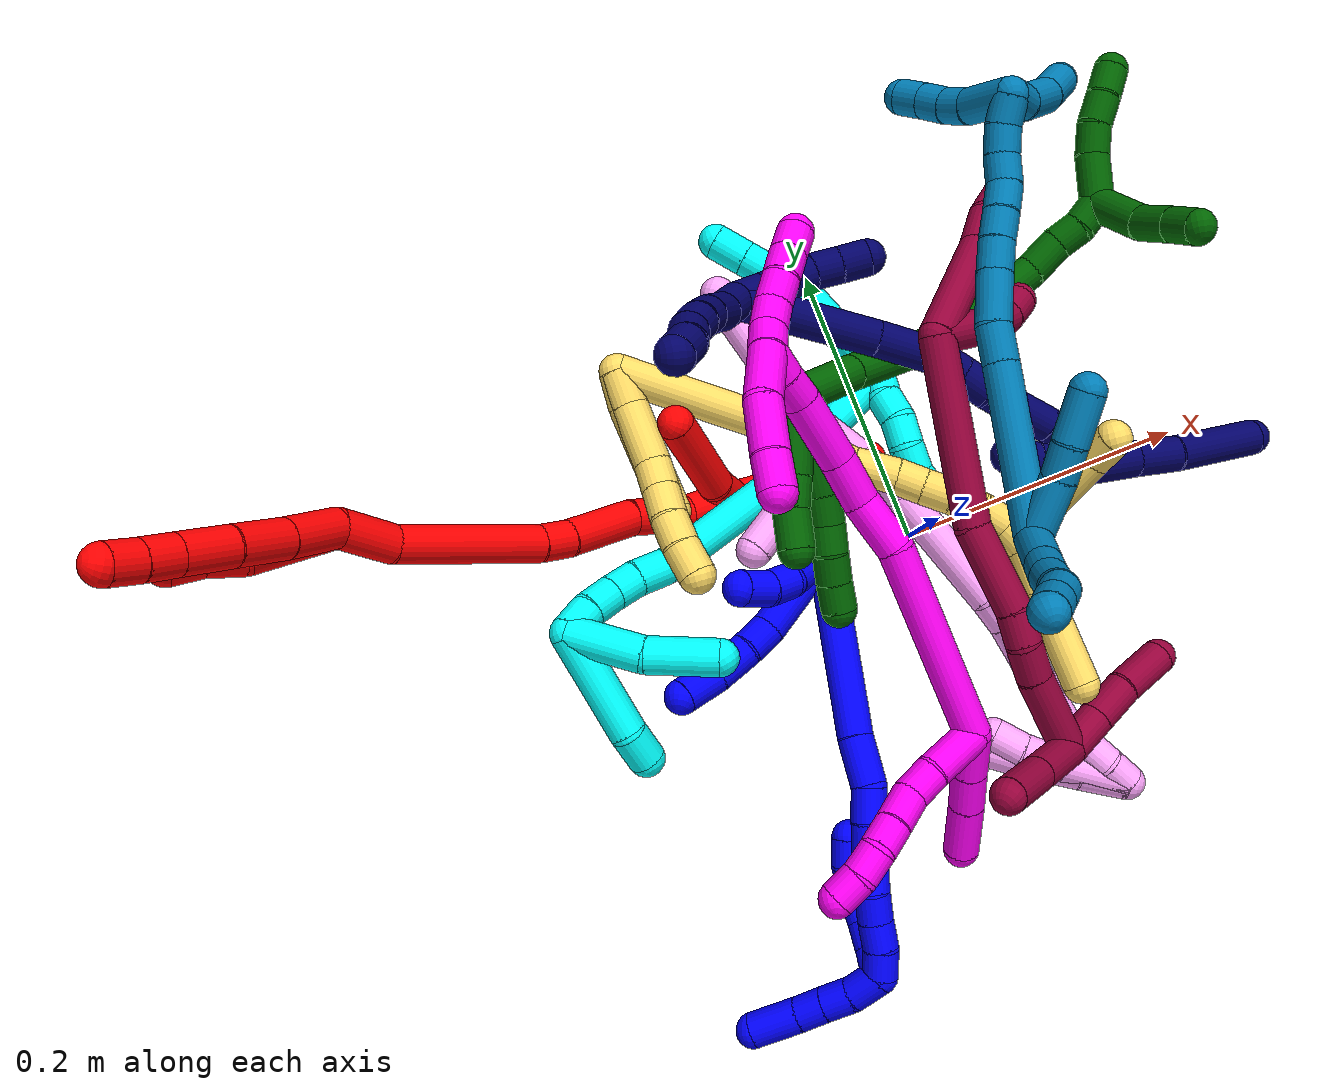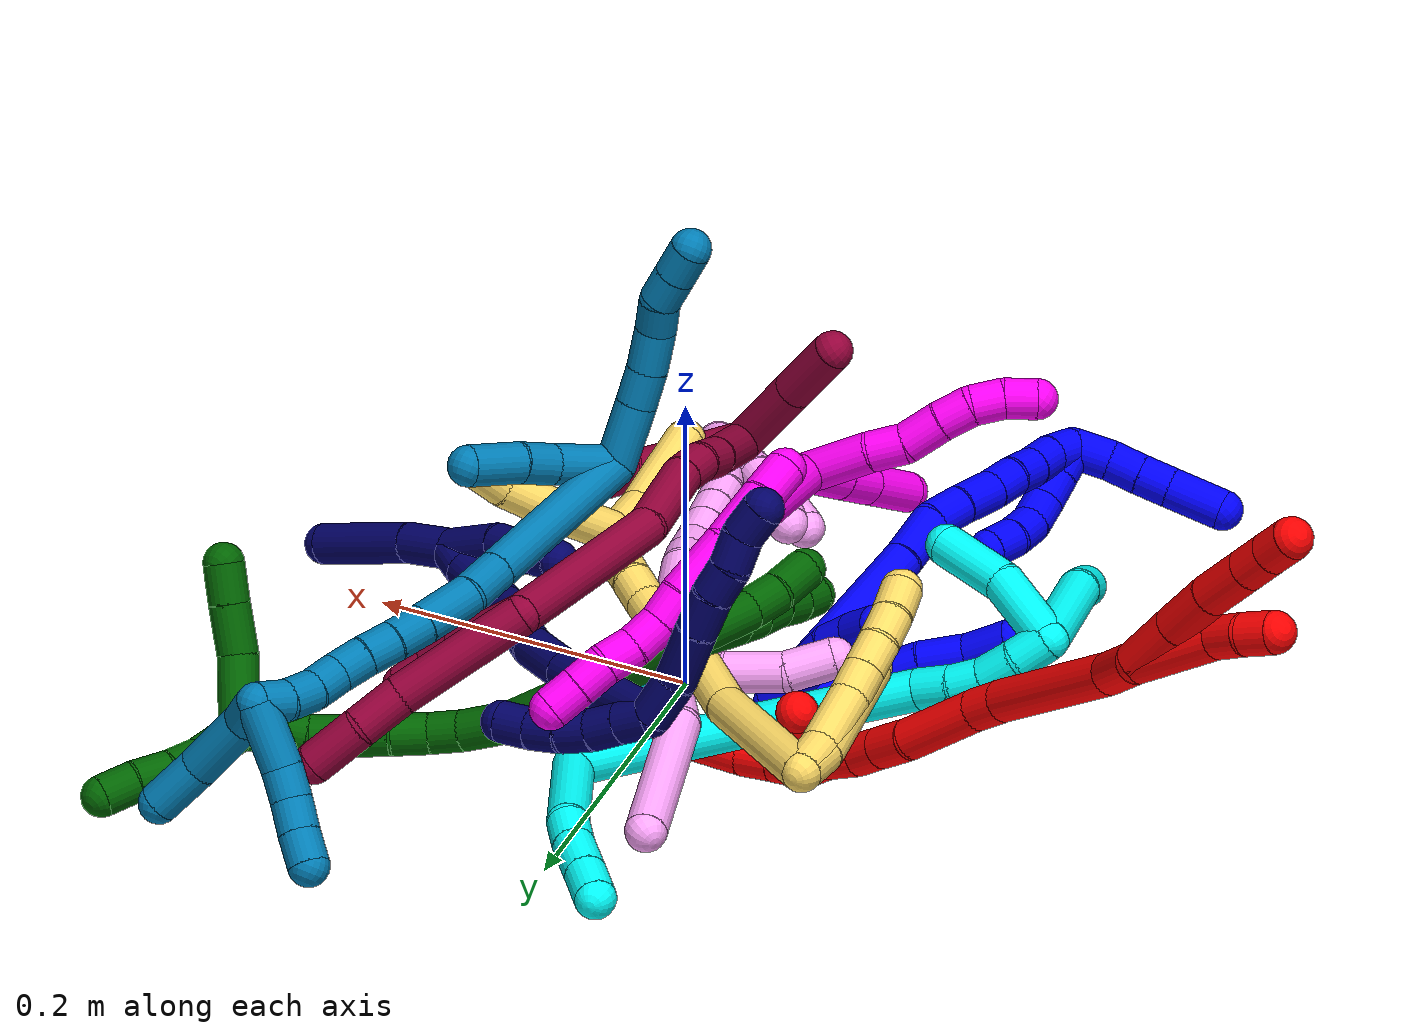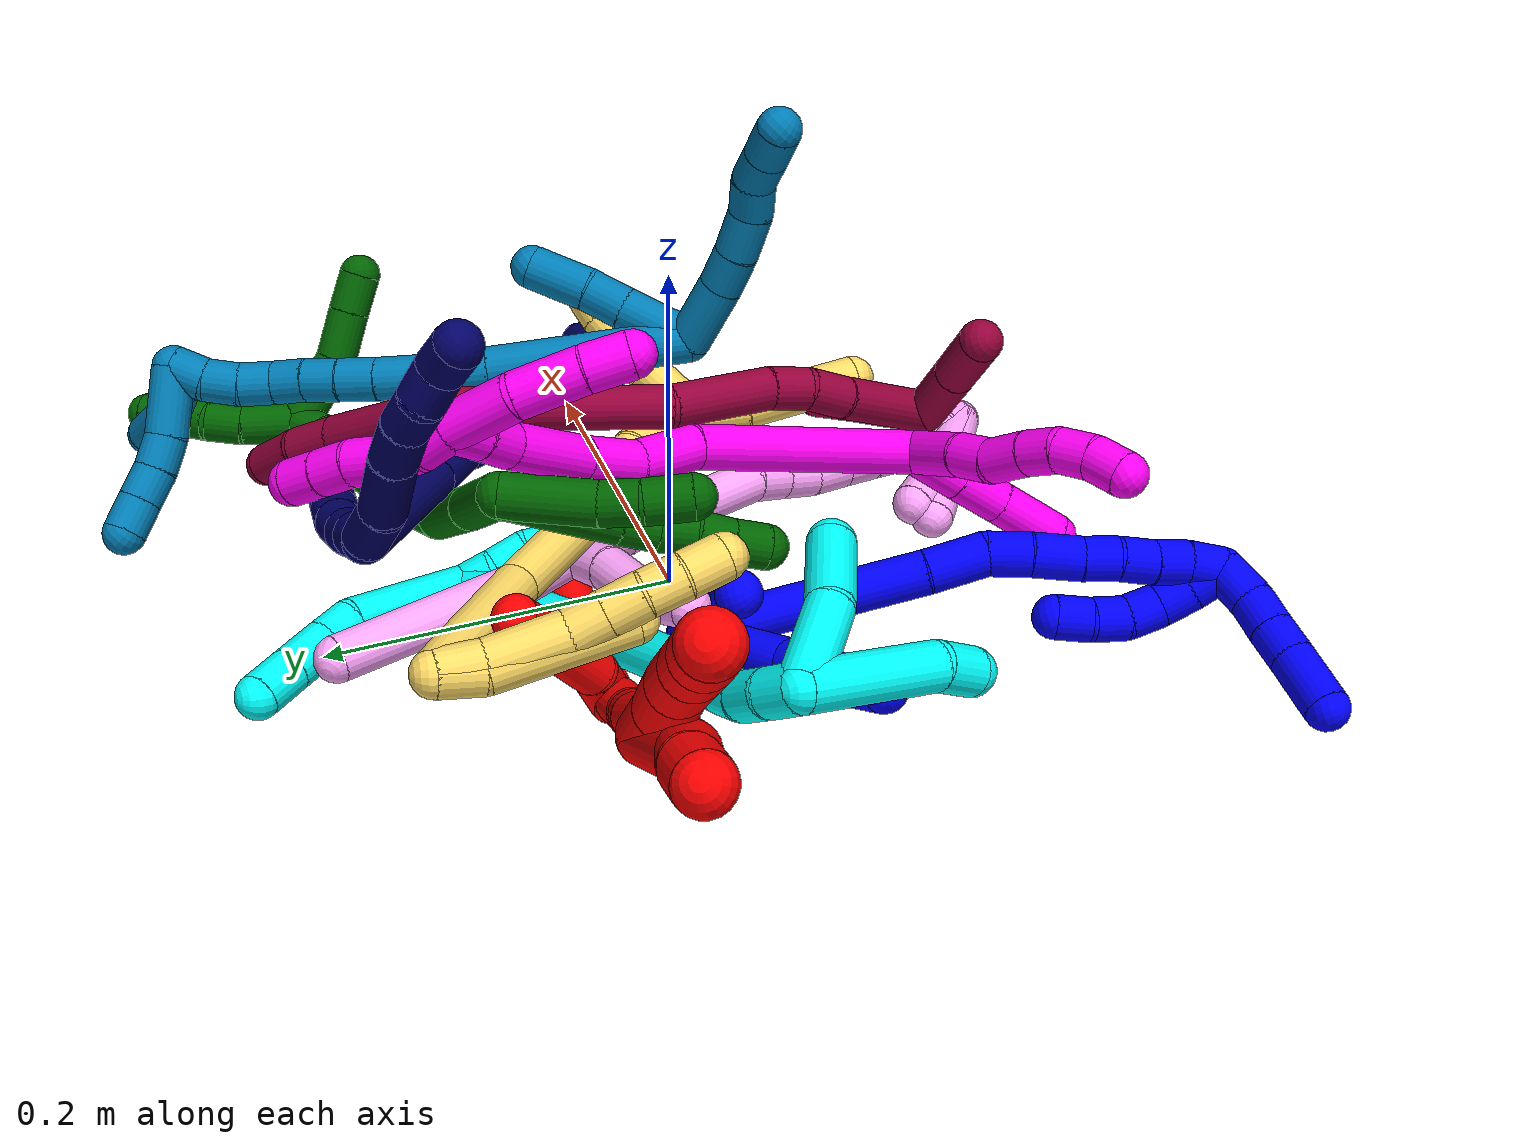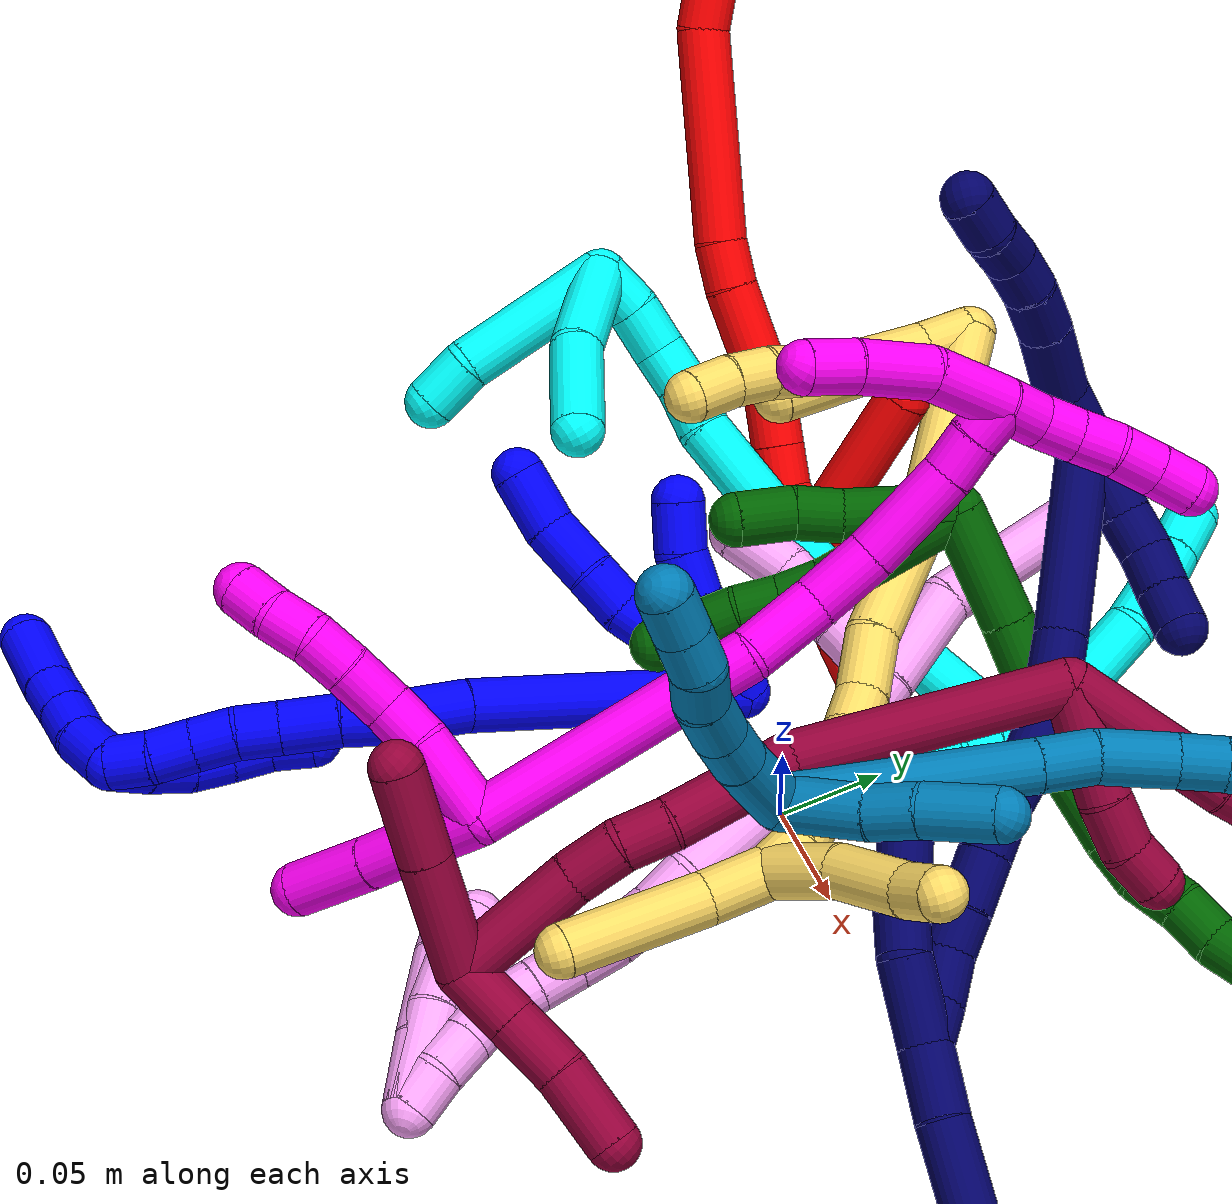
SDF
<sdf version="1.7">
 <world name="default">
  <plugin name="TubeGeneratorPlugin" filename="libtube_generator_plugin.so"/>
  <model name="photoneo_s_sensor">
   <static>1</static>
   <pose>0 0 2 1.57079 1.57079 3.14159</pose>
   <link name="link">
    <inertial><mass>0.1</mass></inertial>
    <sensor name="sensor" type="depth">
     <update_rate>30</update_rate>
     <camera>
      <horizontal_fov>1.22</horizontal_fov>
      <image><width>1920</width><height>1200</height><format>B8G8R8</format></image>
      <clip><near>0.1</near><far>4</far></clip>
      <depth_camera><output>points</output></depth_camera>
     </camera>
     <plugin name="camera_plugin" filename="libgazebo_ros_depth_camera.so">
      <baseline>0.2</baseline>
      <alwaysOn>1</alwaysOn>
      <updateRate>0.0</updateRate>
      <cameraName>camera_ir</cameraName>
      <imageTopicName>/camera/color/image_raw</imageTopicName>
      <cameraInfoTopicName>/camera/color/camera_info</cameraInfoTopicName>
      <depthImageTopicName>/camera/depth/image_raw</depthImageTopicName>
      <depthImageCameraInfoTopicName>/camera/depth/camera_info</depthImageCameraInfoTopicName>
      <pointCloudTopicName>/camera/depth/points</pointCloudTopicName>
      <frameName>fr_optical</frameName>
      <pointCloudCutoff>0.1</pointCloudCutoff>
      <pointCloudCutoffMax>2.0</pointCloudCutoffMax>
      <distortionK1>0</distortionK1>
      <distortionK2>0</distortionK2>
      <distortionK3>0</distortionK3>
      <distortionT1>0</distortionT1>
      <distortionT2>0</distortionT2>
      <CxPrime>0</CxPrime>
      <Cx>0</Cx>
      <Cy>0</Cy>
      <focalLength>0</focalLength>
      <hackBaseline>0</hackBaseline>
     </plugin>
    </sensor>
   </link>
  </model>
  <gravity>0 0 -9.8</gravity>
  <magnetic_field>6e-06 2.3e-05 -4.2e-05</magnetic_field>
  <atmosphere type="adiabatic"/>
  <physics name="default_physics" default="0" type="ode">
   <max_step_size>0.003</max_step_size>
   <real_time_factor>1</real_time_factor>
   <real_time_update_rate>1000</real_time_update_rate>
   <max_contacts>10000</max_contacts>
   <ode>
    <solver>
     <type>quick</type>
     <iters>100</iters>
     <sor>1.3</sor>
     <use_dynamic_moi_rescaling>0</use_dynamic_moi_rescaling>
    </solver>
    <constraints>
     <contact_max_correcting_vel>0</contact_max_correcting_vel>
     <contact_surface_layer>0.001</contact_surface_layer>
     <cfm>0</cfm>
     <erp>0.2</erp>
    </constraints>
   </ode>
  </physics>
  <scene><ambient>0.4 0.4 0.4 1</ambient><background>0.7 0.7 0.7 1</background><shadows>0</shadows></scene>
  <audio><device>default</device></audio>
  <spherical_coordinates>
   <surface_model>EARTH_WGS84</surface_model>
   <latitude_deg>0</latitude_deg>
   <longitude_deg>0</longitude_deg>
   <elevation>0</elevation>
   <heading_deg>0</heading_deg>
  </spherical_coordinates>
  <model name="bin">
   <static>1</static>
   <link name="bottom">
    <collision name="collision-bottom">
     <pose>0 0 -0.01 0 -0 0</pose>
     <geometry><box><size>0.8 0.6 0.02</size></box></geometry>
     <surface>
      <friction><ode><mu>100</mu><mu2>100</mu2></ode></friction>
      <contact><collide_bitmask>65535</collide_bitmask></contact>
     </surface>
    </collision>
   </link>
   <link name="west_wall">
    <collision name="collision-west_wall">
     <pose>-0.41 0 0.1 0 -0 0</pose>
     <geometry><box><size>0.02 0.6 0.2</size></box></geometry>
     <surface>
      <friction><ode><mu>100</mu><mu2>100</mu2></ode></friction>
      <contact><collide_bitmask>65535</collide_bitmask></contact>
     </surface>
    </collision>
   </link>
   <link name="east_wall">
    <collision name="collision-east_wall">
     <pose>0.41 0 0.1 0 -0 0</pose>
     <geometry><box><size>0.02 0.6 0.2</size></box></geometry>
     <surface>
      <friction><ode><mu>100</mu><mu2>100</mu2></ode></friction>
      <contact><collide_bitmask>65535</collide_bitmask></contact>
     </surface>
    </collision>
   </link>
   <link name="south_wall">
    <collision name="collision-south_wall">
     <pose>0 -0.31 0.1 0 -0 0</pose>
     <geometry><box><size>0.8 0.02 0.2</size></box></geometry>
     <surface>
      <friction><ode><mu>100</mu><mu2>100</mu2></ode></friction>
      <contact><collide_bitmask>65535</collide_bitmask></contact>
     </surface>
    </collision>
   </link>
   <link name="north_wall">
    <collision name="collision-north_wall">
     <pose>0 0.31 0.1 0 -0 0</pose>
     <geometry><box><size>0.8 0.02 0.2</size></box></geometry>
     <surface>
      <friction><ode><mu>100</mu><mu2>100</mu2></ode></friction>
      <contact><collide_bitmask>65535</collide_bitmask></contact>
     </surface>
    </collision>
   </link>
  </model>
  <model name="1">
   <static>0</static>
   <link name="1">
    <collision name="collision-cylinder-e_1_2_8">
     <pose>-0.016127 0.005011 0.029922 -0.16593 -0.488571 0.041449</pose>
     <geometry><cylinder><radius>0.0125</radius><length>0.068716</length></cylinder></geometry>
     <surface>
      <friction><ode><mu>1.16</mu><mu2>1.16</mu2><slip1>0</slip1><slip2>0</slip2></ode></friction>
      <contact><ode><kp>1e+06</kp><kd>1</kd><max_vel>0</max_vel><min_depth>0.001</min_depth></ode></contact>
     </surface>
    </collision>
    <visual name="visual-cylinder-e_1_2_8">
     <pose>-0.016127 0.005011 0.029922 -0.16593 -0.488571 0.041449</pose>
     <geometry><cylinder><radius>0.0125</radius><length>0.068716</length></cylinder></geometry>
     <material><ambient>0 0 1 1</ambient></material>
    </visual>
    <collision name="collision-cylinder-e_2_8_9">
     <pose>-0.036599 0.014389 0.069245 -0.434826 -0.397012 0.088814</pose>
     <geometry><cylinder><radius>0.0125</radius><length>0.02248</length></cylinder></geometry>
     <surface>
      <friction><ode><mu>1.16</mu><mu2>1.16</mu2><slip1>0</slip1><slip2>0</slip2></ode></friction>
      <contact><ode><kp>1e+06</kp><kd>1</kd><max_vel>0</max_vel><min_depth>0.001</min_depth></ode></contact>
     </surface>
    </collision>
    <visual name="visual-cylinder-e_2_8_9">
     <pose>-0.036599 0.014389 0.069245 -0.434826 -0.397012 0.088814</pose>
     <geometry><cylinder><radius>0.0125</radius><length>0.02248</length></cylinder></geometry>
     <material><ambient>0 0 1 1</ambient></material>
    </visual>
    <collision name="collision-cylinder-e_3_9_10">
     <pose>-0.0487 0.02391 0.089936 -0.428348 -0.558482 0.124573</pose>
     <geometry><cylinder><radius>0.0125</radius><length>0.02927</length></cylinder></geometry>
     <surface>
      <friction><ode><mu>1.16</mu><mu2>1.16</mu2><slip1>0</slip1><slip2>0</slip2></ode></friction>
      <contact><ode><kp>1e+06</kp><kd>1</kd><max_vel>0</max_vel><min_depth>0.001</min_depth></ode></contact>
     </surface>
    </collision>
    <visual name="visual-cylinder-e_3_9_10">
     <pose>-0.0487 0.02391 0.089936 -0.428348 -0.558482 0.124573</pose>
     <geometry><cylinder><radius>0.0125</radius><length>0.02927</length></cylinder></geometry>
     <material><ambient>0 0 1 1</ambient></material>
    </visual>
    <collision name="collision-cylinder-e_4_10_6">
     <pose>-0.061552 0.037446 0.112265 -0.649314 -0.352377 0.119698</pose>
     <geometry><cylinder><radius>0.0125</radius><length>0.029534</length></cylinder></geometry>
     <surface>
      <friction><ode><mu>1.16</mu><mu2>1.16</mu2><slip1>0</slip1><slip2>0</slip2></ode></friction>
      <contact><ode><kp>1e+06</kp><kd>1</kd><max_vel>0</max_vel><min_depth>0.001</min_depth></ode></contact>
     </surface>
    </collision>
    <visual name="visual-cylinder-e_4_10_6">
     <pose>-0.061552 0.037446 0.112265 -0.649314 -0.352377 0.119698</pose>
     <geometry><cylinder><radius>0.0125</radius><length>0.029534</length></cylinder></geometry>
     <material><ambient>0 0 1 1</ambient></material>
    </visual>
    <collision name="collision-cylinder-e_1_2_11">
     <pose>0.00219 0.017282 0.021748 -0.671466 0.07868 -0.027467</pose>
     <geometry><cylinder><radius>0.0125</radius><length>0.055729</length></cylinder></geometry>
     <surface>
      <friction><ode><mu>1.16</mu><mu2>1.16</mu2><slip1>0</slip1><slip2>0</slip2></ode></friction>
      <contact><ode><kp>1e+06</kp><kd>1</kd><max_vel>0</max_vel><min_depth>0.001</min_depth></ode></contact>
     </surface>
    </collision>
    <visual name="visual-cylinder-e_1_2_11">
     <pose>0.00219 0.017282 0.021748 -0.671466 0.07868 -0.027467</pose>
     <geometry><cylinder><radius>0.0125</radius><length>0.055729</length></cylinder></geometry>
     <material><ambient>0 0 1 1</ambient></material>
    </visual>
    <collision name="collision-cylinder-e_2_11_12">
     <pose>0.002173 0.04215 0.050283 -0.84098 -0.21355 0.095782</pose>
     <geometry><cylinder><radius>0.0125</radius><length>0.020833</length></cylinder></geometry>
     <surface>
      <friction><ode><mu>1.16</mu><mu2>1.16</mu2><slip1>0</slip1><slip2>0</slip2></ode></friction>
      <contact><ode><kp>1e+06</kp><kd>1</kd><max_vel>0</max_vel><min_depth>0.001</min_depth></ode></contact>
     </surface>
    </collision>
    <visual name="visual-cylinder-e_2_11_12">
     <pose>0.002173 0.04215 0.050283 -0.84098 -0.21355 0.095782</pose>
     <geometry><cylinder><radius>0.0125</radius><length>0.020833</length></cylinder></geometry>
     <material><ambient>0 0 1 1</ambient></material>
    </visual>
    <collision name="collision-cylinder-e_3_12_5">
     <pose>-0.002565 0.060053 0.062022 -1.12326 -0.217627 0.137263</pose>
     <geometry><cylinder><radius>0.0125</radius><length>0.023438</length></cylinder></geometry>
     <surface>
      <friction><ode><mu>1.16</mu><mu2>1.16</mu2><slip1>0</slip1><slip2>0</slip2></ode></friction>
      <contact><ode><kp>1e+06</kp><kd>1</kd><max_vel>0</max_vel><min_depth>0.001</min_depth></ode></contact>
     </surface>
    </collision>
    <visual name="visual-cylinder-e_3_12_5">
     <pose>-0.002565 0.060053 0.062022 -1.12326 -0.217627 0.137263</pose>
     <geometry><cylinder><radius>0.0125</radius><length>0.023438</length></cylinder></geometry>
     <material><ambient>0 0 1 1</ambient></material>
    </visual>
    <collision name="collision-cylinder-e_1_2_13">
     <pose>0.003767 -0.02588 0.061416 0.398811 0.056456 0.011412</pose>
     <geometry><cylinder><radius>0.0125</radius><length>0.133504</length></cylinder></geometry>
     <surface>
      <friction><ode><mu>1.16</mu><mu2>1.16</mu2><slip1>0</slip1><slip2>0</slip2></ode></friction>
      <contact><ode><kp>1e+06</kp><kd>1</kd><max_vel>0</max_vel><min_depth>0.001</min_depth></ode></contact>
     </surface>
    </collision>
    <visual name="visual-cylinder-e_1_2_13">
     <pose>0.003767 -0.02588 0.061416 0.398811 0.056456 0.011412</pose>
     <geometry><cylinder><radius>0.0125</radius><length>0.133504</length></cylinder></geometry>
     <material><ambient>0 0 1 1</ambient></material>
    </visual>
    <collision name="collision-cylinder-e_2_13_14">
     <pose>0.009622 -0.059782 0.137806 0.491824 0.122326 0.030739</pose>
     <geometry><cylinder><radius>0.0125</radius><length>0.034231</length></cylinder></geometry>
     <surface>
      <friction><ode><mu>1.16</mu><mu2>1.16</mu2><slip1>0</slip1><slip2>0</slip2></ode></friction>
      <contact><ode><kp>1e+06</kp><kd>1</kd><max_vel>0</max_vel><min_depth>0.001</min_depth></ode></contact>
     </surface>
    </collision>
    <visual name="visual-cylinder-e_2_13_14">
     <pose>0.009622 -0.059782 0.137806 0.491824 0.122326 0.030739</pose>
     <geometry><cylinder><radius>0.0125</radius><length>0.034231</length></cylinder></geometry>
     <material><ambient>0 0 1 1</ambient></material>
    </visual>
    <collision name="collision-cylinder-e_3_14_15">
     <pose>0.009191 -0.073282 0.163334 0.47868 -0.208744 -0.051112</pose>
     <geometry><cylinder><radius>0.0125</radius><length>0.02431</length></cylinder></geometry>
     <surface>
      <friction><ode><mu>1.16</mu><mu2>1.16</mu2><slip1>0</slip1><slip2>0</slip2></ode></friction>
      <contact><ode><kp>1e+06</kp><kd>1</kd><max_vel>0</max_vel><min_depth>0.001</min_depth></ode></contact>
     </surface>
    </collision>
    <visual name="visual-cylinder-e_3_14_15">
     <pose>0.009191 -0.073282 0.163334 0.47868 -0.208744 -0.051112</pose>
     <geometry><cylinder><radius>0.0125</radius><length>0.02431</length></cylinder></geometry>
     <material><ambient>0 0 1 1</ambient></material>
    </visual>
    <collision name="collision-cylinder-e_4_15_16">
     <pose>0.003272 -0.086154 0.185184 0.579675 -0.246775 -0.073939</pose>
     <geometry><cylinder><radius>0.0125</radius><length>0.027845</length></cylinder></geometry>
     <surface>
      <friction><ode><mu>1.16</mu><mu2>1.16</mu2><slip1>0</slip1><slip2>0</slip2></ode></friction>
      <contact><ode><kp>1e+06</kp><kd>1</kd><max_vel>0</max_vel><min_depth>0.001</min_depth></ode></contact>
     </surface>
    </collision>
    <visual name="visual-cylinder-e_4_15_16">
     <pose>0.003272 -0.086154 0.185184 0.579675 -0.246775 -0.073939</pose>
     <geometry><cylinder><radius>0.0125</radius><length>0.027845</length></cylinder></geometry>
     <material><ambient>0 0 1 1</ambient></material>
    </visual>
    <collision name="collision-cylinder-e_5_16_17">
     <pose>-0.00176 -0.098675 0.204938 0.544805 -0.163384 -0.045735</pose>
     <geometry><cylinder><radius>0.0125</radius><length>0.020049</length></cylinder></geometry>
     <surface>
      <friction><ode><mu>1.16</mu><mu2>1.16</mu2><slip1>0</slip1><slip2>0</slip2></ode></friction>
      <contact><ode><kp>1e+06</kp><kd>1</kd><max_vel>0</max_vel><min_depth>0.001</min_depth></ode></contact>
     </surface>
    </collision>
    <visual name="visual-cylinder-e_5_16_17">
     <pose>-0.00176 -0.098675 0.204938 0.544805 -0.163384 -0.045735</pose>
     <geometry><cylinder><radius>0.0125</radius><length>0.020049</length></cylinder></geometry>
     <material><ambient>0 0 1 1</ambient></material>
    </visual>
    <collision name="collision-cylinder-e_6_17_18">
     <pose>-0.005635 -0.110251 0.220712 0.722678 -0.226196 -0.0858</pose>
     <geometry><cylinder><radius>0.0125</radius><length>0.020015</length></cylinder></geometry>
     <surface>
      <friction><ode><mu>1.16</mu><mu2>1.16</mu2><slip1>0</slip1><slip2>0</slip2></ode></friction>
      <contact><ode><kp>1e+06</kp><kd>1</kd><max_vel>0</max_vel><min_depth>0.001</min_depth></ode></contact>
     </surface>
    </collision>
    <visual name="visual-cylinder-e_6_17_18">
     <pose>-0.005635 -0.110251 0.220712 0.722678 -0.226196 -0.0858</pose>
     <geometry><cylinder><radius>0.0125</radius><length>0.020015</length></cylinder></geometry>
     <material><ambient>0 0 1 1</ambient></material>
    </visual>
    <collision name="collision-cylinder-e_7_18_19">
     <pose>-0.009195 -0.12316 0.235574 0.707818 -0.131732 -0.048731</pose>
     <geometry><cylinder><radius>0.0125</radius><length>0.02004</length></cylinder></geometry>
     <surface>
      <friction><ode><mu>1.16</mu><mu2>1.16</mu2><slip1>0</slip1><slip2>0</slip2></ode></friction>
      <contact><ode><kp>1e+06</kp><kd>1</kd><max_vel>0</max_vel><min_depth>0.001</min_depth></ode></contact>
     </surface>
    </collision>
    <visual name="visual-cylinder-e_7_18_19">
     <pose>-0.009195 -0.12316 0.235574 0.707818 -0.131732 -0.048731</pose>
     <geometry><cylinder><radius>0.0125</radius><length>0.02004</length></cylinder></geometry>
     <material><ambient>0 0 1 1</ambient></material>
    </visual>
    <collision name="collision-cylinder-e_8_19_1">
     <pose>-0.013851 -0.135175 0.250739 0.630261 -0.340329 -0.111912</pose>
     <geometry><cylinder><radius>0.0125</radius><length>0.020006</length></cylinder></geometry>
     <surface>
      <friction><ode><mu>1.16</mu><mu2>1.16</mu2><slip1>0</slip1><slip2>0</slip2></ode></friction>
      <contact><ode><kp>1e+06</kp><kd>1</kd><max_vel>0</max_vel><min_depth>0.001</min_depth></ode></contact>
     </surface>
    </collision>
    <visual name="visual-cylinder-e_8_19_1">
     <pose>-0.013851 -0.135175 0.250739 0.630261 -0.340329 -0.111912</pose>
     <geometry><cylinder><radius>0.0125</radius><length>0.020006</length></cylinder></geometry>
     <material><ambient>0 0 1 1</ambient></material>
    </visual>
    <collision name="collision-cylinder-e_1_1_20">
     <pose>-0.027749 -0.140197 0.264087 -0.093122 -1.07175 0.055325</pose>
     <geometry><cylinder><radius>0.0125</radius><length>0.024053</length></cylinder></geometry>
     <surface>
      <friction><ode><mu>1.16</mu><mu2>1.16</mu2><slip1>0</slip1><slip2>0</slip2></ode></friction>
      <contact><ode><kp>1e+06</kp><kd>1</kd><max_vel>0</max_vel><min_depth>0.001</min_depth></ode></contact>
     </surface>
    </collision>
    <visual name="visual-cylinder-e_1_1_20">
     <pose>-0.027749 -0.140197 0.264087 -0.093122 -1.07175 0.055325</pose>
     <geometry><cylinder><radius>0.0125</radius><length>0.024053</length></cylinder></geometry>
     <material><ambient>0 0 1 1</ambient></material>
    </visual>
    <collision name="collision-cylinder-e_2_20_21">
     <pose>-0.047768 -0.137304 0.273341 -0.589943 -1.14944 0.388594</pose>
     <geometry><cylinder><radius>0.0125</radius><length>0.020731</length></cylinder></geometry>
     <surface>
      <friction><ode><mu>1.16</mu><mu2>1.16</mu2><slip1>0</slip1><slip2>0</slip2></ode></friction>
      <contact><ode><kp>1e+06</kp><kd>1</kd><max_vel>0</max_vel><min_depth>0.001</min_depth></ode></contact>
     </surface>
    </collision>
    <visual name="visual-cylinder-e_2_20_21">
     <pose>-0.047768 -0.137304 0.273341 -0.589943 -1.14944 0.388594</pose>
     <geometry><cylinder><radius>0.0125</radius><length>0.020731</length></cylinder></geometry>
     <material><ambient>0 0 1 1</ambient></material>
    </visual>
    <collision name="collision-cylinder-e_3_21_22">
     <pose>-0.066393 -0.132774 0.280587 -0.527991 -1.13123 0.339869</pose>
     <geometry><cylinder><radius>0.0125</radius><length>0.020256</length></cylinder></geometry>
     <surface>
      <friction><ode><mu>1.16</mu><mu2>1.16</mu2><slip1>0</slip1><slip2>0</slip2></ode></friction>
      <contact><ode><kp>1e+06</kp><kd>1</kd><max_vel>0</max_vel><min_depth>0.001</min_depth></ode></contact>
     </surface>
    </collision>
    <visual name="visual-cylinder-e_3_21_22">
     <pose>-0.066393 -0.132774 0.280587 -0.527991 -1.13123 0.339869</pose>
     <geometry><cylinder><radius>0.0125</radius><length>0.020256</length></cylinder></geometry>
     <material><ambient>0 0 1 1</ambient></material>
    </visual>
    <collision name="collision-cylinder-e_4_22_4">
     <pose>-0.091088 -0.125544 0.290536 -0.682259 -1.09399 0.42583</pose>
     <geometry><cylinder><radius>0.0125</radius><length>0.034959</length></cylinder></geometry>
     <surface>
      <friction><ode><mu>1.16</mu><mu2>1.16</mu2><slip1>0</slip1><slip2>0</slip2></ode></friction>
      <contact><ode><kp>1e+06</kp><kd>1</kd><max_vel>0</max_vel><min_depth>0.001</min_depth></ode></contact>
     </surface>
    </collision>
    <visual name="visual-cylinder-e_4_22_4">
     <pose>-0.091088 -0.125544 0.290536 -0.682259 -1.09399 0.42583</pose>
     <geometry><cylinder><radius>0.0125</radius><length>0.034959</length></cylinder></geometry>
     <material><ambient>0 0 1 1</ambient></material>
    </visual>
    <collision name="collision-cylinder-e_1_1_23">
     <pose>-0.02024 -0.139047 0.248983 -2.96362 -0.310002 2.10393</pose>
     <geometry><cylinder><radius>0.0125</radius><length>0.02</length></cylinder></geometry>
     <surface>
      <friction><ode><mu>1.16</mu><mu2>1.16</mu2><slip1>0</slip1><slip2>0</slip2></ode></friction>
      <contact><ode><kp>1e+06</kp><kd>1</kd><max_vel>0</max_vel><min_depth>0.001</min_depth></ode></contact>
     </surface>
    </collision>
    <visual name="visual-cylinder-e_1_1_23">
     <pose>-0.02024 -0.139047 0.248983 -2.96362 -0.310002 2.10393</pose>
     <geometry><cylinder><radius>0.0125</radius><length>0.02</length></cylinder></geometry>
     <material><ambient>0 0 1 1</ambient></material>
    </visual>
    <collision name="collision-cylinder-e_2_23_24">
     <pose>-0.025965 -0.134634 0.230368 -2.85473 -0.270683 1.512</pose>
     <geometry><cylinder><radius>0.0125</radius><length>0.02</length></cylinder></geometry>
     <surface>
      <friction><ode><mu>1.16</mu><mu2>1.16</mu2><slip1>0</slip1><slip2>0</slip2></ode></friction>
      <contact><ode><kp>1e+06</kp><kd>1</kd><max_vel>0</max_vel><min_depth>0.001</min_depth></ode></contact>
     </surface>
    </collision>
    <visual name="visual-cylinder-e_2_23_24">
     <pose>-0.025965 -0.134634 0.230368 -2.85473 -0.270683 1.512</pose>
     <geometry><cylinder><radius>0.0125</radius><length>0.02</length></cylinder></geometry>
     <material><ambient>0 0 1 1</ambient></material>
    </visual>
    <collision name="collision-cylinder-e_3_24_25">
     <pose>-0.03057 -0.126836 0.212727 -2.59839 -0.194369 0.673496</pose>
     <geometry><cylinder><radius>0.0125</radius><length>0.02</length></cylinder></geometry>
     <surface>
      <friction><ode><mu>1.16</mu><mu2>1.16</mu2><slip1>0</slip1><slip2>0</slip2></ode></friction>
      <contact><ode><kp>1e+06</kp><kd>1</kd><max_vel>0</max_vel><min_depth>0.001</min_depth></ode></contact>
     </surface>
    </collision>
    <visual name="visual-cylinder-e_3_24_25">
     <pose>-0.03057 -0.126836 0.212727 -2.59839 -0.194369 0.673496</pose>
     <geometry><cylinder><radius>0.0125</radius><length>0.02</length></cylinder></geometry>
     <material><ambient>0 0 1 1</ambient></material>
    </visual>
    <collision name="collision-cylinder-e_4_25_26">
     <pose>-0.031599 -0.115508 0.196579 -2.46225 0.090423 -0.25468</pose>
     <geometry><cylinder><radius>0.0125</radius><length>0.02</length></cylinder></geometry>
     <surface>
      <friction><ode><mu>1.16</mu><mu2>1.16</mu2><slip1>0</slip1><slip2>0</slip2></ode></friction>
      <contact><ode><kp>1e+06</kp><kd>1</kd><max_vel>0</max_vel><min_depth>0.001</min_depth></ode></contact>
     </surface>
    </collision>
    <visual name="visual-cylinder-e_4_25_26">
     <pose>-0.031599 -0.115508 0.196579 -2.46225 0.090423 -0.25468</pose>
     <geometry><cylinder><radius>0.0125</radius><length>0.02</length></cylinder></geometry>
     <material><ambient>0 0 1 1</ambient></material>
    </visual>
    <collision name="collision-cylinder-e_5_26_3">
     <pose>-0.028172 -0.104206 0.180574 -2.59319 0.255067 -0.855439</pose>
     <geometry><cylinder><radius>0.0125</radius><length>0.02</length></cylinder></geometry>
     <surface>
      <friction><ode><mu>1.16</mu><mu2>1.16</mu2><slip1>0</slip1><slip2>0</slip2></ode></friction>
      <contact><ode><kp>1e+06</kp><kd>1</kd><max_vel>0</max_vel><min_depth>0.001</min_depth></ode></contact>
     </surface>
    </collision>
    <visual name="visual-cylinder-e_5_26_3">
     <pose>-0.028172 -0.104206 0.180574 -2.59319 0.255067 -0.855439</pose>
     <geometry><cylinder><radius>0.0125</radius><length>0.02</length></cylinder></geometry>
     <material><ambient>0 0 1 1</ambient></material>
    </visual>
    <collision name="collision-sphere-3">
     <pose>-0.025649 -0.099161 0.172316 0 -0 0</pose>
     <geometry><sphere><radius>0.0125</radius></sphere></geometry>
     <surface>
      <friction><ode><mu>1.16</mu><mu2>1.16</mu2><slip1>0</slip1><slip2>0</slip2></ode></friction>
      <contact><ode><kp>1e+06</kp><kd>1</kd><max_vel>0</max_vel><min_depth>0.001</min_depth></ode></contact>
     </surface>
    </collision>
    <visual name="visual-sphere-3">
     <pose>-0.025649 -0.099161 0.172316 0 -0 0</pose>
     <geometry><sphere><radius>0.0125</radius></sphere></geometry>
     <material><ambient>0 0 1 1</ambient></material>
    </visual>
    <collision name="collision-sphere-26">
     <pose>-0.030696 -0.10925 0.188831 0 -0 0</pose>
     <geometry><sphere><radius>0.0125</radius></sphere></geometry>
     <surface>
      <friction><ode><mu>1.16</mu><mu2>1.16</mu2><slip1>0</slip1><slip2>0</slip2></ode></friction>
      <contact><ode><kp>1e+06</kp><kd>1</kd><max_vel>0</max_vel><min_depth>0.001</min_depth></ode></contact>
     </surface>
    </collision>
    <visual name="visual-sphere-26">
     <pose>-0.030696 -0.10925 0.188831 0 -0 0</pose>
     <geometry><sphere><radius>0.0125</radius></sphere></geometry>
     <material><ambient>0 0 1 1</ambient></material>
    </visual>
    <collision name="collision-sphere-25">
     <pose>-0.032502 -0.121765 0.204327 0 -0 0</pose>
     <geometry><sphere><radius>0.0125</radius></sphere></geometry>
     <surface>
      <friction><ode><mu>1.16</mu><mu2>1.16</mu2><slip1>0</slip1><slip2>0</slip2></ode></friction>
      <contact><ode><kp>1e+06</kp><kd>1</kd><max_vel>0</max_vel><min_depth>0.001</min_depth></ode></contact>
     </surface>
    </collision>
    <visual name="visual-sphere-25">
     <pose>-0.032502 -0.121765 0.204327 0 -0 0</pose>
     <geometry><sphere><radius>0.0125</radius></sphere></geometry>
     <material><ambient>0 0 1 1</ambient></material>
    </visual>
    <collision name="collision-sphere-24">
     <pose>-0.028639 -0.131908 0.221126 0 -0 0</pose>
     <geometry><sphere><radius>0.0125</radius></sphere></geometry>
     <surface>
      <friction><ode><mu>1.16</mu><mu2>1.16</mu2><slip1>0</slip1><slip2>0</slip2></ode></friction>
      <contact><ode><kp>1e+06</kp><kd>1</kd><max_vel>0</max_vel><min_depth>0.001</min_depth></ode></contact>
     </surface>
    </collision>
    <visual name="visual-sphere-24">
     <pose>-0.028639 -0.131908 0.221126 0 -0 0</pose>
     <geometry><sphere><radius>0.0125</radius></sphere></geometry>
     <material><ambient>0 0 1 1</ambient></material>
    </visual>
    <collision name="collision-sphere-23">
     <pose>-0.023291 -0.137361 0.23961 0 -0 0</pose>
     <geometry><sphere><radius>0.0125</radius></sphere></geometry>
     <surface>
      <friction><ode><mu>1.16</mu><mu2>1.16</mu2><slip1>0</slip1><slip2>0</slip2></ode></friction>
      <contact><ode><kp>1e+06</kp><kd>1</kd><max_vel>0</max_vel><min_depth>0.001</min_depth></ode></contact>
     </surface>
    </collision>
    <visual name="visual-sphere-23">
     <pose>-0.023291 -0.137361 0.23961 0 -0 0</pose>
     <geometry><sphere><radius>0.0125</radius></sphere></geometry>
     <material><ambient>0 0 1 1</ambient></material>
    </visual>
    <collision name="collision-sphere-4">
     <pose>-0.106618 -0.120486 0.296763 0 -0 0</pose>
     <geometry><sphere><radius>0.0125</radius></sphere></geometry>
     <surface>
      <friction><ode><mu>1.16</mu><mu2>1.16</mu2><slip1>0</slip1><slip2>0</slip2></ode></friction>
      <contact><ode><kp>1e+06</kp><kd>1</kd><max_vel>0</max_vel><min_depth>0.001</min_depth></ode></contact>
     </surface>
    </collision>
    <visual name="visual-sphere-4">
     <pose>-0.106618 -0.120486 0.296763 0 -0 0</pose>
     <geometry><sphere><radius>0.0125</radius></sphere></geometry>
     <material><ambient>0 0 1 1</ambient></material>
    </visual>
    <collision name="collision-sphere-22">
     <pose>-0.075558 -0.130602 0.28431 0 -0 0</pose>
     <geometry><sphere><radius>0.0125</radius></sphere></geometry>
     <surface>
      <friction><ode><mu>1.16</mu><mu2>1.16</mu2><slip1>0</slip1><slip2>0</slip2></ode></friction>
      <contact><ode><kp>1e+06</kp><kd>1</kd><max_vel>0</max_vel><min_depth>0.001</min_depth></ode></contact>
     </surface>
    </collision>
    <visual name="visual-sphere-22">
     <pose>-0.075558 -0.130602 0.28431 0 -0 0</pose>
     <geometry><sphere><radius>0.0125</radius></sphere></geometry>
     <material><ambient>0 0 1 1</ambient></material>
    </visual>
    <collision name="collision-sphere-21">
     <pose>-0.057227 -0.134945 0.276864 0 -0 0</pose>
     <geometry><sphere><radius>0.0125</radius></sphere></geometry>
     <surface>
      <friction><ode><mu>1.16</mu><mu2>1.16</mu2><slip1>0</slip1><slip2>0</slip2></ode></friction>
      <contact><ode><kp>1e+06</kp><kd>1</kd><max_vel>0</max_vel><min_depth>0.001</min_depth></ode></contact>
     </surface>
    </collision>
    <visual name="visual-sphere-21">
     <pose>-0.057227 -0.134945 0.276864 0 -0 0</pose>
     <geometry><sphere><radius>0.0125</radius></sphere></geometry>
     <material><ambient>0 0 1 1</ambient></material>
    </visual>
    <collision name="collision-sphere-20">
     <pose>-0.038309 -0.139662 0.269818 0 -0 0</pose>
     <geometry><sphere><radius>0.0125</radius></sphere></geometry>
     <surface>
      <friction><ode><mu>1.16</mu><mu2>1.16</mu2><slip1>0</slip1><slip2>0</slip2></ode></friction>
      <contact><ode><kp>1e+06</kp><kd>1</kd><max_vel>0</max_vel><min_depth>0.001</min_depth></ode></contact>
     </surface>
    </collision>
    <visual name="visual-sphere-20">
     <pose>-0.038309 -0.139662 0.269818 0 -0 0</pose>
     <geometry><sphere><radius>0.0125</radius></sphere></geometry>
     <material><ambient>0 0 1 1</ambient></material>
    </visual>
    <collision name="collision-sphere-11">
     <pose>0.00438 0.034563 0.043496 0 -0 0</pose>
     <geometry><sphere><radius>0.0125</radius></sphere></geometry>
     <surface>
      <friction><ode><mu>1.16</mu><mu2>1.16</mu2><slip1>0</slip1><slip2>0</slip2></ode></friction>
      <contact><ode><kp>1e+06</kp><kd>1</kd><max_vel>0</max_vel><min_depth>0.001</min_depth></ode></contact>
     </surface>
    </collision>
    <visual name="visual-sphere-11">
     <pose>0.00438 0.034563 0.043496 0 -0 0</pose>
     <geometry><sphere><radius>0.0125</radius></sphere></geometry>
     <material><ambient>0 0 1 1</ambient></material>
    </visual>
    <collision name="collision-sphere-6">
     <pose>-0.066648 0.045826 0.123304 0 -0 0</pose>
     <geometry><sphere><radius>0.0125</radius></sphere></geometry>
     <surface>
      <friction><ode><mu>1.16</mu><mu2>1.16</mu2><slip1>0</slip1><slip2>0</slip2></ode></friction>
      <contact><ode><kp>1e+06</kp><kd>1</kd><max_vel>0</max_vel><min_depth>0.001</min_depth></ode></contact>
     </surface>
    </collision>
    <visual name="visual-sphere-6">
     <pose>-0.066648 0.045826 0.123304 0 -0 0</pose>
     <geometry><sphere><radius>0.0125</radius></sphere></geometry>
     <material><ambient>0 0 1 1</ambient></material>
    </visual>
    <collision name="collision-sphere-10">
     <pose>-0.056455 0.029066 0.101226 0 -0 0</pose>
     <geometry><sphere><radius>0.0125</radius></sphere></geometry>
     <surface>
      <friction><ode><mu>1.16</mu><mu2>1.16</mu2><slip1>0</slip1><slip2>0</slip2></ode></friction>
      <contact><ode><kp>1e+06</kp><kd>1</kd><max_vel>0</max_vel><min_depth>0.001</min_depth></ode></contact>
     </surface>
    </collision>
    <visual name="visual-sphere-10">
     <pose>-0.056455 0.029066 0.101226 0 -0 0</pose>
     <geometry><sphere><radius>0.0125</radius></sphere></geometry>
     <material><ambient>0 0 1 1</ambient></material>
    </visual>
    <collision name="collision-sphere-9">
     <pose>-0.040945 0.018755 0.078646 0 -0 0</pose>
     <geometry><sphere><radius>0.0125</radius></sphere></geometry>
     <surface>
      <friction><ode><mu>1.16</mu><mu2>1.16</mu2><slip1>0</slip1><slip2>0</slip2></ode></friction>
      <contact><ode><kp>1e+06</kp><kd>1</kd><max_vel>0</max_vel><min_depth>0.001</min_depth></ode></contact>
     </surface>
    </collision>
    <visual name="visual-sphere-9">
     <pose>-0.040945 0.018755 0.078646 0 -0 0</pose>
     <geometry><sphere><radius>0.0125</radius></sphere></geometry>
     <material><ambient>0 0 1 1</ambient></material>
    </visual>
    <collision name="collision-sphere-2">
     <geometry><sphere><radius>0.0125</radius></sphere></geometry>
     <surface>
      <friction><ode><mu>1.16</mu><mu2>1.16</mu2><slip1>0</slip1><slip2>0</slip2></ode></friction>
      <contact><ode><kp>1e+06</kp><kd>1</kd><max_vel>0</max_vel><min_depth>0.001</min_depth></ode></contact>
     </surface>
    </collision>
    <visual name="visual-sphere-2">
     <geometry><sphere><radius>0.0125</radius></sphere></geometry>
     <material><ambient>0 0 1 1</ambient></material>
    </visual>
    <collision name="collision-sphere-19">
     <pose>-0.010512 -0.129618 0.243121 0 -0 0</pose>
     <geometry><sphere><radius>0.0125</radius></sphere></geometry>
     <surface>
      <friction><ode><mu>1.16</mu><mu2>1.16</mu2><slip1>0</slip1><slip2>0</slip2></ode></friction>
      <contact><ode><kp>1e+06</kp><kd>1</kd><max_vel>0</max_vel><min_depth>0.001</min_depth></ode></contact>
     </surface>
    </collision>
    <visual name="visual-sphere-19">
     <pose>-0.010512 -0.129618 0.243121 0 -0 0</pose>
     <geometry><sphere><radius>0.0125</radius></sphere></geometry>
     <material><ambient>0 0 1 1</ambient></material>
    </visual>
    <collision name="collision-sphere-8">
     <pose>-0.032253 0.010022 0.059843 0 -0 0</pose>
     <geometry><sphere><radius>0.0125</radius></sphere></geometry>
     <surface>
      <friction><ode><mu>1.16</mu><mu2>1.16</mu2><slip1>0</slip1><slip2>0</slip2></ode></friction>
      <contact><ode><kp>1e+06</kp><kd>1</kd><max_vel>0</max_vel><min_depth>0.001</min_depth></ode></contact>
     </surface>
    </collision>
    <visual name="visual-sphere-8">
     <pose>-0.032253 0.010022 0.059843 0 -0 0</pose>
     <geometry><sphere><radius>0.0125</radius></sphere></geometry>
     <material><ambient>0 0 1 1</ambient></material>
    </visual>
    <collision name="collision-sphere-12">
     <pose>-3.5e-05 0.049738 0.05707 0 -0 0</pose>
     <geometry><sphere><radius>0.0125</radius></sphere></geometry>
     <surface>
      <friction><ode><mu>1.16</mu><mu2>1.16</mu2><slip1>0</slip1><slip2>0</slip2></ode></friction>
      <contact><ode><kp>1e+06</kp><kd>1</kd><max_vel>0</max_vel><min_depth>0.001</min_depth></ode></contact>
     </surface>
    </collision>
    <visual name="visual-sphere-12">
     <pose>-3.5e-05 0.049738 0.05707 0 -0 0</pose>
     <geometry><sphere><radius>0.0125</radius></sphere></geometry>
     <material><ambient>0 0 1 1</ambient></material>
    </visual>
    <collision name="collision-sphere-5">
     <pose>-0.005096 0.070369 0.066974 0 -0 0</pose>
     <geometry><sphere><radius>0.0125</radius></sphere></geometry>
     <surface>
      <friction><ode><mu>1.16</mu><mu2>1.16</mu2><slip1>0</slip1><slip2>0</slip2></ode></friction>
      <contact><ode><kp>1e+06</kp><kd>1</kd><max_vel>0</max_vel><min_depth>0.001</min_depth></ode></contact>
     </surface>
    </collision>
    <visual name="visual-sphere-5">
     <pose>-0.005096 0.070369 0.066974 0 -0 0</pose>
     <geometry><sphere><radius>0.0125</radius></sphere></geometry>
     <material><ambient>0 0 1 1</ambient></material>
    </visual>
    <collision name="collision-sphere-13">
     <pose>0.007533 -0.05176 0.122831 0 -0 0</pose>
     <geometry><sphere><radius>0.0125</radius></sphere></geometry>
     <surface>
      <friction><ode><mu>1.16</mu><mu2>1.16</mu2><slip1>0</slip1><slip2>0</slip2></ode></friction>
      <contact><ode><kp>1e+06</kp><kd>1</kd><max_vel>0</max_vel><min_depth>0.001</min_depth></ode></contact>
     </surface>
    </collision>
    <visual name="visual-sphere-13">
     <pose>0.007533 -0.05176 0.122831 0 -0 0</pose>
     <geometry><sphere><radius>0.0125</radius></sphere></geometry>
     <material><ambient>0 0 1 1</ambient></material>
    </visual>
    <collision name="collision-sphere-14">
     <pose>0.01171 -0.067805 0.15278 0 -0 0</pose>
     <geometry><sphere><radius>0.0125</radius></sphere></geometry>
     <surface>
      <friction><ode><mu>1.16</mu><mu2>1.16</mu2><slip1>0</slip1><slip2>0</slip2></ode></friction>
      <contact><ode><kp>1e+06</kp><kd>1</kd><max_vel>0</max_vel><min_depth>0.001</min_depth></ode></contact>
     </surface>
    </collision>
    <visual name="visual-sphere-14">
     <pose>0.01171 -0.067805 0.15278 0 -0 0</pose>
     <geometry><sphere><radius>0.0125</radius></sphere></geometry>
     <material><ambient>0 0 1 1</ambient></material>
    </visual>
    <collision name="collision-sphere-15">
     <pose>0.006672 -0.078759 0.173889 0 -0 0</pose>
     <geometry><sphere><radius>0.0125</radius></sphere></geometry>
     <surface>
      <friction><ode><mu>1.16</mu><mu2>1.16</mu2><slip1>0</slip1><slip2>0</slip2></ode></friction>
      <contact><ode><kp>1e+06</kp><kd>1</kd><max_vel>0</max_vel><min_depth>0.001</min_depth></ode></contact>
     </surface>
    </collision>
    <visual name="visual-sphere-15">
     <pose>0.006672 -0.078759 0.173889 0 -0 0</pose>
     <geometry><sphere><radius>0.0125</radius></sphere></geometry>
     <material><ambient>0 0 1 1</ambient></material>
    </visual>
    <collision name="collision-sphere-16">
     <pose>-0.000129 -0.093549 0.196479 0 -0 0</pose>
     <geometry><sphere><radius>0.0125</radius></sphere></geometry>
     <surface>
      <friction><ode><mu>1.16</mu><mu2>1.16</mu2><slip1>0</slip1><slip2>0</slip2></ode></friction>
      <contact><ode><kp>1e+06</kp><kd>1</kd><max_vel>0</max_vel><min_depth>0.001</min_depth></ode></contact>
     </surface>
    </collision>
    <visual name="visual-sphere-16">
     <pose>-0.000129 -0.093549 0.196479 0 -0 0</pose>
     <geometry><sphere><radius>0.0125</radius></sphere></geometry>
     <material><ambient>0 0 1 1</ambient></material>
    </visual>
    <collision name="collision-sphere-17">
     <pose>-0.003391 -0.103801 0.213397 0 -0 0</pose>
     <geometry><sphere><radius>0.0125</radius></sphere></geometry>
     <surface>
      <friction><ode><mu>1.16</mu><mu2>1.16</mu2><slip1>0</slip1><slip2>0</slip2></ode></friction>
      <contact><ode><kp>1e+06</kp><kd>1</kd><max_vel>0</max_vel><min_depth>0.001</min_depth></ode></contact>
     </surface>
    </collision>
    <visual name="visual-sphere-17">
     <pose>-0.003391 -0.103801 0.213397 0 -0 0</pose>
     <geometry><sphere><radius>0.0125</radius></sphere></geometry>
     <material><ambient>0 0 1 1</ambient></material>
    </visual>
    <collision name="collision-sphere-18">
     <pose>-0.007879 -0.116701 0.228027 0 -0 0</pose>
     <geometry><sphere><radius>0.0125</radius></sphere></geometry>
     <surface>
      <friction><ode><mu>1.16</mu><mu2>1.16</mu2><slip1>0</slip1><slip2>0</slip2></ode></friction>
      <contact><ode><kp>1e+06</kp><kd>1</kd><max_vel>0</max_vel><min_depth>0.001</min_depth></ode></contact>
     </surface>
    </collision>
    <visual name="visual-sphere-18">
     <pose>-0.007879 -0.116701 0.228027 0 -0 0</pose>
     <geometry><sphere><radius>0.0125</radius></sphere></geometry>
     <material><ambient>0 0 1 1</ambient></material>
    </visual>
    <collision name="collision-sphere-1">
     <pose>-0.01719 -0.140732 0.258356 0 -0 0</pose>
     <geometry><sphere><radius>0.0125</radius></sphere></geometry>
     <surface>
      <friction><ode><mu>1.16</mu><mu2>1.16</mu2><slip1>0</slip1><slip2>0</slip2></ode></friction>
      <contact><ode><kp>1e+06</kp><kd>1</kd><max_vel>0</max_vel><min_depth>0.001</min_depth></ode></contact>
     </surface>
    </collision>
    <visual name="visual-sphere-1">
     <pose>-0.01719 -0.140732 0.258356 0 -0 0</pose>
     <geometry><sphere><radius>0.0125</radius></sphere></geometry>
     <material><ambient>0 0 1 1</ambient></material>
    </visual>
    <inertial>
     <pose>-0.01793 -0.052025 0.1371 0 -0 0</pose>
     <mass>0.75</mass>
     <inertia>
      <ixx>0.000272</ixx>
      <ixy>0</ixy>
      <ixz>0</ixz>
      <iyy>0.00027</iyy>
      <iyz>0</iyz>
      <izz>0.000109</izz>
     </inertia>
    </inertial>
   </link>
   <pose>-0.061577 0.010775 0.011495 0.922877 -0.655878 -0.116329</pose>
  </model>
  <model name="2">
   <static>0</static>
   <link name="2">
    <collision name="collision-cylinder-e_1_2_8">
     <pose>-0.005475 -0.004345 0.01816 0.234823 -0.285197 -0.033867</pose>
     <geometry><cylinder><radius>0.0125</radius><length>0.038917</length></cylinder></geometry>
     <surface>
      <friction><ode><mu>1.16</mu><mu2>1.16</mu2><slip1>0</slip1><slip2>0</slip2></ode></friction>
      <contact><ode><kp>1e+06</kp><kd>1</kd><max_vel>0</max_vel><min_depth>0.001</min_depth></ode></contact>
     </surface>
    </collision>
    <visual name="visual-cylinder-e_1_2_8">
     <pose>-0.005475 -0.004345 0.01816 0.234823 -0.285197 -0.033867</pose>
     <geometry><cylinder><radius>0.0125</radius><length>0.038917</length></cylinder></geometry>
     <material><ambient>1 0 0 1</ambient></material>
    </visual>
    <collision name="collision-cylinder-e_2_8_9">
     <pose>-0.015265 -0.012269 0.053515 0.205269 -0.240957 -0.024937</pose>
     <geometry><cylinder><radius>0.0125</radius><length>0.036172</length></cylinder></geometry>
     <surface>
      <friction><ode><mu>1.16</mu><mu2>1.16</mu2><slip1>0</slip1><slip2>0</slip2></ode></friction>
      <contact><ode><kp>1e+06</kp><kd>1</kd><max_vel>0</max_vel><min_depth>0.001</min_depth></ode></contact>
     </surface>
    </collision>
    <visual name="visual-cylinder-e_2_8_9">
     <pose>-0.015265 -0.012269 0.053515 0.205269 -0.240957 -0.024937</pose>
     <geometry><cylinder><radius>0.0125</radius><length>0.036172</length></cylinder></geometry>
     <material><ambient>1 0 0 1</ambient></material>
    </visual>
    <collision name="collision-cylinder-e_3_9_10">
     <pose>-0.024018 -0.017874 0.086906 0.124371 -0.265426 -0.016624</pose>
     <geometry><cylinder><radius>0.0125</radius><length>0.03383</length></cylinder></geometry>
     <surface>
      <friction><ode><mu>1.16</mu><mu2>1.16</mu2><slip1>0</slip1><slip2>0</slip2></ode></friction>
      <contact><ode><kp>1e+06</kp><kd>1</kd><max_vel>0</max_vel><min_depth>0.001</min_depth></ode></contact>
     </surface>
    </collision>
    <visual name="visual-cylinder-e_3_9_10">
     <pose>-0.024018 -0.017874 0.086906 0.124371 -0.265426 -0.016624</pose>
     <geometry><cylinder><radius>0.0125</radius><length>0.03383</length></cylinder></geometry>
     <material><ambient>1 0 0 1</ambient></material>
    </visual>
    <collision name="collision-cylinder-e_4_10_11">
     <pose>-0.031252 -0.02118 0.113167 0.126593 -0.268992 -0.017152</pose>
     <geometry><cylinder><radius>0.0125</radius><length>0.02105</length></cylinder></geometry>
     <surface>
      <friction><ode><mu>1.16</mu><mu2>1.16</mu2><slip1>0</slip1><slip2>0</slip2></ode></friction>
      <contact><ode><kp>1e+06</kp><kd>1</kd><max_vel>0</max_vel><min_depth>0.001</min_depth></ode></contact>
     </surface>
    </collision>
    <visual name="visual-cylinder-e_4_10_11">
     <pose>-0.031252 -0.02118 0.113167 0.126593 -0.268992 -0.017152</pose>
     <geometry><cylinder><radius>0.0125</radius><length>0.02105</length></cylinder></geometry>
     <material><ambient>1 0 0 1</ambient></material>
    </visual>
    <collision name="collision-cylinder-e_5_11_6">
     <pose>-0.036289 -0.023512 0.132938 0.107914 -0.225572 -0.012235</pose>
     <geometry><cylinder><radius>0.0125</radius><length>0.020032</length></cylinder></geometry>
     <surface>
      <friction><ode><mu>1.16</mu><mu2>1.16</mu2><slip1>0</slip1><slip2>0</slip2></ode></friction>
      <contact><ode><kp>1e+06</kp><kd>1</kd><max_vel>0</max_vel><min_depth>0.001</min_depth></ode></contact>
     </surface>
    </collision>
    <visual name="visual-cylinder-e_5_11_6">
     <pose>-0.036289 -0.023512 0.132938 0.107914 -0.225572 -0.012235</pose>
     <geometry><cylinder><radius>0.0125</radius><length>0.020032</length></cylinder></geometry>
     <material><ambient>1 0 0 1</ambient></material>
    </visual>
    <collision name="collision-cylinder-e_1_2_12">
     <pose>-0.012002 0.003149 0.025486 -0.122935 -0.437192 0.027342</pose>
     <geometry><cylinder><radius>0.0125</radius><length>0.056691</length></cylinder></geometry>
     <surface>
      <friction><ode><mu>1.16</mu><mu2>1.16</mu2><slip1>0</slip1><slip2>0</slip2></ode></friction>
      <contact><ode><kp>1e+06</kp><kd>1</kd><max_vel>0</max_vel><min_depth>0.001</min_depth></ode></contact>
     </surface>
    </collision>
    <visual name="visual-cylinder-e_1_2_12">
     <pose>-0.012002 0.003149 0.025486 -0.122935 -0.437192 0.027342</pose>
     <geometry><cylinder><radius>0.0125</radius><length>0.056691</length></cylinder></geometry>
     <material><ambient>1 0 0 1</ambient></material>
    </visual>
    <collision name="collision-cylinder-e_2_12_13">
     <pose>-0.026242 0.008916 0.062096 -0.231146 -0.193424 0.022524</pose>
     <geometry><cylinder><radius>0.0125</radius><length>0.023291</length></cylinder></geometry>
     <surface>
      <friction><ode><mu>1.16</mu><mu2>1.16</mu2><slip1>0</slip1><slip2>0</slip2></ode></friction>
      <contact><ode><kp>1e+06</kp><kd>1</kd><max_vel>0</max_vel><min_depth>0.001</min_depth></ode></contact>
     </surface>
    </collision>
    <visual name="visual-cylinder-e_2_12_13">
     <pose>-0.026242 0.008916 0.062096 -0.231146 -0.193424 0.022524</pose>
     <geometry><cylinder><radius>0.0125</radius><length>0.023291</length></cylinder></geometry>
     <material><ambient>1 0 0 1</ambient></material>
    </visual>
    <collision name="collision-cylinder-e_3_13_5">
     <pose>-0.032431 0.014556 0.081906 -0.334837 -0.405797 0.069509</pose>
     <geometry><cylinder><radius>0.0125</radius><length>0.020017</length></cylinder></geometry>
     <surface>
      <friction><ode><mu>1.16</mu><mu2>1.16</mu2><slip1>0</slip1><slip2>0</slip2></ode></friction>
      <contact><ode><kp>1e+06</kp><kd>1</kd><max_vel>0</max_vel><min_depth>0.001</min_depth></ode></contact>
     </surface>
    </collision>
    <visual name="visual-cylinder-e_3_13_5">
     <pose>-0.032431 0.014556 0.081906 -0.334837 -0.405797 0.069509</pose>
     <geometry><cylinder><radius>0.0125</radius><length>0.020017</length></cylinder></geometry>
     <material><ambient>1 0 0 1</ambient></material>
    </visual>
    <collision name="collision-cylinder-e_1_2_14">
     <pose>-0.002131 -0.000696 -0.019108 3.10519 -0.110977 -2.5082</pose>
     <geometry><cylinder><radius>0.0125</radius><length>0.038478</length></cylinder></geometry>
     <surface>
      <friction><ode><mu>1.16</mu><mu2>1.16</mu2><slip1>0</slip1><slip2>0</slip2></ode></friction>
      <contact><ode><kp>1e+06</kp><kd>1</kd><max_vel>0</max_vel><min_depth>0.001</min_depth></ode></contact>
     </surface>
    </collision>
    <visual name="visual-cylinder-e_1_2_14">
     <pose>-0.002131 -0.000696 -0.019108 3.10519 -0.110977 -2.5082</pose>
     <geometry><cylinder><radius>0.0125</radius><length>0.038478</length></cylinder></geometry>
     <material><ambient>1 0 0 1</ambient></material>
    </visual>
    <collision name="collision-cylinder-e_2_14_15">
     <pose>0.003555 -0.007835 -0.087273 3.011 0.15669 1.75264</pose>
     <geometry><cylinder><radius>0.0125</radius><length>0.100182</length></cylinder></geometry>
     <surface>
      <friction><ode><mu>1.16</mu><mu2>1.16</mu2><slip1>0</slip1><slip2>0</slip2></ode></friction>
      <contact><ode><kp>1e+06</kp><kd>1</kd><max_vel>0</max_vel><min_depth>0.001</min_depth></ode></contact>
     </surface>
    </collision>
    <visual name="visual-cylinder-e_2_14_15">
     <pose>0.003555 -0.007835 -0.087273 3.011 0.15669 1.75264</pose>
     <geometry><cylinder><radius>0.0125</radius><length>0.100182</length></cylinder></geometry>
     <material><ambient>1 0 0 1</ambient></material>
    </visual>
    <collision name="collision-cylinder-e_3_15_16">
     <pose>0.014625 -0.015192 -0.146761 3.05416 0.301199 2.58028</pose>
     <geometry><cylinder><radius>0.0125</radius><length>0.021931</length></cylinder></geometry>
     <surface>
      <friction><ode><mu>1.16</mu><mu2>1.16</mu2><slip1>0</slip1><slip2>0</slip2></ode></friction>
      <contact><ode><kp>1e+06</kp><kd>1</kd><max_vel>0</max_vel><min_depth>0.001</min_depth></ode></contact>
     </surface>
    </collision>
    <visual name="visual-cylinder-e_3_15_16">
     <pose>0.014625 -0.015192 -0.146761 3.05416 0.301199 2.58028</pose>
     <geometry><cylinder><radius>0.0125</radius><length>0.021931</length></cylinder></geometry>
     <material><ambient>1 0 0 1</ambient></material>
    </visual>
    <collision name="collision-cylinder-e_4_16_17">
     <pose>0.028558 -0.016587 -0.181199 3.12158 0.418514 3.04744</pose>
     <geometry><cylinder><radius>0.0125</radius><length>0.052557</length></cylinder></geometry>
     <surface>
      <friction><ode><mu>1.16</mu><mu2>1.16</mu2><slip1>0</slip1><slip2>0</slip2></ode></friction>
      <contact><ode><kp>1e+06</kp><kd>1</kd><max_vel>0</max_vel><min_depth>0.001</min_depth></ode></contact>
     </surface>
    </collision>
    <visual name="visual-cylinder-e_4_16_17">
     <pose>0.028558 -0.016587 -0.181199 3.12158 0.418514 3.04744</pose>
     <geometry><cylinder><radius>0.0125</radius><length>0.052557</length></cylinder></geometry>
     <material><ambient>1 0 0 1</ambient></material>
    </visual>
    <collision name="collision-cylinder-e_5_17_18">
     <pose>0.042087 -0.018419 -0.217601 3.033 0.224651 2.2436</pose>
     <geometry><cylinder><radius>0.0125</radius><length>0.025583</length></cylinder></geometry>
     <surface>
      <friction><ode><mu>1.16</mu><mu2>1.16</mu2><slip1>0</slip1><slip2>0</slip2></ode></friction>
      <contact><ode><kp>1e+06</kp><kd>1</kd><max_vel>0</max_vel><min_depth>0.001</min_depth></ode></contact>
     </surface>
    </collision>
    <visual name="visual-cylinder-e_5_17_18">
     <pose>0.042087 -0.018419 -0.217601 3.033 0.224651 2.2436</pose>
     <geometry><cylinder><radius>0.0125</radius><length>0.025583</length></cylinder></geometry>
     <material><ambient>1 0 0 1</ambient></material>
    </visual>
    <collision name="collision-cylinder-e_6_18_19">
     <pose>0.047374 -0.020742 -0.240267 3.0472 0.23198 2.37131</pose>
     <geometry><cylinder><radius>0.0125</radius><length>0.021199</length></cylinder></geometry>
     <surface>
      <friction><ode><mu>1.16</mu><mu2>1.16</mu2><slip1>0</slip1><slip2>0</slip2></ode></friction>
      <contact><ode><kp>1e+06</kp><kd>1</kd><max_vel>0</max_vel><min_depth>0.001</min_depth></ode></contact>
     </surface>
    </collision>
    <visual name="visual-cylinder-e_6_18_19">
     <pose>0.047374 -0.020742 -0.240267 3.0472 0.23198 2.37131</pose>
     <geometry><cylinder><radius>0.0125</radius><length>0.021199</length></cylinder></geometry>
     <material><ambient>1 0 0 1</ambient></material>
    </visual>
    <collision name="collision-cylinder-e_7_19_20">
     <pose>0.054584 -0.024511 -0.258894 2.81869 0.496391 1.99916</pose>
     <geometry><cylinder><radius>0.0125</radius><length>0.020045</length></cylinder></geometry>
     <surface>
      <friction><ode><mu>1.16</mu><mu2>1.16</mu2><slip1>0</slip1><slip2>0</slip2></ode></friction>
      <contact><ode><kp>1e+06</kp><kd>1</kd><max_vel>0</max_vel><min_depth>0.001</min_depth></ode></contact>
     </surface>
    </collision>
    <visual name="visual-cylinder-e_7_19_20">
     <pose>0.054584 -0.024511 -0.258894 2.81869 0.496391 1.99916</pose>
     <geometry><cylinder><radius>0.0125</radius><length>0.020045</length></cylinder></geometry>
     <material><ambient>1 0 0 1</ambient></material>
    </visual>
    <collision name="collision-cylinder-e_8_20_1">
     <pose>0.062827 -0.027912 -0.276624 3.07725 0.353947 2.78551</pose>
     <geometry><cylinder><radius>0.0125</radius><length>0.020024</length></cylinder></geometry>
     <surface>
      <friction><ode><mu>1.16</mu><mu2>1.16</mu2><slip1>0</slip1><slip2>0</slip2></ode></friction>
      <contact><ode><kp>1e+06</kp><kd>1</kd><max_vel>0</max_vel><min_depth>0.001</min_depth></ode></contact>
     </surface>
    </collision>
    <visual name="visual-cylinder-e_8_20_1">
     <pose>0.062827 -0.027912 -0.276624 3.07725 0.353947 2.78551</pose>
     <geometry><cylinder><radius>0.0125</radius><length>0.020024</length></cylinder></geometry>
     <material><ambient>1 0 0 1</ambient></material>
    </visual>
    <collision name="collision-cylinder-e_1_1_21">
     <pose>0.069221 -0.033814 -0.27118 0.343461 0.183729 0.031953</pose>
     <geometry><cylinder><radius>0.0125</radius><length>0.032007</length></cylinder></geometry>
     <surface>
      <friction><ode><mu>1.16</mu><mu2>1.16</mu2><slip1>0</slip1><slip2>0</slip2></ode></friction>
      <contact><ode><kp>1e+06</kp><kd>1</kd><max_vel>0</max_vel><min_depth>0.001</min_depth></ode></contact>
     </surface>
    </collision>
    <visual name="visual-cylinder-e_1_1_21">
     <pose>0.069221 -0.033814 -0.27118 0.343461 0.183729 0.031953</pose>
     <geometry><cylinder><radius>0.0125</radius><length>0.032007</length></cylinder></geometry>
     <material><ambient>1 0 0 1</ambient></material>
    </visual>
    <collision name="collision-cylinder-e_2_21_4">
     <pose>0.087855 -0.047165 -0.227312 0.270386 0.480381 0.066604</pose>
     <geometry><cylinder><radius>0.0125</radius><length>0.067993</length></cylinder></geometry>
     <surface>
      <friction><ode><mu>1.16</mu><mu2>1.16</mu2><slip1>0</slip1><slip2>0</slip2></ode></friction>
      <contact><ode><kp>1e+06</kp><kd>1</kd><max_vel>0</max_vel><min_depth>0.001</min_depth></ode></contact>
     </surface>
    </collision>
    <visual name="visual-cylinder-e_2_21_4">
     <pose>0.087855 -0.047165 -0.227312 0.270386 0.480381 0.066604</pose>
     <geometry><cylinder><radius>0.0125</radius><length>0.067993</length></cylinder></geometry>
     <material><ambient>1 0 0 1</ambient></material>
    </visual>
    <collision name="collision-cylinder-e_1_1_22">
     <pose>0.070679 -0.033926 -0.293333 2.50623 0.447945 1.21171</pose>
     <geometry><cylinder><radius>0.0125</radius><length>0.020231</length></cylinder></geometry>
     <surface>
      <friction><ode><mu>1.16</mu><mu2>1.16</mu2><slip1>0</slip1><slip2>0</slip2></ode></friction>
      <contact><ode><kp>1e+06</kp><kd>1</kd><max_vel>0</max_vel><min_depth>0.001</min_depth></ode></contact>
     </surface>
    </collision>
    <visual name="visual-cylinder-e_1_1_22">
     <pose>0.070679 -0.033926 -0.293333 2.50623 0.447945 1.21171</pose>
     <geometry><cylinder><radius>0.0125</radius><length>0.020231</length></cylinder></geometry>
     <material><ambient>1 0 0 1</ambient></material>
    </visual>
    <collision name="collision-cylinder-e_2_22_23">
     <pose>0.079595 -0.044828 -0.308512 2.53062 0.442474 1.23909</pose>
     <geometry><cylinder><radius>0.0125</radius><length>0.021185</length></cylinder></geometry>
     <surface>
      <friction><ode><mu>1.16</mu><mu2>1.16</mu2><slip1>0</slip1><slip2>0</slip2></ode></friction>
      <contact><ode><kp>1e+06</kp><kd>1</kd><max_vel>0</max_vel><min_depth>0.001</min_depth></ode></contact>
     </surface>
    </collision>
    <visual name="visual-cylinder-e_2_22_23">
     <pose>0.079595 -0.044828 -0.308512 2.53062 0.442474 1.23909</pose>
     <geometry><cylinder><radius>0.0125</radius><length>0.021185</length></cylinder></geometry>
     <material><ambient>1 0 0 1</ambient></material>
    </visual>
    <collision name="collision-cylinder-e_3_23_24">
     <pose>0.091673 -0.060621 -0.327146 2.37951 0.468038 1.07353</pose>
     <geometry><cylinder><radius>0.0125</radius><length>0.033438</length></cylinder></geometry>
     <surface>
      <friction><ode><mu>1.16</mu><mu2>1.16</mu2><slip1>0</slip1><slip2>0</slip2></ode></friction>
      <contact><ode><kp>1e+06</kp><kd>1</kd><max_vel>0</max_vel><min_depth>0.001</min_depth></ode></contact>
     </surface>
    </collision>
    <visual name="visual-cylinder-e_3_23_24">
     <pose>0.091673 -0.060621 -0.327146 2.37951 0.468038 1.07353</pose>
     <geometry><cylinder><radius>0.0125</radius><length>0.033438</length></cylinder></geometry>
     <material><ambient>1 0 0 1</ambient></material>
    </visual>
    <collision name="collision-cylinder-e_4_24_3">
     <pose>0.1049 -0.078702 -0.346019 2.37512 0.469112 1.07006</pose>
     <geometry><cylinder><radius>0.0125</radius><length>0.025147</length></cylinder></geometry>
     <surface>
      <friction><ode><mu>1.16</mu><mu2>1.16</mu2><slip1>0</slip1><slip2>0</slip2></ode></friction>
      <contact><ode><kp>1e+06</kp><kd>1</kd><max_vel>0</max_vel><min_depth>0.001</min_depth></ode></contact>
     </surface>
    </collision>
    <visual name="visual-cylinder-e_4_24_3">
     <pose>0.1049 -0.078702 -0.346019 2.37512 0.469112 1.07006</pose>
     <geometry><cylinder><radius>0.0125</radius><length>0.025147</length></cylinder></geometry>
     <material><ambient>1 0 0 1</ambient></material>
    </visual>
    <collision name="collision-sphere-3">
     <pose>0.110584 -0.086481 -0.354098 0 -0 0</pose>
     <geometry><sphere><radius>0.0125</radius></sphere></geometry>
     <surface>
      <friction><ode><mu>1.16</mu><mu2>1.16</mu2><slip1>0</slip1><slip2>0</slip2></ode></friction>
      <contact><ode><kp>1e+06</kp><kd>1</kd><max_vel>0</max_vel><min_depth>0.001</min_depth></ode></contact>
     </surface>
    </collision>
    <visual name="visual-sphere-3">
     <pose>0.110584 -0.086481 -0.354098 0 -0 0</pose>
     <geometry><sphere><radius>0.0125</radius></sphere></geometry>
     <material><ambient>1 0 0 1</ambient></material>
    </visual>
    <collision name="collision-sphere-24">
     <pose>0.099215 -0.070923 -0.33794 0 -0 0</pose>
     <geometry><sphere><radius>0.0125</radius></sphere></geometry>
     <surface>
      <friction><ode><mu>1.16</mu><mu2>1.16</mu2><slip1>0</slip1><slip2>0</slip2></ode></friction>
      <contact><ode><kp>1e+06</kp><kd>1</kd><max_vel>0</max_vel><min_depth>0.001</min_depth></ode></contact>
     </surface>
    </collision>
    <visual name="visual-sphere-24">
     <pose>0.099215 -0.070923 -0.33794 0 -0 0</pose>
     <geometry><sphere><radius>0.0125</radius></sphere></geometry>
     <material><ambient>1 0 0 1</ambient></material>
    </visual>
    <collision name="collision-sphere-23">
     <pose>0.08413 -0.05032 -0.316353 0 -0 0</pose>
     <geometry><sphere><radius>0.0125</radius></sphere></geometry>
     <surface>
      <friction><ode><mu>1.16</mu><mu2>1.16</mu2><slip1>0</slip1><slip2>0</slip2></ode></friction>
      <contact><ode><kp>1e+06</kp><kd>1</kd><max_vel>0</max_vel><min_depth>0.001</min_depth></ode></contact>
     </surface>
    </collision>
    <visual name="visual-sphere-23">
     <pose>0.08413 -0.05032 -0.316353 0 -0 0</pose>
     <geometry><sphere><radius>0.0125</radius></sphere></geometry>
     <material><ambient>1 0 0 1</ambient></material>
    </visual>
    <collision name="collision-sphere-22">
     <pose>0.07506 -0.039337 -0.300672 0 -0 0</pose>
     <geometry><sphere><radius>0.0125</radius></sphere></geometry>
     <surface>
      <friction><ode><mu>1.16</mu><mu2>1.16</mu2><slip1>0</slip1><slip2>0</slip2></ode></friction>
      <contact><ode><kp>1e+06</kp><kd>1</kd><max_vel>0</max_vel><min_depth>0.001</min_depth></ode></contact>
     </surface>
    </collision>
    <visual name="visual-sphere-22">
     <pose>0.07506 -0.039337 -0.300672 0 -0 0</pose>
     <geometry><sphere><radius>0.0125</radius></sphere></geometry>
     <material><ambient>1 0 0 1</ambient></material>
    </visual>
    <collision name="collision-sphere-4">
     <pose>0.103566 -0.055218 -0.198258 0 -0 0</pose>
     <geometry><sphere><radius>0.0125</radius></sphere></geometry>
     <surface>
      <friction><ode><mu>1.16</mu><mu2>1.16</mu2><slip1>0</slip1><slip2>0</slip2></ode></friction>
      <contact><ode><kp>1e+06</kp><kd>1</kd><max_vel>0</max_vel><min_depth>0.001</min_depth></ode></contact>
     </surface>
    </collision>
    <visual name="visual-sphere-4">
     <pose>0.103566 -0.055218 -0.198258 0 -0 0</pose>
     <geometry><sphere><radius>0.0125</radius></sphere></geometry>
     <material><ambient>1 0 0 1</ambient></material>
    </visual>
    <collision name="collision-sphere-21">
     <pose>0.072145 -0.039112 -0.256365 0 -0 0</pose>
     <geometry><sphere><radius>0.0125</radius></sphere></geometry>
     <surface>
      <friction><ode><mu>1.16</mu><mu2>1.16</mu2><slip1>0</slip1><slip2>0</slip2></ode></friction>
      <contact><ode><kp>1e+06</kp><kd>1</kd><max_vel>0</max_vel><min_depth>0.001</min_depth></ode></contact>
     </surface>
    </collision>
    <visual name="visual-sphere-21">
     <pose>0.072145 -0.039112 -0.256365 0 -0 0</pose>
     <geometry><sphere><radius>0.0125</radius></sphere></geometry>
     <material><ambient>1 0 0 1</ambient></material>
    </visual>
    <collision name="collision-sphere-1">
     <pose>0.066297 -0.028515 -0.285995 0 -0 0</pose>
     <geometry><sphere><radius>0.0125</radius></sphere></geometry>
     <surface>
      <friction><ode><mu>1.16</mu><mu2>1.16</mu2><slip1>0</slip1><slip2>0</slip2></ode></friction>
      <contact><ode><kp>1e+06</kp><kd>1</kd><max_vel>0</max_vel><min_depth>0.001</min_depth></ode></contact>
     </surface>
    </collision>
    <visual name="visual-sphere-1">
     <pose>0.066297 -0.028515 -0.285995 0 -0 0</pose>
     <geometry><sphere><radius>0.0125</radius></sphere></geometry>
     <material><ambient>1 0 0 1</ambient></material>
    </visual>
    <collision name="collision-sphere-6">
     <pose>-0.03853 -0.024564 0.142643 0 -0 0</pose>
     <geometry><sphere><radius>0.0125</radius></sphere></geometry>
     <surface>
      <friction><ode><mu>1.16</mu><mu2>1.16</mu2><slip1>0</slip1><slip2>0</slip2></ode></friction>
      <contact><ode><kp>1e+06</kp><kd>1</kd><max_vel>0</max_vel><min_depth>0.001</min_depth></ode></contact>
     </surface>
    </collision>
    <visual name="visual-sphere-6">
     <pose>-0.03853 -0.024564 0.142643 0 -0 0</pose>
     <geometry><sphere><radius>0.0125</radius></sphere></geometry>
     <material><ambient>1 0 0 1</ambient></material>
    </visual>
    <collision name="collision-sphere-11">
     <pose>-0.034049 -0.022461 0.123232 0 -0 0</pose>
     <geometry><sphere><radius>0.0125</radius></sphere></geometry>
     <surface>
      <friction><ode><mu>1.16</mu><mu2>1.16</mu2><slip1>0</slip1><slip2>0</slip2></ode></friction>
      <contact><ode><kp>1e+06</kp><kd>1</kd><max_vel>0</max_vel><min_depth>0.001</min_depth></ode></contact>
     </surface>
    </collision>
    <visual name="visual-sphere-11">
     <pose>-0.034049 -0.022461 0.123232 0 -0 0</pose>
     <geometry><sphere><radius>0.0125</radius></sphere></geometry>
     <material><ambient>1 0 0 1</ambient></material>
    </visual>
    <collision name="collision-sphere-10">
     <pose>-0.028455 -0.019899 0.103102 0 -0 0</pose>
     <geometry><sphere><radius>0.0125</radius></sphere></geometry>
     <surface>
      <friction><ode><mu>1.16</mu><mu2>1.16</mu2><slip1>0</slip1><slip2>0</slip2></ode></friction>
      <contact><ode><kp>1e+06</kp><kd>1</kd><max_vel>0</max_vel><min_depth>0.001</min_depth></ode></contact>
     </surface>
    </collision>
    <visual name="visual-sphere-10">
     <pose>-0.028455 -0.019899 0.103102 0 -0 0</pose>
     <geometry><sphere><radius>0.0125</radius></sphere></geometry>
     <material><ambient>1 0 0 1</ambient></material>
    </visual>
    <collision name="collision-sphere-9">
     <pose>-0.019581 -0.015849 0.07071 0 -0 0</pose>
     <geometry><sphere><radius>0.0125</radius></sphere></geometry>
     <surface>
      <friction><ode><mu>1.16</mu><mu2>1.16</mu2><slip1>0</slip1><slip2>0</slip2></ode></friction>
      <contact><ode><kp>1e+06</kp><kd>1</kd><max_vel>0</max_vel><min_depth>0.001</min_depth></ode></contact>
     </surface>
    </collision>
    <visual name="visual-sphere-9">
     <pose>-0.019581 -0.015849 0.07071 0 -0 0</pose>
     <geometry><sphere><radius>0.0125</radius></sphere></geometry>
     <material><ambient>1 0 0 1</ambient></material>
    </visual>
    <collision name="collision-sphere-2">
     <geometry><sphere><radius>0.0125</radius></sphere></geometry>
     <surface>
      <friction><ode><mu>1.16</mu><mu2>1.16</mu2><slip1>0</slip1><slip2>0</slip2></ode></friction>
      <contact><ode><kp>1e+06</kp><kd>1</kd><max_vel>0</max_vel><min_depth>0.001</min_depth></ode></contact>
     </surface>
    </collision>
    <visual name="visual-sphere-2">
     <geometry><sphere><radius>0.0125</radius></sphere></geometry>
     <material><ambient>1 0 0 1</ambient></material>
    </visual>
    <collision name="collision-sphere-19">
     <pose>0.049811 -0.021715 -0.250537 0 -0 0</pose>
     <geometry><sphere><radius>0.0125</radius></sphere></geometry>
     <surface>
      <friction><ode><mu>1.16</mu><mu2>1.16</mu2><slip1>0</slip1><slip2>0</slip2></ode></friction>
      <contact><ode><kp>1e+06</kp><kd>1</kd><max_vel>0</max_vel><min_depth>0.001</min_depth></ode></contact>
     </surface>
    </collision>
    <visual name="visual-sphere-19">
     <pose>0.049811 -0.021715 -0.250537 0 -0 0</pose>
     <geometry><sphere><radius>0.0125</radius></sphere></geometry>
     <material><ambient>1 0 0 1</ambient></material>
    </visual>
    <collision name="collision-sphere-8">
     <pose>-0.010949 -0.008689 0.03632 0 -0 0</pose>
     <geometry><sphere><radius>0.0125</radius></sphere></geometry>
     <surface>
      <friction><ode><mu>1.16</mu><mu2>1.16</mu2><slip1>0</slip1><slip2>0</slip2></ode></friction>
      <contact><ode><kp>1e+06</kp><kd>1</kd><max_vel>0</max_vel><min_depth>0.001</min_depth></ode></contact>
     </surface>
    </collision>
    <visual name="visual-sphere-8">
     <pose>-0.010949 -0.008689 0.03632 0 -0 0</pose>
     <geometry><sphere><radius>0.0125</radius></sphere></geometry>
     <material><ambient>1 0 0 1</ambient></material>
    </visual>
    <collision name="collision-sphere-12">
     <pose>-0.024003 0.006298 0.050972 0 -0 0</pose>
     <geometry><sphere><radius>0.0125</radius></sphere></geometry>
     <surface>
      <friction><ode><mu>1.16</mu><mu2>1.16</mu2><slip1>0</slip1><slip2>0</slip2></ode></friction>
      <contact><ode><kp>1e+06</kp><kd>1</kd><max_vel>0</max_vel><min_depth>0.001</min_depth></ode></contact>
     </surface>
    </collision>
    <visual name="visual-sphere-12">
     <pose>-0.024003 0.006298 0.050972 0 -0 0</pose>
     <geometry><sphere><radius>0.0125</radius></sphere></geometry>
     <material><ambient>1 0 0 1</ambient></material>
    </visual>
    <collision name="collision-sphere-13">
     <pose>-0.02848 0.011534 0.073221 0 -0 0</pose>
     <geometry><sphere><radius>0.0125</radius></sphere></geometry>
     <surface>
      <friction><ode><mu>1.16</mu><mu2>1.16</mu2><slip1>0</slip1><slip2>0</slip2></ode></friction>
      <contact><ode><kp>1e+06</kp><kd>1</kd><max_vel>0</max_vel><min_depth>0.001</min_depth></ode></contact>
     </surface>
    </collision>
    <visual name="visual-sphere-13">
     <pose>-0.02848 0.011534 0.073221 0 -0 0</pose>
     <geometry><sphere><radius>0.0125</radius></sphere></geometry>
     <material><ambient>1 0 0 1</ambient></material>
    </visual>
    <collision name="collision-sphere-5">
     <pose>-0.036382 0.017578 0.090591 0 -0 0</pose>
     <geometry><sphere><radius>0.0125</radius></sphere></geometry>
     <surface>
      <friction><ode><mu>1.16</mu><mu2>1.16</mu2><slip1>0</slip1><slip2>0</slip2></ode></friction>
      <contact><ode><kp>1e+06</kp><kd>1</kd><max_vel>0</max_vel><min_depth>0.001</min_depth></ode></contact>
     </surface>
    </collision>
    <visual name="visual-sphere-5">
     <pose>-0.036382 0.017578 0.090591 0 -0 0</pose>
     <geometry><sphere><radius>0.0125</radius></sphere></geometry>
     <material><ambient>1 0 0 1</ambient></material>
    </visual>
    <collision name="collision-sphere-14">
     <pose>-0.004261 -0.001392 -0.038216 0 -0 0</pose>
     <geometry><sphere><radius>0.0125</radius></sphere></geometry>
     <surface>
      <friction><ode><mu>1.16</mu><mu2>1.16</mu2><slip1>0</slip1><slip2>0</slip2></ode></friction>
      <contact><ode><kp>1e+06</kp><kd>1</kd><max_vel>0</max_vel><min_depth>0.001</min_depth></ode></contact>
     </surface>
    </collision>
    <visual name="visual-sphere-14">
     <pose>-0.004261 -0.001392 -0.038216 0 -0 0</pose>
     <geometry><sphere><radius>0.0125</radius></sphere></geometry>
     <material><ambient>1 0 0 1</ambient></material>
    </visual>
    <collision name="collision-sphere-15">
     <pose>0.011372 -0.014277 -0.136329 0 -0 0</pose>
     <geometry><sphere><radius>0.0125</radius></sphere></geometry>
     <surface>
      <friction><ode><mu>1.16</mu><mu2>1.16</mu2><slip1>0</slip1><slip2>0</slip2></ode></friction>
      <contact><ode><kp>1e+06</kp><kd>1</kd><max_vel>0</max_vel><min_depth>0.001</min_depth></ode></contact>
     </surface>
    </collision>
    <visual name="visual-sphere-15">
     <pose>0.011372 -0.014277 -0.136329 0 -0 0</pose>
     <geometry><sphere><radius>0.0125</radius></sphere></geometry>
     <material><ambient>1 0 0 1</ambient></material>
    </visual>
    <collision name="collision-sphere-16">
     <pose>0.017878 -0.016106 -0.157193 0 -0 0</pose>
     <geometry><sphere><radius>0.0125</radius></sphere></geometry>
     <surface>
      <friction><ode><mu>1.16</mu><mu2>1.16</mu2><slip1>0</slip1><slip2>0</slip2></ode></friction>
      <contact><ode><kp>1e+06</kp><kd>1</kd><max_vel>0</max_vel><min_depth>0.001</min_depth></ode></contact>
     </surface>
    </collision>
    <visual name="visual-sphere-16">
     <pose>0.017878 -0.016106 -0.157193 0 -0 0</pose>
     <geometry><sphere><radius>0.0125</radius></sphere></geometry>
     <material><ambient>1 0 0 1</ambient></material>
    </visual>
    <collision name="collision-sphere-17">
     <pose>0.039238 -0.017067 -0.205205 0 -0 0</pose>
     <geometry><sphere><radius>0.0125</radius></sphere></geometry>
     <surface>
      <friction><ode><mu>1.16</mu><mu2>1.16</mu2><slip1>0</slip1><slip2>0</slip2></ode></friction>
      <contact><ode><kp>1e+06</kp><kd>1</kd><max_vel>0</max_vel><min_depth>0.001</min_depth></ode></contact>
     </surface>
    </collision>
    <visual name="visual-sphere-17">
     <pose>0.039238 -0.017067 -0.205205 0 -0 0</pose>
     <geometry><sphere><radius>0.0125</radius></sphere></geometry>
     <material><ambient>1 0 0 1</ambient></material>
    </visual>
    <collision name="collision-sphere-18">
     <pose>0.044937 -0.01977 -0.229998 0 -0 0</pose>
     <geometry><sphere><radius>0.0125</radius></sphere></geometry>
     <surface>
      <friction><ode><mu>1.16</mu><mu2>1.16</mu2><slip1>0</slip1><slip2>0</slip2></ode></friction>
      <contact><ode><kp>1e+06</kp><kd>1</kd><max_vel>0</max_vel><min_depth>0.001</min_depth></ode></contact>
     </surface>
    </collision>
    <visual name="visual-sphere-18">
     <pose>0.044937 -0.01977 -0.229998 0 -0 0</pose>
     <geometry><sphere><radius>0.0125</radius></sphere></geometry>
     <material><ambient>1 0 0 1</ambient></material>
    </visual>
    <collision name="collision-sphere-20">
     <pose>0.059357 -0.027308 -0.267252 0 -0 0</pose>
     <geometry><sphere><radius>0.0125</radius></sphere></geometry>
     <surface>
      <friction><ode><mu>1.16</mu><mu2>1.16</mu2><slip1>0</slip1><slip2>0</slip2></ode></friction>
      <contact><ode><kp>1e+06</kp><kd>1</kd><max_vel>0</max_vel><min_depth>0.001</min_depth></ode></contact>
     </surface>
    </collision>
    <visual name="visual-sphere-20">
     <pose>0.059357 -0.027308 -0.267252 0 -0 0</pose>
     <geometry><sphere><radius>0.0125</radius></sphere></geometry>
     <material><ambient>1 0 0 1</ambient></material>
    </visual>
    <inertial>
     <pose>0.024846 -0.020488 -0.112929 0 -0 0</pose>
     <mass>0.75</mass>
     <inertia><ixx>0.000135</ixx><ixy>0</ixy><ixz>0</ixz><iyy>0.000202</iyy><iyz>0</iyz><izz>-2e-06</izz></inertia>
    </inertial>
   </link>
   <pose>-0.332419 0.12601 0.199445 -0.784908 -0.012622 1.0258</pose>
  </model>
  <model name="3">
   <static>0</static>
   <link name="3">
    <collision name="collision-cylinder-e_1_2_8">
     <pose>-0.009993 -0.000533 0.037424 0.014239 -0.260905 -0.001868</pose>
     <geometry><cylinder><radius>0.0125</radius><length>0.077478</length></cylinder></geometry>
     <surface>
      <friction><ode><mu>1.16</mu><mu2>1.16</mu2><slip1>0</slip1><slip2>0</slip2></ode></friction>
      <contact><ode><kp>1e+06</kp><kd>1</kd><max_vel>0</max_vel><min_depth>0.001</min_depth></ode></contact>
     </surface>
    </collision>
    <visual name="visual-cylinder-e_1_2_8">
     <pose>-0.009993 -0.000533 0.037424 0.014239 -0.260905 -0.001868</pose>
     <geometry><cylinder><radius>0.0125</radius><length>0.077478</length></cylinder></geometry>
     <material><ambient>0.003922 1 0.996078 1</ambient></material>
    </visual>
    <collision name="collision-cylinder-e_2_8_9">
     <pose>-0.024104 0.001648 0.083766 -0.29547 -0.416033 0.062802</pose>
     <geometry><cylinder><radius>0.0125</radius><length>0.02038</length></cylinder></geometry>
     <surface>
      <friction><ode><mu>1.16</mu><mu2>1.16</mu2><slip1>0</slip1><slip2>0</slip2></ode></friction>
      <contact><ode><kp>1e+06</kp><kd>1</kd><max_vel>0</max_vel><min_depth>0.001</min_depth></ode></contact>
     </surface>
    </collision>
    <visual name="visual-cylinder-e_2_8_9">
     <pose>-0.024104 0.001648 0.083766 -0.29547 -0.416033 0.062802</pose>
     <geometry><cylinder><radius>0.0125</radius><length>0.02038</length></cylinder></geometry>
     <material><ambient>0.003922 1 0.996078 1</ambient></material>
    </visual>
    <collision name="collision-cylinder-e_3_9_10">
     <pose>-0.035062 0.007344 0.104625 -0.24466 -0.507173 0.063704</pose>
     <geometry><cylinder><radius>0.0125</radius><length>0.028163</length></cylinder></geometry>
     <surface>
      <friction><ode><mu>1.16</mu><mu2>1.16</mu2><slip1>0</slip1><slip2>0</slip2></ode></friction>
      <contact><ode><kp>1e+06</kp><kd>1</kd><max_vel>0</max_vel><min_depth>0.001</min_depth></ode></contact>
     </surface>
    </collision>
    <visual name="visual-cylinder-e_3_9_10">
     <pose>-0.035062 0.007344 0.104625 -0.24466 -0.507173 0.063704</pose>
     <geometry><cylinder><radius>0.0125</radius><length>0.028163</length></cylinder></geometry>
     <material><ambient>0.003922 1 0.996078 1</ambient></material>
    </visual>
    <collision name="collision-cylinder-e_4_10_6">
     <pose>-0.04766 0.012955 0.126749 -0.25276 -0.50107 0.065008</pose>
     <geometry><cylinder><radius>0.0125</radius><length>0.023978</length></cylinder></geometry>
     <surface>
      <friction><ode><mu>1.16</mu><mu2>1.16</mu2><slip1>0</slip1><slip2>0</slip2></ode></friction>
      <contact><ode><kp>1e+06</kp><kd>1</kd><max_vel>0</max_vel><min_depth>0.001</min_depth></ode></contact>
     </surface>
    </collision>
    <visual name="visual-cylinder-e_4_10_6">
     <pose>-0.04766 0.012955 0.126749 -0.25276 -0.50107 0.065008</pose>
     <geometry><cylinder><radius>0.0125</radius><length>0.023978</length></cylinder></geometry>
     <material><ambient>0.003922 1 0.996078 1</ambient></material>
    </visual>
    <collision name="collision-cylinder-e_1_2_11">
     <pose>-0.003566 -0.005219 -0.007749 2.54888 -0.364606 -1.08632</pose>
     <geometry><cylinder><radius>0.0125</radius><length>0.02</length></cylinder></geometry>
     <surface>
      <friction><ode><mu>1.16</mu><mu2>1.16</mu2><slip1>0</slip1><slip2>0</slip2></ode></friction>
      <contact><ode><kp>1e+06</kp><kd>1</kd><max_vel>0</max_vel><min_depth>0.001</min_depth></ode></contact>
     </surface>
    </collision>
    <visual name="visual-cylinder-e_1_2_11">
     <pose>-0.003566 -0.005219 -0.007749 2.54888 -0.364606 -1.08632</pose>
     <geometry><cylinder><radius>0.0125</radius><length>0.02</length></cylinder></geometry>
     <material><ambient>0.003922 1 0.996078 1</ambient></material>
    </visual>
    <collision name="collision-cylinder-e_2_11_12">
     <pose>-0.00803 -0.014818 -0.024443 2.68619 -0.089945 -0.383653</pose>
     <geometry><cylinder><radius>0.0125</radius><length>0.02</length></cylinder></geometry>
     <surface>
      <friction><ode><mu>1.16</mu><mu2>1.16</mu2><slip1>0</slip1><slip2>0</slip2></ode></friction>
      <contact><ode><kp>1e+06</kp><kd>1</kd><max_vel>0</max_vel><min_depth>0.001</min_depth></ode></contact>
     </surface>
    </collision>
    <visual name="visual-cylinder-e_2_11_12">
     <pose>-0.00803 -0.014818 -0.024443 2.68619 -0.089945 -0.383653</pose>
     <geometry><cylinder><radius>0.0125</radius><length>0.02</length></cylinder></geometry>
     <material><ambient>0.003922 1 0.996078 1</ambient></material>
    </visual>
    <collision name="collision-cylinder-e_3_12_13">
     <pose>-0.011524 -0.021106 -0.042854 2.94274 -0.262591 -1.84771</pose>
     <geometry><cylinder><radius>0.0125</radius><length>0.02</length></cylinder></geometry>
     <surface>
      <friction><ode><mu>1.16</mu><mu2>1.16</mu2><slip1>0</slip1><slip2>0</slip2></ode></friction>
      <contact><ode><kp>1e+06</kp><kd>1</kd><max_vel>0</max_vel><min_depth>0.001</min_depth></ode></contact>
     </surface>
    </collision>
    <visual name="visual-cylinder-e_3_12_13">
     <pose>-0.011524 -0.021106 -0.042854 2.94274 -0.262591 -1.84771</pose>
     <geometry><cylinder><radius>0.0125</radius><length>0.02</length></cylinder></geometry>
     <material><ambient>0.003922 1 0.996078 1</ambient></material>
    </visual>
    <collision name="collision-cylinder-e_4_13_14">
     <pose>-0.015402 -0.022222 -0.062207 -3.06162 -0.128598 2.02963</pose>
     <geometry><cylinder><radius>0.0125</radius><length>0.02</length></cylinder></geometry>
     <surface>
      <friction><ode><mu>1.16</mu><mu2>1.16</mu2><slip1>0</slip1><slip2>0</slip2></ode></friction>
      <contact><ode><kp>1e+06</kp><kd>1</kd><max_vel>0</max_vel><min_depth>0.001</min_depth></ode></contact>
     </surface>
    </collision>
    <visual name="visual-cylinder-e_4_13_14">
     <pose>-0.015402 -0.022222 -0.062207 -3.06162 -0.128598 2.02963</pose>
     <geometry><cylinder><radius>0.0125</radius><length>0.02</length></cylinder></geometry>
     <material><ambient>0.003922 1 0.996078 1</ambient></material>
    </visual>
    <collision name="collision-cylinder-e_5_14_5">
     <pose>-0.015571 -0.021642 -0.082028 3.12026 0.111556 2.76401</pose>
     <geometry><cylinder><radius>0.0125</radius><length>0.02</length></cylinder></geometry>
     <surface>
      <friction><ode><mu>1.16</mu><mu2>1.16</mu2><slip1>0</slip1><slip2>0</slip2></ode></friction>
      <contact><ode><kp>1e+06</kp><kd>1</kd><max_vel>0</max_vel><min_depth>0.001</min_depth></ode></contact>
     </surface>
    </collision>
    <visual name="visual-cylinder-e_5_14_5">
     <pose>-0.015571 -0.021642 -0.082028 3.12026 0.111556 2.76401</pose>
     <geometry><cylinder><radius>0.0125</radius><length>0.02</length></cylinder></geometry>
     <material><ambient>0.003922 1 0.996078 1</ambient></material>
    </visual>
    <collision name="collision-cylinder-e_1_2_15">
     <pose>-0.054367 -0.006056 -0.015627 2.77189 -1.27178 -2.64542</pose>
     <geometry><cylinder><radius>0.0125</radius><length>0.113782</length></cylinder></geometry>
     <surface>
      <friction><ode><mu>1.16</mu><mu2>1.16</mu2><slip1>0</slip1><slip2>0</slip2></ode></friction>
      <contact><ode><kp>1e+06</kp><kd>1</kd><max_vel>0</max_vel><min_depth>0.001</min_depth></ode></contact>
     </surface>
    </collision>
    <visual name="visual-cylinder-e_1_2_15">
     <pose>-0.054367 -0.006056 -0.015627 2.77189 -1.27178 -2.64542</pose>
     <geometry><cylinder><radius>0.0125</radius><length>0.113782</length></cylinder></geometry>
     <material><ambient>0.003922 1 0.996078 1</ambient></material>
    </visual>
    <collision name="collision-cylinder-e_2_15_16">
     <pose>-0.156376 -0.020736 -0.035936 2.06811 -1.36765 -1.88035</pose>
     <geometry><cylinder><radius>0.0125</radius><length>0.097286</length></cylinder></geometry>
     <surface>
      <friction><ode><mu>1.16</mu><mu2>1.16</mu2><slip1>0</slip1><slip2>0</slip2></ode></friction>
      <contact><ode><kp>1e+06</kp><kd>1</kd><max_vel>0</max_vel><min_depth>0.001</min_depth></ode></contact>
     </surface>
    </collision>
    <visual name="visual-cylinder-e_2_15_16">
     <pose>-0.156376 -0.020736 -0.035936 2.06811 -1.36765 -1.88035</pose>
     <geometry><cylinder><radius>0.0125</radius><length>0.097286</length></cylinder></geometry>
     <material><ambient>0.003922 1 0.996078 1</ambient></material>
    </visual>
    <collision name="collision-cylinder-e_3_16_17">
     <pose>-0.215399 -0.031468 -0.038933 0.896418 -1.33809 -0.726659</pose>
     <geometry><cylinder><radius>0.0125</radius><length>0.023392</length></cylinder></geometry>
     <surface>
      <friction><ode><mu>1.16</mu><mu2>1.16</mu2><slip1>0</slip1><slip2>0</slip2></ode></friction>
      <contact><ode><kp>1e+06</kp><kd>1</kd><max_vel>0</max_vel><min_depth>0.001</min_depth></ode></contact>
     </surface>
    </collision>
    <visual name="visual-cylinder-e_3_16_17">
     <pose>-0.215399 -0.031468 -0.038933 0.896418 -1.33809 -0.726659</pose>
     <geometry><cylinder><radius>0.0125</radius><length>0.023392</length></cylinder></geometry>
     <material><ambient>0.003922 1 0.996078 1</ambient></material>
    </visual>
    <collision name="collision-cylinder-e_4_17_18">
     <pose>-0.236592 -0.035995 -0.037382 1.62576 -1.32867 -1.38238</pose>
     <geometry><cylinder><radius>0.0125</radius><length>0.020215</length></cylinder></geometry>
     <surface>
      <friction><ode><mu>1.16</mu><mu2>1.16</mu2><slip1>0</slip1><slip2>0</slip2></ode></friction>
      <contact><ode><kp>1e+06</kp><kd>1</kd><max_vel>0</max_vel><min_depth>0.001</min_depth></ode></contact>
     </surface>
    </collision>
    <visual name="visual-cylinder-e_4_17_18">
     <pose>-0.236592 -0.035995 -0.037382 1.62576 -1.32867 -1.38238</pose>
     <geometry><cylinder><radius>0.0125</radius><length>0.020215</length></cylinder></geometry>
     <material><ambient>0.003922 1 0.996078 1</ambient></material>
    </visual>
    <collision name="collision-cylinder-e_5_18_19">
     <pose>-0.256552 -0.043986 -0.038048 1.66605 -1.06675 -1.15213</pose>
     <geometry><cylinder><radius>0.0125</radius><length>0.023176</length></cylinder></geometry>
     <surface>
      <friction><ode><mu>1.16</mu><mu2>1.16</mu2><slip1>0</slip1><slip2>0</slip2></ode></friction>
      <contact><ode><kp>1e+06</kp><kd>1</kd><max_vel>0</max_vel><min_depth>0.001</min_depth></ode></contact>
     </surface>
    </collision>
    <visual name="visual-cylinder-e_5_18_19">
     <pose>-0.256552 -0.043986 -0.038048 1.66605 -1.06675 -1.15213</pose>
     <geometry><cylinder><radius>0.0125</radius><length>0.023176</length></cylinder></geometry>
     <material><ambient>0.003922 1 0.996078 1</ambient></material>
    </visual>
    <collision name="collision-cylinder-e_6_19_1">
     <pose>-0.276107 -0.05473 -0.041296 2.05438 -1.01514 -1.48782</pose>
     <geometry><cylinder><radius>0.0125</radius><length>0.022149</length></cylinder></geometry>
     <surface>
      <friction><ode><mu>1.16</mu><mu2>1.16</mu2><slip1>0</slip1><slip2>0</slip2></ode></friction>
      <contact><ode><kp>1e+06</kp><kd>1</kd><max_vel>0</max_vel><min_depth>0.001</min_depth></ode></contact>
     </surface>
    </collision>
    <visual name="visual-cylinder-e_6_19_1">
     <pose>-0.276107 -0.05473 -0.041296 2.05438 -1.01514 -1.48782</pose>
     <geometry><cylinder><radius>0.0125</radius><length>0.022149</length></cylinder></geometry>
     <material><ambient>0.003922 1 0.996078 1</ambient></material>
    </visual>
    <collision name="collision-cylinder-e_1_1_20">
     <pose>-0.284548 -0.057512 -0.081849 -3.07853 0.02551 -0.768573</pose>
     <geometry><cylinder><radius>0.0125</radius><length>0.075848</length></cylinder></geometry>
     <surface>
      <friction><ode><mu>1.16</mu><mu2>1.16</mu2><slip1>0</slip1><slip2>0</slip2></ode></friction>
      <contact><ode><kp>1e+06</kp><kd>1</kd><max_vel>0</max_vel><min_depth>0.001</min_depth></ode></contact>
     </surface>
    </collision>
    <visual name="visual-cylinder-e_1_1_20">
     <pose>-0.284548 -0.057512 -0.081849 -3.07853 0.02551 -0.768573</pose>
     <geometry><cylinder><radius>0.0125</radius><length>0.075848</length></cylinder></geometry>
     <material><ambient>0.003922 1 0.996078 1</ambient></material>
    </visual>
    <collision name="collision-cylinder-e_2_20_4">
     <pose>-0.282156 -0.05077 -0.130859 -2.77015 0.118315 -0.610732</pose>
     <geometry><cylinder><radius>0.0125</radius><length>0.024152</length></cylinder></geometry>
     <surface>
      <friction><ode><mu>1.16</mu><mu2>1.16</mu2><slip1>0</slip1><slip2>0</slip2></ode></friction>
      <contact><ode><kp>1e+06</kp><kd>1</kd><max_vel>0</max_vel><min_depth>0.001</min_depth></ode></contact>
     </surface>
    </collision>
    <visual name="visual-cylinder-e_2_20_4">
     <pose>-0.282156 -0.05077 -0.130859 -2.77015 0.118315 -0.610732</pose>
     <geometry><cylinder><radius>0.0125</radius><length>0.024152</length></cylinder></geometry>
     <material><ambient>0.003922 1 0.996078 1</ambient></material>
    </visual>
    <collision name="collision-cylinder-e_1_1_21">
     <pose>-0.268892 -0.069844 -0.061173 2.61648 0.697605 1.86872</pose>
     <geometry><cylinder><radius>0.0125</radius><length>0.051758</length></cylinder></geometry>
     <surface>
      <friction><ode><mu>1.16</mu><mu2>1.16</mu2><slip1>0</slip1><slip2>0</slip2></ode></friction>
      <contact><ode><kp>1e+06</kp><kd>1</kd><max_vel>0</max_vel><min_depth>0.001</min_depth></ode></contact>
     </surface>
    </collision>
    <visual name="visual-cylinder-e_1_1_21">
     <pose>-0.268892 -0.069844 -0.061173 2.61648 0.697605 1.86872</pose>
     <geometry><cylinder><radius>0.0125</radius><length>0.051758</length></cylinder></geometry>
     <material><ambient>0.003922 1 0.996078 1</ambient></material>
    </visual>
    <collision name="collision-cylinder-e_2_21_3">
     <pose>-0.232464 -0.086094 -0.090577 2.66587 0.963123 2.27283</pose>
     <geometry><cylinder><radius>0.0125</radius><length>0.048242</length></cylinder></geometry>
     <surface>
      <friction><ode><mu>1.16</mu><mu2>1.16</mu2><slip1>0</slip1><slip2>0</slip2></ode></friction>
      <contact><ode><kp>1e+06</kp><kd>1</kd><max_vel>0</max_vel><min_depth>0.001</min_depth></ode></contact>
     </surface>
    </collision>
    <visual name="visual-cylinder-e_2_21_3">
     <pose>-0.232464 -0.086094 -0.090577 2.66587 0.963123 2.27283</pose>
     <geometry><cylinder><radius>0.0125</radius><length>0.048242</length></cylinder></geometry>
     <material><ambient>0.003922 1 0.996078 1</ambient></material>
    </visual>
    <collision name="collision-sphere-3">
     <pose>-0.212662 -0.092401 -0.10282 0 -0 0</pose>
     <geometry><sphere><radius>0.0125</radius></sphere></geometry>
     <surface>
      <friction><ode><mu>1.16</mu><mu2>1.16</mu2><slip1>0</slip1><slip2>0</slip2></ode></friction>
      <contact><ode><kp>1e+06</kp><kd>1</kd><max_vel>0</max_vel><min_depth>0.001</min_depth></ode></contact>
     </surface>
    </collision>
    <visual name="visual-sphere-3">
     <pose>-0.212662 -0.092401 -0.10282 0 -0 0</pose>
     <geometry><sphere><radius>0.0125</radius></sphere></geometry>
     <material><ambient>0.003922 1 0.996078 1</ambient></material>
    </visual>
    <collision name="collision-sphere-21">
     <pose>-0.252267 -0.079787 -0.078334 0 -0 0</pose>
     <geometry><sphere><radius>0.0125</radius></sphere></geometry>
     <surface>
      <friction><ode><mu>1.16</mu><mu2>1.16</mu2><slip1>0</slip1><slip2>0</slip2></ode></friction>
      <contact><ode><kp>1e+06</kp><kd>1</kd><max_vel>0</max_vel><min_depth>0.001</min_depth></ode></contact>
     </surface>
    </collision>
    <visual name="visual-sphere-21">
     <pose>-0.252267 -0.079787 -0.078334 0 -0 0</pose>
     <geometry><sphere><radius>0.0125</radius></sphere></geometry>
     <material><ambient>0.003922 1 0.996078 1</ambient></material>
    </visual>
    <collision name="collision-sphere-4">
     <pose>-0.28073 -0.046418 -0.142032 0 -0 0</pose>
     <geometry><sphere><radius>0.0125</radius></sphere></geometry>
     <surface>
      <friction><ode><mu>1.16</mu><mu2>1.16</mu2><slip1>0</slip1><slip2>0</slip2></ode></friction>
      <contact><ode><kp>1e+06</kp><kd>1</kd><max_vel>0</max_vel><min_depth>0.001</min_depth></ode></contact>
     </surface>
    </collision>
    <visual name="visual-sphere-4">
     <pose>-0.28073 -0.046418 -0.142032 0 -0 0</pose>
     <geometry><sphere><radius>0.0125</radius></sphere></geometry>
     <material><ambient>0.003922 1 0.996078 1</ambient></material>
    </visual>
    <collision name="collision-sphere-20">
     <pose>-0.283581 -0.055123 -0.119685 0 -0 0</pose>
     <geometry><sphere><radius>0.0125</radius></sphere></geometry>
     <surface>
      <friction><ode><mu>1.16</mu><mu2>1.16</mu2><slip1>0</slip1><slip2>0</slip2></ode></friction>
      <contact><ode><kp>1e+06</kp><kd>1</kd><max_vel>0</max_vel><min_depth>0.001</min_depth></ode></contact>
     </surface>
    </collision>
    <visual name="visual-sphere-20">
     <pose>-0.283581 -0.055123 -0.119685 0 -0 0</pose>
     <geometry><sphere><radius>0.0125</radius></sphere></geometry>
     <material><ambient>0.003922 1 0.996078 1</ambient></material>
    </visual>
    <collision name="collision-sphere-11">
     <pose>-0.007132 -0.010438 -0.015498 0 -0 0</pose>
     <geometry><sphere><radius>0.0125</radius></sphere></geometry>
     <surface>
      <friction><ode><mu>1.16</mu><mu2>1.16</mu2><slip1>0</slip1><slip2>0</slip2></ode></friction>
      <contact><ode><kp>1e+06</kp><kd>1</kd><max_vel>0</max_vel><min_depth>0.001</min_depth></ode></contact>
     </surface>
    </collision>
    <visual name="visual-sphere-11">
     <pose>-0.007132 -0.010438 -0.015498 0 -0 0</pose>
     <geometry><sphere><radius>0.0125</radius></sphere></geometry>
     <material><ambient>0.003922 1 0.996078 1</ambient></material>
    </visual>
    <collision name="collision-sphere-6">
     <pose>-0.05342 0.015585 0.13693 0 -0 0</pose>
     <geometry><sphere><radius>0.0125</radius></sphere></geometry>
     <surface>
      <friction><ode><mu>1.16</mu><mu2>1.16</mu2><slip1>0</slip1><slip2>0</slip2></ode></friction>
      <contact><ode><kp>1e+06</kp><kd>1</kd><max_vel>0</max_vel><min_depth>0.001</min_depth></ode></contact>
     </surface>
    </collision>
    <visual name="visual-sphere-6">
     <pose>-0.05342 0.015585 0.13693 0 -0 0</pose>
     <geometry><sphere><radius>0.0125</radius></sphere></geometry>
     <material><ambient>0.003922 1 0.996078 1</ambient></material>
    </visual>
    <collision name="collision-sphere-10">
     <pose>-0.041901 0.010326 0.116567 0 -0 0</pose>
     <geometry><sphere><radius>0.0125</radius></sphere></geometry>
     <surface>
      <friction><ode><mu>1.16</mu><mu2>1.16</mu2><slip1>0</slip1><slip2>0</slip2></ode></friction>
      <contact><ode><kp>1e+06</kp><kd>1</kd><max_vel>0</max_vel><min_depth>0.001</min_depth></ode></contact>
     </surface>
    </collision>
    <visual name="visual-sphere-10">
     <pose>-0.041901 0.010326 0.116567 0 -0 0</pose>
     <geometry><sphere><radius>0.0125</radius></sphere></geometry>
     <material><ambient>0.003922 1 0.996078 1</ambient></material>
    </visual>
    <collision name="collision-sphere-9">
     <pose>-0.028222 0.004362 0.092683 0 -0 0</pose>
     <geometry><sphere><radius>0.0125</radius></sphere></geometry>
     <surface>
      <friction><ode><mu>1.16</mu><mu2>1.16</mu2><slip1>0</slip1><slip2>0</slip2></ode></friction>
      <contact><ode><kp>1e+06</kp><kd>1</kd><max_vel>0</max_vel><min_depth>0.001</min_depth></ode></contact>
     </surface>
    </collision>
    <visual name="visual-sphere-9">
     <pose>-0.028222 0.004362 0.092683 0 -0 0</pose>
     <geometry><sphere><radius>0.0125</radius></sphere></geometry>
     <material><ambient>0.003922 1 0.996078 1</ambient></material>
    </visual>
    <collision name="collision-sphere-2">
     <geometry><sphere><radius>0.0125</radius></sphere></geometry>
     <surface>
      <friction><ode><mu>1.16</mu><mu2>1.16</mu2><slip1>0</slip1><slip2>0</slip2></ode></friction>
      <contact><ode><kp>1e+06</kp><kd>1</kd><max_vel>0</max_vel><min_depth>0.001</min_depth></ode></contact>
     </surface>
    </collision>
    <visual name="visual-sphere-2">
     <geometry><sphere><radius>0.0125</radius></sphere></geometry>
     <material><ambient>0.003922 1 0.996078 1</ambient></material>
    </visual>
    <collision name="collision-sphere-19">
     <pose>-0.266699 -0.049558 -0.03858 0 -0 0</pose>
     <geometry><sphere><radius>0.0125</radius></sphere></geometry>
     <surface>
      <friction><ode><mu>1.16</mu><mu2>1.16</mu2><slip1>0</slip1><slip2>0</slip2></ode></friction>
      <contact><ode><kp>1e+06</kp><kd>1</kd><max_vel>0</max_vel><min_depth>0.001</min_depth></ode></contact>
     </surface>
    </collision>
    <visual name="visual-sphere-19">
     <pose>-0.266699 -0.049558 -0.03858 0 -0 0</pose>
     <geometry><sphere><radius>0.0125</radius></sphere></geometry>
     <material><ambient>0.003922 1 0.996078 1</ambient></material>
    </visual>
    <collision name="collision-sphere-8">
     <pose>-0.019986 -0.001066 0.074849 0 -0 0</pose>
     <geometry><sphere><radius>0.0125</radius></sphere></geometry>
     <surface>
      <friction><ode><mu>1.16</mu><mu2>1.16</mu2><slip1>0</slip1><slip2>0</slip2></ode></friction>
      <contact><ode><kp>1e+06</kp><kd>1</kd><max_vel>0</max_vel><min_depth>0.001</min_depth></ode></contact>
     </surface>
    </collision>
    <visual name="visual-sphere-8">
     <pose>-0.019986 -0.001066 0.074849 0 -0 0</pose>
     <geometry><sphere><radius>0.0125</radius></sphere></geometry>
     <material><ambient>0.003922 1 0.996078 1</ambient></material>
    </visual>
    <collision name="collision-sphere-12">
     <pose>-0.008928 -0.019199 -0.033387 0 -0 0</pose>
     <geometry><sphere><radius>0.0125</radius></sphere></geometry>
     <surface>
      <friction><ode><mu>1.16</mu><mu2>1.16</mu2><slip1>0</slip1><slip2>0</slip2></ode></friction>
      <contact><ode><kp>1e+06</kp><kd>1</kd><max_vel>0</max_vel><min_depth>0.001</min_depth></ode></contact>
     </surface>
    </collision>
    <visual name="visual-sphere-12">
     <pose>-0.008928 -0.019199 -0.033387 0 -0 0</pose>
     <geometry><sphere><radius>0.0125</radius></sphere></geometry>
     <material><ambient>0.003922 1 0.996078 1</ambient></material>
    </visual>
    <collision name="collision-sphere-13">
     <pose>-0.01412 -0.023014 -0.052321 0 -0 0</pose>
     <geometry><sphere><radius>0.0125</radius></sphere></geometry>
     <surface>
      <friction><ode><mu>1.16</mu><mu2>1.16</mu2><slip1>0</slip1><slip2>0</slip2></ode></friction>
      <contact><ode><kp>1e+06</kp><kd>1</kd><max_vel>0</max_vel><min_depth>0.001</min_depth></ode></contact>
     </surface>
    </collision>
    <visual name="visual-sphere-13">
     <pose>-0.01412 -0.023014 -0.052321 0 -0 0</pose>
     <geometry><sphere><radius>0.0125</radius></sphere></geometry>
     <material><ambient>0.003922 1 0.996078 1</ambient></material>
    </visual>
    <collision name="collision-sphere-14">
     <pose>-0.016685 -0.02143 -0.072092 0 -0 0</pose>
     <geometry><sphere><radius>0.0125</radius></sphere></geometry>
     <surface>
      <friction><ode><mu>1.16</mu><mu2>1.16</mu2><slip1>0</slip1><slip2>0</slip2></ode></friction>
      <contact><ode><kp>1e+06</kp><kd>1</kd><max_vel>0</max_vel><min_depth>0.001</min_depth></ode></contact>
     </surface>
    </collision>
    <visual name="visual-sphere-14">
     <pose>-0.016685 -0.02143 -0.072092 0 -0 0</pose>
     <geometry><sphere><radius>0.0125</radius></sphere></geometry>
     <material><ambient>0.003922 1 0.996078 1</ambient></material>
    </visual>
    <collision name="collision-sphere-5">
     <pose>-0.014458 -0.021854 -0.091964 0 -0 0</pose>
     <geometry><sphere><radius>0.0125</radius></sphere></geometry>
     <surface>
      <friction><ode><mu>1.16</mu><mu2>1.16</mu2><slip1>0</slip1><slip2>0</slip2></ode></friction>
      <contact><ode><kp>1e+06</kp><kd>1</kd><max_vel>0</max_vel><min_depth>0.001</min_depth></ode></contact>
     </surface>
    </collision>
    <visual name="visual-sphere-5">
     <pose>-0.014458 -0.021854 -0.091964 0 -0 0</pose>
     <geometry><sphere><radius>0.0125</radius></sphere></geometry>
     <material><ambient>0.003922 1 0.996078 1</ambient></material>
    </visual>
    <collision name="collision-sphere-15">
     <pose>-0.108733 -0.012111 -0.031254 0 -0 0</pose>
     <geometry><sphere><radius>0.0125</radius></sphere></geometry>
     <surface>
      <friction><ode><mu>1.16</mu><mu2>1.16</mu2><slip1>0</slip1><slip2>0</slip2></ode></friction>
      <contact><ode><kp>1e+06</kp><kd>1</kd><max_vel>0</max_vel><min_depth>0.001</min_depth></ode></contact>
     </surface>
    </collision>
    <visual name="visual-sphere-15">
     <pose>-0.108733 -0.012111 -0.031254 0 -0 0</pose>
     <geometry><sphere><radius>0.0125</radius></sphere></geometry>
     <material><ambient>0.003922 1 0.996078 1</ambient></material>
    </visual>
    <collision name="collision-sphere-16">
     <pose>-0.204018 -0.029362 -0.040617 0 -0 0</pose>
     <geometry><sphere><radius>0.0125</radius></sphere></geometry>
     <surface>
      <friction><ode><mu>1.16</mu><mu2>1.16</mu2><slip1>0</slip1><slip2>0</slip2></ode></friction>
      <contact><ode><kp>1e+06</kp><kd>1</kd><max_vel>0</max_vel><min_depth>0.001</min_depth></ode></contact>
     </surface>
    </collision>
    <visual name="visual-sphere-16">
     <pose>-0.204018 -0.029362 -0.040617 0 -0 0</pose>
     <geometry><sphere><radius>0.0125</radius></sphere></geometry>
     <material><ambient>0.003922 1 0.996078 1</ambient></material>
    </visual>
    <collision name="collision-sphere-17">
     <pose>-0.22678 -0.033575 -0.037249 0 -0 0</pose>
     <geometry><sphere><radius>0.0125</radius></sphere></geometry>
     <surface>
      <friction><ode><mu>1.16</mu><mu2>1.16</mu2><slip1>0</slip1><slip2>0</slip2></ode></friction>
      <contact><ode><kp>1e+06</kp><kd>1</kd><max_vel>0</max_vel><min_depth>0.001</min_depth></ode></contact>
     </surface>
    </collision>
    <visual name="visual-sphere-17">
     <pose>-0.22678 -0.033575 -0.037249 0 -0 0</pose>
     <geometry><sphere><radius>0.0125</radius></sphere></geometry>
     <material><ambient>0.003922 1 0.996078 1</ambient></material>
    </visual>
    <collision name="collision-sphere-18">
     <pose>-0.246405 -0.038415 -0.037515 0 -0 0</pose>
     <geometry><sphere><radius>0.0125</radius></sphere></geometry>
     <surface>
      <friction><ode><mu>1.16</mu><mu2>1.16</mu2><slip1>0</slip1><slip2>0</slip2></ode></friction>
      <contact><ode><kp>1e+06</kp><kd>1</kd><max_vel>0</max_vel><min_depth>0.001</min_depth></ode></contact>
     </surface>
    </collision>
    <visual name="visual-sphere-18">
     <pose>-0.246405 -0.038415 -0.037515 0 -0 0</pose>
     <geometry><sphere><radius>0.0125</radius></sphere></geometry>
     <material><ambient>0.003922 1 0.996078 1</ambient></material>
    </visual>
    <collision name="collision-sphere-1">
     <pose>-0.285516 -0.059901 -0.044012 0 -0 0</pose>
     <geometry><sphere><radius>0.0125</radius></sphere></geometry>
     <surface>
      <friction><ode><mu>1.16</mu><mu2>1.16</mu2><slip1>0</slip1><slip2>0</slip2></ode></friction>
      <contact><ode><kp>1e+06</kp><kd>1</kd><max_vel>0</max_vel><min_depth>0.001</min_depth></ode></contact>
     </surface>
    </collision>
    <visual name="visual-sphere-1">
     <pose>-0.285516 -0.059901 -0.044012 0 -0 0</pose>
     <geometry><sphere><radius>0.0125</radius></sphere></geometry>
     <material><ambient>0.003922 1 0.996078 1</ambient></material>
    </visual>
    <inertial>
     <pose>-0.135051 -0.027932 -0.025913 0 -0 0</pose>
     <mass>0.75</mass>
     <inertia><ixx>-4e-05</ixx><ixy>0</ixy><ixz>0</ixz><iyy>0.000189</iyy><iyz>0</iyz><izz>0.000226</izz></inertia>
    </inertial>
   </link>
   <pose>0.020782 0.114452 0.011469 -1.4237 0.1902 0.156711</pose>
  </model>
  <model name="4">
   <static>0</static>
   <link name="4">
    <collision name="collision-cylinder-e_1_2_8">
     <pose>0.000713 0.009775 -0.022776 -2.7362 0.028779 -0.13981</pose>
     <geometry><cylinder><radius>0.0125</radius><length>0.049591</length></cylinder></geometry>
     <surface>
      <friction><ode><mu>1.16</mu><mu2>1.16</mu2><slip1>0</slip1><slip2>0</slip2></ode></friction>
      <contact><ode><kp>1e+06</kp><kd>1</kd><max_vel>0</max_vel><min_depth>0.001</min_depth></ode></contact>
     </surface>
    </collision>
    <visual name="visual-cylinder-e_1_2_8">
     <pose>0.000713 0.009775 -0.022776 -2.7362 0.028779 -0.13981</pose>
     <geometry><cylinder><radius>0.0125</radius><length>0.049591</length></cylinder></geometry>
     <material><ambient>1 0.65098 0.996078 1</ambient></material>
    </visual>
    <collision name="collision-cylinder-e_2_8_6">
     <pose>0.017223 0.046143 -0.085097 -2.54957 0.32006 -0.973568</pose>
     <geometry><cylinder><radius>0.0125</radius><length>0.100409</length></cylinder></geometry>
     <surface>
      <friction><ode><mu>1.16</mu><mu2>1.16</mu2><slip1>0</slip1><slip2>0</slip2></ode></friction>
      <contact><ode><kp>1e+06</kp><kd>1</kd><max_vel>0</max_vel><min_depth>0.001</min_depth></ode></contact>
     </surface>
    </collision>
    <visual name="visual-cylinder-e_2_8_6">
     <pose>0.017223 0.046143 -0.085097 -2.54957 0.32006 -0.973568</pose>
     <geometry><cylinder><radius>0.0125</radius><length>0.100409</length></cylinder></geometry>
     <material><ambient>1 0.65098 0.996078 1</ambient></material>
    </visual>
    <collision name="collision-cylinder-e_1_2_9">
     <pose>-0.012884 -0.008161 -0.008412 2.37134 -0.832647 -1.65758</pose>
     <geometry><cylinder><radius>0.0125</radius><length>0.034834</length></cylinder></geometry>
     <surface>
      <friction><ode><mu>1.16</mu><mu2>1.16</mu2><slip1>0</slip1><slip2>0</slip2></ode></friction>
      <contact><ode><kp>1e+06</kp><kd>1</kd><max_vel>0</max_vel><min_depth>0.001</min_depth></ode></contact>
     </surface>
    </collision>
    <visual name="visual-cylinder-e_1_2_9">
     <pose>-0.012884 -0.008161 -0.008412 2.37134 -0.832647 -1.65758</pose>
     <geometry><cylinder><radius>0.0125</radius><length>0.034834</length></cylinder></geometry>
     <material><ambient>1 0.65098 0.996078 1</ambient></material>
    </visual>
    <collision name="collision-cylinder-e_2_9_10">
     <pose>-0.036897 -0.025715 -0.027354 2.41321 -0.66787 -1.47673</pose>
     <geometry><cylinder><radius>0.0125</radius><length>0.035943</length></cylinder></geometry>
     <surface>
      <friction><ode><mu>1.16</mu><mu2>1.16</mu2><slip1>0</slip1><slip2>0</slip2></ode></friction>
      <contact><ode><kp>1e+06</kp><kd>1</kd><max_vel>0</max_vel><min_depth>0.001</min_depth></ode></contact>
     </surface>
    </collision>
    <visual name="visual-cylinder-e_2_9_10">
     <pose>-0.036897 -0.025715 -0.027354 2.41321 -0.66787 -1.47673</pose>
     <geometry><cylinder><radius>0.0125</radius><length>0.035943</length></cylinder></geometry>
     <material><ambient>1 0.65098 0.996078 1</ambient></material>
    </visual>
    <collision name="collision-cylinder-e_3_10_5">
     <pose>-0.059169 -0.043542 -0.042151 2.03922 -0.867211 -1.29103</pose>
     <geometry><cylinder><radius>0.0125</radius><length>0.029223</length></cylinder></geometry>
     <surface>
      <friction><ode><mu>1.16</mu><mu2>1.16</mu2><slip1>0</slip1><slip2>0</slip2></ode></friction>
      <contact><ode><kp>1e+06</kp><kd>1</kd><max_vel>0</max_vel><min_depth>0.001</min_depth></ode></contact>
     </surface>
    </collision>
    <visual name="visual-cylinder-e_3_10_5">
     <pose>-0.059169 -0.043542 -0.042151 2.03922 -0.867211 -1.29103</pose>
     <geometry><cylinder><radius>0.0125</radius><length>0.029223</length></cylinder></geometry>
     <material><ambient>1 0.65098 0.996078 1</ambient></material>
    </visual>
    <collision name="collision-cylinder-e_1_2_11">
     <pose>0.000258 -0.009718 0.017596 0.504609 0.012817 0.003304</pose>
     <geometry><cylinder><radius>0.0125</radius><length>0.040206</length></cylinder></geometry>
     <surface>
      <friction><ode><mu>1.16</mu><mu2>1.16</mu2><slip1>0</slip1><slip2>0</slip2></ode></friction>
      <contact><ode><kp>1e+06</kp><kd>1</kd><max_vel>0</max_vel><min_depth>0.001</min_depth></ode></contact>
     </surface>
    </collision>
    <visual name="visual-cylinder-e_1_2_11">
     <pose>0.000258 -0.009718 0.017596 0.504609 0.012817 0.003304</pose>
     <geometry><cylinder><radius>0.0125</radius><length>0.040206</length></cylinder></geometry>
     <material><ambient>1 0.65098 0.996078 1</ambient></material>
    </visual>
    <collision name="collision-cylinder-e_2_11_12">
     <pose>-0.009602 -0.043342 0.074087 0.551092 -0.21809 -0.061888</pose>
     <geometry><cylinder><radius>0.0125</radius><length>0.093523</length></cylinder></geometry>
     <surface>
      <friction><ode><mu>1.16</mu><mu2>1.16</mu2><slip1>0</slip1><slip2>0</slip2></ode></friction>
      <contact><ode><kp>1e+06</kp><kd>1</kd><max_vel>0</max_vel><min_depth>0.001</min_depth></ode></contact>
     </surface>
    </collision>
    <visual name="visual-cylinder-e_2_11_12">
     <pose>-0.009602 -0.043342 0.074087 0.551092 -0.21809 -0.061888</pose>
     <geometry><cylinder><radius>0.0125</radius><length>0.093523</length></cylinder></geometry>
     <material><ambient>1 0.65098 0.996078 1</ambient></material>
    </visual>
    <collision name="collision-cylinder-e_3_12_13">
     <pose>-0.019688 -0.074482 0.121252 0.718696 0.002891 0.001086</pose>
     <geometry><cylinder><radius>0.0125</radius><length>0.021977</length></cylinder></geometry>
     <surface>
      <friction><ode><mu>1.16</mu><mu2>1.16</mu2><slip1>0</slip1><slip2>0</slip2></ode></friction>
      <contact><ode><kp>1e+06</kp><kd>1</kd><max_vel>0</max_vel><min_depth>0.001</min_depth></ode></contact>
     </surface>
    </collision>
    <visual name="visual-cylinder-e_3_12_13">
     <pose>-0.019688 -0.074482 0.121252 0.718696 0.002891 0.001086</pose>
     <geometry><cylinder><radius>0.0125</radius><length>0.021977</length></cylinder></geometry>
     <material><ambient>1 0.65098 0.996078 1</ambient></material>
    </visual>
    <collision name="collision-cylinder-e_4_13_14">
     <pose>-0.020852 -0.089499 0.13742 0.778068 -0.107403 -0.044062</pose>
     <geometry><cylinder><radius>0.0125</radius><length>0.022303</length></cylinder></geometry>
     <surface>
      <friction><ode><mu>1.16</mu><mu2>1.16</mu2><slip1>0</slip1><slip2>0</slip2></ode></friction>
      <contact><ode><kp>1e+06</kp><kd>1</kd><max_vel>0</max_vel><min_depth>0.001</min_depth></ode></contact>
     </surface>
    </collision>
    <visual name="visual-cylinder-e_4_13_14">
     <pose>-0.020852 -0.089499 0.13742 0.778068 -0.107403 -0.044062</pose>
     <geometry><cylinder><radius>0.0125</radius><length>0.022303</length></cylinder></geometry>
     <material><ambient>1 0.65098 0.996078 1</ambient></material>
    </visual>
    <collision name="collision-cylinder-e_5_14_15">
     <pose>-0.025511 -0.10401 0.15326 0.702868 -0.321281 -0.118683</pose>
     <geometry><cylinder><radius>0.0125</radius><length>0.021941</length></cylinder></geometry>
     <surface>
      <friction><ode><mu>1.16</mu><mu2>1.16</mu2><slip1>0</slip1><slip2>0</slip2></ode></friction>
      <contact><ode><kp>1e+06</kp><kd>1</kd><max_vel>0</max_vel><min_depth>0.001</min_depth></ode></contact>
     </surface>
    </collision>
    <visual name="visual-cylinder-e_5_14_15">
     <pose>-0.025511 -0.10401 0.15326 0.702868 -0.321281 -0.118683</pose>
     <geometry><cylinder><radius>0.0125</radius><length>0.021941</length></cylinder></geometry>
     <material><ambient>1 0.65098 0.996078 1</ambient></material>
    </visual>
    <collision name="collision-cylinder-e_6_15_16">
     <pose>-0.032081 -0.116984 0.16838 0.716075 -0.315473 -0.118887</pose>
     <geometry><cylinder><radius>0.0125</radius><length>0.020019</length></cylinder></geometry>
     <surface>
      <friction><ode><mu>1.16</mu><mu2>1.16</mu2><slip1>0</slip1><slip2>0</slip2></ode></friction>
      <contact><ode><kp>1e+06</kp><kd>1</kd><max_vel>0</max_vel><min_depth>0.001</min_depth></ode></contact>
     </surface>
    </collision>
    <visual name="visual-cylinder-e_6_15_16">
     <pose>-0.032081 -0.116984 0.16838 0.716075 -0.315473 -0.118887</pose>
     <geometry><cylinder><radius>0.0125</radius><length>0.020019</length></cylinder></geometry>
     <material><ambient>1 0.65098 0.996078 1</ambient></material>
    </visual>
    <collision name="collision-cylinder-e_7_16_17">
     <pose>-0.038061 -0.129571 0.182749 0.722674 -0.291276 -0.110754</pose>
     <geometry><cylinder><radius>0.0125</radius><length>0.020017</length></cylinder></geometry>
     <surface>
      <friction><ode><mu>1.16</mu><mu2>1.16</mu2><slip1>0</slip1><slip2>0</slip2></ode></friction>
      <contact><ode><kp>1e+06</kp><kd>1</kd><max_vel>0</max_vel><min_depth>0.001</min_depth></ode></contact>
     </surface>
    </collision>
    <visual name="visual-cylinder-e_7_16_17">
     <pose>-0.038061 -0.129571 0.182749 0.722674 -0.291276 -0.110754</pose>
     <geometry><cylinder><radius>0.0125</radius><length>0.020017</length></cylinder></geometry>
     <material><ambient>1 0.65098 0.996078 1</ambient></material>
    </visual>
    <collision name="collision-cylinder-e_8_17_18">
     <pose>-0.04258 -0.140018 0.198914 0.429057 -0.165147 -0.036061</pose>
     <geometry><cylinder><radius>0.0125</radius><length>0.02001</length></cylinder></geometry>
     <surface>
      <friction><ode><mu>1.16</mu><mu2>1.16</mu2><slip1>0</slip1><slip2>0</slip2></ode></friction>
      <contact><ode><kp>1e+06</kp><kd>1</kd><max_vel>0</max_vel><min_depth>0.001</min_depth></ode></contact>
     </surface>
    </collision>
    <visual name="visual-cylinder-e_8_17_18">
     <pose>-0.04258 -0.140018 0.198914 0.429057 -0.165147 -0.036061</pose>
     <geometry><cylinder><radius>0.0125</radius><length>0.02001</length></cylinder></geometry>
     <material><ambient>1 0.65098 0.996078 1</ambient></material>
    </visual>
    <collision name="collision-cylinder-e_9_18_19">
     <pose>-0.04577 -0.147994 0.216981 0.402499 -0.155053 -0.031693</pose>
     <geometry><cylinder><radius>0.0125</radius><length>0.020004</length></cylinder></geometry>
     <surface>
      <friction><ode><mu>1.16</mu><mu2>1.16</mu2><slip1>0</slip1><slip2>0</slip2></ode></friction>
      <contact><ode><kp>1e+06</kp><kd>1</kd><max_vel>0</max_vel><min_depth>0.001</min_depth></ode></contact>
     </surface>
    </collision>
    <visual name="visual-cylinder-e_9_18_19">
     <pose>-0.04577 -0.147994 0.216981 0.402499 -0.155053 -0.031693</pose>
     <geometry><cylinder><radius>0.0125</radius><length>0.020004</length></cylinder></geometry>
     <material><ambient>1 0.65098 0.996078 1</ambient></material>
    </visual>
    <collision name="collision-cylinder-e_10_19_1">
     <pose>-0.046771 -0.15695 0.234667 0.534238 0.054293 0.014861</pose>
     <geometry><cylinder><radius>0.0125</radius><length>0.02</length></cylinder></geometry>
     <surface>
      <friction><ode><mu>1.16</mu><mu2>1.16</mu2><slip1>0</slip1><slip2>0</slip2></ode></friction>
      <contact><ode><kp>1e+06</kp><kd>1</kd><max_vel>0</max_vel><min_depth>0.001</min_depth></ode></contact>
     </surface>
    </collision>
    <visual name="visual-cylinder-e_10_19_1">
     <pose>-0.046771 -0.15695 0.234667 0.534238 0.054293 0.014861</pose>
     <geometry><cylinder><radius>0.0125</radius><length>0.02</length></cylinder></geometry>
     <material><ambient>1 0.65098 0.996078 1</ambient></material>
    </visual>
    <collision name="collision-cylinder-e_1_1_20">
     <pose>-0.049388 -0.161873 0.226558 -3.13198 -0.186898 3.03915</pose>
     <geometry><cylinder><radius>0.0125</radius><length>0.034</length></cylinder></geometry>
     <surface>
      <friction><ode><mu>1.16</mu><mu2>1.16</mu2><slip1>0</slip1><slip2>0</slip2></ode></friction>
      <contact><ode><kp>1e+06</kp><kd>1</kd><max_vel>0</max_vel><min_depth>0.001</min_depth></ode></contact>
     </surface>
    </collision>
    <visual name="visual-cylinder-e_1_1_20">
     <pose>-0.049388 -0.161873 0.226558 -3.13198 -0.186898 3.03915</pose>
     <geometry><cylinder><radius>0.0125</radius><length>0.034</length></cylinder></geometry>
     <material><ambient>1 0.65098 0.996078 1</ambient></material>
    </visual>
    <collision name="collision-cylinder-e_2_20_21">
     <pose>-0.054123 -0.162969 0.187922 3.08439 -0.071656 -1.79428</pose>
     <geometry><cylinder><radius>0.0125</radius><length>0.04405</length></cylinder></geometry>
     <surface>
      <friction><ode><mu>1.16</mu><mu2>1.16</mu2><slip1>0</slip1><slip2>0</slip2></ode></friction>
      <contact><ode><kp>1e+06</kp><kd>1</kd><max_vel>0</max_vel><min_depth>0.001</min_depth></ode></contact>
     </surface>
    </collision>
    <visual name="visual-cylinder-e_2_20_21">
     <pose>-0.054123 -0.162969 0.187922 3.08439 -0.071656 -1.79428</pose>
     <geometry><cylinder><radius>0.0125</radius><length>0.04405</length></cylinder></geometry>
     <material><ambient>1 0.65098 0.996078 1</ambient></material>
    </visual>
    <collision name="collision-cylinder-e_3_21_4">
     <pose>-0.055478 -0.164775 0.15503 3.09147 0.020242 0.767547</pose>
     <geometry><cylinder><radius>0.0125</radius><length>0.021951</length></cylinder></geometry>
     <surface>
      <friction><ode><mu>1.16</mu><mu2>1.16</mu2><slip1>0</slip1><slip2>0</slip2></ode></friction>
      <contact><ode><kp>1e+06</kp><kd>1</kd><max_vel>0</max_vel><min_depth>0.001</min_depth></ode></contact>
     </surface>
    </collision>
    <visual name="visual-cylinder-e_3_21_4">
     <pose>-0.055478 -0.164775 0.15503 3.09147 0.020242 0.767547</pose>
     <geometry><cylinder><radius>0.0125</radius><length>0.021951</length></cylinder></geometry>
     <material><ambient>1 0.65098 0.996078 1</ambient></material>
    </visual>
    <collision name="collision-cylinder-e_1_1_22">
     <pose>-0.050675 -0.160213 0.219769 -3.06424 -0.186496 2.35698</pose>
     <geometry><cylinder><radius>0.0125</radius><length>0.047956</length></cylinder></geometry>
     <surface>
      <friction><ode><mu>1.16</mu><mu2>1.16</mu2><slip1>0</slip1><slip2>0</slip2></ode></friction>
      <contact><ode><kp>1e+06</kp><kd>1</kd><max_vel>0</max_vel><min_depth>0.001</min_depth></ode></contact>
     </surface>
    </collision>
    <visual name="visual-cylinder-e_1_1_22">
     <pose>-0.050675 -0.160213 0.219769 -3.06424 -0.186496 2.35698</pose>
     <geometry><cylinder><radius>0.0125</radius><length>0.047956</length></cylinder></geometry>
     <material><ambient>1 0.65098 0.996078 1</ambient></material>
    </visual>
    <collision name="collision-cylinder-e_2_22_23">
     <pose>-0.055769 -0.157173 0.181819 -3.05747 -0.04467 0.975961</pose>
     <geometry><cylinder><radius>0.0125</radius><length>0.029048</length></cylinder></geometry>
     <surface>
      <friction><ode><mu>1.16</mu><mu2>1.16</mu2><slip1>0</slip1><slip2>0</slip2></ode></friction>
      <contact><ode><kp>1e+06</kp><kd>1</kd><max_vel>0</max_vel><min_depth>0.001</min_depth></ode></contact>
     </surface>
    </collision>
    <visual name="visual-cylinder-e_2_22_23">
     <pose>-0.055769 -0.157173 0.181819 -3.05747 -0.04467 0.975961</pose>
     <geometry><cylinder><radius>0.0125</radius><length>0.029048</length></cylinder></geometry>
     <material><ambient>1 0.65098 0.996078 1</ambient></material>
    </visual>
    <collision name="collision-cylinder-e_3_23_3">
     <pose>-0.055306 -0.154074 0.156072 -2.9765 0.096892 -1.06013</pose>
     <geometry><cylinder><radius>0.0125</radius><length>0.022996</length></cylinder></geometry>
     <surface>
      <friction><ode><mu>1.16</mu><mu2>1.16</mu2><slip1>0</slip1><slip2>0</slip2></ode></friction>
      <contact><ode><kp>1e+06</kp><kd>1</kd><max_vel>0</max_vel><min_depth>0.001</min_depth></ode></contact>
     </surface>
    </collision>
    <visual name="visual-cylinder-e_3_23_3">
     <pose>-0.055306 -0.154074 0.156072 -2.9765 0.096892 -1.06013</pose>
     <geometry><cylinder><radius>0.0125</radius><length>0.022996</length></cylinder></geometry>
     <material><ambient>1 0.65098 0.996078 1</ambient></material>
    </visual>
    <collision name="collision-sphere-3">
     <pose>-0.054193 -0.152193 0.144784 0 -0 0</pose>
     <geometry><sphere><radius>0.0125</radius></sphere></geometry>
     <surface>
      <friction><ode><mu>1.16</mu><mu2>1.16</mu2><slip1>0</slip1><slip2>0</slip2></ode></friction>
      <contact><ode><kp>1e+06</kp><kd>1</kd><max_vel>0</max_vel><min_depth>0.001</min_depth></ode></contact>
     </surface>
    </collision>
    <visual name="visual-sphere-3">
     <pose>-0.054193 -0.152193 0.144784 0 -0 0</pose>
     <geometry><sphere><radius>0.0125</radius></sphere></geometry>
     <material><ambient>1 0.65098 0.996078 1</ambient></material>
    </visual>
    <collision name="collision-sphere-23">
     <pose>-0.056418 -0.155954 0.16736 0 -0 0</pose>
     <geometry><sphere><radius>0.0125</radius></sphere></geometry>
     <surface>
      <friction><ode><mu>1.16</mu><mu2>1.16</mu2><slip1>0</slip1><slip2>0</slip2></ode></friction>
      <contact><ode><kp>1e+06</kp><kd>1</kd><max_vel>0</max_vel><min_depth>0.001</min_depth></ode></contact>
     </surface>
    </collision>
    <visual name="visual-sphere-23">
     <pose>-0.056418 -0.155954 0.16736 0 -0 0</pose>
     <geometry><sphere><radius>0.0125</radius></sphere></geometry>
     <material><ambient>1 0.65098 0.996078 1</ambient></material>
    </visual>
    <collision name="collision-sphere-22">
     <pose>-0.055121 -0.158393 0.196277 0 -0 0</pose>
     <geometry><sphere><radius>0.0125</radius></sphere></geometry>
     <surface>
      <friction><ode><mu>1.16</mu><mu2>1.16</mu2><slip1>0</slip1><slip2>0</slip2></ode></friction>
      <contact><ode><kp>1e+06</kp><kd>1</kd><max_vel>0</max_vel><min_depth>0.001</min_depth></ode></contact>
     </surface>
    </collision>
    <visual name="visual-sphere-22">
     <pose>-0.055121 -0.158393 0.196277 0 -0 0</pose>
     <geometry><sphere><radius>0.0125</radius></sphere></geometry>
     <material><ambient>1 0.65098 0.996078 1</ambient></material>
    </visual>
    <collision name="collision-sphere-4">
     <pose>-0.055256 -0.165325 0.144071 0 -0 0</pose>
     <geometry><sphere><radius>0.0125</radius></sphere></geometry>
     <surface>
      <friction><ode><mu>1.16</mu><mu2>1.16</mu2><slip1>0</slip1><slip2>0</slip2></ode></friction>
      <contact><ode><kp>1e+06</kp><kd>1</kd><max_vel>0</max_vel><min_depth>0.001</min_depth></ode></contact>
     </surface>
    </collision>
    <visual name="visual-sphere-4">
     <pose>-0.055256 -0.165325 0.144071 0 -0 0</pose>
     <geometry><sphere><radius>0.0125</radius></sphere></geometry>
     <material><ambient>1 0.65098 0.996078 1</ambient></material>
    </visual>
    <collision name="collision-sphere-21">
     <pose>-0.0557 -0.164225 0.16599 0 -0 0</pose>
     <geometry><sphere><radius>0.0125</radius></sphere></geometry>
     <surface>
      <friction><ode><mu>1.16</mu><mu2>1.16</mu2><slip1>0</slip1><slip2>0</slip2></ode></friction>
      <contact><ode><kp>1e+06</kp><kd>1</kd><max_vel>0</max_vel><min_depth>0.001</min_depth></ode></contact>
     </surface>
    </collision>
    <visual name="visual-sphere-21">
     <pose>-0.0557 -0.164225 0.16599 0 -0 0</pose>
     <geometry><sphere><radius>0.0125</radius></sphere></geometry>
     <material><ambient>1 0.65098 0.996078 1</ambient></material>
    </visual>
    <collision name="collision-sphere-20">
     <pose>-0.052546 -0.161713 0.209855 0 -0 0</pose>
     <geometry><sphere><radius>0.0125</radius></sphere></geometry>
     <surface>
      <friction><ode><mu>1.16</mu><mu2>1.16</mu2><slip1>0</slip1><slip2>0</slip2></ode></friction>
      <contact><ode><kp>1e+06</kp><kd>1</kd><max_vel>0</max_vel><min_depth>0.001</min_depth></ode></contact>
     </surface>
    </collision>
    <visual name="visual-sphere-20">
     <pose>-0.052546 -0.161713 0.209855 0 -0 0</pose>
     <geometry><sphere><radius>0.0125</radius></sphere></geometry>
     <material><ambient>1 0.65098 0.996078 1</ambient></material>
    </visual>
    <collision name="collision-sphere-5">
     <pose>-0.070311 -0.051977 -0.046419 0 -0 0</pose>
     <geometry><sphere><radius>0.0125</radius></sphere></geometry>
     <surface>
      <friction><ode><mu>1.16</mu><mu2>1.16</mu2><slip1>0</slip1><slip2>0</slip2></ode></friction>
      <contact><ode><kp>1e+06</kp><kd>1</kd><max_vel>0</max_vel><min_depth>0.001</min_depth></ode></contact>
     </surface>
    </collision>
    <visual name="visual-sphere-5">
     <pose>-0.070311 -0.051977 -0.046419 0 -0 0</pose>
     <geometry><sphere><radius>0.0125</radius></sphere></geometry>
     <material><ambient>1 0.65098 0.996078 1</ambient></material>
    </visual>
    <collision name="collision-sphere-10">
     <pose>-0.048027 -0.035108 -0.037884 0 -0 0</pose>
     <geometry><sphere><radius>0.0125</radius></sphere></geometry>
     <surface>
      <friction><ode><mu>1.16</mu><mu2>1.16</mu2><slip1>0</slip1><slip2>0</slip2></ode></friction>
      <contact><ode><kp>1e+06</kp><kd>1</kd><max_vel>0</max_vel><min_depth>0.001</min_depth></ode></contact>
     </surface>
    </collision>
    <visual name="visual-sphere-10">
     <pose>-0.048027 -0.035108 -0.037884 0 -0 0</pose>
     <geometry><sphere><radius>0.0125</radius></sphere></geometry>
     <material><ambient>1 0.65098 0.996078 1</ambient></material>
    </visual>
    <collision name="collision-sphere-6">
     <pose>0.033018 0.072737 -0.124642 0 -0 0</pose>
     <geometry><sphere><radius>0.0125</radius></sphere></geometry>
     <surface>
      <friction><ode><mu>1.16</mu><mu2>1.16</mu2><slip1>0</slip1><slip2>0</slip2></ode></friction>
      <contact><ode><kp>1e+06</kp><kd>1</kd><max_vel>0</max_vel><min_depth>0.001</min_depth></ode></contact>
     </surface>
    </collision>
    <visual name="visual-sphere-6">
     <pose>0.033018 0.072737 -0.124642 0 -0 0</pose>
     <geometry><sphere><radius>0.0125</radius></sphere></geometry>
     <material><ambient>1 0.65098 0.996078 1</ambient></material>
    </visual>
    <collision name="collision-sphere-9">
     <pose>-0.025767 -0.016322 -0.016824 0 -0 0</pose>
     <geometry><sphere><radius>0.0125</radius></sphere></geometry>
     <surface>
      <friction><ode><mu>1.16</mu><mu2>1.16</mu2><slip1>0</slip1><slip2>0</slip2></ode></friction>
      <contact><ode><kp>1e+06</kp><kd>1</kd><max_vel>0</max_vel><min_depth>0.001</min_depth></ode></contact>
     </surface>
    </collision>
    <visual name="visual-sphere-9">
     <pose>-0.025767 -0.016322 -0.016824 0 -0 0</pose>
     <geometry><sphere><radius>0.0125</radius></sphere></geometry>
     <material><ambient>1 0.65098 0.996078 1</ambient></material>
    </visual>
    <collision name="collision-sphere-2">
     <geometry><sphere><radius>0.0125</radius></sphere></geometry>
     <surface>
      <friction><ode><mu>1.16</mu><mu2>1.16</mu2><slip1>0</slip1><slip2>0</slip2></ode></friction>
      <contact><ode><kp>1e+06</kp><kd>1</kd><max_vel>0</max_vel><min_depth>0.001</min_depth></ode></contact>
     </surface>
    </collision>
    <visual name="visual-sphere-2">
     <geometry><sphere><radius>0.0125</radius></sphere></geometry>
     <material><ambient>1 0.65098 0.996078 1</ambient></material>
    </visual>
    <collision name="collision-sphere-19">
     <pose>-0.047314 -0.151865 0.226073 0 -0 0</pose>
     <geometry><sphere><radius>0.0125</radius></sphere></geometry>
     <surface>
      <friction><ode><mu>1.16</mu><mu2>1.16</mu2><slip1>0</slip1><slip2>0</slip2></ode></friction>
      <contact><ode><kp>1e+06</kp><kd>1</kd><max_vel>0</max_vel><min_depth>0.001</min_depth></ode></contact>
     </surface>
    </collision>
    <visual name="visual-sphere-19">
     <pose>-0.047314 -0.151865 0.226073 0 -0 0</pose>
     <geometry><sphere><radius>0.0125</radius></sphere></geometry>
     <material><ambient>1 0.65098 0.996078 1</ambient></material>
    </visual>
    <collision name="collision-sphere-8">
     <pose>0.001427 0.01955 -0.045552 0 -0 0</pose>
     <geometry><sphere><radius>0.0125</radius></sphere></geometry>
     <surface>
      <friction><ode><mu>1.16</mu><mu2>1.16</mu2><slip1>0</slip1><slip2>0</slip2></ode></friction>
      <contact><ode><kp>1e+06</kp><kd>1</kd><max_vel>0</max_vel><min_depth>0.001</min_depth></ode></contact>
     </surface>
    </collision>
    <visual name="visual-sphere-8">
     <pose>0.001427 0.01955 -0.045552 0 -0 0</pose>
     <geometry><sphere><radius>0.0125</radius></sphere></geometry>
     <material><ambient>1 0.65098 0.996078 1</ambient></material>
    </visual>
    <collision name="collision-sphere-11">
     <pose>0.000515 -0.019437 0.035192 0 -0 0</pose>
     <geometry><sphere><radius>0.0125</radius></sphere></geometry>
     <surface>
      <friction><ode><mu>1.16</mu><mu2>1.16</mu2><slip1>0</slip1><slip2>0</slip2></ode></friction>
      <contact><ode><kp>1e+06</kp><kd>1</kd><max_vel>0</max_vel><min_depth>0.001</min_depth></ode></contact>
     </surface>
    </collision>
    <visual name="visual-sphere-11">
     <pose>0.000515 -0.019437 0.035192 0 -0 0</pose>
     <geometry><sphere><radius>0.0125</radius></sphere></geometry>
     <material><ambient>1 0.65098 0.996078 1</ambient></material>
    </visual>
    <collision name="collision-sphere-12">
     <pose>-0.01972 -0.067247 0.112982 0 -0 0</pose>
     <geometry><sphere><radius>0.0125</radius></sphere></geometry>
     <surface>
      <friction><ode><mu>1.16</mu><mu2>1.16</mu2><slip1>0</slip1><slip2>0</slip2></ode></friction>
      <contact><ode><kp>1e+06</kp><kd>1</kd><max_vel>0</max_vel><min_depth>0.001</min_depth></ode></contact>
     </surface>
    </collision>
    <visual name="visual-sphere-12">
     <pose>-0.01972 -0.067247 0.112982 0 -0 0</pose>
     <geometry><sphere><radius>0.0125</radius></sphere></geometry>
     <material><ambient>1 0.65098 0.996078 1</ambient></material>
    </visual>
    <collision name="collision-sphere-13">
     <pose>-0.019656 -0.081716 0.129523 0 -0 0</pose>
     <geometry><sphere><radius>0.0125</radius></sphere></geometry>
     <surface>
      <friction><ode><mu>1.16</mu><mu2>1.16</mu2><slip1>0</slip1><slip2>0</slip2></ode></friction>
      <contact><ode><kp>1e+06</kp><kd>1</kd><max_vel>0</max_vel><min_depth>0.001</min_depth></ode></contact>
     </surface>
    </collision>
    <visual name="visual-sphere-13">
     <pose>-0.019656 -0.081716 0.129523 0 -0 0</pose>
     <geometry><sphere><radius>0.0125</radius></sphere></geometry>
     <material><ambient>1 0.65098 0.996078 1</ambient></material>
    </visual>
    <collision name="collision-sphere-14">
     <pose>-0.022047 -0.097281 0.145317 0 -0 0</pose>
     <geometry><sphere><radius>0.0125</radius></sphere></geometry>
     <surface>
      <friction><ode><mu>1.16</mu><mu2>1.16</mu2><slip1>0</slip1><slip2>0</slip2></ode></friction>
      <contact><ode><kp>1e+06</kp><kd>1</kd><max_vel>0</max_vel><min_depth>0.001</min_depth></ode></contact>
     </surface>
    </collision>
    <visual name="visual-sphere-14">
     <pose>-0.022047 -0.097281 0.145317 0 -0 0</pose>
     <geometry><sphere><radius>0.0125</radius></sphere></geometry>
     <material><ambient>1 0.65098 0.996078 1</ambient></material>
    </visual>
    <collision name="collision-sphere-15">
     <pose>-0.028976 -0.110738 0.161202 0 -0 0</pose>
     <geometry><sphere><radius>0.0125</radius></sphere></geometry>
     <surface>
      <friction><ode><mu>1.16</mu><mu2>1.16</mu2><slip1>0</slip1><slip2>0</slip2></ode></friction>
      <contact><ode><kp>1e+06</kp><kd>1</kd><max_vel>0</max_vel><min_depth>0.001</min_depth></ode></contact>
     </surface>
    </collision>
    <visual name="visual-sphere-15">
     <pose>-0.028976 -0.110738 0.161202 0 -0 0</pose>
     <geometry><sphere><radius>0.0125</radius></sphere></geometry>
     <material><ambient>1 0.65098 0.996078 1</ambient></material>
    </visual>
    <collision name="collision-sphere-16">
     <pose>-0.035187 -0.123231 0.175558 0 -0 0</pose>
     <geometry><sphere><radius>0.0125</radius></sphere></geometry>
     <surface>
      <friction><ode><mu>1.16</mu><mu2>1.16</mu2><slip1>0</slip1><slip2>0</slip2></ode></friction>
      <contact><ode><kp>1e+06</kp><kd>1</kd><max_vel>0</max_vel><min_depth>0.001</min_depth></ode></contact>
     </surface>
    </collision>
    <visual name="visual-sphere-16">
     <pose>-0.035187 -0.123231 0.175558 0 -0 0</pose>
     <geometry><sphere><radius>0.0125</radius></sphere></geometry>
     <material><ambient>1 0.65098 0.996078 1</ambient></material>
    </visual>
    <collision name="collision-sphere-17">
     <pose>-0.040935 -0.135912 0.18994 0 -0 0</pose>
     <geometry><sphere><radius>0.0125</radius></sphere></geometry>
     <surface>
      <friction><ode><mu>1.16</mu><mu2>1.16</mu2><slip1>0</slip1><slip2>0</slip2></ode></friction>
      <contact><ode><kp>1e+06</kp><kd>1</kd><max_vel>0</max_vel><min_depth>0.001</min_depth></ode></contact>
     </surface>
    </collision>
    <visual name="visual-sphere-17">
     <pose>-0.040935 -0.135912 0.18994 0 -0 0</pose>
     <geometry><sphere><radius>0.0125</radius></sphere></geometry>
     <material><ambient>1 0.65098 0.996078 1</ambient></material>
    </visual>
    <collision name="collision-sphere-18">
     <pose>-0.044225 -0.144123 0.207888 0 -0 0</pose>
     <geometry><sphere><radius>0.0125</radius></sphere></geometry>
     <surface>
      <friction><ode><mu>1.16</mu><mu2>1.16</mu2><slip1>0</slip1><slip2>0</slip2></ode></friction>
      <contact><ode><kp>1e+06</kp><kd>1</kd><max_vel>0</max_vel><min_depth>0.001</min_depth></ode></contact>
     </surface>
    </collision>
    <visual name="visual-sphere-18">
     <pose>-0.044225 -0.144123 0.207888 0 -0 0</pose>
     <geometry><sphere><radius>0.0125</radius></sphere></geometry>
     <material><ambient>1 0.65098 0.996078 1</ambient></material>
    </visual>
    <collision name="collision-sphere-1">
     <pose>-0.046229 -0.162034 0.24326 0 -0 0</pose>
     <geometry><sphere><radius>0.0125</radius></sphere></geometry>
     <surface>
      <friction><ode><mu>1.16</mu><mu2>1.16</mu2><slip1>0</slip1><slip2>0</slip2></ode></friction>
      <contact><ode><kp>1e+06</kp><kd>1</kd><max_vel>0</max_vel><min_depth>0.001</min_depth></ode></contact>
     </surface>
    </collision>
    <visual name="visual-sphere-1">
     <pose>-0.046229 -0.162034 0.24326 0 -0 0</pose>
     <geometry><sphere><radius>0.0125</radius></sphere></geometry>
     <material><ambient>1 0.65098 0.996078 1</ambient></material>
    </visual>
    <inertial>
     <pose>-0.02506 -0.071534 0.084511 0 -0 0</pose>
     <mass>0.75</mass>
     <inertia><ixx>4.7e-05</ixx><ixy>0</ixy><ixz>0</ixz><iyy>-3.9e-05</iyy><iyz>0</iyz><izz>-6e-06</izz></inertia>
    </inertial>
   </link>
   <pose>-0.017126 0.06212 0.047819 1.39751 0.943065 0.749073</pose>
  </model>
  <model name="5">
   <static>0</static>
   <link name="5">
    <collision name="collision-cylinder-e_1_2_8">
     <pose>0.000789 -0.001007 -0.012141 3.05885 0.064699 1.32702</pose>
     <geometry><cylinder><radius>0.0125</radius><length>0.024416</length></cylinder></geometry>
     <surface>
      <friction><ode><mu>1.16</mu><mu2>1.16</mu2><slip1>0</slip1><slip2>0</slip2></ode></friction>
      <contact><ode><kp>1e+06</kp><kd>1</kd><max_vel>0</max_vel><min_depth>0.001</min_depth></ode></contact>
     </surface>
    </collision>
    <visual name="visual-cylinder-e_1_2_8">
     <pose>0.000789 -0.001007 -0.012141 3.05885 0.064699 1.32702</pose>
     <geometry><cylinder><radius>0.0125</radius><length>0.024416</length></cylinder></geometry>
     <material><ambient>1 0.858824 0.4 1</ambient></material>
    </visual>
    <collision name="collision-cylinder-e_2_8_9">
     <pose>0.002899 -0.007188 -0.044853 2.89516 0.062172 0.492013</pose>
     <geometry><cylinder><radius>0.0125</radius><length>0.042508</length></cylinder></geometry>
     <surface>
      <friction><ode><mu>1.16</mu><mu2>1.16</mu2><slip1>0</slip1><slip2>0</slip2></ode></friction>
      <contact><ode><kp>1e+06</kp><kd>1</kd><max_vel>0</max_vel><min_depth>0.001</min_depth></ode></contact>
     </surface>
    </collision>
    <visual name="visual-cylinder-e_2_8_9">
     <pose>0.002899 -0.007188 -0.044853 2.89516 0.062172 0.492013</pose>
     <geometry><cylinder><radius>0.0125</radius><length>0.042508</length></cylinder></geometry>
     <material><ambient>1 0.858824 0.4 1</ambient></material>
    </visual>
    <collision name="collision-cylinder-e_3_9_10">
     <pose>0.003738 -0.016852 -0.074454 2.68021 -0.047752 -0.202654</pose>
     <geometry><cylinder><radius>0.0125</radius><length>0.02019</length></cylinder></geometry>
     <surface>
      <friction><ode><mu>1.16</mu><mu2>1.16</mu2><slip1>0</slip1><slip2>0</slip2></ode></friction>
      <contact><ode><kp>1e+06</kp><kd>1</kd><max_vel>0</max_vel><min_depth>0.001</min_depth></ode></contact>
     </surface>
    </collision>
    <visual name="visual-cylinder-e_3_9_10">
     <pose>0.003738 -0.016852 -0.074454 2.68021 -0.047752 -0.202654</pose>
     <geometry><cylinder><radius>0.0125</radius><length>0.02019</length></cylinder></geometry>
     <material><ambient>1 0.858824 0.4 1</ambient></material>
    </visual>
    <collision name="collision-cylinder-e_4_10_11">
     <pose>0.002654 -0.025874 -0.09267 2.68324 -0.058702 -0.250401</pose>
     <geometry><cylinder><radius>0.0125</radius><length>0.020522</length></cylinder></geometry>
     <surface>
      <friction><ode><mu>1.16</mu><mu2>1.16</mu2><slip1>0</slip1><slip2>0</slip2></ode></friction>
      <contact><ode><kp>1e+06</kp><kd>1</kd><max_vel>0</max_vel><min_depth>0.001</min_depth></ode></contact>
     </surface>
    </collision>
    <visual name="visual-cylinder-e_4_10_11">
     <pose>0.002654 -0.025874 -0.09267 2.68324 -0.058702 -0.250401</pose>
     <geometry><cylinder><radius>0.0125</radius><length>0.020522</length></cylinder></geometry>
     <material><ambient>1 0.858824 0.4 1</ambient></material>
    </visual>
    <collision name="collision-cylinder-e_5_11_12">
     <pose>0.002704 -0.033986 -0.111455 2.78462 0.063595 0.349041</pose>
     <geometry><cylinder><radius>0.0125</radius><length>0.02053</length></cylinder></geometry>
     <surface>
      <friction><ode><mu>1.16</mu><mu2>1.16</mu2><slip1>0</slip1><slip2>0</slip2></ode></friction>
      <contact><ode><kp>1e+06</kp><kd>1</kd><max_vel>0</max_vel><min_depth>0.001</min_depth></ode></contact>
     </surface>
    </collision>
    <visual name="visual-cylinder-e_5_11_12">
     <pose>0.002704 -0.033986 -0.111455 2.78462 0.063595 0.349041</pose>
     <geometry><cylinder><radius>0.0125</radius><length>0.02053</length></cylinder></geometry>
     <material><ambient>1 0.858824 0.4 1</ambient></material>
    </visual>
    <collision name="collision-cylinder-e_6_12_6">
     <pose>0.005386 -0.040695 -0.131313 2.84556 0.18698 1.12269</pose>
     <geometry><cylinder><radius>0.0125</radius><length>0.021834</length></cylinder></geometry>
     <surface>
      <friction><ode><mu>1.16</mu><mu2>1.16</mu2><slip1>0</slip1><slip2>0</slip2></ode></friction>
      <contact><ode><kp>1e+06</kp><kd>1</kd><max_vel>0</max_vel><min_depth>0.001</min_depth></ode></contact>
     </surface>
    </collision>
    <visual name="visual-cylinder-e_6_12_6">
     <pose>0.005386 -0.040695 -0.131313 2.84556 0.18698 1.12269</pose>
     <geometry><cylinder><radius>0.0125</radius><length>0.021834</length></cylinder></geometry>
     <material><ambient>1 0.858824 0.4 1</ambient></material>
    </visual>
    <collision name="collision-cylinder-e_1_2_13">
     <pose>0.000118 0.000502 -0.011959 -3.09963 0.009817 -0.459572</pose>
     <geometry><cylinder><radius>0.0125</radius><length>0.023941</length></cylinder></geometry>
     <surface>
      <friction><ode><mu>1.16</mu><mu2>1.16</mu2><slip1>0</slip1><slip2>0</slip2></ode></friction>
      <contact><ode><kp>1e+06</kp><kd>1</kd><max_vel>0</max_vel><min_depth>0.001</min_depth></ode></contact>
     </surface>
    </collision>
    <visual name="visual-cylinder-e_1_2_13">
     <pose>0.000118 0.000502 -0.011959 -3.09963 0.009817 -0.459572</pose>
     <geometry><cylinder><radius>0.0125</radius><length>0.023941</length></cylinder></geometry>
     <material><ambient>1 0.858824 0.4 1</ambient></material>
    </visual>
    <collision name="collision-cylinder-e_2_13_5">
     <pose>0.004161 -0.006632 -0.060966 2.93832 0.103432 0.939328</pose>
     <geometry><cylinder><radius>0.0125</radius><length>0.076059</length></cylinder></geometry>
     <surface>
      <friction><ode><mu>1.16</mu><mu2>1.16</mu2><slip1>0</slip1><slip2>0</slip2></ode></friction>
      <contact><ode><kp>1e+06</kp><kd>1</kd><max_vel>0</max_vel><min_depth>0.001</min_depth></ode></contact>
     </surface>
    </collision>
    <visual name="visual-cylinder-e_2_13_5">
     <pose>0.004161 -0.006632 -0.060966 2.93832 0.103432 0.939328</pose>
     <geometry><cylinder><radius>0.0125</radius><length>0.076059</length></cylinder></geometry>
     <material><ambient>1 0.858824 0.4 1</ambient></material>
    </visual>
    <collision name="collision-cylinder-e_1_2_14">
     <pose>0.04038 -0.001875 -0.026286 3.0704 0.992581 3.01025</pose>
     <geometry><cylinder><radius>0.0125</radius><length>0.096437</length></cylinder></geometry>
     <surface>
      <friction><ode><mu>1.16</mu><mu2>1.16</mu2><slip1>0</slip1><slip2>0</slip2></ode></friction>
      <contact><ode><kp>1e+06</kp><kd>1</kd><max_vel>0</max_vel><min_depth>0.001</min_depth></ode></contact>
     </surface>
    </collision>
    <visual name="visual-cylinder-e_1_2_14">
     <pose>0.04038 -0.001875 -0.026286 3.0704 0.992581 3.01025</pose>
     <geometry><cylinder><radius>0.0125</radius><length>0.096437</length></cylinder></geometry>
     <material><ambient>1 0.858824 0.4 1</ambient></material>
    </visual>
    <collision name="collision-cylinder-e_2_14_15">
     <pose>0.107291 -0.009146 -0.075829 2.91356 0.838035 2.63828</pose>
     <geometry><cylinder><radius>0.0125</radius><length>0.071383</length></cylinder></geometry>
     <surface>
      <friction><ode><mu>1.16</mu><mu2>1.16</mu2><slip1>0</slip1><slip2>0</slip2></ode></friction>
      <contact><ode><kp>1e+06</kp><kd>1</kd><max_vel>0</max_vel><min_depth>0.001</min_depth></ode></contact>
     </surface>
    </collision>
    <visual name="visual-cylinder-e_2_14_15">
     <pose>0.107291 -0.009146 -0.075829 2.91356 0.838035 2.63828</pose>
     <geometry><cylinder><radius>0.0125</radius><length>0.071383</length></cylinder></geometry>
     <material><ambient>1 0.858824 0.4 1</ambient></material>
    </visual>
    <collision name="collision-cylinder-e_3_15_16">
     <pose>0.147437 -0.015738 -0.106682 2.98565 1.05669 2.87547</pose>
     <geometry><cylinder><radius>0.0125</radius><length>0.031274</length></cylinder></geometry>
     <surface>
      <friction><ode><mu>1.16</mu><mu2>1.16</mu2><slip1>0</slip1><slip2>0</slip2></ode></friction>
      <contact><ode><kp>1e+06</kp><kd>1</kd><max_vel>0</max_vel><min_depth>0.001</min_depth></ode></contact>
     </surface>
    </collision>
    <visual name="visual-cylinder-e_3_15_16">
     <pose>0.147437 -0.015738 -0.106682 2.98565 1.05669 2.87547</pose>
     <geometry><cylinder><radius>0.0125</radius><length>0.031274</length></cylinder></geometry>
     <material><ambient>1 0.858824 0.4 1</ambient></material>
    </visual>
    <collision name="collision-cylinder-e_4_16_17">
     <pose>0.168802 -0.019409 -0.120219 2.7465 0.877725 2.33545</pose>
     <geometry><cylinder><radius>0.0125</radius><length>0.020147</length></cylinder></geometry>
     <surface>
      <friction><ode><mu>1.16</mu><mu2>1.16</mu2><slip1>0</slip1><slip2>0</slip2></ode></friction>
      <contact><ode><kp>1e+06</kp><kd>1</kd><max_vel>0</max_vel><min_depth>0.001</min_depth></ode></contact>
     </surface>
    </collision>
    <visual name="visual-cylinder-e_4_16_17">
     <pose>0.168802 -0.019409 -0.120219 2.7465 0.877725 2.33545</pose>
     <geometry><cylinder><radius>0.0125</radius><length>0.020147</length></cylinder></geometry>
     <material><ambient>1 0.858824 0.4 1</ambient></material>
    </visual>
    <collision name="collision-cylinder-e_5_17_18">
     <pose>0.184198 -0.025316 -0.13195 2.60697 0.849062 2.05214</pose>
     <geometry><cylinder><radius>0.0125</radius><length>0.020374</length></cylinder></geometry>
     <surface>
      <friction><ode><mu>1.16</mu><mu2>1.16</mu2><slip1>0</slip1><slip2>0</slip2></ode></friction>
      <contact><ode><kp>1e+06</kp><kd>1</kd><max_vel>0</max_vel><min_depth>0.001</min_depth></ode></contact>
     </surface>
    </collision>
    <visual name="visual-cylinder-e_5_17_18">
     <pose>0.184198 -0.025316 -0.13195 2.60697 0.849062 2.05214</pose>
     <geometry><cylinder><radius>0.0125</radius><length>0.020374</length></cylinder></geometry>
     <material><ambient>1 0.858824 0.4 1</ambient></material>
    </visual>
    <collision name="collision-cylinder-e_6_18_19">
     <pose>0.199373 -0.030171 -0.144351 2.92916 0.838926 2.67221</pose>
     <geometry><cylinder><radius>0.0125</radius><length>0.020239</length></cylinder></geometry>
     <surface>
      <friction><ode><mu>1.16</mu><mu2>1.16</mu2><slip1>0</slip1><slip2>0</slip2></ode></friction>
      <contact><ode><kp>1e+06</kp><kd>1</kd><max_vel>0</max_vel><min_depth>0.001</min_depth></ode></contact>
     </surface>
    </collision>
    <visual name="visual-cylinder-e_6_18_19">
     <pose>0.199373 -0.030171 -0.144351 2.92916 0.838926 2.67221</pose>
     <geometry><cylinder><radius>0.0125</radius><length>0.020239</length></cylinder></geometry>
     <material><ambient>1 0.858824 0.4 1</ambient></material>
    </visual>
    <collision name="collision-cylinder-e_7_19_20">
     <pose>0.213937 -0.031361 -0.158132 -3.10879 0.775711 -3.06133</pose>
     <geometry><cylinder><radius>0.0125</radius><length>0.020097</length></cylinder></geometry>
     <surface>
      <friction><ode><mu>1.16</mu><mu2>1.16</mu2><slip1>0</slip1><slip2>0</slip2></ode></friction>
      <contact><ode><kp>1e+06</kp><kd>1</kd><max_vel>0</max_vel><min_depth>0.001</min_depth></ode></contact>
     </surface>
    </collision>
    <visual name="visual-cylinder-e_7_19_20">
     <pose>0.213937 -0.031361 -0.158132 -3.10879 0.775711 -3.06133</pose>
     <geometry><cylinder><radius>0.0125</radius><length>0.020097</length></cylinder></geometry>
     <material><ambient>1 0.858824 0.4 1</ambient></material>
    </visual>
    <collision name="collision-cylinder-e_8_20_1">
     <pose>0.225443 -0.032259 -0.174203 3.01499 0.462106 2.61523</pose>
     <geometry><cylinder><radius>0.0125</radius><length>0.02005</length></cylinder></geometry>
     <surface>
      <friction><ode><mu>1.16</mu><mu2>1.16</mu2><slip1>0</slip1><slip2>0</slip2></ode></friction>
      <contact><ode><kp>1e+06</kp><kd>1</kd><max_vel>0</max_vel><min_depth>0.001</min_depth></ode></contact>
     </surface>
    </collision>
    <visual name="visual-cylinder-e_8_20_1">
     <pose>0.225443 -0.032259 -0.174203 3.01499 0.462106 2.61523</pose>
     <geometry><cylinder><radius>0.0125</radius><length>0.02005</length></cylinder></geometry>
     <material><ambient>1 0.858824 0.4 1</ambient></material>
    </visual>
    <collision name="collision-cylinder-e_1_1_21">
     <pose>0.238327 -0.044893 -0.170567 0.74225 0.459285 0.181445</pose>
     <geometry><cylinder><radius>0.0125</radius><length>0.037962</length></cylinder></geometry>
     <surface>
      <friction><ode><mu>1.16</mu><mu2>1.16</mu2><slip1>0</slip1><slip2>0</slip2></ode></friction>
      <contact><ode><kp>1e+06</kp><kd>1</kd><max_vel>0</max_vel><min_depth>0.001</min_depth></ode></contact>
     </surface>
    </collision>
    <visual name="visual-cylinder-e_1_1_21">
     <pose>0.238327 -0.044893 -0.170567 0.74225 0.459285 0.181445</pose>
     <geometry><cylinder><radius>0.0125</radius><length>0.037962</length></cylinder></geometry>
     <material><ambient>1 0.858824 0.4 1</ambient></material>
    </visual>
    <collision name="collision-cylinder-e_2_21_22">
     <pose>0.259485 -0.069106 -0.147671 0.887171 0.660651 0.323021</pose>
     <geometry><cylinder><radius>0.0125</radius><length>0.041535</length></cylinder></geometry>
     <surface>
      <friction><ode><mu>1.16</mu><mu2>1.16</mu2><slip1>0</slip1><slip2>0</slip2></ode></friction>
      <contact><ode><kp>1e+06</kp><kd>1</kd><max_vel>0</max_vel><min_depth>0.001</min_depth></ode></contact>
     </surface>
    </collision>
    <visual name="visual-cylinder-e_2_21_22">
     <pose>0.259485 -0.069106 -0.147671 0.887171 0.660651 0.323021</pose>
     <geometry><cylinder><radius>0.0125</radius><length>0.041535</length></cylinder></geometry>
     <material><ambient>1 0.858824 0.4 1</ambient></material>
    </visual>
    <collision name="collision-cylinder-e_3_22_4">
     <pose>0.277273 -0.089454 -0.132693 1.02652 0.514536 0.294441</pose>
     <geometry><cylinder><radius>0.0125</radius><length>0.020503</length></cylinder></geometry>
     <surface>
      <friction><ode><mu>1.16</mu><mu2>1.16</mu2><slip1>0</slip1><slip2>0</slip2></ode></friction>
      <contact><ode><kp>1e+06</kp><kd>1</kd><max_vel>0</max_vel><min_depth>0.001</min_depth></ode></contact>
     </surface>
    </collision>
    <visual name="visual-cylinder-e_3_22_4">
     <pose>0.277273 -0.089454 -0.132693 1.02652 0.514536 0.294441</pose>
     <geometry><cylinder><radius>0.0125</radius><length>0.020503</length></cylinder></geometry>
     <material><ambient>1 0.858824 0.4 1</ambient></material>
    </visual>
    <collision name="collision-cylinder-e_1_1_23">
     <pose>0.231211 -0.033844 -0.198591 3.11239 0.083621 2.46985</pose>
     <geometry><cylinder><radius>0.0125</radius><length>0.031093</length></cylinder></geometry>
     <surface>
      <friction><ode><mu>1.16</mu><mu2>1.16</mu2><slip1>0</slip1><slip2>0</slip2></ode></friction>
      <contact><ode><kp>1e+06</kp><kd>1</kd><max_vel>0</max_vel><min_depth>0.001</min_depth></ode></contact>
     </surface>
    </collision>
    <visual name="visual-cylinder-e_1_1_23">
     <pose>0.231211 -0.033844 -0.198591 3.11239 0.083621 2.46985</pose>
     <geometry><cylinder><radius>0.0125</radius><length>0.031093</length></cylinder></geometry>
     <material><ambient>1 0.858824 0.4 1</ambient></material>
    </visual>
    <collision name="collision-cylinder-e_2_23_3">
     <pose>0.235368 -0.040445 -0.247856 2.96156 0.08306 0.862891</pose>
     <geometry><cylinder><radius>0.0125</radius><length>0.068907</length></cylinder></geometry>
     <surface>
      <friction><ode><mu>1.16</mu><mu2>1.16</mu2><slip1>0</slip1><slip2>0</slip2></ode></friction>
      <contact><ode><kp>1e+06</kp><kd>1</kd><max_vel>0</max_vel><min_depth>0.001</min_depth></ode></contact>
     </surface>
    </collision>
    <visual name="visual-cylinder-e_2_23_3">
     <pose>0.235368 -0.040445 -0.247856 2.96156 0.08306 0.862891</pose>
     <geometry><cylinder><radius>0.0125</radius><length>0.068907</length></cylinder></geometry>
     <material><ambient>1 0.858824 0.4 1</ambient></material>
    </visual>
    <collision name="collision-sphere-3">
     <pose>0.238226 -0.046593 -0.281636 0 -0 0</pose>
     <geometry><sphere><radius>0.0125</radius></sphere></geometry>
     <surface>
      <friction><ode><mu>1.16</mu><mu2>1.16</mu2><slip1>0</slip1><slip2>0</slip2></ode></friction>
      <contact><ode><kp>1e+06</kp><kd>1</kd><max_vel>0</max_vel><min_depth>0.001</min_depth></ode></contact>
     </surface>
    </collision>
    <visual name="visual-sphere-3">
     <pose>0.238226 -0.046593 -0.281636 0 -0 0</pose>
     <geometry><sphere><radius>0.0125</radius></sphere></geometry>
     <material><ambient>1 0.858824 0.4 1</ambient></material>
    </visual>
    <collision name="collision-sphere-23">
     <pose>0.232509 -0.034297 -0.214077 0 -0 0</pose>
     <geometry><sphere><radius>0.0125</radius></sphere></geometry>
     <surface>
      <friction><ode><mu>1.16</mu><mu2>1.16</mu2><slip1>0</slip1><slip2>0</slip2></ode></friction>
      <contact><ode><kp>1e+06</kp><kd>1</kd><max_vel>0</max_vel><min_depth>0.001</min_depth></ode></contact>
     </surface>
    </collision>
    <visual name="visual-sphere-23">
     <pose>0.232509 -0.034297 -0.214077 0 -0 0</pose>
     <geometry><sphere><radius>0.0125</radius></sphere></geometry>
     <material><ambient>1 0.858824 0.4 1</ambient></material>
    </visual>
    <collision name="collision-sphere-4">
     <pose>0.282318 -0.097088 -0.128072 0 -0 0</pose>
     <geometry><sphere><radius>0.0125</radius></sphere></geometry>
     <surface>
      <friction><ode><mu>1.16</mu><mu2>1.16</mu2><slip1>0</slip1><slip2>0</slip2></ode></friction>
      <contact><ode><kp>1e+06</kp><kd>1</kd><max_vel>0</max_vel><min_depth>0.001</min_depth></ode></contact>
     </surface>
    </collision>
    <visual name="visual-sphere-4">
     <pose>0.282318 -0.097088 -0.128072 0 -0 0</pose>
     <geometry><sphere><radius>0.0125</radius></sphere></geometry>
     <material><ambient>1 0.858824 0.4 1</ambient></material>
    </visual>
    <collision name="collision-sphere-22">
     <pose>0.272228 -0.081819 -0.137314 0 -0 0</pose>
     <geometry><sphere><radius>0.0125</radius></sphere></geometry>
     <surface>
      <friction><ode><mu>1.16</mu><mu2>1.16</mu2><slip1>0</slip1><slip2>0</slip2></ode></friction>
      <contact><ode><kp>1e+06</kp><kd>1</kd><max_vel>0</max_vel><min_depth>0.001</min_depth></ode></contact>
     </surface>
    </collision>
    <visual name="visual-sphere-22">
     <pose>0.272228 -0.081819 -0.137314 0 -0 0</pose>
     <geometry><sphere><radius>0.0125</radius></sphere></geometry>
     <material><ambient>1 0.858824 0.4 1</ambient></material>
    </visual>
    <collision name="collision-sphere-21">
     <pose>0.246741 -0.056393 -0.158028 0 -0 0</pose>
     <geometry><sphere><radius>0.0125</radius></sphere></geometry>
     <surface>
      <friction><ode><mu>1.16</mu><mu2>1.16</mu2><slip1>0</slip1><slip2>0</slip2></ode></friction>
      <contact><ode><kp>1e+06</kp><kd>1</kd><max_vel>0</max_vel><min_depth>0.001</min_depth></ode></contact>
     </surface>
    </collision>
    <visual name="visual-sphere-21">
     <pose>0.246741 -0.056393 -0.158028 0 -0 0</pose>
     <geometry><sphere><radius>0.0125</radius></sphere></geometry>
     <material><ambient>1 0.858824 0.4 1</ambient></material>
    </visual>
    <collision name="collision-sphere-1">
     <pose>0.229912 -0.033392 -0.183105 0 -0 0</pose>
     <geometry><sphere><radius>0.0125</radius></sphere></geometry>
     <surface>
      <friction><ode><mu>1.16</mu><mu2>1.16</mu2><slip1>0</slip1><slip2>0</slip2></ode></friction>
      <contact><ode><kp>1e+06</kp><kd>1</kd><max_vel>0</max_vel><min_depth>0.001</min_depth></ode></contact>
     </surface>
    </collision>
    <visual name="visual-sphere-1">
     <pose>0.229912 -0.033392 -0.183105 0 -0 0</pose>
     <geometry><sphere><radius>0.0125</radius></sphere></geometry>
     <material><ambient>1 0.858824 0.4 1</ambient></material>
    </visual>
    <collision name="collision-sphere-12">
     <pose>0.003357 -0.037566 -0.121053 0 -0 0</pose>
     <geometry><sphere><radius>0.0125</radius></sphere></geometry>
     <surface>
      <friction><ode><mu>1.16</mu><mu2>1.16</mu2><slip1>0</slip1><slip2>0</slip2></ode></friction>
      <contact><ode><kp>1e+06</kp><kd>1</kd><max_vel>0</max_vel><min_depth>0.001</min_depth></ode></contact>
     </surface>
    </collision>
    <visual name="visual-sphere-12">
     <pose>0.003357 -0.037566 -0.121053 0 -0 0</pose>
     <geometry><sphere><radius>0.0125</radius></sphere></geometry>
     <material><ambient>1 0.858824 0.4 1</ambient></material>
    </visual>
    <collision name="collision-sphere-11">
     <pose>0.002052 -0.030406 -0.101856 0 -0 0</pose>
     <geometry><sphere><radius>0.0125</radius></sphere></geometry>
     <surface>
      <friction><ode><mu>1.16</mu><mu2>1.16</mu2><slip1>0</slip1><slip2>0</slip2></ode></friction>
      <contact><ode><kp>1e+06</kp><kd>1</kd><max_vel>0</max_vel><min_depth>0.001</min_depth></ode></contact>
     </surface>
    </collision>
    <visual name="visual-sphere-11">
     <pose>0.002052 -0.030406 -0.101856 0 -0 0</pose>
     <geometry><sphere><radius>0.0125</radius></sphere></geometry>
     <material><ambient>1 0.858824 0.4 1</ambient></material>
    </visual>
    <collision name="collision-sphere-10">
     <pose>0.003256 -0.021341 -0.083484 0 -0 0</pose>
     <geometry><sphere><radius>0.0125</radius></sphere></geometry>
     <surface>
      <friction><ode><mu>1.16</mu><mu2>1.16</mu2><slip1>0</slip1><slip2>0</slip2></ode></friction>
      <contact><ode><kp>1e+06</kp><kd>1</kd><max_vel>0</max_vel><min_depth>0.001</min_depth></ode></contact>
     </surface>
    </collision>
    <visual name="visual-sphere-10">
     <pose>0.003256 -0.021341 -0.083484 0 -0 0</pose>
     <geometry><sphere><radius>0.0125</radius></sphere></geometry>
     <material><ambient>1 0.858824 0.4 1</ambient></material>
    </visual>
    <collision name="collision-sphere-9">
     <pose>0.00422 -0.012363 -0.065425 0 -0 0</pose>
     <geometry><sphere><radius>0.0125</radius></sphere></geometry>
     <surface>
      <friction><ode><mu>1.16</mu><mu2>1.16</mu2><slip1>0</slip1><slip2>0</slip2></ode></friction>
      <contact><ode><kp>1e+06</kp><kd>1</kd><max_vel>0</max_vel><min_depth>0.001</min_depth></ode></contact>
     </surface>
    </collision>
    <visual name="visual-sphere-9">
     <pose>0.00422 -0.012363 -0.065425 0 -0 0</pose>
     <geometry><sphere><radius>0.0125</radius></sphere></geometry>
     <material><ambient>1 0.858824 0.4 1</ambient></material>
    </visual>
    <collision name="collision-sphere-2">
     <geometry><sphere><radius>0.0125</radius></sphere></geometry>
     <surface>
      <friction><ode><mu>1.16</mu><mu2>1.16</mu2><slip1>0</slip1><slip2>0</slip2></ode></friction>
      <contact><ode><kp>1e+06</kp><kd>1</kd><max_vel>0</max_vel><min_depth>0.001</min_depth></ode></contact>
     </surface>
    </collision>
    <visual name="visual-sphere-2">
     <geometry><sphere><radius>0.0125</radius></sphere></geometry>
     <material><ambient>1 0.858824 0.4 1</ambient></material>
    </visual>
    <collision name="collision-sphere-19">
     <pose>0.206901 -0.031596 -0.150962 0 -0 0</pose>
     <geometry><sphere><radius>0.0125</radius></sphere></geometry>
     <surface>
      <friction><ode><mu>1.16</mu><mu2>1.16</mu2><slip1>0</slip1><slip2>0</slip2></ode></friction>
      <contact><ode><kp>1e+06</kp><kd>1</kd><max_vel>0</max_vel><min_depth>0.001</min_depth></ode></contact>
     </surface>
    </collision>
    <visual name="visual-sphere-19">
     <pose>0.206901 -0.031596 -0.150962 0 -0 0</pose>
     <geometry><sphere><radius>0.0125</radius></sphere></geometry>
     <material><ambient>1 0.858824 0.4 1</ambient></material>
    </visual>
    <collision name="collision-sphere-8">
     <pose>0.001579 -0.002014 -0.024281 0 -0 0</pose>
     <geometry><sphere><radius>0.0125</radius></sphere></geometry>
     <surface>
      <friction><ode><mu>1.16</mu><mu2>1.16</mu2><slip1>0</slip1><slip2>0</slip2></ode></friction>
      <contact><ode><kp>1e+06</kp><kd>1</kd><max_vel>0</max_vel><min_depth>0.001</min_depth></ode></contact>
     </surface>
    </collision>
    <visual name="visual-sphere-8">
     <pose>0.001579 -0.002014 -0.024281 0 -0 0</pose>
     <geometry><sphere><radius>0.0125</radius></sphere></geometry>
     <material><ambient>1 0.858824 0.4 1</ambient></material>
    </visual>
    <collision name="collision-sphere-6">
     <pose>0.007415 -0.043824 -0.141573 0 -0 0</pose>
     <geometry><sphere><radius>0.0125</radius></sphere></geometry>
     <surface>
      <friction><ode><mu>1.16</mu><mu2>1.16</mu2><slip1>0</slip1><slip2>0</slip2></ode></friction>
      <contact><ode><kp>1e+06</kp><kd>1</kd><max_vel>0</max_vel><min_depth>0.001</min_depth></ode></contact>
     </surface>
    </collision>
    <visual name="visual-sphere-6">
     <pose>0.007415 -0.043824 -0.141573 0 -0 0</pose>
     <geometry><sphere><radius>0.0125</radius></sphere></geometry>
     <material><ambient>1 0.858824 0.4 1</ambient></material>
    </visual>
    <collision name="collision-sphere-13">
     <pose>0.000235 0.001004 -0.023919 0 -0 0</pose>
     <geometry><sphere><radius>0.0125</radius></sphere></geometry>
     <surface>
      <friction><ode><mu>1.16</mu><mu2>1.16</mu2><slip1>0</slip1><slip2>0</slip2></ode></friction>
      <contact><ode><kp>1e+06</kp><kd>1</kd><max_vel>0</max_vel><min_depth>0.001</min_depth></ode></contact>
     </surface>
    </collision>
    <visual name="visual-sphere-13">
     <pose>0.000235 0.001004 -0.023919 0 -0 0</pose>
     <geometry><sphere><radius>0.0125</radius></sphere></geometry>
     <material><ambient>1 0.858824 0.4 1</ambient></material>
    </visual>
    <collision name="collision-sphere-5">
     <pose>0.008088 -0.014268 -0.098014 0 -0 0</pose>
     <geometry><sphere><radius>0.0125</radius></sphere></geometry>
     <surface>
      <friction><ode><mu>1.16</mu><mu2>1.16</mu2><slip1>0</slip1><slip2>0</slip2></ode></friction>
      <contact><ode><kp>1e+06</kp><kd>1</kd><max_vel>0</max_vel><min_depth>0.001</min_depth></ode></contact>
     </surface>
    </collision>
    <visual name="visual-sphere-5">
     <pose>0.008088 -0.014268 -0.098014 0 -0 0</pose>
     <geometry><sphere><radius>0.0125</radius></sphere></geometry>
     <material><ambient>1 0.858824 0.4 1</ambient></material>
    </visual>
    <collision name="collision-sphere-14">
     <pose>0.08076 -0.003749 -0.052572 0 -0 0</pose>
     <geometry><sphere><radius>0.0125</radius></sphere></geometry>
     <surface>
      <friction><ode><mu>1.16</mu><mu2>1.16</mu2><slip1>0</slip1><slip2>0</slip2></ode></friction>
      <contact><ode><kp>1e+06</kp><kd>1</kd><max_vel>0</max_vel><min_depth>0.001</min_depth></ode></contact>
     </surface>
    </collision>
    <visual name="visual-sphere-14">
     <pose>0.08076 -0.003749 -0.052572 0 -0 0</pose>
     <geometry><sphere><radius>0.0125</radius></sphere></geometry>
     <material><ambient>1 0.858824 0.4 1</ambient></material>
    </visual>
    <collision name="collision-sphere-15">
     <pose>0.133821 -0.014544 -0.099086 0 -0 0</pose>
     <geometry><sphere><radius>0.0125</radius></sphere></geometry>
     <surface>
      <friction><ode><mu>1.16</mu><mu2>1.16</mu2><slip1>0</slip1><slip2>0</slip2></ode></friction>
      <contact><ode><kp>1e+06</kp><kd>1</kd><max_vel>0</max_vel><min_depth>0.001</min_depth></ode></contact>
     </surface>
    </collision>
    <visual name="visual-sphere-15">
     <pose>0.133821 -0.014544 -0.099086 0 -0 0</pose>
     <geometry><sphere><radius>0.0125</radius></sphere></geometry>
     <material><ambient>1 0.858824 0.4 1</ambient></material>
    </visual>
    <collision name="collision-sphere-16">
     <pose>0.161052 -0.016932 -0.114278 0 -0 0</pose>
     <geometry><sphere><radius>0.0125</radius></sphere></geometry>
     <surface>
      <friction><ode><mu>1.16</mu><mu2>1.16</mu2><slip1>0</slip1><slip2>0</slip2></ode></friction>
      <contact><ode><kp>1e+06</kp><kd>1</kd><max_vel>0</max_vel><min_depth>0.001</min_depth></ode></contact>
     </surface>
    </collision>
    <visual name="visual-sphere-16">
     <pose>0.161052 -0.016932 -0.114278 0 -0 0</pose>
     <geometry><sphere><radius>0.0125</radius></sphere></geometry>
     <material><ambient>1 0.858824 0.4 1</ambient></material>
    </visual>
    <collision name="collision-sphere-17">
     <pose>0.176551 -0.021886 -0.126159 0 -0 0</pose>
     <geometry><sphere><radius>0.0125</radius></sphere></geometry>
     <surface>
      <friction><ode><mu>1.16</mu><mu2>1.16</mu2><slip1>0</slip1><slip2>0</slip2></ode></friction>
      <contact><ode><kp>1e+06</kp><kd>1</kd><max_vel>0</max_vel><min_depth>0.001</min_depth></ode></contact>
     </surface>
    </collision>
    <visual name="visual-sphere-17">
     <pose>0.176551 -0.021886 -0.126159 0 -0 0</pose>
     <geometry><sphere><radius>0.0125</radius></sphere></geometry>
     <material><ambient>1 0.858824 0.4 1</ambient></material>
    </visual>
    <collision name="collision-sphere-18">
     <pose>0.191845 -0.028745 -0.137741 0 -0 0</pose>
     <geometry><sphere><radius>0.0125</radius></sphere></geometry>
     <surface>
      <friction><ode><mu>1.16</mu><mu2>1.16</mu2><slip1>0</slip1><slip2>0</slip2></ode></friction>
      <contact><ode><kp>1e+06</kp><kd>1</kd><max_vel>0</max_vel><min_depth>0.001</min_depth></ode></contact>
     </surface>
    </collision>
    <visual name="visual-sphere-18">
     <pose>0.191845 -0.028745 -0.137741 0 -0 0</pose>
     <geometry><sphere><radius>0.0125</radius></sphere></geometry>
     <material><ambient>1 0.858824 0.4 1</ambient></material>
    </visual>
    <collision name="collision-sphere-20">
     <pose>0.220973 -0.031126 -0.165302 0 -0 0</pose>
     <geometry><sphere><radius>0.0125</radius></sphere></geometry>
     <surface>
      <friction><ode><mu>1.16</mu><mu2>1.16</mu2><slip1>0</slip1><slip2>0</slip2></ode></friction>
      <contact><ode><kp>1e+06</kp><kd>1</kd><max_vel>0</max_vel><min_depth>0.001</min_depth></ode></contact>
     </surface>
    </collision>
    <visual name="visual-sphere-20">
     <pose>0.220973 -0.031126 -0.165302 0 -0 0</pose>
     <geometry><sphere><radius>0.0125</radius></sphere></geometry>
     <material><ambient>1 0.858824 0.4 1</ambient></material>
    </visual>
    <inertial>
     <pose>0.114473 -0.023531 -0.107009 0 -0 0</pose>
     <mass>0.75</mass>
     <inertia>
      <ixx>0.000108</ixx>
      <ixy>0</ixy>
      <ixz>0</ixz>
      <iyy>0.000151</iyy>
      <iyz>0</iyz>
      <izz>-0.000114</izz>
     </inertia>
    </inertial>
   </link>
   <pose>-0.147993 0.169332 0.096589 -1.50192 0.213817 -0.097077</pose>
  </model>
  <model name="6">
   <static>0</static>
   <link name="6">
    <collision name="collision-cylinder-e_1_2_8">
     <pose>-0.00647 0.016798 -0.028931 -2.61553 -0.191045 0.683715</pose>
     <geometry><cylinder><radius>0.0125</radius><length>0.068148</length></cylinder></geometry>
     <surface>
      <friction><ode><mu>1.16</mu><mu2>1.16</mu2><slip1>0</slip1><slip2>0</slip2></ode></friction>
      <contact><ode><kp>1e+06</kp><kd>1</kd><max_vel>0</max_vel><min_depth>0.001</min_depth></ode></contact>
     </surface>
    </collision>
    <visual name="visual-cylinder-e_1_2_8">
     <pose>-0.00647 0.016798 -0.028931 -2.61553 -0.191045 0.683715</pose>
     <geometry><cylinder><radius>0.0125</radius><length>0.068148</length></cylinder></geometry>
     <material><ambient>0 0.392157 0.003922 1</ambient></material>
    </visual>
    <collision name="collision-cylinder-e_2_8_9">
     <pose>-0.015343 0.03736 -0.067508 -2.76962 -0.227998 1.0933</pose>
     <geometry><cylinder><radius>0.0125</radius><length>0.021258</length></cylinder></geometry>
     <surface>
      <friction><ode><mu>1.16</mu><mu2>1.16</mu2><slip1>0</slip1><slip2>0</slip2></ode></friction>
      <contact><ode><kp>1e+06</kp><kd>1</kd><max_vel>0</max_vel><min_depth>0.001</min_depth></ode></contact>
     </surface>
    </collision>
    <visual name="visual-cylinder-e_2_8_9">
     <pose>-0.015343 0.03736 -0.067508 -2.76962 -0.227998 1.0933</pose>
     <geometry><cylinder><radius>0.0125</radius><length>0.021258</length></cylinder></geometry>
     <material><ambient>0 0.392157 0.003922 1</ambient></material>
    </visual>
    <collision name="collision-cylinder-e_3_9_10">
     <pose>-0.019724 0.04343 -0.086875 -2.90864 -0.19549 1.39504</pose>
     <geometry><cylinder><radius>0.0125</radius><length>0.02037</length></cylinder></geometry>
     <surface>
      <friction><ode><mu>1.16</mu><mu2>1.16</mu2><slip1>0</slip1><slip2>0</slip2></ode></friction>
      <contact><ode><kp>1e+06</kp><kd>1</kd><max_vel>0</max_vel><min_depth>0.001</min_depth></ode></contact>
     </surface>
    </collision>
    <visual name="visual-cylinder-e_3_9_10">
     <pose>-0.019724 0.04343 -0.086875 -2.90864 -0.19549 1.39504</pose>
     <geometry><cylinder><radius>0.0125</radius><length>0.02037</length></cylinder></geometry>
     <material><ambient>0 0.392157 0.003922 1</ambient></material>
    </visual>
    <collision name="collision-cylinder-e_4_10_11">
     <pose>-0.024403 0.049569 -0.105446 -2.73293 -0.273048 1.17086</pose>
     <geometry><cylinder><radius>0.0125</radius><length>0.020031</length></cylinder></geometry>
     <surface>
      <friction><ode><mu>1.16</mu><mu2>1.16</mu2><slip1>0</slip1><slip2>0</slip2></ode></friction>
      <contact><ode><kp>1e+06</kp><kd>1</kd><max_vel>0</max_vel><min_depth>0.001</min_depth></ode></contact>
     </surface>
    </collision>
    <visual name="visual-cylinder-e_4_10_11">
     <pose>-0.024403 0.049569 -0.105446 -2.73293 -0.273048 1.17086</pose>
     <geometry><cylinder><radius>0.0125</radius><length>0.020031</length></cylinder></geometry>
     <material><ambient>0 0.392157 0.003922 1</ambient></material>
    </visual>
    <collision name="collision-cylinder-e_5_11_6">
     <pose>-0.02908 0.057064 -0.123495 -2.76268 -0.196965 0.951533</pose>
     <geometry><cylinder><radius>0.0125</radius><length>0.020193</length></cylinder></geometry>
     <surface>
      <friction><ode><mu>1.16</mu><mu2>1.16</mu2><slip1>0</slip1><slip2>0</slip2></ode></friction>
      <contact><ode><kp>1e+06</kp><kd>1</kd><max_vel>0</max_vel><min_depth>0.001</min_depth></ode></contact>
     </surface>
    </collision>
    <visual name="visual-cylinder-e_5_11_6">
     <pose>-0.02908 0.057064 -0.123495 -2.76268 -0.196965 0.951533</pose>
     <geometry><cylinder><radius>0.0125</radius><length>0.020193</length></cylinder></geometry>
     <material><ambient>0 0.392157 0.003922 1</ambient></material>
    </visual>
    <collision name="collision-cylinder-e_1_2_12">
     <pose>-0.006554 0.000849 -0.02488 -3.1075 -0.257426 2.87962</pose>
     <geometry><cylinder><radius>0.0125</radius><length>0.051485</length></cylinder></geometry>
     <surface>
      <friction><ode><mu>1.16</mu><mu2>1.16</mu2><slip1>0</slip1><slip2>0</slip2></ode></friction>
      <contact><ode><kp>1e+06</kp><kd>1</kd><max_vel>0</max_vel><min_depth>0.001</min_depth></ode></contact>
     </surface>
    </collision>
    <visual name="visual-cylinder-e_1_2_12">
     <pose>-0.006554 0.000849 -0.02488 -3.1075 -0.257426 2.87962</pose>
     <geometry><cylinder><radius>0.0125</radius><length>0.051485</length></cylinder></geometry>
     <material><ambient>0 0.392157 0.003922 1</ambient></material>
    </visual>
    <collision name="collision-cylinder-e_2_12_13">
     <pose>-0.015154 0.000398 -0.060587 3.02217 -0.185462 -1.99899</pose>
     <geometry><cylinder><radius>0.0125</radius><length>0.02219</length></cylinder></geometry>
     <surface>
      <friction><ode><mu>1.16</mu><mu2>1.16</mu2><slip1>0</slip1><slip2>0</slip2></ode></friction>
      <contact><ode><kp>1e+06</kp><kd>1</kd><max_vel>0</max_vel><min_depth>0.001</min_depth></ode></contact>
     </surface>
    </collision>
    <visual name="visual-cylinder-e_2_12_13">
     <pose>-0.015154 0.000398 -0.060587 3.02217 -0.185462 -1.99899</pose>
     <geometry><cylinder><radius>0.0125</radius><length>0.02219</length></cylinder></geometry>
     <material><ambient>0 0.392157 0.003922 1</ambient></material>
    </visual>
    <collision name="collision-cylinder-e_3_13_5">
     <pose>-0.017904 -0.000403 -0.084548 -3.10372 -0.053513 1.90995</pose>
     <geometry><cylinder><radius>0.0125</radius><length>0.026325</length></cylinder></geometry>
     <surface>
      <friction><ode><mu>1.16</mu><mu2>1.16</mu2><slip1>0</slip1><slip2>0</slip2></ode></friction>
      <contact><ode><kp>1e+06</kp><kd>1</kd><max_vel>0</max_vel><min_depth>0.001</min_depth></ode></contact>
     </surface>
    </collision>
    <visual name="visual-cylinder-e_3_13_5">
     <pose>-0.017904 -0.000403 -0.084548 -3.10372 -0.053513 1.90995</pose>
     <geometry><cylinder><radius>0.0125</radius><length>0.026325</length></cylinder></geometry>
     <material><ambient>0 0.392157 0.003922 1</ambient></material>
    </visual>
    <collision name="collision-cylinder-e_1_2_14">
     <pose>0.007505 0.024861 0.009521 -1.20504 0.274774 -0.189629</pose>
     <geometry><cylinder><radius>0.0125</radius><length>0.055319</length></cylinder></geometry>
     <surface>
      <friction><ode><mu>1.16</mu><mu2>1.16</mu2><slip1>0</slip1><slip2>0</slip2></ode></friction>
      <contact><ode><kp>1e+06</kp><kd>1</kd><max_vel>0</max_vel><min_depth>0.001</min_depth></ode></contact>
     </surface>
    </collision>
    <visual name="visual-cylinder-e_1_2_14">
     <pose>0.007505 0.024861 0.009521 -1.20504 0.274774 -0.189629</pose>
     <geometry><cylinder><radius>0.0125</radius><length>0.055319</length></cylinder></geometry>
     <material><ambient>0 0.392157 0.003922 1</ambient></material>
    </visual>
    <collision name="collision-cylinder-e_2_14_15">
     <pose>0.027228 0.085151 0.030986 -1.24567 0.315866 -0.227769</pose>
     <geometry><cylinder><radius>0.0125</radius><length>0.078668</length></cylinder></geometry>
     <surface>
      <friction><ode><mu>1.16</mu><mu2>1.16</mu2><slip1>0</slip1><slip2>0</slip2></ode></friction>
      <contact><ode><kp>1e+06</kp><kd>1</kd><max_vel>0</max_vel><min_depth>0.001</min_depth></ode></contact>
     </surface>
    </collision>
    <visual name="visual-cylinder-e_2_14_15">
     <pose>0.027228 0.085151 0.030986 -1.24567 0.315866 -0.227769</pose>
     <geometry><cylinder><radius>0.0125</radius><length>0.078668</length></cylinder></geometry>
     <material><ambient>0 0.392157 0.003922 1</ambient></material>
    </visual>
    <collision name="collision-cylinder-e_3_15_16">
     <pose>0.047795 0.132685 0.049167 -1.09493 0.54995 -0.340643</pose>
     <geometry><cylinder><radius>0.0125</radius><length>0.031946</length></cylinder></geometry>
     <surface>
      <friction><ode><mu>1.16</mu><mu2>1.16</mu2><slip1>0</slip1><slip2>0</slip2></ode></friction>
      <contact><ode><kp>1e+06</kp><kd>1</kd><max_vel>0</max_vel><min_depth>0.001</min_depth></ode></contact>
     </surface>
    </collision>
    <visual name="visual-cylinder-e_3_15_16">
     <pose>0.047795 0.132685 0.049167 -1.09493 0.54995 -0.340643</pose>
     <geometry><cylinder><radius>0.0125</radius><length>0.031946</length></cylinder></geometry>
     <material><ambient>0 0.392157 0.003922 1</ambient></material>
    </visual>
    <collision name="collision-cylinder-e_4_16_17">
     <pose>0.062572 0.151532 0.059903 -0.98259 0.670576 -0.36864</pose>
     <geometry><cylinder><radius>0.0125</radius><length>0.02069</length></cylinder></geometry>
     <surface>
      <friction><ode><mu>1.16</mu><mu2>1.16</mu2><slip1>0</slip1><slip2>0</slip2></ode></friction>
      <contact><ode><kp>1e+06</kp><kd>1</kd><max_vel>0</max_vel><min_depth>0.001</min_depth></ode></contact>
     </surface>
    </collision>
    <visual name="visual-cylinder-e_4_16_17">
     <pose>0.062572 0.151532 0.059903 -0.98259 0.670576 -0.36864</pose>
     <geometry><cylinder><radius>0.0125</radius><length>0.02069</length></cylinder></geometry>
     <material><ambient>0 0.392157 0.003922 1</ambient></material>
    </visual>
    <collision name="collision-cylinder-e_5_17_18">
     <pose>0.076866 0.163153 0.071523 -0.600411 0.738895 -0.238603</pose>
     <geometry><cylinder><radius>0.0125</radius><length>0.023357</length></cylinder></geometry>
     <surface>
      <friction><ode><mu>1.16</mu><mu2>1.16</mu2><slip1>0</slip1><slip2>0</slip2></ode></friction>
      <contact><ode><kp>1e+06</kp><kd>1</kd><max_vel>0</max_vel><min_depth>0.001</min_depth></ode></contact>
     </surface>
    </collision>
    <visual name="visual-cylinder-e_5_17_18">
     <pose>0.076866 0.163153 0.071523 -0.600411 0.738895 -0.238603</pose>
     <geometry><cylinder><radius>0.0125</radius><length>0.023357</length></cylinder></geometry>
     <material><ambient>0 0.392157 0.003922 1</ambient></material>
    </visual>
    <collision name="collision-cylinder-e_6_18_19">
     <pose>0.092239 0.174094 0.0842 -0.829304 0.739969 -0.338178</pose>
     <geometry><cylinder><radius>0.0125</radius><length>0.022271</length></cylinder></geometry>
     <surface>
      <friction><ode><mu>1.16</mu><mu2>1.16</mu2><slip1>0</slip1><slip2>0</slip2></ode></friction>
      <contact><ode><kp>1e+06</kp><kd>1</kd><max_vel>0</max_vel><min_depth>0.001</min_depth></ode></contact>
     </surface>
    </collision>
    <visual name="visual-cylinder-e_6_18_19">
     <pose>0.092239 0.174094 0.0842 -0.829304 0.739969 -0.338178</pose>
     <geometry><cylinder><radius>0.0125</radius><length>0.022271</length></cylinder></geometry>
     <material><ambient>0 0.392157 0.003922 1</ambient></material>
    </visual>
    <collision name="collision-cylinder-e_7_19_20">
     <pose>0.109242 0.184866 0.09781 -0.528814 0.794101 -0.226091</pose>
     <geometry><cylinder><radius>0.0125</radius><length>0.026624</length></cylinder></geometry>
     <surface>
      <friction><ode><mu>1.16</mu><mu2>1.16</mu2><slip1>0</slip1><slip2>0</slip2></ode></friction>
      <contact><ode><kp>1e+06</kp><kd>1</kd><max_vel>0</max_vel><min_depth>0.001</min_depth></ode></contact>
     </surface>
    </collision>
    <visual name="visual-cylinder-e_7_19_20">
     <pose>0.109242 0.184866 0.09781 -0.528814 0.794101 -0.226091</pose>
     <geometry><cylinder><radius>0.0125</radius><length>0.026624</length></cylinder></geometry>
     <material><ambient>0 0.392157 0.003922 1</ambient></material>
    </visual>
    <collision name="collision-cylinder-e_8_20_21">
     <pose>0.127152 0.193007 0.110222 -0.667566 0.988077 -0.369264</pose>
     <geometry><cylinder><radius>0.0125</radius><length>0.020157</length></cylinder></geometry>
     <surface>
      <friction><ode><mu>1.16</mu><mu2>1.16</mu2><slip1>0</slip1><slip2>0</slip2></ode></friction>
      <contact><ode><kp>1e+06</kp><kd>1</kd><max_vel>0</max_vel><min_depth>0.001</min_depth></ode></contact>
     </surface>
    </collision>
    <visual name="visual-cylinder-e_8_20_21">
     <pose>0.127152 0.193007 0.110222 -0.667566 0.988077 -0.369264</pose>
     <geometry><cylinder><radius>0.0125</radius><length>0.020157</length></cylinder></geometry>
     <material><ambient>0 0.392157 0.003922 1</ambient></material>
    </visual>
    <collision name="collision-cylinder-e_9_21_1">
     <pose>0.142389 0.199662 0.121858 -0.416584 0.708486 -0.156021</pose>
     <geometry><cylinder><radius>0.0125</radius><length>0.020968</length></cylinder></geometry>
     <surface>
      <friction><ode><mu>1.16</mu><mu2>1.16</mu2><slip1>0</slip1><slip2>0</slip2></ode></friction>
      <contact><ode><kp>1e+06</kp><kd>1</kd><max_vel>0</max_vel><min_depth>0.001</min_depth></ode></contact>
     </surface>
    </collision>
    <visual name="visual-cylinder-e_9_21_1">
     <pose>0.142389 0.199662 0.121858 -0.416584 0.708486 -0.156021</pose>
     <geometry><cylinder><radius>0.0125</radius><length>0.020968</length></cylinder></geometry>
     <material><ambient>0 0.392157 0.003922 1</ambient></material>
    </visual>
    <collision name="collision-cylinder-e_1_1_22">
     <pose>0.151073 0.202276 0.146181 0.035622 0.108716 0.001938</pose>
     <geometry><cylinder><radius>0.0125</radius><length>0.03431</length></cylinder></geometry>
     <surface>
      <friction><ode><mu>1.16</mu><mu2>1.16</mu2><slip1>0</slip1><slip2>0</slip2></ode></friction>
      <contact><ode><kp>1e+06</kp><kd>1</kd><max_vel>0</max_vel><min_depth>0.001</min_depth></ode></contact>
     </surface>
    </collision>
    <visual name="visual-cylinder-e_1_1_22">
     <pose>0.151073 0.202276 0.146181 0.035622 0.108716 0.001938</pose>
     <geometry><cylinder><radius>0.0125</radius><length>0.03431</length></cylinder></geometry>
     <material><ambient>0 0.392157 0.003922 1</ambient></material>
    </visual>
    <collision name="collision-cylinder-e_2_22_23">
     <pose>0.156039 0.20126 0.173818 0.038568 0.284933 0.005533</pose>
     <geometry><cylinder><radius>0.0125</radius><length>0.022095</length></cylinder></geometry>
     <surface>
      <friction><ode><mu>1.16</mu><mu2>1.16</mu2><slip1>0</slip1><slip2>0</slip2></ode></friction>
      <contact><ode><kp>1e+06</kp><kd>1</kd><max_vel>0</max_vel><min_depth>0.001</min_depth></ode></contact>
     </surface>
    </collision>
    <visual name="visual-cylinder-e_2_22_23">
     <pose>0.156039 0.20126 0.173818 0.038568 0.284933 0.005533</pose>
     <geometry><cylinder><radius>0.0125</radius><length>0.022095</length></cylinder></geometry>
     <material><ambient>0 0.392157 0.003922 1</ambient></material>
    </visual>
    <collision name="collision-cylinder-e_3_23_24">
     <pose>0.163797 0.202686 0.19416 -0.18603 0.438545 -0.041572</pose>
     <geometry><cylinder><radius>0.0125</radius><length>0.021911</length></cylinder></geometry>
     <surface>
      <friction><ode><mu>1.16</mu><mu2>1.16</mu2><slip1>0</slip1><slip2>0</slip2></ode></friction>
      <contact><ode><kp>1e+06</kp><kd>1</kd><max_vel>0</max_vel><min_depth>0.001</min_depth></ode></contact>
     </surface>
    </collision>
    <visual name="visual-cylinder-e_3_23_24">
     <pose>0.163797 0.202686 0.19416 -0.18603 0.438545 -0.041572</pose>
     <geometry><cylinder><radius>0.0125</radius><length>0.021911</length></cylinder></geometry>
     <material><ambient>0 0.392157 0.003922 1</ambient></material>
    </visual>
    <collision name="collision-cylinder-e_4_24_4">
     <pose>0.172056 0.207574 0.213665 -0.303289 0.33916 -0.05232</pose>
     <geometry><cylinder><radius>0.0125</radius><length>0.021684</length></cylinder></geometry>
     <surface>
      <friction><ode><mu>1.16</mu><mu2>1.16</mu2><slip1>0</slip1><slip2>0</slip2></ode></friction>
      <contact><ode><kp>1e+06</kp><kd>1</kd><max_vel>0</max_vel><min_depth>0.001</min_depth></ode></contact>
     </surface>
    </collision>
    <visual name="visual-cylinder-e_4_24_4">
     <pose>0.172056 0.207574 0.213665 -0.303289 0.33916 -0.05232</pose>
     <geometry><cylinder><radius>0.0125</radius><length>0.021684</length></cylinder></geometry>
     <material><ambient>0 0.392157 0.003922 1</ambient></material>
    </visual>
    <collision name="collision-cylinder-e_1_1_25">
     <pose>0.165388 0.197263 0.11469 2.77061 0.806684 2.31303</pose>
     <geometry><cylinder><radius>0.0125</radius><length>0.044812</length></cylinder></geometry>
     <surface>
      <friction><ode><mu>1.16</mu><mu2>1.16</mu2><slip1>0</slip1><slip2>0</slip2></ode></friction>
      <contact><ode><kp>1e+06</kp><kd>1</kd><max_vel>0</max_vel><min_depth>0.001</min_depth></ode></contact>
     </surface>
    </collision>
    <visual name="visual-cylinder-e_1_1_25">
     <pose>0.165388 0.197263 0.11469 2.77061 0.806684 2.31303</pose>
     <geometry><cylinder><radius>0.0125</radius><length>0.044812</length></cylinder></geometry>
     <material><ambient>0 0.392157 0.003922 1</ambient></material>
    </visual>
    <collision name="collision-cylinder-e_2_25_26">
     <pose>0.194161 0.185331 0.093715 2.37294 0.946207 1.80424</pose>
     <geometry><cylinder><radius>0.0125</radius><length>0.031054</length></cylinder></geometry>
     <surface>
      <friction><ode><mu>1.16</mu><mu2>1.16</mu2><slip1>0</slip1><slip2>0</slip2></ode></friction>
      <contact><ode><kp>1e+06</kp><kd>1</kd><max_vel>0</max_vel><min_depth>0.001</min_depth></ode></contact>
     </surface>
    </collision>
    <visual name="visual-cylinder-e_2_25_26">
     <pose>0.194161 0.185331 0.093715 2.37294 0.946207 1.80424</pose>
     <geometry><cylinder><radius>0.0125</radius><length>0.031054</length></cylinder></geometry>
     <material><ambient>0 0.392157 0.003922 1</ambient></material>
    </visual>
    <collision name="collision-cylinder-e_3_26_3">
     <pose>0.216358 0.174095 0.081787 2.40237 0.920164 1.81451</pose>
     <geometry><cylinder><radius>0.0125</radius><length>0.024133</length></cylinder></geometry>
     <surface>
      <friction><ode><mu>1.16</mu><mu2>1.16</mu2><slip1>0</slip1><slip2>0</slip2></ode></friction>
      <contact><ode><kp>1e+06</kp><kd>1</kd><max_vel>0</max_vel><min_depth>0.001</min_depth></ode></contact>
     </surface>
    </collision>
    <visual name="visual-cylinder-e_3_26_3">
     <pose>0.216358 0.174095 0.081787 2.40237 0.920164 1.81451</pose>
     <geometry><cylinder><radius>0.0125</radius><length>0.024133</length></cylinder></geometry>
     <material><ambient>0 0.392157 0.003922 1</ambient></material>
    </visual>
    <collision name="collision-sphere-3">
     <pose>0.22596 0.169171 0.076386 0 -0 0</pose>
     <geometry><sphere><radius>0.0125</radius></sphere></geometry>
     <surface>
      <friction><ode><mu>1.16</mu><mu2>1.16</mu2><slip1>0</slip1><slip2>0</slip2></ode></friction>
      <contact><ode><kp>1e+06</kp><kd>1</kd><max_vel>0</max_vel><min_depth>0.001</min_depth></ode></contact>
     </surface>
    </collision>
    <visual name="visual-sphere-3">
     <pose>0.22596 0.169171 0.076386 0 -0 0</pose>
     <geometry><sphere><radius>0.0125</radius></sphere></geometry>
     <material><ambient>0 0.392157 0.003922 1</ambient></material>
    </visual>
    <collision name="collision-sphere-26">
     <pose>0.206757 0.179019 0.087188 0 -0 0</pose>
     <geometry><sphere><radius>0.0125</radius></sphere></geometry>
     <surface>
      <friction><ode><mu>1.16</mu><mu2>1.16</mu2><slip1>0</slip1><slip2>0</slip2></ode></friction>
      <contact><ode><kp>1e+06</kp><kd>1</kd><max_vel>0</max_vel><min_depth>0.001</min_depth></ode></contact>
     </surface>
    </collision>
    <visual name="visual-sphere-26">
     <pose>0.206757 0.179019 0.087188 0 -0 0</pose>
     <geometry><sphere><radius>0.0125</radius></sphere></geometry>
     <material><ambient>0 0.392157 0.003922 1</ambient></material>
    </visual>
    <collision name="collision-sphere-25">
     <pose>0.181566 0.191643 0.100242 0 -0 0</pose>
     <geometry><sphere><radius>0.0125</radius></sphere></geometry>
     <surface>
      <friction><ode><mu>1.16</mu><mu2>1.16</mu2><slip1>0</slip1><slip2>0</slip2></ode></friction>
      <contact><ode><kp>1e+06</kp><kd>1</kd><max_vel>0</max_vel><min_depth>0.001</min_depth></ode></contact>
     </surface>
    </collision>
    <visual name="visual-sphere-25">
     <pose>0.181566 0.191643 0.100242 0 -0 0</pose>
     <geometry><sphere><radius>0.0125</radius></sphere></geometry>
     <material><ambient>0 0.392157 0.003922 1</ambient></material>
    </visual>
    <collision name="collision-sphere-4">
     <pose>0.175663 0.210628 0.223423 0 -0 0</pose>
     <geometry><sphere><radius>0.0125</radius></sphere></geometry>
     <surface>
      <friction><ode><mu>1.16</mu><mu2>1.16</mu2><slip1>0</slip1><slip2>0</slip2></ode></friction>
      <contact><ode><kp>1e+06</kp><kd>1</kd><max_vel>0</max_vel><min_depth>0.001</min_depth></ode></contact>
     </surface>
    </collision>
    <visual name="visual-sphere-4">
     <pose>0.175663 0.210628 0.223423 0 -0 0</pose>
     <geometry><sphere><radius>0.0125</radius></sphere></geometry>
     <material><ambient>0 0.392157 0.003922 1</ambient></material>
    </visual>
    <collision name="collision-sphere-24">
     <pose>0.168448 0.20452 0.203907 0 -0 0</pose>
     <geometry><sphere><radius>0.0125</radius></sphere></geometry>
     <surface>
      <friction><ode><mu>1.16</mu><mu2>1.16</mu2><slip1>0</slip1><slip2>0</slip2></ode></friction>
      <contact><ode><kp>1e+06</kp><kd>1</kd><max_vel>0</max_vel><min_depth>0.001</min_depth></ode></contact>
     </surface>
    </collision>
    <visual name="visual-sphere-24">
     <pose>0.168448 0.20452 0.203907 0 -0 0</pose>
     <geometry><sphere><radius>0.0125</radius></sphere></geometry>
     <material><ambient>0 0.392157 0.003922 1</ambient></material>
    </visual>
    <collision name="collision-sphere-23">
     <pose>0.159145 0.200851 0.184412 0 -0 0</pose>
     <geometry><sphere><radius>0.0125</radius></sphere></geometry>
     <surface>
      <friction><ode><mu>1.16</mu><mu2>1.16</mu2><slip1>0</slip1><slip2>0</slip2></ode></friction>
      <contact><ode><kp>1e+06</kp><kd>1</kd><max_vel>0</max_vel><min_depth>0.001</min_depth></ode></contact>
     </surface>
    </collision>
    <visual name="visual-sphere-23">
     <pose>0.159145 0.200851 0.184412 0 -0 0</pose>
     <geometry><sphere><radius>0.0125</radius></sphere></geometry>
     <material><ambient>0 0.392157 0.003922 1</ambient></material>
    </visual>
    <collision name="collision-sphere-22">
     <pose>0.152934 0.201669 0.163224 0 -0 0</pose>
     <geometry><sphere><radius>0.0125</radius></sphere></geometry>
     <surface>
      <friction><ode><mu>1.16</mu><mu2>1.16</mu2><slip1>0</slip1><slip2>0</slip2></ode></friction>
      <contact><ode><kp>1e+06</kp><kd>1</kd><max_vel>0</max_vel><min_depth>0.001</min_depth></ode></contact>
     </surface>
    </collision>
    <visual name="visual-sphere-22">
     <pose>0.152934 0.201669 0.163224 0 -0 0</pose>
     <geometry><sphere><radius>0.0125</radius></sphere></geometry>
     <material><ambient>0 0.392157 0.003922 1</ambient></material>
    </visual>
    <collision name="collision-sphere-1">
     <pose>0.149211 0.202884 0.129138 0 -0 0</pose>
     <geometry><sphere><radius>0.0125</radius></sphere></geometry>
     <surface>
      <friction><ode><mu>1.16</mu><mu2>1.16</mu2><slip1>0</slip1><slip2>0</slip2></ode></friction>
      <contact><ode><kp>1e+06</kp><kd>1</kd><max_vel>0</max_vel><min_depth>0.001</min_depth></ode></contact>
     </surface>
    </collision>
    <visual name="visual-sphere-1">
     <pose>0.149211 0.202884 0.129138 0 -0 0</pose>
     <geometry><sphere><radius>0.0125</radius></sphere></geometry>
     <material><ambient>0 0.392157 0.003922 1</ambient></material>
    </visual>
    <collision name="collision-sphere-21">
     <pose>0.135567 0.196441 0.114578 0 -0 0</pose>
     <geometry><sphere><radius>0.0125</radius></sphere></geometry>
     <surface>
      <friction><ode><mu>1.16</mu><mu2>1.16</mu2><slip1>0</slip1><slip2>0</slip2></ode></friction>
      <contact><ode><kp>1e+06</kp><kd>1</kd><max_vel>0</max_vel><min_depth>0.001</min_depth></ode></contact>
     </surface>
    </collision>
    <visual name="visual-sphere-21">
     <pose>0.135567 0.196441 0.114578 0 -0 0</pose>
     <geometry><sphere><radius>0.0125</radius></sphere></geometry>
     <material><ambient>0 0.392157 0.003922 1</ambient></material>
    </visual>
    <collision name="collision-sphere-6">
     <pose>-0.031055 0.060726 -0.132694 0 -0 0</pose>
     <geometry><sphere><radius>0.0125</radius></sphere></geometry>
     <surface>
      <friction><ode><mu>1.16</mu><mu2>1.16</mu2><slip1>0</slip1><slip2>0</slip2></ode></friction>
      <contact><ode><kp>1e+06</kp><kd>1</kd><max_vel>0</max_vel><min_depth>0.001</min_depth></ode></contact>
     </surface>
    </collision>
    <visual name="visual-sphere-6">
     <pose>-0.031055 0.060726 -0.132694 0 -0 0</pose>
     <geometry><sphere><radius>0.0125</radius></sphere></geometry>
     <material><ambient>0 0.392157 0.003922 1</ambient></material>
    </visual>
    <collision name="collision-sphere-11">
     <pose>-0.027104 0.053401 -0.114296 0 -0 0</pose>
     <geometry><sphere><radius>0.0125</radius></sphere></geometry>
     <surface>
      <friction><ode><mu>1.16</mu><mu2>1.16</mu2><slip1>0</slip1><slip2>0</slip2></ode></friction>
      <contact><ode><kp>1e+06</kp><kd>1</kd><max_vel>0</max_vel><min_depth>0.001</min_depth></ode></contact>
     </surface>
    </collision>
    <visual name="visual-sphere-11">
     <pose>-0.027104 0.053401 -0.114296 0 -0 0</pose>
     <geometry><sphere><radius>0.0125</radius></sphere></geometry>
     <material><ambient>0 0.392157 0.003922 1</ambient></material>
    </visual>
    <collision name="collision-sphere-10">
     <pose>-0.021702 0.045736 -0.096596 0 -0 0</pose>
     <geometry><sphere><radius>0.0125</radius></sphere></geometry>
     <surface>
      <friction><ode><mu>1.16</mu><mu2>1.16</mu2><slip1>0</slip1><slip2>0</slip2></ode></friction>
      <contact><ode><kp>1e+06</kp><kd>1</kd><max_vel>0</max_vel><min_depth>0.001</min_depth></ode></contact>
     </surface>
    </collision>
    <visual name="visual-sphere-10">
     <pose>-0.021702 0.045736 -0.096596 0 -0 0</pose>
     <geometry><sphere><radius>0.0125</radius></sphere></geometry>
     <material><ambient>0 0.392157 0.003922 1</ambient></material>
    </visual>
    <collision name="collision-sphere-9">
     <pose>-0.017745 0.041123 -0.077154 0 -0 0</pose>
     <geometry><sphere><radius>0.0125</radius></sphere></geometry>
     <surface>
      <friction><ode><mu>1.16</mu><mu2>1.16</mu2><slip1>0</slip1><slip2>0</slip2></ode></friction>
      <contact><ode><kp>1e+06</kp><kd>1</kd><max_vel>0</max_vel><min_depth>0.001</min_depth></ode></contact>
     </surface>
    </collision>
    <visual name="visual-sphere-9">
     <pose>-0.017745 0.041123 -0.077154 0 -0 0</pose>
     <geometry><sphere><radius>0.0125</radius></sphere></geometry>
     <material><ambient>0 0.392157 0.003922 1</ambient></material>
    </visual>
    <collision name="collision-sphere-2">
     <geometry><sphere><radius>0.0125</radius></sphere></geometry>
     <surface>
      <friction><ode><mu>1.16</mu><mu2>1.16</mu2><slip1>0</slip1><slip2>0</slip2></ode></friction>
      <contact><ode><kp>1e+06</kp><kd>1</kd><max_vel>0</max_vel><min_depth>0.001</min_depth></ode></contact>
     </surface>
    </collision>
    <visual name="visual-sphere-2">
     <geometry><sphere><radius>0.0125</radius></sphere></geometry>
     <material><ambient>0 0.392157 0.003922 1</ambient></material>
    </visual>
    <collision name="collision-sphere-19">
     <pose>0.099748 0.180159 0.089754 0 -0 0</pose>
     <geometry><sphere><radius>0.0125</radius></sphere></geometry>
     <surface>
      <friction><ode><mu>1.16</mu><mu2>1.16</mu2><slip1>0</slip1><slip2>0</slip2></ode></friction>
      <contact><ode><kp>1e+06</kp><kd>1</kd><max_vel>0</max_vel><min_depth>0.001</min_depth></ode></contact>
     </surface>
    </collision>
    <visual name="visual-sphere-19">
     <pose>0.099748 0.180159 0.089754 0 -0 0</pose>
     <geometry><sphere><radius>0.0125</radius></sphere></geometry>
     <material><ambient>0 0.392157 0.003922 1</ambient></material>
    </visual>
    <collision name="collision-sphere-8">
     <pose>-0.01294 0.033597 -0.057862 0 -0 0</pose>
     <geometry><sphere><radius>0.0125</radius></sphere></geometry>
     <surface>
      <friction><ode><mu>1.16</mu><mu2>1.16</mu2><slip1>0</slip1><slip2>0</slip2></ode></friction>
      <contact><ode><kp>1e+06</kp><kd>1</kd><max_vel>0</max_vel><min_depth>0.001</min_depth></ode></contact>
     </surface>
    </collision>
    <visual name="visual-sphere-8">
     <pose>-0.01294 0.033597 -0.057862 0 -0 0</pose>
     <geometry><sphere><radius>0.0125</radius></sphere></geometry>
     <material><ambient>0 0.392157 0.003922 1</ambient></material>
    </visual>
    <collision name="collision-sphere-12">
     <pose>-0.013108 0.001697 -0.049759 0 -0 0</pose>
     <geometry><sphere><radius>0.0125</radius></sphere></geometry>
     <surface>
      <friction><ode><mu>1.16</mu><mu2>1.16</mu2><slip1>0</slip1><slip2>0</slip2></ode></friction>
      <contact><ode><kp>1e+06</kp><kd>1</kd><max_vel>0</max_vel><min_depth>0.001</min_depth></ode></contact>
     </surface>
    </collision>
    <visual name="visual-sphere-12">
     <pose>-0.013108 0.001697 -0.049759 0 -0 0</pose>
     <geometry><sphere><radius>0.0125</radius></sphere></geometry>
     <material><ambient>0 0.392157 0.003922 1</ambient></material>
    </visual>
    <collision name="collision-sphere-13">
     <pose>-0.0172 -0.000901 -0.071414 0 -0 0</pose>
     <geometry><sphere><radius>0.0125</radius></sphere></geometry>
     <surface>
      <friction><ode><mu>1.16</mu><mu2>1.16</mu2><slip1>0</slip1><slip2>0</slip2></ode></friction>
      <contact><ode><kp>1e+06</kp><kd>1</kd><max_vel>0</max_vel><min_depth>0.001</min_depth></ode></contact>
     </surface>
    </collision>
    <visual name="visual-sphere-13">
     <pose>-0.0172 -0.000901 -0.071414 0 -0 0</pose>
     <geometry><sphere><radius>0.0125</radius></sphere></geometry>
     <material><ambient>0 0.392157 0.003922 1</ambient></material>
    </visual>
    <collision name="collision-sphere-5">
     <pose>-0.018608 9.4e-05 -0.097682 0 -0 0</pose>
     <geometry><sphere><radius>0.0125</radius></sphere></geometry>
     <surface>
      <friction><ode><mu>1.16</mu><mu2>1.16</mu2><slip1>0</slip1><slip2>0</slip2></ode></friction>
      <contact><ode><kp>1e+06</kp><kd>1</kd><max_vel>0</max_vel><min_depth>0.001</min_depth></ode></contact>
     </surface>
    </collision>
    <visual name="visual-sphere-5">
     <pose>-0.018608 9.4e-05 -0.097682 0 -0 0</pose>
     <geometry><sphere><radius>0.0125</radius></sphere></geometry>
     <material><ambient>0 0.392157 0.003922 1</ambient></material>
    </visual>
    <collision name="collision-sphere-14">
     <pose>0.01501 0.049722 0.019043 0 -0 0</pose>
     <geometry><sphere><radius>0.0125</radius></sphere></geometry>
     <surface>
      <friction><ode><mu>1.16</mu><mu2>1.16</mu2><slip1>0</slip1><slip2>0</slip2></ode></friction>
      <contact><ode><kp>1e+06</kp><kd>1</kd><max_vel>0</max_vel><min_depth>0.001</min_depth></ode></contact>
     </surface>
    </collision>
    <visual name="visual-sphere-14">
     <pose>0.01501 0.049722 0.019043 0 -0 0</pose>
     <geometry><sphere><radius>0.0125</radius></sphere></geometry>
     <material><ambient>0 0.392157 0.003922 1</ambient></material>
    </visual>
    <collision name="collision-sphere-15">
     <pose>0.039447 0.12058 0.042929 0 -0 0</pose>
     <geometry><sphere><radius>0.0125</radius></sphere></geometry>
     <surface>
      <friction><ode><mu>1.16</mu><mu2>1.16</mu2><slip1>0</slip1><slip2>0</slip2></ode></friction>
      <contact><ode><kp>1e+06</kp><kd>1</kd><max_vel>0</max_vel><min_depth>0.001</min_depth></ode></contact>
     </surface>
    </collision>
    <visual name="visual-sphere-15">
     <pose>0.039447 0.12058 0.042929 0 -0 0</pose>
     <geometry><sphere><radius>0.0125</radius></sphere></geometry>
     <material><ambient>0 0.392157 0.003922 1</ambient></material>
    </visual>
    <collision name="collision-sphere-16">
     <pose>0.056143 0.14479 0.055406 0 -0 0</pose>
     <geometry><sphere><radius>0.0125</radius></sphere></geometry>
     <surface>
      <friction><ode><mu>1.16</mu><mu2>1.16</mu2><slip1>0</slip1><slip2>0</slip2></ode></friction>
      <contact><ode><kp>1e+06</kp><kd>1</kd><max_vel>0</max_vel><min_depth>0.001</min_depth></ode></contact>
     </surface>
    </collision>
    <visual name="visual-sphere-16">
     <pose>0.056143 0.14479 0.055406 0 -0 0</pose>
     <geometry><sphere><radius>0.0125</radius></sphere></geometry>
     <material><ambient>0 0.392157 0.003922 1</ambient></material>
    </visual>
    <collision name="collision-sphere-17">
     <pose>0.069001 0.158275 0.0644 0 -0 0</pose>
     <geometry><sphere><radius>0.0125</radius></sphere></geometry>
     <surface>
      <friction><ode><mu>1.16</mu><mu2>1.16</mu2><slip1>0</slip1><slip2>0</slip2></ode></friction>
      <contact><ode><kp>1e+06</kp><kd>1</kd><max_vel>0</max_vel><min_depth>0.001</min_depth></ode></contact>
     </surface>
    </collision>
    <visual name="visual-sphere-17">
     <pose>0.069001 0.158275 0.0644 0 -0 0</pose>
     <geometry><sphere><radius>0.0125</radius></sphere></geometry>
     <material><ambient>0 0.392157 0.003922 1</ambient></material>
    </visual>
    <collision name="collision-sphere-18">
     <pose>0.084731 0.16803 0.078646 0 -0 0</pose>
     <geometry><sphere><radius>0.0125</radius></sphere></geometry>
     <surface>
      <friction><ode><mu>1.16</mu><mu2>1.16</mu2><slip1>0</slip1><slip2>0</slip2></ode></friction>
      <contact><ode><kp>1e+06</kp><kd>1</kd><max_vel>0</max_vel><min_depth>0.001</min_depth></ode></contact>
     </surface>
    </collision>
    <visual name="visual-sphere-18">
     <pose>0.084731 0.16803 0.078646 0 -0 0</pose>
     <geometry><sphere><radius>0.0125</radius></sphere></geometry>
     <material><ambient>0 0.392157 0.003922 1</ambient></material>
    </visual>
    <collision name="collision-sphere-20">
     <pose>0.118737 0.189574 0.105867 0 -0 0</pose>
     <geometry><sphere><radius>0.0125</radius></sphere></geometry>
     <surface>
      <friction><ode><mu>1.16</mu><mu2>1.16</mu2><slip1>0</slip1><slip2>0</slip2></ode></friction>
      <contact><ode><kp>1e+06</kp><kd>1</kd><max_vel>0</max_vel><min_depth>0.001</min_depth></ode></contact>
     </surface>
    </collision>
    <visual name="visual-sphere-20">
     <pose>0.118737 0.189574 0.105867 0 -0 0</pose>
     <geometry><sphere><radius>0.0125</radius></sphere></geometry>
     <material><ambient>0 0.392157 0.003922 1</ambient></material>
    </visual>
    <inertial>
     <pose>0.065212 0.107028 0.03978 0 -0 0</pose>
     <mass>0.75</mass>
     <inertia><ixx>0.000117</ixx><ixy>0</ixy><ixz>0</ixz><iyy>9e-05</iyy><iyz>0</iyz><izz>-0.000109</izz></inertia>
    </inertial>
   </link>
   <pose>-0.045825 0.108251 0.116853 -1.71792 -0.585592 -0.143862</pose>
  </model>
  <model name="7">
   <static>0</static>
   <link name="7">
    <collision name="collision-cylinder-e_1_2_8">
     <pose>0.009713 0.005744 0.00833 -0.603705 0.764953 -0.24922</pose>
     <geometry><cylinder><radius>0.0125</radius><length>0.028051</length></cylinder></geometry>
     <surface>
      <friction><ode><mu>1.16</mu><mu2>1.16</mu2><slip1>0</slip1><slip2>0</slip2></ode></friction>
      <contact><ode><kp>1e+06</kp><kd>1</kd><max_vel>0</max_vel><min_depth>0.001</min_depth></ode></contact>
     </surface>
    </collision>
    <visual name="visual-cylinder-e_1_2_8">
     <pose>0.009713 0.005744 0.00833 -0.603705 0.764953 -0.24922</pose>
     <geometry><cylinder><radius>0.0125</radius><length>0.028051</length></cylinder></geometry>
     <material><ambient>0.003922 0 0.403922 1</ambient></material>
    </visual>
    <collision name="collision-cylinder-e_2_8_9">
     <pose>0.0312 0.022656 0.026138 -0.867028 0.677076 -0.323113</pose>
     <geometry><cylinder><radius>0.0125</radius><length>0.037589</length></cylinder></geometry>
     <surface>
      <friction><ode><mu>1.16</mu><mu2>1.16</mu2><slip1>0</slip1><slip2>0</slip2></ode></friction>
      <contact><ode><kp>1e+06</kp><kd>1</kd><max_vel>0</max_vel><min_depth>0.001</min_depth></ode></contact>
     </surface>
    </collision>
    <visual name="visual-cylinder-e_2_8_9">
     <pose>0.0312 0.022656 0.026138 -0.867028 0.677076 -0.323113</pose>
     <geometry><cylinder><radius>0.0125</radius><length>0.037589</length></cylinder></geometry>
     <material><ambient>0.003922 0 0.403922 1</ambient></material>
    </visual>
    <collision name="collision-cylinder-e_3_9_10">
     <pose>0.051324 0.040353 0.041458 -0.840909 0.761336 -0.354115</pose>
     <geometry><cylinder><radius>0.0125</radius><length>0.024201</length></cylinder></geometry>
     <surface>
      <friction><ode><mu>1.16</mu><mu2>1.16</mu2><slip1>0</slip1><slip2>0</slip2></ode></friction>
      <contact><ode><kp>1e+06</kp><kd>1</kd><max_vel>0</max_vel><min_depth>0.001</min_depth></ode></contact>
     </surface>
    </collision>
    <visual name="visual-cylinder-e_3_9_10">
     <pose>0.051324 0.040353 0.041458 -0.840909 0.761336 -0.354115</pose>
     <geometry><cylinder><radius>0.0125</radius><length>0.024201</length></cylinder></geometry>
     <material><ambient>0.003922 0 0.403922 1</ambient></material>
    </visual>
    <collision name="collision-cylinder-e_4_10_11">
     <pose>0.067202 0.050828 0.052674 -0.633346 0.84604 -0.292949</pose>
     <geometry><cylinder><radius>0.0125</radius><length>0.020117</length></cylinder></geometry>
     <surface>
      <friction><ode><mu>1.16</mu><mu2>1.16</mu2><slip1>0</slip1><slip2>0</slip2></ode></friction>
      <contact><ode><kp>1e+06</kp><kd>1</kd><max_vel>0</max_vel><min_depth>0.001</min_depth></ode></contact>
     </surface>
    </collision>
    <visual name="visual-cylinder-e_4_10_11">
     <pose>0.067202 0.050828 0.052674 -0.633346 0.84604 -0.292949</pose>
     <geometry><cylinder><radius>0.0125</radius><length>0.020117</length></cylinder></geometry>
     <material><ambient>0.003922 0 0.403922 1</ambient></material>
    </visual>
    <collision name="collision-cylinder-e_5_11_12">
     <pose>0.083192 0.05909 0.061209 -0.938822 1.00699 -0.54491</pose>
     <geometry><cylinder><radius>0.0125</radius><length>0.020017</length></cylinder></geometry>
     <surface>
      <friction><ode><mu>1.16</mu><mu2>1.16</mu2><slip1>0</slip1><slip2>0</slip2></ode></friction>
      <contact><ode><kp>1e+06</kp><kd>1</kd><max_vel>0</max_vel><min_depth>0.001</min_depth></ode></contact>
     </surface>
    </collision>
    <visual name="visual-cylinder-e_5_11_12">
     <pose>0.083192 0.05909 0.061209 -0.938822 1.00699 -0.54491</pose>
     <geometry><cylinder><radius>0.0125</radius><length>0.020017</length></cylinder></geometry>
     <material><ambient>0.003922 0 0.403922 1</ambient></material>
    </visual>
    <collision name="collision-cylinder-e_6_12_6">
     <pose>0.099051 0.066744 0.070229 -0.517821 0.831656 -0.232851</pose>
     <geometry><cylinder><radius>0.0125</radius><length>0.020025</length></cylinder></geometry>
     <surface>
      <friction><ode><mu>1.16</mu><mu2>1.16</mu2><slip1>0</slip1><slip2>0</slip2></ode></friction>
      <contact><ode><kp>1e+06</kp><kd>1</kd><max_vel>0</max_vel><min_depth>0.001</min_depth></ode></contact>
     </surface>
    </collision>
    <visual name="visual-cylinder-e_6_12_6">
     <pose>0.099051 0.066744 0.070229 -0.517821 0.831656 -0.232851</pose>
     <geometry><cylinder><radius>0.0125</radius><length>0.020025</length></cylinder></geometry>
     <material><ambient>0.003922 0 0.403922 1</ambient></material>
    </visual>
    <collision name="collision-cylinder-e_1_2_13">
     <pose>-0.003244 -0.000316 -0.009454 3.10821 -0.3304 -2.942</pose>
     <geometry><cylinder><radius>0.0125</radius><length>0.02</length></cylinder></geometry>
     <surface>
      <friction><ode><mu>1.16</mu><mu2>1.16</mu2><slip1>0</slip1><slip2>0</slip2></ode></friction>
      <contact><ode><kp>1e+06</kp><kd>1</kd><max_vel>0</max_vel><min_depth>0.001</min_depth></ode></contact>
     </surface>
    </collision>
    <visual name="visual-cylinder-e_1_2_13">
     <pose>-0.003244 -0.000316 -0.009454 3.10821 -0.3304 -2.942</pose>
     <geometry><cylinder><radius>0.0125</radius><length>0.02</length></cylinder></geometry>
     <material><ambient>0.003922 0 0.403922 1</ambient></material>
    </visual>
    <collision name="collision-cylinder-e_2_13_14">
     <pose>-0.009949 -0.000967 -0.028284 3.1058 -0.353373 -2.94175</pose>
     <geometry><cylinder><radius>0.0125</radius><length>0.02</length></cylinder></geometry>
     <surface>
      <friction><ode><mu>1.16</mu><mu2>1.16</mu2><slip1>0</slip1><slip2>0</slip2></ode></friction>
      <contact><ode><kp>1e+06</kp><kd>1</kd><max_vel>0</max_vel><min_depth>0.001</min_depth></ode></contact>
     </surface>
    </collision>
    <visual name="visual-cylinder-e_2_13_14">
     <pose>-0.009949 -0.000967 -0.028284 3.1058 -0.353373 -2.94175</pose>
     <geometry><cylinder><radius>0.0125</radius><length>0.02</length></cylinder></geometry>
     <material><ambient>0.003922 0 0.403922 1</ambient></material>
    </visual>
    <collision name="collision-cylinder-e_3_14_15">
     <pose>-0.016045 -0.000183 -0.047241 -3.02519 -0.266659 2.32197</pose>
     <geometry><cylinder><radius>0.0125</radius><length>0.02</length></cylinder></geometry>
     <surface>
      <friction><ode><mu>1.16</mu><mu2>1.16</mu2><slip1>0</slip1><slip2>0</slip2></ode></friction>
      <contact><ode><kp>1e+06</kp><kd>1</kd><max_vel>0</max_vel><min_depth>0.001</min_depth></ode></contact>
     </surface>
    </collision>
    <visual name="visual-cylinder-e_3_14_15">
     <pose>-0.016045 -0.000183 -0.047241 -3.02519 -0.266659 2.32197</pose>
     <geometry><cylinder><radius>0.0125</radius><length>0.02</length></cylinder></geometry>
     <material><ambient>0.003922 0 0.403922 1</ambient></material>
    </visual>
    <collision name="collision-cylinder-e_4_15_16">
     <pose>-0.019554 0.002155 -0.06671 -3.01911 -0.087515 1.24019</pose>
     <geometry><cylinder><radius>0.0125</radius><length>0.02</length></cylinder></geometry>
     <surface>
      <friction><ode><mu>1.16</mu><mu2>1.16</mu2><slip1>0</slip1><slip2>0</slip2></ode></friction>
      <contact><ode><kp>1e+06</kp><kd>1</kd><max_vel>0</max_vel><min_depth>0.001</min_depth></ode></contact>
     </surface>
    </collision>
    <visual name="visual-cylinder-e_4_15_16">
     <pose>-0.019554 0.002155 -0.06671 -3.01911 -0.087515 1.24019</pose>
     <geometry><cylinder><radius>0.0125</radius><length>0.02</length></cylinder></geometry>
     <material><ambient>0.003922 0 0.403922 1</ambient></material>
    </visual>
    <collision name="collision-cylinder-e_5_16_5">
     <pose>-0.020685 0.005523 -0.086359 -2.92476 -0.02575 0.235493</pose>
     <geometry><cylinder><radius>0.0125</radius><length>0.02</length></cylinder></geometry>
     <surface>
      <friction><ode><mu>1.16</mu><mu2>1.16</mu2><slip1>0</slip1><slip2>0</slip2></ode></friction>
      <contact><ode><kp>1e+06</kp><kd>1</kd><max_vel>0</max_vel><min_depth>0.001</min_depth></ode></contact>
     </surface>
    </collision>
    <visual name="visual-cylinder-e_5_16_5">
     <pose>-0.020685 0.005523 -0.086359 -2.92476 -0.02575 0.235493</pose>
     <geometry><cylinder><radius>0.0125</radius><length>0.02</length></cylinder></geometry>
     <material><ambient>0.003922 0 0.403922 1</ambient></material>
    </visual>
    <collision name="collision-cylinder-e_1_2_17">
     <pose>0.014129 -0.009377 -0.045794 2.93963 0.293528 1.93981</pose>
     <geometry><cylinder><radius>0.0125</radius><length>0.097665</length></cylinder></geometry>
     <surface>
      <friction><ode><mu>1.16</mu><mu2>1.16</mu2><slip1>0</slip1><slip2>0</slip2></ode></friction>
      <contact><ode><kp>1e+06</kp><kd>1</kd><max_vel>0</max_vel><min_depth>0.001</min_depth></ode></contact>
     </surface>
    </collision>
    <visual name="visual-cylinder-e_1_2_17">
     <pose>0.014129 -0.009377 -0.045794 2.93963 0.293528 1.93981</pose>
     <geometry><cylinder><radius>0.0125</radius><length>0.097665</length></cylinder></geometry>
     <material><ambient>0.003922 0 0.403922 1</ambient></material>
    </visual>
    <collision name="collision-cylinder-e_2_17_18">
     <pose>0.035503 -0.022073 -0.110095 2.96408 0.367812 2.24913</pose>
     <geometry><cylinder><radius>0.0125</radius><length>0.0403</length></cylinder></geometry>
     <surface>
      <friction><ode><mu>1.16</mu><mu2>1.16</mu2><slip1>0</slip1><slip2>0</slip2></ode></friction>
      <contact><ode><kp>1e+06</kp><kd>1</kd><max_vel>0</max_vel><min_depth>0.001</min_depth></ode></contact>
     </surface>
    </collision>
    <visual name="visual-cylinder-e_2_17_18">
     <pose>0.035503 -0.022073 -0.110095 2.96408 0.367812 2.24913</pose>
     <geometry><cylinder><radius>0.0125</radius><length>0.0403</length></cylinder></geometry>
     <material><ambient>0.003922 0 0.403922 1</ambient></material>
    </visual>
    <collision name="collision-cylinder-e_3_18_19">
     <pose>0.048623 -0.029386 -0.138161 2.74593 0.515793 1.84192</pose>
     <geometry><cylinder><radius>0.0125</radius><length>0.023819</length></cylinder></geometry>
     <surface>
      <friction><ode><mu>1.16</mu><mu2>1.16</mu2><slip1>0</slip1><slip2>0</slip2></ode></friction>
      <contact><ode><kp>1e+06</kp><kd>1</kd><max_vel>0</max_vel><min_depth>0.001</min_depth></ode></contact>
     </surface>
    </collision>
    <visual name="visual-cylinder-e_3_18_19">
     <pose>0.048623 -0.029386 -0.138161 2.74593 0.515793 1.84192</pose>
     <geometry><cylinder><radius>0.0125</radius><length>0.023819</length></cylinder></geometry>
     <material><ambient>0.003922 0 0.403922 1</ambient></material>
    </visual>
    <collision name="collision-cylinder-e_4_19_20">
     <pose>0.060713 -0.036937 -0.15589 2.73086 0.60918 1.97124</pose>
     <geometry><cylinder><radius>0.0125</radius><length>0.02173</length></cylinder></geometry>
     <surface>
      <friction><ode><mu>1.16</mu><mu2>1.16</mu2><slip1>0</slip1><slip2>0</slip2></ode></friction>
      <contact><ode><kp>1e+06</kp><kd>1</kd><max_vel>0</max_vel><min_depth>0.001</min_depth></ode></contact>
     </surface>
    </collision>
    <visual name="visual-cylinder-e_4_19_20">
     <pose>0.060713 -0.036937 -0.15589 2.73086 0.60918 1.97124</pose>
     <geometry><cylinder><radius>0.0125</radius><length>0.02173</length></cylinder></geometry>
     <material><ambient>0.003922 0 0.403922 1</ambient></material>
    </visual>
    <collision name="collision-cylinder-e_5_20_21">
     <pose>0.071829 -0.044786 -0.173873 2.72937 0.428981 1.61183</pose>
     <geometry><cylinder><radius>0.0125</radius><length>0.023557</length></cylinder></geometry>
     <surface>
      <friction><ode><mu>1.16</mu><mu2>1.16</mu2><slip1>0</slip1><slip2>0</slip2></ode></friction>
      <contact><ode><kp>1e+06</kp><kd>1</kd><max_vel>0</max_vel><min_depth>0.001</min_depth></ode></contact>
     </surface>
    </collision>
    <visual name="visual-cylinder-e_5_20_21">
     <pose>0.071829 -0.044786 -0.173873 2.72937 0.428981 1.61183</pose>
     <geometry><cylinder><radius>0.0125</radius><length>0.023557</length></cylinder></geometry>
     <material><ambient>0.003922 0 0.403922 1</ambient></material>
    </visual>
    <collision name="collision-cylinder-e_6_21_22">
     <pose>0.082225 -0.053582 -0.194656 2.75196 0.43404 1.6816</pose>
     <geometry><cylinder><radius>0.0125</radius><length>0.026139</length></cylinder></geometry>
     <surface>
      <friction><ode><mu>1.16</mu><mu2>1.16</mu2><slip1>0</slip1><slip2>0</slip2></ode></friction>
      <contact><ode><kp>1e+06</kp><kd>1</kd><max_vel>0</max_vel><min_depth>0.001</min_depth></ode></contact>
     </surface>
    </collision>
    <visual name="visual-cylinder-e_6_21_22">
     <pose>0.082225 -0.053582 -0.194656 2.75196 0.43404 1.6816</pose>
     <geometry><cylinder><radius>0.0125</radius><length>0.026139</length></cylinder></geometry>
     <material><ambient>0.003922 0 0.403922 1</ambient></material>
    </visual>
    <collision name="collision-cylinder-e_7_22_23">
     <pose>0.091563 -0.062415 -0.214019 2.66544 0.38635 1.35685</pose>
     <geometry><cylinder><radius>0.0125</radius><length>0.020394</length></cylinder></geometry>
     <surface>
      <friction><ode><mu>1.16</mu><mu2>1.16</mu2><slip1>0</slip1><slip2>0</slip2></ode></friction>
      <contact><ode><kp>1e+06</kp><kd>1</kd><max_vel>0</max_vel><min_depth>0.001</min_depth></ode></contact>
     </surface>
    </collision>
    <visual name="visual-cylinder-e_7_22_23">
     <pose>0.091563 -0.062415 -0.214019 2.66544 0.38635 1.35685</pose>
     <geometry><cylinder><radius>0.0125</radius><length>0.020394</length></cylinder></geometry>
     <material><ambient>0.003922 0 0.403922 1</ambient></material>
    </visual>
    <collision name="collision-cylinder-e_8_23_24">
     <pose>0.100643 -0.068629 -0.233874 2.97858 0.423694 2.41565</pose>
     <geometry><cylinder><radius>0.0125</radius><length>0.025481</length></cylinder></geometry>
     <surface>
      <friction><ode><mu>1.16</mu><mu2>1.16</mu2><slip1>0</slip1><slip2>0</slip2></ode></friction>
      <contact><ode><kp>1e+06</kp><kd>1</kd><max_vel>0</max_vel><min_depth>0.001</min_depth></ode></contact>
     </surface>
    </collision>
    <visual name="visual-cylinder-e_8_23_24">
     <pose>0.100643 -0.068629 -0.233874 2.97858 0.423694 2.41565</pose>
     <geometry><cylinder><radius>0.0125</radius><length>0.025481</length></cylinder></geometry>
     <material><ambient>0.003922 0 0.403922 1</ambient></material>
    </visual>
    <collision name="collision-cylinder-e_9_24_1">
     <pose>0.111738 -0.070329 -0.253996 -3.12021 0.594416 -3.07179</pose>
     <geometry><cylinder><radius>0.0125</radius><length>0.020916</length></cylinder></geometry>
     <surface>
      <friction><ode><mu>1.16</mu><mu2>1.16</mu2><slip1>0</slip1><slip2>0</slip2></ode></friction>
      <contact><ode><kp>1e+06</kp><kd>1</kd><max_vel>0</max_vel><min_depth>0.001</min_depth></ode></contact>
     </surface>
    </collision>
    <visual name="visual-cylinder-e_9_24_1">
     <pose>0.111738 -0.070329 -0.253996 -3.12021 0.594416 -3.07179</pose>
     <geometry><cylinder><radius>0.0125</radius><length>0.020916</length></cylinder></geometry>
     <material><ambient>0.003922 0 0.403922 1</ambient></material>
    </visual>
    <collision name="collision-cylinder-e_1_1_25">
     <pose>0.12026 -0.067253 -0.243342 -0.148521 0.135605 -0.010104</pose>
     <geometry><cylinder><radius>0.0125</radius><length>0.039425</length></cylinder></geometry>
     <surface>
      <friction><ode><mu>1.16</mu><mu2>1.16</mu2><slip1>0</slip1><slip2>0</slip2></ode></friction>
      <contact><ode><kp>1e+06</kp><kd>1</kd><max_vel>0</max_vel><min_depth>0.001</min_depth></ode></contact>
     </surface>
    </collision>
    <visual name="visual-cylinder-e_1_1_25">
     <pose>0.12026 -0.067253 -0.243342 -0.148521 0.135605 -0.010104</pose>
     <geometry><cylinder><radius>0.0125</radius><length>0.039425</length></cylinder></geometry>
     <material><ambient>0.003922 0 0.403922 1</ambient></material>
    </visual>
    <collision name="collision-cylinder-e_2_25_26">
     <pose>0.121315 -0.063723 -0.213911 -0.063189 -0.157528 0.004989</pose>
     <geometry><cylinder><radius>0.0125</radius><length>0.020523</length></cylinder></geometry>
     <surface>
      <friction><ode><mu>1.16</mu><mu2>1.16</mu2><slip1>0</slip1><slip2>0</slip2></ode></friction>
      <contact><ode><kp>1e+06</kp><kd>1</kd><max_vel>0</max_vel><min_depth>0.001</min_depth></ode></contact>
     </surface>
    </collision>
    <visual name="visual-cylinder-e_2_25_26">
     <pose>0.121315 -0.063723 -0.213911 -0.063189 -0.157528 0.004989</pose>
     <geometry><cylinder><radius>0.0125</radius><length>0.020523</length></cylinder></geometry>
     <material><ambient>0.003922 0 0.403922 1</ambient></material>
    </visual>
    <collision name="collision-cylinder-e_3_26_27">
     <pose>0.117939 -0.060716 -0.194226 -0.242445 -0.177253 0.021649</pose>
     <geometry><cylinder><radius>0.0125</radius><length>0.020033</length></cylinder></geometry>
     <surface>
      <friction><ode><mu>1.16</mu><mu2>1.16</mu2><slip1>0</slip1><slip2>0</slip2></ode></friction>
      <contact><ode><kp>1e+06</kp><kd>1</kd><max_vel>0</max_vel><min_depth>0.001</min_depth></ode></contact>
     </surface>
    </collision>
    <visual name="visual-cylinder-e_3_26_27">
     <pose>0.117939 -0.060716 -0.194226 -0.242445 -0.177253 0.021649</pose>
     <geometry><cylinder><radius>0.0125</radius><length>0.020033</length></cylinder></geometry>
     <material><ambient>0.003922 0 0.403922 1</ambient></material>
    </visual>
    <collision name="collision-cylinder-e_4_27_4">
     <pose>0.114455 -0.056205 -0.175029 -0.219162 -0.172511 0.019027</pose>
     <geometry><cylinder><radius>0.0125</radius><length>0.020019</length></cylinder></geometry>
     <surface>
      <friction><ode><mu>1.16</mu><mu2>1.16</mu2><slip1>0</slip1><slip2>0</slip2></ode></friction>
      <contact><ode><kp>1e+06</kp><kd>1</kd><max_vel>0</max_vel><min_depth>0.001</min_depth></ode></contact>
     </surface>
    </collision>
    <visual name="visual-cylinder-e_4_27_4">
     <pose>0.114455 -0.056205 -0.175029 -0.219162 -0.172511 0.019027</pose>
     <geometry><cylinder><radius>0.0125</radius><length>0.020019</length></cylinder></geometry>
     <material><ambient>0.003922 0 0.403922 1</ambient></material>
    </visual>
    <collision name="collision-cylinder-e_1_1_28">
     <pose>0.117661 -0.070102 -0.279371 -3.13914 0.003976 -2.03593</pose>
     <geometry><cylinder><radius>0.0125</radius><length>0.033427</length></cylinder></geometry>
     <surface>
      <friction><ode><mu>1.16</mu><mu2>1.16</mu2><slip1>0</slip1><slip2>0</slip2></ode></friction>
      <contact><ode><kp>1e+06</kp><kd>1</kd><max_vel>0</max_vel><min_depth>0.001</min_depth></ode></contact>
     </surface>
    </collision>
    <visual name="visual-cylinder-e_1_1_28">
     <pose>0.117661 -0.070102 -0.279371 -3.13914 0.003976 -2.03593</pose>
     <geometry><cylinder><radius>0.0125</radius><length>0.033427</length></cylinder></geometry>
     <material><ambient>0.003922 0 0.403922 1</ambient></material>
    </visual>
    <collision name="collision-cylinder-e_2_28_3">
     <pose>0.114033 -0.071448 -0.329136 3.09966 -0.111227 -2.42108</pose>
     <geometry><cylinder><radius>0.0125</radius><length>0.066573</length></cylinder></geometry>
     <surface>
      <friction><ode><mu>1.16</mu><mu2>1.16</mu2><slip1>0</slip1><slip2>0</slip2></ode></friction>
      <contact><ode><kp>1e+06</kp><kd>1</kd><max_vel>0</max_vel><min_depth>0.001</min_depth></ode></contact>
     </surface>
    </collision>
    <visual name="visual-cylinder-e_2_28_3">
     <pose>0.114033 -0.071448 -0.329136 3.09966 -0.111227 -2.42108</pose>
     <geometry><cylinder><radius>0.0125</radius><length>0.066573</length></cylinder></geometry>
     <material><ambient>0.003922 0 0.403922 1</ambient></material>
    </visual>
    <collision name="collision-sphere-3">
     <pose>0.110338 -0.072835 -0.362188 0 -0 0</pose>
     <geometry><sphere><radius>0.0125</radius></sphere></geometry>
     <surface>
      <friction><ode><mu>1.16</mu><mu2>1.16</mu2><slip1>0</slip1><slip2>0</slip2></ode></friction>
      <contact><ode><kp>1e+06</kp><kd>1</kd><max_vel>0</max_vel><min_depth>0.001</min_depth></ode></contact>
     </surface>
    </collision>
    <visual name="visual-sphere-3">
     <pose>0.110338 -0.072835 -0.362188 0 -0 0</pose>
     <geometry><sphere><radius>0.0125</radius></sphere></geometry>
     <material><ambient>0.003922 0 0.403922 1</ambient></material>
    </visual>
    <collision name="collision-sphere-28">
     <pose>0.117728 -0.070061 -0.296085 0 -0 0</pose>
     <geometry><sphere><radius>0.0125</radius></sphere></geometry>
     <surface>
      <friction><ode><mu>1.16</mu><mu2>1.16</mu2><slip1>0</slip1><slip2>0</slip2></ode></friction>
      <contact><ode><kp>1e+06</kp><kd>1</kd><max_vel>0</max_vel><min_depth>0.001</min_depth></ode></contact>
     </surface>
    </collision>
    <visual name="visual-sphere-28">
     <pose>0.117728 -0.070061 -0.296085 0 -0 0</pose>
     <geometry><sphere><radius>0.0125</radius></sphere></geometry>
     <material><ambient>0.003922 0 0.403922 1</ambient></material>
    </visual>
    <collision name="collision-sphere-4">
     <pose>0.112737 -0.054061 -0.165404 0 -0 0</pose>
     <geometry><sphere><radius>0.0125</radius></sphere></geometry>
     <surface>
      <friction><ode><mu>1.16</mu><mu2>1.16</mu2><slip1>0</slip1><slip2>0</slip2></ode></friction>
      <contact><ode><kp>1e+06</kp><kd>1</kd><max_vel>0</max_vel><min_depth>0.001</min_depth></ode></contact>
     </surface>
    </collision>
    <visual name="visual-sphere-4">
     <pose>0.112737 -0.054061 -0.165404 0 -0 0</pose>
     <geometry><sphere><radius>0.0125</radius></sphere></geometry>
     <material><ambient>0.003922 0 0.403922 1</ambient></material>
    </visual>
    <collision name="collision-sphere-27">
     <pose>0.116173 -0.058349 -0.184654 0 -0 0</pose>
     <geometry><sphere><radius>0.0125</radius></sphere></geometry>
     <surface>
      <friction><ode><mu>1.16</mu><mu2>1.16</mu2><slip1>0</slip1><slip2>0</slip2></ode></friction>
      <contact><ode><kp>1e+06</kp><kd>1</kd><max_vel>0</max_vel><min_depth>0.001</min_depth></ode></contact>
     </surface>
    </collision>
    <visual name="visual-sphere-27">
     <pose>0.116173 -0.058349 -0.184654 0 -0 0</pose>
     <geometry><sphere><radius>0.0125</radius></sphere></geometry>
     <material><ambient>0.003922 0 0.403922 1</ambient></material>
    </visual>
    <collision name="collision-sphere-26">
     <pose>0.119705 -0.063083 -0.203797 0 -0 0</pose>
     <geometry><sphere><radius>0.0125</radius></sphere></geometry>
     <surface>
      <friction><ode><mu>1.16</mu><mu2>1.16</mu2><slip1>0</slip1><slip2>0</slip2></ode></friction>
      <contact><ode><kp>1e+06</kp><kd>1</kd><max_vel>0</max_vel><min_depth>0.001</min_depth></ode></contact>
     </surface>
    </collision>
    <visual name="visual-sphere-26">
     <pose>0.119705 -0.063083 -0.203797 0 -0 0</pose>
     <geometry><sphere><radius>0.0125</radius></sphere></geometry>
     <material><ambient>0.003922 0 0.403922 1</ambient></material>
    </visual>
    <collision name="collision-sphere-25">
     <pose>0.122925 -0.064363 -0.224025 0 -0 0</pose>
     <geometry><sphere><radius>0.0125</radius></sphere></geometry>
     <surface>
      <friction><ode><mu>1.16</mu><mu2>1.16</mu2><slip1>0</slip1><slip2>0</slip2></ode></friction>
      <contact><ode><kp>1e+06</kp><kd>1</kd><max_vel>0</max_vel><min_depth>0.001</min_depth></ode></contact>
     </surface>
    </collision>
    <visual name="visual-sphere-25">
     <pose>0.122925 -0.064363 -0.224025 0 -0 0</pose>
     <geometry><sphere><radius>0.0125</radius></sphere></geometry>
     <material><ambient>0.003922 0 0.403922 1</ambient></material>
    </visual>
    <collision name="collision-sphere-1">
     <pose>0.117595 -0.070143 -0.262658 0 -0 0</pose>
     <geometry><sphere><radius>0.0125</radius></sphere></geometry>
     <surface>
      <friction><ode><mu>1.16</mu><mu2>1.16</mu2><slip1>0</slip1><slip2>0</slip2></ode></friction>
      <contact><ode><kp>1e+06</kp><kd>1</kd><max_vel>0</max_vel><min_depth>0.001</min_depth></ode></contact>
     </surface>
    </collision>
    <visual name="visual-sphere-1">
     <pose>0.117595 -0.070143 -0.262658 0 -0 0</pose>
     <geometry><sphere><radius>0.0125</radius></sphere></geometry>
     <material><ambient>0.003922 0 0.403922 1</ambient></material>
    </visual>
    <collision name="collision-sphere-24">
     <pose>0.105881 -0.070514 -0.245334 0 -0 0</pose>
     <geometry><sphere><radius>0.0125</radius></sphere></geometry>
     <surface>
      <friction><ode><mu>1.16</mu><mu2>1.16</mu2><slip1>0</slip1><slip2>0</slip2></ode></friction>
      <contact><ode><kp>1e+06</kp><kd>1</kd><max_vel>0</max_vel><min_depth>0.001</min_depth></ode></contact>
     </surface>
    </collision>
    <visual name="visual-sphere-24">
     <pose>0.105881 -0.070514 -0.245334 0 -0 0</pose>
     <geometry><sphere><radius>0.0125</radius></sphere></geometry>
     <material><ambient>0.003922 0 0.403922 1</ambient></material>
    </visual>
    <collision name="collision-sphere-23">
     <pose>0.095405 -0.066744 -0.222414 0 -0 0</pose>
     <geometry><sphere><radius>0.0125</radius></sphere></geometry>
     <surface>
      <friction><ode><mu>1.16</mu><mu2>1.16</mu2><slip1>0</slip1><slip2>0</slip2></ode></friction>
      <contact><ode><kp>1e+06</kp><kd>1</kd><max_vel>0</max_vel><min_depth>0.001</min_depth></ode></contact>
     </surface>
    </collision>
    <visual name="visual-sphere-23">
     <pose>0.095405 -0.066744 -0.222414 0 -0 0</pose>
     <geometry><sphere><radius>0.0125</radius></sphere></geometry>
     <material><ambient>0.003922 0 0.403922 1</ambient></material>
    </visual>
    <collision name="collision-sphere-22">
     <pose>0.087721 -0.058086 -0.205625 0 -0 0</pose>
     <geometry><sphere><radius>0.0125</radius></sphere></geometry>
     <surface>
      <friction><ode><mu>1.16</mu><mu2>1.16</mu2><slip1>0</slip1><slip2>0</slip2></ode></friction>
      <contact><ode><kp>1e+06</kp><kd>1</kd><max_vel>0</max_vel><min_depth>0.001</min_depth></ode></contact>
     </surface>
    </collision>
    <visual name="visual-sphere-22">
     <pose>0.087721 -0.058086 -0.205625 0 -0 0</pose>
     <geometry><sphere><radius>0.0125</radius></sphere></geometry>
     <material><ambient>0.003922 0 0.403922 1</ambient></material>
    </visual>
    <collision name="collision-sphere-21">
     <pose>0.076728 -0.049078 -0.183687 0 -0 0</pose>
     <geometry><sphere><radius>0.0125</radius></sphere></geometry>
     <surface>
      <friction><ode><mu>1.16</mu><mu2>1.16</mu2><slip1>0</slip1><slip2>0</slip2></ode></friction>
      <contact><ode><kp>1e+06</kp><kd>1</kd><max_vel>0</max_vel><min_depth>0.001</min_depth></ode></contact>
     </surface>
    </collision>
    <visual name="visual-sphere-21">
     <pose>0.076728 -0.049078 -0.183687 0 -0 0</pose>
     <geometry><sphere><radius>0.0125</radius></sphere></geometry>
     <material><ambient>0.003922 0 0.403922 1</ambient></material>
    </visual>
    <collision name="collision-sphere-12">
     <pose>0.091651 0.063406 0.064368 0 -0 0</pose>
     <geometry><sphere><radius>0.0125</radius></sphere></geometry>
     <surface>
      <friction><ode><mu>1.16</mu><mu2>1.16</mu2><slip1>0</slip1><slip2>0</slip2></ode></friction>
      <contact><ode><kp>1e+06</kp><kd>1</kd><max_vel>0</max_vel><min_depth>0.001</min_depth></ode></contact>
     </surface>
    </collision>
    <visual name="visual-sphere-12">
     <pose>0.091651 0.063406 0.064368 0 -0 0</pose>
     <geometry><sphere><radius>0.0125</radius></sphere></geometry>
     <material><ambient>0.003922 0 0.403922 1</ambient></material>
    </visual>
    <collision name="collision-sphere-11">
     <pose>0.074732 0.054774 0.058049 0 -0 0</pose>
     <geometry><sphere><radius>0.0125</radius></sphere></geometry>
     <surface>
      <friction><ode><mu>1.16</mu><mu2>1.16</mu2><slip1>0</slip1><slip2>0</slip2></ode></friction>
      <contact><ode><kp>1e+06</kp><kd>1</kd><max_vel>0</max_vel><min_depth>0.001</min_depth></ode></contact>
     </surface>
    </collision>
    <visual name="visual-sphere-11">
     <pose>0.074732 0.054774 0.058049 0 -0 0</pose>
     <geometry><sphere><radius>0.0125</radius></sphere></geometry>
     <material><ambient>0.003922 0 0.403922 1</ambient></material>
    </visual>
    <collision name="collision-sphere-10">
     <pose>0.059672 0.046881 0.047299 0 -0 0</pose>
     <geometry><sphere><radius>0.0125</radius></sphere></geometry>
     <surface>
      <friction><ode><mu>1.16</mu><mu2>1.16</mu2><slip1>0</slip1><slip2>0</slip2></ode></friction>
      <contact><ode><kp>1e+06</kp><kd>1</kd><max_vel>0</max_vel><min_depth>0.001</min_depth></ode></contact>
     </surface>
    </collision>
    <visual name="visual-sphere-10">
     <pose>0.059672 0.046881 0.047299 0 -0 0</pose>
     <geometry><sphere><radius>0.0125</radius></sphere></geometry>
     <material><ambient>0.003922 0 0.403922 1</ambient></material>
    </visual>
    <collision name="collision-sphere-9">
     <pose>0.042976 0.033825 0.035617 0 -0 0</pose>
     <geometry><sphere><radius>0.0125</radius></sphere></geometry>
     <surface>
      <friction><ode><mu>1.16</mu><mu2>1.16</mu2><slip1>0</slip1><slip2>0</slip2></ode></friction>
      <contact><ode><kp>1e+06</kp><kd>1</kd><max_vel>0</max_vel><min_depth>0.001</min_depth></ode></contact>
     </surface>
    </collision>
    <visual name="visual-sphere-9">
     <pose>0.042976 0.033825 0.035617 0 -0 0</pose>
     <geometry><sphere><radius>0.0125</radius></sphere></geometry>
     <material><ambient>0.003922 0 0.403922 1</ambient></material>
    </visual>
    <collision name="collision-sphere-2">
     <geometry><sphere><radius>0.0125</radius></sphere></geometry>
     <surface>
      <friction><ode><mu>1.16</mu><mu2>1.16</mu2><slip1>0</slip1><slip2>0</slip2></ode></friction>
      <contact><ode><kp>1e+06</kp><kd>1</kd><max_vel>0</max_vel><min_depth>0.001</min_depth></ode></contact>
     </surface>
    </collision>
    <visual name="visual-sphere-2">
     <geometry><sphere><radius>0.0125</radius></sphere></geometry>
     <material><ambient>0.003922 0 0.403922 1</ambient></material>
    </visual>
    <collision name="collision-sphere-19">
     <pose>0.054497 -0.033379 -0.147721 0 -0 0</pose>
     <geometry><sphere><radius>0.0125</radius></sphere></geometry>
     <surface>
      <friction><ode><mu>1.16</mu><mu2>1.16</mu2><slip1>0</slip1><slip2>0</slip2></ode></friction>
      <contact><ode><kp>1e+06</kp><kd>1</kd><max_vel>0</max_vel><min_depth>0.001</min_depth></ode></contact>
     </surface>
    </collision>
    <visual name="visual-sphere-19">
     <pose>0.054497 -0.033379 -0.147721 0 -0 0</pose>
     <geometry><sphere><radius>0.0125</radius></sphere></geometry>
     <material><ambient>0.003922 0 0.403922 1</ambient></material>
    </visual>
    <collision name="collision-sphere-8">
     <pose>0.019425 0.011488 0.016659 0 -0 0</pose>
     <geometry><sphere><radius>0.0125</radius></sphere></geometry>
     <surface>
      <friction><ode><mu>1.16</mu><mu2>1.16</mu2><slip1>0</slip1><slip2>0</slip2></ode></friction>
      <contact><ode><kp>1e+06</kp><kd>1</kd><max_vel>0</max_vel><min_depth>0.001</min_depth></ode></contact>
     </surface>
    </collision>
    <visual name="visual-sphere-8">
     <pose>0.019425 0.011488 0.016659 0 -0 0</pose>
     <geometry><sphere><radius>0.0125</radius></sphere></geometry>
     <material><ambient>0.003922 0 0.403922 1</ambient></material>
    </visual>
    <collision name="collision-sphere-6">
     <pose>0.106451 0.070083 0.07609 0 -0 0</pose>
     <geometry><sphere><radius>0.0125</radius></sphere></geometry>
     <surface>
      <friction><ode><mu>1.16</mu><mu2>1.16</mu2><slip1>0</slip1><slip2>0</slip2></ode></friction>
      <contact><ode><kp>1e+06</kp><kd>1</kd><max_vel>0</max_vel><min_depth>0.001</min_depth></ode></contact>
     </surface>
    </collision>
    <visual name="visual-sphere-6">
     <pose>0.106451 0.070083 0.07609 0 -0 0</pose>
     <geometry><sphere><radius>0.0125</radius></sphere></geometry>
     <material><ambient>0.003922 0 0.403922 1</ambient></material>
    </visual>
    <collision name="collision-sphere-13">
     <pose>-0.006488 -0.000631 -0.018908 0 -0 0</pose>
     <geometry><sphere><radius>0.0125</radius></sphere></geometry>
     <surface>
      <friction><ode><mu>1.16</mu><mu2>1.16</mu2><slip1>0</slip1><slip2>0</slip2></ode></friction>
      <contact><ode><kp>1e+06</kp><kd>1</kd><max_vel>0</max_vel><min_depth>0.001</min_depth></ode></contact>
     </surface>
    </collision>
    <visual name="visual-sphere-13">
     <pose>-0.006488 -0.000631 -0.018908 0 -0 0</pose>
     <geometry><sphere><radius>0.0125</radius></sphere></geometry>
     <material><ambient>0.003922 0 0.403922 1</ambient></material>
    </visual>
    <collision name="collision-sphere-14">
     <pose>-0.01341 -0.001303 -0.03766 0 -0 0</pose>
     <geometry><sphere><radius>0.0125</radius></sphere></geometry>
     <surface>
      <friction><ode><mu>1.16</mu><mu2>1.16</mu2><slip1>0</slip1><slip2>0</slip2></ode></friction>
      <contact><ode><kp>1e+06</kp><kd>1</kd><max_vel>0</max_vel><min_depth>0.001</min_depth></ode></contact>
     </surface>
    </collision>
    <visual name="visual-sphere-14">
     <pose>-0.01341 -0.001303 -0.03766 0 -0 0</pose>
     <geometry><sphere><radius>0.0125</radius></sphere></geometry>
     <material><ambient>0.003922 0 0.403922 1</ambient></material>
    </visual>
    <collision name="collision-sphere-15">
     <pose>-0.01868 0.000938 -0.056822 0 -0 0</pose>
     <geometry><sphere><radius>0.0125</radius></sphere></geometry>
     <surface>
      <friction><ode><mu>1.16</mu><mu2>1.16</mu2><slip1>0</slip1><slip2>0</slip2></ode></friction>
      <contact><ode><kp>1e+06</kp><kd>1</kd><max_vel>0</max_vel><min_depth>0.001</min_depth></ode></contact>
     </surface>
    </collision>
    <visual name="visual-sphere-15">
     <pose>-0.01868 0.000938 -0.056822 0 -0 0</pose>
     <geometry><sphere><radius>0.0125</radius></sphere></geometry>
     <material><ambient>0.003922 0 0.403922 1</ambient></material>
    </visual>
    <collision name="collision-sphere-16">
     <pose>-0.020428 0.003372 -0.076597 0 -0 0</pose>
     <geometry><sphere><radius>0.0125</radius></sphere></geometry>
     <surface>
      <friction><ode><mu>1.16</mu><mu2>1.16</mu2><slip1>0</slip1><slip2>0</slip2></ode></friction>
      <contact><ode><kp>1e+06</kp><kd>1</kd><max_vel>0</max_vel><min_depth>0.001</min_depth></ode></contact>
     </surface>
    </collision>
    <visual name="visual-sphere-16">
     <pose>-0.020428 0.003372 -0.076597 0 -0 0</pose>
     <geometry><sphere><radius>0.0125</radius></sphere></geometry>
     <material><ambient>0.003922 0 0.403922 1</ambient></material>
    </visual>
    <collision name="collision-sphere-5">
     <pose>-0.020943 0.007673 -0.096122 0 -0 0</pose>
     <geometry><sphere><radius>0.0125</radius></sphere></geometry>
     <surface>
      <friction><ode><mu>1.16</mu><mu2>1.16</mu2><slip1>0</slip1><slip2>0</slip2></ode></friction>
      <contact><ode><kp>1e+06</kp><kd>1</kd><max_vel>0</max_vel><min_depth>0.001</min_depth></ode></contact>
     </surface>
    </collision>
    <visual name="visual-sphere-5">
     <pose>-0.020943 0.007673 -0.096122 0 -0 0</pose>
     <geometry><sphere><radius>0.0125</radius></sphere></geometry>
     <material><ambient>0.003922 0 0.403922 1</ambient></material>
    </visual>
    <collision name="collision-sphere-17">
     <pose>0.028258 -0.018753 -0.091588 0 -0 0</pose>
     <geometry><sphere><radius>0.0125</radius></sphere></geometry>
     <surface>
      <friction><ode><mu>1.16</mu><mu2>1.16</mu2><slip1>0</slip1><slip2>0</slip2></ode></friction>
      <contact><ode><kp>1e+06</kp><kd>1</kd><max_vel>0</max_vel><min_depth>0.001</min_depth></ode></contact>
     </surface>
    </collision>
    <visual name="visual-sphere-17">
     <pose>0.028258 -0.018753 -0.091588 0 -0 0</pose>
     <geometry><sphere><radius>0.0125</radius></sphere></geometry>
     <material><ambient>0.003922 0 0.403922 1</ambient></material>
    </visual>
    <collision name="collision-sphere-18">
     <pose>0.042748 -0.025393 -0.128601 0 -0 0</pose>
     <geometry><sphere><radius>0.0125</radius></sphere></geometry>
     <surface>
      <friction><ode><mu>1.16</mu><mu2>1.16</mu2><slip1>0</slip1><slip2>0</slip2></ode></friction>
      <contact><ode><kp>1e+06</kp><kd>1</kd><max_vel>0</max_vel><min_depth>0.001</min_depth></ode></contact>
     </surface>
    </collision>
    <visual name="visual-sphere-18">
     <pose>0.042748 -0.025393 -0.128601 0 -0 0</pose>
     <geometry><sphere><radius>0.0125</radius></sphere></geometry>
     <material><ambient>0.003922 0 0.403922 1</ambient></material>
    </visual>
    <collision name="collision-sphere-20">
     <pose>0.06693 -0.040495 -0.164059 0 -0 0</pose>
     <geometry><sphere><radius>0.0125</radius></sphere></geometry>
     <surface>
      <friction><ode><mu>1.16</mu><mu2>1.16</mu2><slip1>0</slip1><slip2>0</slip2></ode></friction>
      <contact><ode><kp>1e+06</kp><kd>1</kd><max_vel>0</max_vel><min_depth>0.001</min_depth></ode></contact>
     </surface>
    </collision>
    <visual name="visual-sphere-20">
     <pose>0.06693 -0.040495 -0.164059 0 -0 0</pose>
     <geometry><sphere><radius>0.0125</radius></sphere></geometry>
     <material><ambient>0.003922 0 0.403922 1</ambient></material>
    </visual>
    <inertial>
     <pose>0.060808 -0.024002 -0.122516 0 -0 0</pose>
     <mass>0.75</mass>
     <inertia>
      <ixx>4.1e-05</ixx>
      <ixy>0</ixy>
      <ixz>0</ixz>
      <iyy>0.000159</iyy>
      <iyz>0</iyz>
      <izz>-4.9e-05</izz>
     </inertia>
    </inertial>
   </link>
   <pose>-0.058504 0.180599 0.11564 1.2381 -0.54344 -1.61824</pose>
  </model>
  <model name="8">
   <static>0</static>
   <link name="8">
    <collision name="collision-cylinder-e_1_2_8">
     <pose>0.003342 0.009106 -0.041224 -2.92418 0.079002 -0.694894</pose>
     <geometry><cylinder><radius>0.0125</radius><length>0.084701</length></cylinder></geometry>
     <surface>
      <friction><ode><mu>1.16</mu><mu2>1.16</mu2><slip1>0</slip1><slip2>0</slip2></ode></friction>
      <contact><ode><kp>1e+06</kp><kd>1</kd><max_vel>0</max_vel><min_depth>0.001</min_depth></ode></contact>
     </surface>
    </collision>
    <visual name="visual-cylinder-e_1_2_8">
     <pose>0.003342 0.009106 -0.041224 -2.92418 0.079002 -0.694894</pose>
     <geometry><cylinder><radius>0.0125</radius><length>0.084701</length></cylinder></geometry>
     <material><ambient>0.584314 0 0.227451 1</ambient></material>
    </visual>
    <collision name="collision-cylinder-e_2_8_9">
     <pose>0.007262 0.022906 -0.096802 -2.82556 0.038206 -0.238659</pose>
     <geometry><cylinder><radius>0.0125</radius><length>0.030224</length></cylinder></geometry>
     <surface>
      <friction><ode><mu>1.16</mu><mu2>1.16</mu2><slip1>0</slip1><slip2>0</slip2></ode></friction>
      <contact><ode><kp>1e+06</kp><kd>1</kd><max_vel>0</max_vel><min_depth>0.001</min_depth></ode></contact>
     </surface>
    </collision>
    <visual name="visual-cylinder-e_2_8_9">
     <pose>0.007262 0.022906 -0.096802 -2.82556 0.038206 -0.238659</pose>
     <geometry><cylinder><radius>0.0125</radius><length>0.030224</length></cylinder></geometry>
     <material><ambient>0.584314 0 0.227451 1</ambient></material>
    </visual>
    <collision name="collision-cylinder-e_3_9_6">
     <pose>0.00679 0.029215 -0.128587 -3.04918 -0.059841 1.1489</pose>
     <geometry><cylinder><radius>0.0125</radius><length>0.035075</length></cylinder></geometry>
     <surface>
      <friction><ode><mu>1.16</mu><mu2>1.16</mu2><slip1>0</slip1><slip2>0</slip2></ode></friction>
      <contact><ode><kp>1e+06</kp><kd>1</kd><max_vel>0</max_vel><min_depth>0.001</min_depth></ode></contact>
     </surface>
    </collision>
    <visual name="visual-cylinder-e_3_9_6">
     <pose>0.00679 0.029215 -0.128587 -3.04918 -0.059841 1.1489</pose>
     <geometry><cylinder><radius>0.0125</radius><length>0.035075</length></cylinder></geometry>
     <material><ambient>0.584314 0 0.227451 1</ambient></material>
    </visual>
    <collision name="collision-cylinder-e_1_2_10">
     <pose>-0.002452 -0.011218 -0.024116 2.70619 -0.091948 -0.410113</pose>
     <geometry><cylinder><radius>0.0125</radius><length>0.05342</length></cylinder></geometry>
     <surface>
      <friction><ode><mu>1.16</mu><mu2>1.16</mu2><slip1>0</slip1><slip2>0</slip2></ode></friction>
      <contact><ode><kp>1e+06</kp><kd>1</kd><max_vel>0</max_vel><min_depth>0.001</min_depth></ode></contact>
     </surface>
    </collision>
    <visual name="visual-cylinder-e_1_2_10">
     <pose>-0.002452 -0.011218 -0.024116 2.70619 -0.091948 -0.410113</pose>
     <geometry><cylinder><radius>0.0125</radius><length>0.05342</length></cylinder></geometry>
     <material><ambient>0.584314 0 0.227451 1</ambient></material>
    </visual>
    <collision name="collision-cylinder-e_2_10_11">
     <pose>-0.006996 -0.025652 -0.060242 2.87996 -0.166635 -1.13115</pose>
     <geometry><cylinder><radius>0.0125</radius><length>0.025216</length></cylinder></geometry>
     <surface>
      <friction><ode><mu>1.16</mu><mu2>1.16</mu2><slip1>0</slip1><slip2>0</slip2></ode></friction>
      <contact><ode><kp>1e+06</kp><kd>1</kd><max_vel>0</max_vel><min_depth>0.001</min_depth></ode></contact>
     </surface>
    </collision>
    <visual name="visual-cylinder-e_2_10_11">
     <pose>-0.006996 -0.025652 -0.060242 2.87996 -0.166635 -1.13115</pose>
     <geometry><cylinder><radius>0.0125</radius><length>0.025216</length></cylinder></geometry>
     <material><ambient>0.584314 0 0.227451 1</ambient></material>
    </visual>
    <collision name="collision-cylinder-e_3_11_5">
     <pose>-0.009469 -0.028756 -0.082927 -3.13115 -0.03574 2.5731</pose>
     <geometry><cylinder><radius>0.0125</radius><length>0.021364</length></cylinder></geometry>
     <surface>
      <friction><ode><mu>1.16</mu><mu2>1.16</mu2><slip1>0</slip1><slip2>0</slip2></ode></friction>
      <contact><ode><kp>1e+06</kp><kd>1</kd><max_vel>0</max_vel><min_depth>0.001</min_depth></ode></contact>
     </surface>
    </collision>
    <visual name="visual-cylinder-e_3_11_5">
     <pose>-0.009469 -0.028756 -0.082927 -3.13115 -0.03574 2.5731</pose>
     <geometry><cylinder><radius>0.0125</radius><length>0.021364</length></cylinder></geometry>
     <material><ambient>0.584314 0 0.227451 1</ambient></material>
    </visual>
    <collision name="collision-cylinder-e_1_2_12">
     <pose>-0.020967 -0.05157 0.030406 1.03806 -0.336874 -0.19368</pose>
     <geometry><cylinder><radius>0.0125</radius><length>0.126864</length></cylinder></geometry>
     <surface>
      <friction><ode><mu>1.16</mu><mu2>1.16</mu2><slip1>0</slip1><slip2>0</slip2></ode></friction>
      <contact><ode><kp>1e+06</kp><kd>1</kd><max_vel>0</max_vel><min_depth>0.001</min_depth></ode></contact>
     </surface>
    </collision>
    <visual name="visual-cylinder-e_1_2_12">
     <pose>-0.020967 -0.05157 0.030406 1.03806 -0.336874 -0.19368</pose>
     <geometry><cylinder><radius>0.0125</radius><length>0.126864</length></cylinder></geometry>
     <material><ambient>0.584314 0 0.227451 1</ambient></material>
    </visual>
    <collision name="collision-cylinder-e_2_12_13">
     <pose>-0.046894 -0.131964 0.070042 1.26088 -0.162451 -0.118677</pose>
     <geometry><cylinder><radius>0.0125</radius><length>0.061338</length></cylinder></geometry>
     <surface>
      <friction><ode><mu>1.16</mu><mu2>1.16</mu2><slip1>0</slip1><slip2>0</slip2></ode></friction>
      <contact><ode><kp>1e+06</kp><kd>1</kd><max_vel>0</max_vel><min_depth>0.001</min_depth></ode></contact>
     </surface>
    </collision>
    <visual name="visual-cylinder-e_2_12_13">
     <pose>-0.046894 -0.131964 0.070042 1.26088 -0.162451 -0.118677</pose>
     <geometry><cylinder><radius>0.0125</radius><length>0.061338</length></cylinder></geometry>
     <material><ambient>0.584314 0 0.227451 1</ambient></material>
    </visual>
    <collision name="collision-cylinder-e_3_13_14">
     <pose>-0.055803 -0.170975 0.083249 1.19863 -0.346552 -0.238008</pose>
     <geometry><cylinder><radius>0.0125</radius><length>0.023256</length></cylinder></geometry>
     <surface>
      <friction><ode><mu>1.16</mu><mu2>1.16</mu2><slip1>0</slip1><slip2>0</slip2></ode></friction>
      <contact><ode><kp>1e+06</kp><kd>1</kd><max_vel>0</max_vel><min_depth>0.001</min_depth></ode></contact>
     </surface>
    </collision>
    <visual name="visual-cylinder-e_3_13_14">
     <pose>-0.055803 -0.170975 0.083249 1.19863 -0.346552 -0.238008</pose>
     <geometry><cylinder><radius>0.0125</radius><length>0.023256</length></cylinder></geometry>
     <material><ambient>0.584314 0 0.227451 1</ambient></material>
    </visual>
    <collision name="collision-cylinder-e_4_14_15">
     <pose>-0.066072 -0.192207 0.08879 1.43012 -0.515426 -0.450006</pose>
     <geometry><cylinder><radius>0.0125</radius><length>0.025639</length></cylinder></geometry>
     <surface>
      <friction><ode><mu>1.16</mu><mu2>1.16</mu2><slip1>0</slip1><slip2>0</slip2></ode></friction>
      <contact><ode><kp>1e+06</kp><kd>1</kd><max_vel>0</max_vel><min_depth>0.001</min_depth></ode></contact>
     </surface>
    </collision>
    <visual name="visual-cylinder-e_4_14_15">
     <pose>-0.066072 -0.192207 0.08879 1.43012 -0.515426 -0.450006</pose>
     <geometry><cylinder><radius>0.0125</radius><length>0.025639</length></cylinder></geometry>
     <material><ambient>0.584314 0 0.227451 1</ambient></material>
    </visual>
    <collision name="collision-cylinder-e_5_15_1">
     <pose>-0.085561 -0.231787 0.091542 1.52918 -0.432081 -0.414974</pose>
     <geometry><cylinder><radius>0.0125</radius><length>0.062903</length></cylinder></geometry>
     <surface>
      <friction><ode><mu>1.16</mu><mu2>1.16</mu2><slip1>0</slip1><slip2>0</slip2></ode></friction>
      <contact><ode><kp>1e+06</kp><kd>1</kd><max_vel>0</max_vel><min_depth>0.001</min_depth></ode></contact>
     </surface>
    </collision>
    <visual name="visual-cylinder-e_5_15_1">
     <pose>-0.085561 -0.231787 0.091542 1.52918 -0.432081 -0.414974</pose>
     <geometry><cylinder><radius>0.0125</radius><length>0.062903</length></cylinder></geometry>
     <material><ambient>0.584314 0 0.227451 1</ambient></material>
    </visual>
    <collision name="collision-cylinder-e_1_1_16">
     <pose>-0.094277 -0.261491 0.077988 3.06259 0.292618 2.61756</pose>
     <geometry><cylinder><radius>0.0125</radius><length>0.030891</length></cylinder></geometry>
     <surface>
      <friction><ode><mu>1.16</mu><mu2>1.16</mu2><slip1>0</slip1><slip2>0</slip2></ode></friction>
      <contact><ode><kp>1e+06</kp><kd>1</kd><max_vel>0</max_vel><min_depth>0.001</min_depth></ode></contact>
     </surface>
    </collision>
    <visual name="visual-cylinder-e_1_1_16">
     <pose>-0.094277 -0.261491 0.077988 3.06259 0.292618 2.61756</pose>
     <geometry><cylinder><radius>0.0125</radius><length>0.030891</length></cylinder></geometry>
     <material><ambient>0.584314 0 0.227451 1</ambient></material>
    </visual>
    <collision name="collision-cylinder-e_2_16_17">
     <pose>-0.085218 -0.263827 0.048625 3.0618 0.304115 2.63196</pose>
     <geometry><cylinder><radius>0.0125</radius><length>0.030743</length></cylinder></geometry>
     <surface>
      <friction><ode><mu>1.16</mu><mu2>1.16</mu2><slip1>0</slip1><slip2>0</slip2></ode></friction>
      <contact><ode><kp>1e+06</kp><kd>1</kd><max_vel>0</max_vel><min_depth>0.001</min_depth></ode></contact>
     </surface>
    </collision>
    <visual name="visual-cylinder-e_2_16_17">
     <pose>-0.085218 -0.263827 0.048625 3.0618 0.304115 2.63196</pose>
     <geometry><cylinder><radius>0.0125</radius><length>0.030743</length></cylinder></geometry>
     <material><ambient>0.584314 0 0.227451 1</ambient></material>
    </visual>
    <collision name="collision-cylinder-e_3_17_4">
     <pose>-0.076421 -0.268901 0.015699 2.9314 0.220436 1.61872</pose>
     <geometry><cylinder><radius>0.0125</radius><length>0.038366</length></cylinder></geometry>
     <surface>
      <friction><ode><mu>1.16</mu><mu2>1.16</mu2><slip1>0</slip1><slip2>0</slip2></ode></friction>
      <contact><ode><kp>1e+06</kp><kd>1</kd><max_vel>0</max_vel><min_depth>0.001</min_depth></ode></contact>
     </surface>
    </collision>
    <visual name="visual-cylinder-e_3_17_4">
     <pose>-0.076421 -0.268901 0.015699 2.9314 0.220436 1.61872</pose>
     <geometry><cylinder><radius>0.0125</radius><length>0.038366</length></cylinder></geometry>
     <material><ambient>0.584314 0 0.227451 1</ambient></material>
    </visual>
    <collision name="collision-cylinder-e_1_1_18">
     <pose>-0.089583 -0.251314 0.117816 -0.344806 0.330642 -0.058089</pose>
     <geometry><cylinder><radius>0.0125</radius><length>0.056361</length></cylinder></geometry>
     <surface>
      <friction><ode><mu>1.16</mu><mu2>1.16</mu2><slip1>0</slip1><slip2>0</slip2></ode></friction>
      <contact><ode><kp>1e+06</kp><kd>1</kd><max_vel>0</max_vel><min_depth>0.001</min_depth></ode></contact>
     </surface>
    </collision>
    <visual name="visual-cylinder-e_1_1_18">
     <pose>-0.089583 -0.251314 0.117816 -0.344806 0.330642 -0.058089</pose>
     <geometry><cylinder><radius>0.0125</radius><length>0.056361</length></cylinder></geometry>
     <material><ambient>0.584314 0 0.227451 1</ambient></material>
    </visual>
    <collision name="collision-cylinder-e_2_18_3">
     <pose>-0.073437 -0.235084 0.162266 -0.356891 0.326478 -0.059396</pose>
     <geometry><cylinder><radius>0.0125</radius><length>0.043639</length></cylinder></geometry>
     <surface>
      <friction><ode><mu>1.16</mu><mu2>1.16</mu2><slip1>0</slip1><slip2>0</slip2></ode></friction>
      <contact><ode><kp>1e+06</kp><kd>1</kd><max_vel>0</max_vel><min_depth>0.001</min_depth></ode></contact>
     </surface>
    </collision>
    <visual name="visual-cylinder-e_2_18_3">
     <pose>-0.073437 -0.235084 0.162266 -0.356891 0.326478 -0.059396</pose>
     <geometry><cylinder><radius>0.0125</radius><length>0.043639</length></cylinder></geometry>
     <material><ambient>0.584314 0 0.227451 1</ambient></material>
    </visual>
    <collision name="collision-sphere-3">
     <pose>-0.066439 -0.227864 0.18163 0 -0 0</pose>
     <geometry><sphere><radius>0.0125</radius></sphere></geometry>
     <surface>
      <friction><ode><mu>1.16</mu><mu2>1.16</mu2><slip1>0</slip1><slip2>0</slip2></ode></friction>
      <contact><ode><kp>1e+06</kp><kd>1</kd><max_vel>0</max_vel><min_depth>0.001</min_depth></ode></contact>
     </surface>
    </collision>
    <visual name="visual-sphere-3">
     <pose>-0.066439 -0.227864 0.18163 0 -0 0</pose>
     <geometry><sphere><radius>0.0125</radius></sphere></geometry>
     <material><ambient>0.584314 0 0.227451 1</ambient></material>
    </visual>
    <collision name="collision-sphere-11">
     <pose>-0.009087 -0.028868 -0.072252 0 -0 0</pose>
     <geometry><sphere><radius>0.0125</radius></sphere></geometry>
     <surface>
      <friction><ode><mu>1.16</mu><mu2>1.16</mu2><slip1>0</slip1><slip2>0</slip2></ode></friction>
      <contact><ode><kp>1e+06</kp><kd>1</kd><max_vel>0</max_vel><min_depth>0.001</min_depth></ode></contact>
     </surface>
    </collision>
    <visual name="visual-sphere-11">
     <pose>-0.009087 -0.028868 -0.072252 0 -0 0</pose>
     <geometry><sphere><radius>0.0125</radius></sphere></geometry>
     <material><ambient>0.584314 0 0.227451 1</ambient></material>
    </visual>
    <collision name="collision-sphere-10">
     <pose>-0.004905 -0.022436 -0.048231 0 -0 0</pose>
     <geometry><sphere><radius>0.0125</radius></sphere></geometry>
     <surface>
      <friction><ode><mu>1.16</mu><mu2>1.16</mu2><slip1>0</slip1><slip2>0</slip2></ode></friction>
      <contact><ode><kp>1e+06</kp><kd>1</kd><max_vel>0</max_vel><min_depth>0.001</min_depth></ode></contact>
     </surface>
    </collision>
    <visual name="visual-sphere-10">
     <pose>-0.004905 -0.022436 -0.048231 0 -0 0</pose>
     <geometry><sphere><radius>0.0125</radius></sphere></geometry>
     <material><ambient>0.584314 0 0.227451 1</ambient></material>
    </visual>
    <collision name="collision-sphere-6">
     <pose>0.005741 0.030831 -0.146018 0 -0 0</pose>
     <geometry><sphere><radius>0.0125</radius></sphere></geometry>
     <surface>
      <friction><ode><mu>1.16</mu><mu2>1.16</mu2><slip1>0</slip1><slip2>0</slip2></ode></friction>
      <contact><ode><kp>1e+06</kp><kd>1</kd><max_vel>0</max_vel><min_depth>0.001</min_depth></ode></contact>
     </surface>
    </collision>
    <visual name="visual-sphere-6">
     <pose>0.005741 0.030831 -0.146018 0 -0 0</pose>
     <geometry><sphere><radius>0.0125</radius></sphere></geometry>
     <material><ambient>0.584314 0 0.227451 1</ambient></material>
    </visual>
    <collision name="collision-sphere-9">
     <pose>0.007839 0.0276 -0.111155 0 -0 0</pose>
     <geometry><sphere><radius>0.0125</radius></sphere></geometry>
     <surface>
      <friction><ode><mu>1.16</mu><mu2>1.16</mu2><slip1>0</slip1><slip2>0</slip2></ode></friction>
      <contact><ode><kp>1e+06</kp><kd>1</kd><max_vel>0</max_vel><min_depth>0.001</min_depth></ode></contact>
     </surface>
    </collision>
    <visual name="visual-sphere-9">
     <pose>0.007839 0.0276 -0.111155 0 -0 0</pose>
     <geometry><sphere><radius>0.0125</radius></sphere></geometry>
     <material><ambient>0.584314 0 0.227451 1</ambient></material>
    </visual>
    <collision name="collision-sphere-2">
     <geometry><sphere><radius>0.0125</radius></sphere></geometry>
     <surface>
      <friction><ode><mu>1.16</mu><mu2>1.16</mu2><slip1>0</slip1><slip2>0</slip2></ode></friction>
      <contact><ode><kp>1e+06</kp><kd>1</kd><max_vel>0</max_vel><min_depth>0.001</min_depth></ode></contact>
     </surface>
    </collision>
    <visual name="visual-sphere-2">
     <geometry><sphere><radius>0.0125</radius></sphere></geometry>
     <material><ambient>0.584314 0 0.227451 1</ambient></material>
    </visual>
    <collision name="collision-sphere-8">
     <pose>0.006685 0.018213 -0.082449 0 -0 0</pose>
     <geometry><sphere><radius>0.0125</radius></sphere></geometry>
     <surface>
      <friction><ode><mu>1.16</mu><mu2>1.16</mu2><slip1>0</slip1><slip2>0</slip2></ode></friction>
      <contact><ode><kp>1e+06</kp><kd>1</kd><max_vel>0</max_vel><min_depth>0.001</min_depth></ode></contact>
     </surface>
    </collision>
    <visual name="visual-sphere-8">
     <pose>0.006685 0.018213 -0.082449 0 -0 0</pose>
     <geometry><sphere><radius>0.0125</radius></sphere></geometry>
     <material><ambient>0.584314 0 0.227451 1</ambient></material>
    </visual>
    <collision name="collision-sphere-5">
     <pose>-0.009851 -0.028645 -0.093601 0 -0 0</pose>
     <geometry><sphere><radius>0.0125</radius></sphere></geometry>
     <surface>
      <friction><ode><mu>1.16</mu><mu2>1.16</mu2><slip1>0</slip1><slip2>0</slip2></ode></friction>
      <contact><ode><kp>1e+06</kp><kd>1</kd><max_vel>0</max_vel><min_depth>0.001</min_depth></ode></contact>
     </surface>
    </collision>
    <visual name="visual-sphere-5">
     <pose>-0.009851 -0.028645 -0.093601 0 -0 0</pose>
     <geometry><sphere><radius>0.0125</radius></sphere></geometry>
     <material><ambient>0.584314 0 0.227451 1</ambient></material>
    </visual>
    <collision name="collision-sphere-12">
     <pose>-0.041933 -0.103141 0.060812 0 -0 0</pose>
     <geometry><sphere><radius>0.0125</radius></sphere></geometry>
     <surface>
      <friction><ode><mu>1.16</mu><mu2>1.16</mu2><slip1>0</slip1><slip2>0</slip2></ode></friction>
      <contact><ode><kp>1e+06</kp><kd>1</kd><max_vel>0</max_vel><min_depth>0.001</min_depth></ode></contact>
     </surface>
    </collision>
    <visual name="visual-sphere-12">
     <pose>-0.041933 -0.103141 0.060812 0 -0 0</pose>
     <geometry><sphere><radius>0.0125</radius></sphere></geometry>
     <material><ambient>0.584314 0 0.227451 1</ambient></material>
    </visual>
    <collision name="collision-sphere-13">
     <pose>-0.051854 -0.160787 0.079272 0 -0 0</pose>
     <geometry><sphere><radius>0.0125</radius></sphere></geometry>
     <surface>
      <friction><ode><mu>1.16</mu><mu2>1.16</mu2><slip1>0</slip1><slip2>0</slip2></ode></friction>
      <contact><ode><kp>1e+06</kp><kd>1</kd><max_vel>0</max_vel><min_depth>0.001</min_depth></ode></contact>
     </surface>
    </collision>
    <visual name="visual-sphere-13">
     <pose>-0.051854 -0.160787 0.079272 0 -0 0</pose>
     <geometry><sphere><radius>0.0125</radius></sphere></geometry>
     <material><ambient>0.584314 0 0.227451 1</ambient></material>
    </visual>
    <collision name="collision-sphere-14">
     <pose>-0.059753 -0.181163 0.087226 0 -0 0</pose>
     <geometry><sphere><radius>0.0125</radius></sphere></geometry>
     <surface>
      <friction><ode><mu>1.16</mu><mu2>1.16</mu2><slip1>0</slip1><slip2>0</slip2></ode></friction>
      <contact><ode><kp>1e+06</kp><kd>1</kd><max_vel>0</max_vel><min_depth>0.001</min_depth></ode></contact>
     </surface>
    </collision>
    <visual name="visual-sphere-14">
     <pose>-0.059753 -0.181163 0.087226 0 -0 0</pose>
     <geometry><sphere><radius>0.0125</radius></sphere></geometry>
     <material><ambient>0.584314 0 0.227451 1</ambient></material>
    </visual>
    <collision name="collision-sphere-15">
     <pose>-0.072391 -0.203251 0.090354 0 -0 0</pose>
     <geometry><sphere><radius>0.0125</radius></sphere></geometry>
     <surface>
      <friction><ode><mu>1.16</mu><mu2>1.16</mu2><slip1>0</slip1><slip2>0</slip2></ode></friction>
      <contact><ode><kp>1e+06</kp><kd>1</kd><max_vel>0</max_vel><min_depth>0.001</min_depth></ode></contact>
     </surface>
    </collision>
    <visual name="visual-sphere-15">
     <pose>-0.072391 -0.203251 0.090354 0 -0 0</pose>
     <geometry><sphere><radius>0.0125</radius></sphere></geometry>
     <material><ambient>0.584314 0 0.227451 1</ambient></material>
    </visual>
    <collision name="collision-sphere-1">
     <pose>-0.098732 -0.260324 0.092731 0 -0 0</pose>
     <geometry><sphere><radius>0.0125</radius></sphere></geometry>
     <surface>
      <friction><ode><mu>1.16</mu><mu2>1.16</mu2><slip1>0</slip1><slip2>0</slip2></ode></friction>
      <contact><ode><kp>1e+06</kp><kd>1</kd><max_vel>0</max_vel><min_depth>0.001</min_depth></ode></contact>
     </surface>
    </collision>
    <visual name="visual-sphere-1">
     <pose>-0.098732 -0.260324 0.092731 0 -0 0</pose>
     <geometry><sphere><radius>0.0125</radius></sphere></geometry>
     <material><ambient>0.584314 0 0.227451 1</ambient></material>
    </visual>
    <collision name="collision-sphere-18">
     <pose>-0.080434 -0.242305 0.142901 0 -0 0</pose>
     <geometry><sphere><radius>0.0125</radius></sphere></geometry>
     <surface>
      <friction><ode><mu>1.16</mu><mu2>1.16</mu2><slip1>0</slip1><slip2>0</slip2></ode></friction>
      <contact><ode><kp>1e+06</kp><kd>1</kd><max_vel>0</max_vel><min_depth>0.001</min_depth></ode></contact>
     </surface>
    </collision>
    <visual name="visual-sphere-18">
     <pose>-0.080434 -0.242305 0.142901 0 -0 0</pose>
     <geometry><sphere><radius>0.0125</radius></sphere></geometry>
     <material><ambient>0.584314 0 0.227451 1</ambient></material>
    </visual>
    <collision name="collision-sphere-16">
     <pose>-0.089821 -0.262658 0.063245 0 -0 0</pose>
     <geometry><sphere><radius>0.0125</radius></sphere></geometry>
     <surface>
      <friction><ode><mu>1.16</mu><mu2>1.16</mu2><slip1>0</slip1><slip2>0</slip2></ode></friction>
      <contact><ode><kp>1e+06</kp><kd>1</kd><max_vel>0</max_vel><min_depth>0.001</min_depth></ode></contact>
     </surface>
    </collision>
    <visual name="visual-sphere-16">
     <pose>-0.089821 -0.262658 0.063245 0 -0 0</pose>
     <geometry><sphere><radius>0.0125</radius></sphere></geometry>
     <material><ambient>0.584314 0 0.227451 1</ambient></material>
    </visual>
    <collision name="collision-sphere-17">
     <pose>-0.080615 -0.264996 0.034006 0 -0 0</pose>
     <geometry><sphere><radius>0.0125</radius></sphere></geometry>
     <surface>
      <friction><ode><mu>1.16</mu><mu2>1.16</mu2><slip1>0</slip1><slip2>0</slip2></ode></friction>
      <contact><ode><kp>1e+06</kp><kd>1</kd><max_vel>0</max_vel><min_depth>0.001</min_depth></ode></contact>
     </surface>
    </collision>
    <visual name="visual-sphere-17">
     <pose>-0.080615 -0.264996 0.034006 0 -0 0</pose>
     <geometry><sphere><radius>0.0125</radius></sphere></geometry>
     <material><ambient>0.584314 0 0.227451 1</ambient></material>
    </visual>
    <collision name="collision-sphere-4">
     <pose>-0.072226 -0.272807 -0.002608 0 -0 0</pose>
     <geometry><sphere><radius>0.0125</radius></sphere></geometry>
     <surface>
      <friction><ode><mu>1.16</mu><mu2>1.16</mu2><slip1>0</slip1><slip2>0</slip2></ode></friction>
      <contact><ode><kp>1e+06</kp><kd>1</kd><max_vel>0</max_vel><min_depth>0.001</min_depth></ode></contact>
     </surface>
    </collision>
    <visual name="visual-sphere-4">
     <pose>-0.072226 -0.272807 -0.002608 0 -0 0</pose>
     <geometry><sphere><radius>0.0125</radius></sphere></geometry>
     <material><ambient>0.584314 0 0.227451 1</ambient></material>
    </visual>
    <inertial>
     <pose>-0.040529 -0.117895 0.027794 0 -0 0</pose>
     <mass>0.75</mass>
     <inertia><ixx>0.000207</ixx><ixy>0</ixy><ixz>0</ixz><iyy>-8e-06</iyy><iyz>0</iyz><izz>0.000222</izz></inertia>
    </inertial>
   </link>
   <pose>0.054437 0.112164 0.108646 0.201186 -0.934739 0.270489</pose>
  </model>
  <model name="9">
   <static>0</static>
   <link name="9">
    <collision name="collision-cylinder-e_1_2_8">
     <pose>0.002254 0.006189 0.019031 -0.314427 0.112184 -0.017802</pose>
     <geometry><cylinder><radius>0.0125</radius><length>0.040277</length></cylinder></geometry>
     <surface>
      <friction><ode><mu>1.16</mu><mu2>1.16</mu2><slip1>0</slip1><slip2>0</slip2></ode></friction>
      <contact><ode><kp>1e+06</kp><kd>1</kd><max_vel>0</max_vel><min_depth>0.001</min_depth></ode></contact>
     </surface>
    </collision>
    <visual name="visual-cylinder-e_1_2_8">
     <pose>0.002254 0.006189 0.019031 -0.314427 0.112184 -0.017802</pose>
     <geometry><cylinder><radius>0.0125</radius><length>0.040277</length></cylinder></geometry>
     <material><ambient>0 0.490196 0.709804 1</ambient></material>
    </visual>
    <collision name="collision-cylinder-e_2_8_9">
     <pose>0.00621 0.016751 0.048389 -0.400535 0.1505 -0.030605</pose>
     <geometry><cylinder><radius>0.0125</radius><length>0.022687</length></cylinder></geometry>
     <surface>
      <friction><ode><mu>1.16</mu><mu2>1.16</mu2><slip1>0</slip1><slip2>0</slip2></ode></friction>
      <contact><ode><kp>1e+06</kp><kd>1</kd><max_vel>0</max_vel><min_depth>0.001</min_depth></ode></contact>
     </surface>
    </collision>
    <visual name="visual-cylinder-e_2_8_9">
     <pose>0.00621 0.016751 0.048389 -0.400535 0.1505 -0.030605</pose>
     <geometry><cylinder><radius>0.0125</radius><length>0.022687</length></cylinder></geometry>
     <material><ambient>0 0.490196 0.709804 1</ambient></material>
    </visual>
    <collision name="collision-cylinder-e_3_9_10">
     <pose>0.010977 0.026284 0.070225 -0.421483 0.238535 -0.051259</pose>
     <geometry><cylinder><radius>0.0125</radius><length>0.025958</length></cylinder></geometry>
     <surface>
      <friction><ode><mu>1.16</mu><mu2>1.16</mu2><slip1>0</slip1><slip2>0</slip2></ode></friction>
      <contact><ode><kp>1e+06</kp><kd>1</kd><max_vel>0</max_vel><min_depth>0.001</min_depth></ode></contact>
     </surface>
    </collision>
    <visual name="visual-cylinder-e_3_9_10">
     <pose>0.010977 0.026284 0.070225 -0.421483 0.238535 -0.051259</pose>
     <geometry><cylinder><radius>0.0125</radius><length>0.025958</length></cylinder></geometry>
     <material><ambient>0 0.490196 0.709804 1</ambient></material>
    </visual>
    <collision name="collision-cylinder-e_4_10_11">
     <pose>0.017263 0.037663 0.08926 -0.690596 0.318457 -0.115402</pose>
     <geometry><cylinder><radius>0.0125</radius><length>0.020563</length></cylinder></geometry>
     <surface>
      <friction><ode><mu>1.16</mu><mu2>1.16</mu2><slip1>0</slip1><slip2>0</slip2></ode></friction>
      <contact><ode><kp>1e+06</kp><kd>1</kd><max_vel>0</max_vel><min_depth>0.001</min_depth></ode></contact>
     </surface>
    </collision>
    <visual name="visual-cylinder-e_4_10_11">
     <pose>0.017263 0.037663 0.08926 -0.690596 0.318457 -0.115402</pose>
     <geometry><cylinder><radius>0.0125</radius><length>0.020563</length></cylinder></geometry>
     <material><ambient>0 0.490196 0.709804 1</ambient></material>
    </visual>
    <collision name="collision-cylinder-e_5_11_12">
     <pose>0.020235 0.049933 0.104821 -0.645465 -0.024594 0.008225</pose>
     <geometry><cylinder><radius>0.0125</radius><length>0.02012</length></cylinder></geometry>
     <surface>
      <friction><ode><mu>1.16</mu><mu2>1.16</mu2><slip1>0</slip1><slip2>0</slip2></ode></friction>
      <contact><ode><kp>1e+06</kp><kd>1</kd><max_vel>0</max_vel><min_depth>0.001</min_depth></ode></contact>
     </surface>
    </collision>
    <visual name="visual-cylinder-e_5_11_12">
     <pose>0.020235 0.049933 0.104821 -0.645465 -0.024594 0.008225</pose>
     <geometry><cylinder><radius>0.0125</radius><length>0.02012</length></cylinder></geometry>
     <material><ambient>0 0.490196 0.709804 1</ambient></material>
    </visual>
    <collision name="collision-cylinder-e_6_12_6">
     <pose>0.019766 0.062046 0.121051 -0.636883 -0.02176 0.007174</pose>
     <geometry><cylinder><radius>0.0125</radius><length>0.020395</length></cylinder></geometry>
     <surface>
      <friction><ode><mu>1.16</mu><mu2>1.16</mu2><slip1>0</slip1><slip2>0</slip2></ode></friction>
      <contact><ode><kp>1e+06</kp><kd>1</kd><max_vel>0</max_vel><min_depth>0.001</min_depth></ode></contact>
     </surface>
    </collision>
    <visual name="visual-cylinder-e_6_12_6">
     <pose>0.019766 0.062046 0.121051 -0.636883 -0.02176 0.007174</pose>
     <geometry><cylinder><radius>0.0125</radius><length>0.020395</length></cylinder></geometry>
     <material><ambient>0 0.490196 0.709804 1</ambient></material>
    </visual>
    <collision name="collision-cylinder-e_1_2_13">
     <pose>0.018905 0.005338 -0.007181 -2.50237 1.12874 -2.17815</pose>
     <geometry><cylinder><radius>0.0125</radius><length>0.041832</length></cylinder></geometry>
     <surface>
      <friction><ode><mu>1.16</mu><mu2>1.16</mu2><slip1>0</slip1><slip2>0</slip2></ode></friction>
      <contact><ode><kp>1e+06</kp><kd>1</kd><max_vel>0</max_vel><min_depth>0.001</min_depth></ode></contact>
     </surface>
    </collision>
    <visual name="visual-cylinder-e_1_2_13">
     <pose>0.018905 0.005338 -0.007181 -2.50237 1.12874 -2.17815</pose>
     <geometry><cylinder><radius>0.0125</radius><length>0.041832</length></cylinder></geometry>
     <material><ambient>0 0.490196 0.709804 1</ambient></material>
    </visual>
    <collision name="collision-cylinder-e_2_13_14">
     <pose>0.047965 0.015279 -0.017854 -2.21975 1.05351 -1.72809</pose>
     <geometry><cylinder><radius>0.0125</radius><length>0.023366</length></cylinder></geometry>
     <surface>
      <friction><ode><mu>1.16</mu><mu2>1.16</mu2><slip1>0</slip1><slip2>0</slip2></ode></friction>
      <contact><ode><kp>1e+06</kp><kd>1</kd><max_vel>0</max_vel><min_depth>0.001</min_depth></ode></contact>
     </surface>
    </collision>
    <visual name="visual-cylinder-e_2_13_14">
     <pose>0.047965 0.015279 -0.017854 -2.21975 1.05351 -1.72809</pose>
     <geometry><cylinder><radius>0.0125</radius><length>0.023366</length></cylinder></geometry>
     <material><ambient>0 0.490196 0.709804 1</ambient></material>
    </visual>
    <collision name="collision-cylinder-e_3_14_5">
     <pose>0.073132 0.025206 -0.028352 -2.49179 1.04062 -2.07869</pose>
     <geometry><cylinder><radius>0.0125</radius><length>0.034802</length></cylinder></geometry>
     <surface>
      <friction><ode><mu>1.16</mu><mu2>1.16</mu2><slip1>0</slip1><slip2>0</slip2></ode></friction>
      <contact><ode><kp>1e+06</kp><kd>1</kd><max_vel>0</max_vel><min_depth>0.001</min_depth></ode></contact>
     </surface>
    </collision>
    <visual name="visual-cylinder-e_3_14_5">
     <pose>0.073132 0.025206 -0.028352 -2.49179 1.04062 -2.07869</pose>
     <geometry><cylinder><radius>0.0125</radius><length>0.034802</length></cylinder></geometry>
     <material><ambient>0 0.490196 0.709804 1</ambient></material>
    </visual>
    <collision name="collision-cylinder-e_1_2_15">
     <pose>0.026931 0.026678 -0.043541 -2.59188 0.485327 -1.44085</pose>
     <geometry><cylinder><radius>0.0125</radius><length>0.115461</length></cylinder></geometry>
     <surface>
      <friction><ode><mu>1.16</mu><mu2>1.16</mu2><slip1>0</slip1><slip2>0</slip2></ode></friction>
      <contact><ode><kp>1e+06</kp><kd>1</kd><max_vel>0</max_vel><min_depth>0.001</min_depth></ode></contact>
     </surface>
    </collision>
    <visual name="visual-cylinder-e_1_2_15">
     <pose>0.026931 0.026678 -0.043541 -2.59188 0.485327 -1.44085</pose>
     <geometry><cylinder><radius>0.0125</radius><length>0.115461</length></cylinder></geometry>
     <material><ambient>0 0.490196 0.709804 1</ambient></material>
    </visual>
    <collision name="collision-cylinder-e_2_15_16">
     <pose>0.059999 0.059707 -0.096955 -2.56998 0.481694 -1.39244</pose>
     <geometry><cylinder><radius>0.0125</radius><length>0.026494</length></cylinder></geometry>
     <surface>
      <friction><ode><mu>1.16</mu><mu2>1.16</mu2><slip1>0</slip1><slip2>0</slip2></ode></friction>
      <contact><ode><kp>1e+06</kp><kd>1</kd><max_vel>0</max_vel><min_depth>0.001</min_depth></ode></contact>
     </surface>
    </collision>
    <visual name="visual-cylinder-e_2_15_16">
     <pose>0.059999 0.059707 -0.096955 -2.56998 0.481694 -1.39244</pose>
     <geometry><cylinder><radius>0.0125</radius><length>0.026494</length></cylinder></geometry>
     <material><ambient>0 0.490196 0.709804 1</ambient></material>
    </visual>
    <collision name="collision-cylinder-e_3_16_17">
     <pose>0.076728 0.071393 -0.120265 -2.76364 0.632304 -2.08346</pose>
     <geometry><cylinder><radius>0.0125</radius><length>0.035844</length></cylinder></geometry>
     <surface>
      <friction><ode><mu>1.16</mu><mu2>1.16</mu2><slip1>0</slip1><slip2>0</slip2></ode></friction>
      <contact><ode><kp>1e+06</kp><kd>1</kd><max_vel>0</max_vel><min_depth>0.001</min_depth></ode></contact>
     </surface>
    </collision>
    <visual name="visual-cylinder-e_3_16_17">
     <pose>0.076728 0.071393 -0.120265 -2.76364 0.632304 -2.08346</pose>
     <geometry><cylinder><radius>0.0125</radius><length>0.035844</length></cylinder></geometry>
     <material><ambient>0 0.490196 0.709804 1</ambient></material>
    </visual>
    <collision name="collision-cylinder-e_4_17_18">
     <pose>0.094223 0.079851 -0.141666 -2.76784 0.678939 -2.15842</pose>
     <geometry><cylinder><radius>0.0125</radius><length>0.021984</length></cylinder></geometry>
     <surface>
      <friction><ode><mu>1.16</mu><mu2>1.16</mu2><slip1>0</slip1><slip2>0</slip2></ode></friction>
      <contact><ode><kp>1e+06</kp><kd>1</kd><max_vel>0</max_vel><min_depth>0.001</min_depth></ode></contact>
     </surface>
    </collision>
    <visual name="visual-cylinder-e_4_17_18">
     <pose>0.094223 0.079851 -0.141666 -2.76784 0.678939 -2.15842</pose>
     <geometry><cylinder><radius>0.0125</radius><length>0.021984</length></cylinder></geometry>
     <material><ambient>0 0.490196 0.709804 1</ambient></material>
    </visual>
    <collision name="collision-cylinder-e_5_18_19">
     <pose>0.10778 0.085031 -0.156938 -2.86731 0.71973 -2.43848</pose>
     <geometry><cylinder><radius>0.0125</radius><length>0.020191</length></cylinder></geometry>
     <surface>
      <friction><ode><mu>1.16</mu><mu2>1.16</mu2><slip1>0</slip1><slip2>0</slip2></ode></friction>
      <contact><ode><kp>1e+06</kp><kd>1</kd><max_vel>0</max_vel><min_depth>0.001</min_depth></ode></contact>
     </surface>
    </collision>
    <visual name="visual-cylinder-e_5_18_19">
     <pose>0.10778 0.085031 -0.156938 -2.86731 0.71973 -2.43848</pose>
     <geometry><cylinder><radius>0.0125</radius><length>0.020191</length></cylinder></geometry>
     <material><ambient>0 0.490196 0.709804 1</ambient></material>
    </visual>
    <collision name="collision-cylinder-e_6_19_20">
     <pose>0.120534 0.088746 -0.172008 -2.93104 0.655152 -2.53864</pose>
     <geometry><cylinder><radius>0.0125</radius><length>0.020021</length></cylinder></geometry>
     <surface>
      <friction><ode><mu>1.16</mu><mu2>1.16</mu2><slip1>0</slip1><slip2>0</slip2></ode></friction>
      <contact><ode><kp>1e+06</kp><kd>1</kd><max_vel>0</max_vel><min_depth>0.001</min_depth></ode></contact>
     </surface>
    </collision>
    <visual name="visual-cylinder-e_6_19_20">
     <pose>0.120534 0.088746 -0.172008 -2.93104 0.655152 -2.53864</pose>
     <geometry><cylinder><radius>0.0125</radius><length>0.020021</length></cylinder></geometry>
     <material><ambient>0 0.490196 0.709804 1</ambient></material>
    </visual>
    <collision name="collision-cylinder-e_7_20_21">
     <pose>0.132069 0.094821 -0.18691 -2.58771 0.574573 -1.60948</pose>
     <geometry><cylinder><radius>0.0125</radius><length>0.020002</length></cylinder></geometry>
     <surface>
      <friction><ode><mu>1.16</mu><mu2>1.16</mu2><slip1>0</slip1><slip2>0</slip2></ode></friction>
      <contact><ode><kp>1e+06</kp><kd>1</kd><max_vel>0</max_vel><min_depth>0.001</min_depth></ode></contact>
     </surface>
    </collision>
    <visual name="visual-cylinder-e_7_20_21">
     <pose>0.132069 0.094821 -0.18691 -2.58771 0.574573 -1.60948</pose>
     <geometry><cylinder><radius>0.0125</radius><length>0.020002</length></cylinder></geometry>
     <material><ambient>0 0.490196 0.709804 1</ambient></material>
    </visual>
    <collision name="collision-cylinder-e_8_21_22">
     <pose>0.144397 0.103555 -0.199868 -2.503 0.76044 -1.75937</pose>
     <geometry><cylinder><radius>0.0125</radius><length>0.020001</length></cylinder></geometry>
     <surface>
      <friction><ode><mu>1.16</mu><mu2>1.16</mu2><slip1>0</slip1><slip2>0</slip2></ode></friction>
      <contact><ode><kp>1e+06</kp><kd>1</kd><max_vel>0</max_vel><min_depth>0.001</min_depth></ode></contact>
     </surface>
    </collision>
    <visual name="visual-cylinder-e_8_21_22">
     <pose>0.144397 0.103555 -0.199868 -2.503 0.76044 -1.75937</pose>
     <geometry><cylinder><radius>0.0125</radius><length>0.020001</length></cylinder></geometry>
     <material><ambient>0 0.490196 0.709804 1</ambient></material>
    </visual>
    <collision name="collision-cylinder-e_9_22_1">
     <pose>0.159683 0.111583 -0.209664 -2.39118 0.995846 -1.88759</pose>
     <geometry><cylinder><radius>0.0125</radius><length>0.020002</length></cylinder></geometry>
     <surface>
      <friction><ode><mu>1.16</mu><mu2>1.16</mu2><slip1>0</slip1><slip2>0</slip2></ode></friction>
      <contact><ode><kp>1e+06</kp><kd>1</kd><max_vel>0</max_vel><min_depth>0.001</min_depth></ode></contact>
     </surface>
    </collision>
    <visual name="visual-cylinder-e_9_22_1">
     <pose>0.159683 0.111583 -0.209664 -2.39118 0.995846 -1.88759</pose>
     <geometry><cylinder><radius>0.0125</radius><length>0.020002</length></cylinder></geometry>
     <material><ambient>0 0.490196 0.709804 1</ambient></material>
    </visual>
    <collision name="collision-cylinder-e_1_1_23">
     <pose>0.167995 0.106296 -0.21976 2.16802 -0.007432 -0.014042</pose>
     <geometry><cylinder><radius>0.0125</radius><length>0.021759</length></cylinder></geometry>
     <surface>
      <friction><ode><mu>1.16</mu><mu2>1.16</mu2><slip1>0</slip1><slip2>0</slip2></ode></friction>
      <contact><ode><kp>1e+06</kp><kd>1</kd><max_vel>0</max_vel><min_depth>0.001</min_depth></ode></contact>
     </surface>
    </collision>
    <visual name="visual-cylinder-e_1_1_23">
     <pose>0.167995 0.106296 -0.21976 2.16802 -0.007432 -0.014042</pose>
     <geometry><cylinder><radius>0.0125</radius><length>0.021759</length></cylinder></geometry>
     <material><ambient>0 0.490196 0.709804 1</ambient></material>
    </visual>
    <collision name="collision-cylinder-e_2_23_24">
     <pose>0.172826 0.083198 -0.242268 2.43114 0.223361 0.587154</pose>
     <geometry><cylinder><radius>0.0125</radius><length>0.044345</length></cylinder></geometry>
     <surface>
      <friction><ode><mu>1.16</mu><mu2>1.16</mu2><slip1>0</slip1><slip2>0</slip2></ode></friction>
      <contact><ode><kp>1e+06</kp><kd>1</kd><max_vel>0</max_vel><min_depth>0.001</min_depth></ode></contact>
     </surface>
    </collision>
    <visual name="visual-cylinder-e_2_23_24">
     <pose>0.172826 0.083198 -0.242268 2.43114 0.223361 0.587154</pose>
     <geometry><cylinder><radius>0.0125</radius><length>0.044345</length></cylinder></geometry>
     <material><ambient>0 0.490196 0.709804 1</ambient></material>
    </visual>
    <collision name="collision-cylinder-e_3_24_4">
     <pose>0.183267 0.060997 -0.272481 2.61149 0.332386 1.10706</pose>
     <geometry><cylinder><radius>0.0125</radius><length>0.033895</length></cylinder></geometry>
     <surface>
      <friction><ode><mu>1.16</mu><mu2>1.16</mu2><slip1>0</slip1><slip2>0</slip2></ode></friction>
      <contact><ode><kp>1e+06</kp><kd>1</kd><max_vel>0</max_vel><min_depth>0.001</min_depth></ode></contact>
     </surface>
    </collision>
    <visual name="visual-cylinder-e_3_24_4">
     <pose>0.183267 0.060997 -0.272481 2.61149 0.332386 1.10706</pose>
     <geometry><cylinder><radius>0.0125</radius><length>0.033895</length></cylinder></geometry>
     <material><ambient>0 0.490196 0.709804 1</ambient></material>
    </visual>
    <collision name="collision-cylinder-e_1_1_25">
     <pose>0.154341 0.115611 -0.228151 -3.11961 -0.757833 3.08639</pose>
     <geometry><cylinder><radius>0.0125</radius><length>0.039964</length></cylinder></geometry>
     <surface>
      <friction><ode><mu>1.16</mu><mu2>1.16</mu2><slip1>0</slip1><slip2>0</slip2></ode></friction>
      <contact><ode><kp>1e+06</kp><kd>1</kd><max_vel>0</max_vel><min_depth>0.001</min_depth></ode></contact>
     </surface>
    </collision>
    <visual name="visual-cylinder-e_1_1_25">
     <pose>0.154341 0.115611 -0.228151 -3.11961 -0.757833 3.08639</pose>
     <geometry><cylinder><radius>0.0125</radius><length>0.039964</length></cylinder></geometry>
     <material><ambient>0 0.490196 0.709804 1</ambient></material>
    </visual>
    <collision name="collision-cylinder-e_2_25_26">
     <pose>0.134764 0.11784 -0.250567 -2.90451 -0.622923 2.43293</pose>
     <geometry><cylinder><radius>0.0125</radius><length>0.020028</length></cylinder></geometry>
     <surface>
      <friction><ode><mu>1.16</mu><mu2>1.16</mu2><slip1>0</slip1><slip2>0</slip2></ode></friction>
      <contact><ode><kp>1e+06</kp><kd>1</kd><max_vel>0</max_vel><min_depth>0.001</min_depth></ode></contact>
     </surface>
    </collision>
    <visual name="visual-cylinder-e_2_25_26">
     <pose>0.134764 0.11784 -0.250567 -2.90451 -0.622923 2.43293</pose>
     <geometry><cylinder><radius>0.0125</radius><length>0.020028</length></cylinder></geometry>
     <material><ambient>0 0.490196 0.709804 1</ambient></material>
    </visual>
    <collision name="collision-cylinder-e_3_26_27">
     <pose>0.123946 0.123116 -0.266467 -2.74306 -0.520865 1.84462</pose>
     <geometry><cylinder><radius>0.0125</radius><length>0.020001</length></cylinder></geometry>
     <surface>
      <friction><ode><mu>1.16</mu><mu2>1.16</mu2><slip1>0</slip1><slip2>0</slip2></ode></friction>
      <contact><ode><kp>1e+06</kp><kd>1</kd><max_vel>0</max_vel><min_depth>0.001</min_depth></ode></contact>
     </surface>
    </collision>
    <visual name="visual-cylinder-e_3_26_27">
     <pose>0.123946 0.123116 -0.266467 -2.74306 -0.520865 1.84462</pose>
     <geometry><cylinder><radius>0.0125</radius><length>0.020001</length></cylinder></geometry>
     <material><ambient>0 0.490196 0.709804 1</ambient></material>
    </visual>
    <collision name="collision-cylinder-e_4_27_3">
     <pose>0.11362 0.130118 -0.282093 -2.69708 -0.564192 1.81705</pose>
     <geometry><cylinder><radius>0.0125</radius><length>0.020007</length></cylinder></geometry>
     <surface>
      <friction><ode><mu>1.16</mu><mu2>1.16</mu2><slip1>0</slip1><slip2>0</slip2></ode></friction>
      <contact><ode><kp>1e+06</kp><kd>1</kd><max_vel>0</max_vel><min_depth>0.001</min_depth></ode></contact>
     </surface>
    </collision>
    <visual name="visual-cylinder-e_4_27_3">
     <pose>0.11362 0.130118 -0.282093 -2.69708 -0.564192 1.81705</pose>
     <geometry><cylinder><radius>0.0125</radius><length>0.020007</length></cylinder></geometry>
     <material><ambient>0 0.490196 0.709804 1</ambient></material>
    </visual>
    <collision name="collision-sphere-3">
     <pose>0.108271 0.133753 -0.289725 0 -0 0</pose>
     <geometry><sphere><radius>0.0125</radius></sphere></geometry>
     <surface>
      <friction><ode><mu>1.16</mu><mu2>1.16</mu2><slip1>0</slip1><slip2>0</slip2></ode></friction>
      <contact><ode><kp>1e+06</kp><kd>1</kd><max_vel>0</max_vel><min_depth>0.001</min_depth></ode></contact>
     </surface>
    </collision>
    <visual name="visual-sphere-3">
     <pose>0.108271 0.133753 -0.289725 0 -0 0</pose>
     <geometry><sphere><radius>0.0125</radius></sphere></geometry>
     <material><ambient>0 0.490196 0.709804 1</ambient></material>
    </visual>
    <collision name="collision-sphere-27">
     <pose>0.118969 0.126483 -0.274462 0 -0 0</pose>
     <geometry><sphere><radius>0.0125</radius></sphere></geometry>
     <surface>
      <friction><ode><mu>1.16</mu><mu2>1.16</mu2><slip1>0</slip1><slip2>0</slip2></ode></friction>
      <contact><ode><kp>1e+06</kp><kd>1</kd><max_vel>0</max_vel><min_depth>0.001</min_depth></ode></contact>
     </surface>
    </collision>
    <visual name="visual-sphere-27">
     <pose>0.118969 0.126483 -0.274462 0 -0 0</pose>
     <geometry><sphere><radius>0.0125</radius></sphere></geometry>
     <material><ambient>0 0.490196 0.709804 1</ambient></material>
    </visual>
    <collision name="collision-sphere-26">
     <pose>0.128922 0.11975 -0.258473 0 -0 0</pose>
     <geometry><sphere><radius>0.0125</radius></sphere></geometry>
     <surface>
      <friction><ode><mu>1.16</mu><mu2>1.16</mu2><slip1>0</slip1><slip2>0</slip2></ode></friction>
      <contact><ode><kp>1e+06</kp><kd>1</kd><max_vel>0</max_vel><min_depth>0.001</min_depth></ode></contact>
     </surface>
    </collision>
    <visual name="visual-sphere-26">
     <pose>0.128922 0.11975 -0.258473 0 -0 0</pose>
     <geometry><sphere><radius>0.0125</radius></sphere></geometry>
     <material><ambient>0 0.490196 0.709804 1</ambient></material>
    </visual>
    <collision name="collision-sphere-25">
     <pose>0.140607 0.11593 -0.242661 0 -0 0</pose>
     <geometry><sphere><radius>0.0125</radius></sphere></geometry>
     <surface>
      <friction><ode><mu>1.16</mu><mu2>1.16</mu2><slip1>0</slip1><slip2>0</slip2></ode></friction>
      <contact><ode><kp>1e+06</kp><kd>1</kd><max_vel>0</max_vel><min_depth>0.001</min_depth></ode></contact>
     </surface>
    </collision>
    <visual name="visual-sphere-25">
     <pose>0.140607 0.11593 -0.242661 0 -0 0</pose>
     <geometry><sphere><radius>0.0125</radius></sphere></geometry>
     <material><ambient>0 0.490196 0.709804 1</ambient></material>
    </visual>
    <collision name="collision-sphere-4">
     <pose>0.188797 0.052897 -0.286302 0 -0 0</pose>
     <geometry><sphere><radius>0.0125</radius></sphere></geometry>
     <surface>
      <friction><ode><mu>1.16</mu><mu2>1.16</mu2><slip1>0</slip1><slip2>0</slip2></ode></friction>
      <contact><ode><kp>1e+06</kp><kd>1</kd><max_vel>0</max_vel><min_depth>0.001</min_depth></ode></contact>
     </surface>
    </collision>
    <visual name="visual-sphere-4">
     <pose>0.188797 0.052897 -0.286302 0 -0 0</pose>
     <geometry><sphere><radius>0.0125</radius></sphere></geometry>
     <material><ambient>0 0.490196 0.709804 1</ambient></material>
    </visual>
    <collision name="collision-sphere-24">
     <pose>0.177737 0.069097 -0.258659 0 -0 0</pose>
     <geometry><sphere><radius>0.0125</radius></sphere></geometry>
     <surface>
      <friction><ode><mu>1.16</mu><mu2>1.16</mu2><slip1>0</slip1><slip2>0</slip2></ode></friction>
      <contact><ode><kp>1e+06</kp><kd>1</kd><max_vel>0</max_vel><min_depth>0.001</min_depth></ode></contact>
     </surface>
    </collision>
    <visual name="visual-sphere-24">
     <pose>0.177737 0.069097 -0.258659 0 -0 0</pose>
     <geometry><sphere><radius>0.0125</radius></sphere></geometry>
     <material><ambient>0 0.490196 0.709804 1</ambient></material>
    </visual>
    <collision name="collision-sphere-23">
     <pose>0.167914 0.0973 -0.225877 0 -0 0</pose>
     <geometry><sphere><radius>0.0125</radius></sphere></geometry>
     <surface>
      <friction><ode><mu>1.16</mu><mu2>1.16</mu2><slip1>0</slip1><slip2>0</slip2></ode></friction>
      <contact><ode><kp>1e+06</kp><kd>1</kd><max_vel>0</max_vel><min_depth>0.001</min_depth></ode></contact>
     </surface>
    </collision>
    <visual name="visual-sphere-23">
     <pose>0.167914 0.0973 -0.225877 0 -0 0</pose>
     <geometry><sphere><radius>0.0125</radius></sphere></geometry>
     <material><ambient>0 0.490196 0.709804 1</ambient></material>
    </visual>
    <collision name="collision-sphere-1">
     <pose>0.168076 0.115292 -0.213642 0 -0 0</pose>
     <geometry><sphere><radius>0.0125</radius></sphere></geometry>
     <surface>
      <friction><ode><mu>1.16</mu><mu2>1.16</mu2><slip1>0</slip1><slip2>0</slip2></ode></friction>
      <contact><ode><kp>1e+06</kp><kd>1</kd><max_vel>0</max_vel><min_depth>0.001</min_depth></ode></contact>
     </surface>
    </collision>
    <visual name="visual-sphere-1">
     <pose>0.168076 0.115292 -0.213642 0 -0 0</pose>
     <geometry><sphere><radius>0.0125</radius></sphere></geometry>
     <material><ambient>0 0.490196 0.709804 1</ambient></material>
    </visual>
    <collision name="collision-sphere-22">
     <pose>0.15129 0.107874 -0.205686 0 -0 0</pose>
     <geometry><sphere><radius>0.0125</radius></sphere></geometry>
     <surface>
      <friction><ode><mu>1.16</mu><mu2>1.16</mu2><slip1>0</slip1><slip2>0</slip2></ode></friction>
      <contact><ode><kp>1e+06</kp><kd>1</kd><max_vel>0</max_vel><min_depth>0.001</min_depth></ode></contact>
     </surface>
    </collision>
    <visual name="visual-sphere-22">
     <pose>0.15129 0.107874 -0.205686 0 -0 0</pose>
     <geometry><sphere><radius>0.0125</radius></sphere></geometry>
     <material><ambient>0 0.490196 0.709804 1</ambient></material>
    </visual>
    <collision name="collision-sphere-21">
     <pose>0.137504 0.099236 -0.19405 0 -0 0</pose>
     <geometry><sphere><radius>0.0125</radius></sphere></geometry>
     <surface>
      <friction><ode><mu>1.16</mu><mu2>1.16</mu2><slip1>0</slip1><slip2>0</slip2></ode></friction>
      <contact><ode><kp>1e+06</kp><kd>1</kd><max_vel>0</max_vel><min_depth>0.001</min_depth></ode></contact>
     </surface>
    </collision>
    <visual name="visual-sphere-21">
     <pose>0.137504 0.099236 -0.19405 0 -0 0</pose>
     <geometry><sphere><radius>0.0125</radius></sphere></geometry>
     <material><ambient>0 0.490196 0.709804 1</ambient></material>
    </visual>
    <collision name="collision-sphere-12">
     <pose>0.019987 0.055983 0.112854 0 -0 0</pose>
     <geometry><sphere><radius>0.0125</radius></sphere></geometry>
     <surface>
      <friction><ode><mu>1.16</mu><mu2>1.16</mu2><slip1>0</slip1><slip2>0</slip2></ode></friction>
      <contact><ode><kp>1e+06</kp><kd>1</kd><max_vel>0</max_vel><min_depth>0.001</min_depth></ode></contact>
     </surface>
    </collision>
    <visual name="visual-sphere-12">
     <pose>0.019987 0.055983 0.112854 0 -0 0</pose>
     <geometry><sphere><radius>0.0125</radius></sphere></geometry>
     <material><ambient>0 0.490196 0.709804 1</ambient></material>
    </visual>
    <collision name="collision-sphere-11">
     <pose>0.020482 0.043883 0.096787 0 -0 0</pose>
     <geometry><sphere><radius>0.0125</radius></sphere></geometry>
     <surface>
      <friction><ode><mu>1.16</mu><mu2>1.16</mu2><slip1>0</slip1><slip2>0</slip2></ode></friction>
      <contact><ode><kp>1e+06</kp><kd>1</kd><max_vel>0</max_vel><min_depth>0.001</min_depth></ode></contact>
     </surface>
    </collision>
    <visual name="visual-sphere-11">
     <pose>0.020482 0.043883 0.096787 0 -0 0</pose>
     <geometry><sphere><radius>0.0125</radius></sphere></geometry>
     <material><ambient>0 0.490196 0.709804 1</ambient></material>
    </visual>
    <collision name="collision-sphere-10">
     <pose>0.014044 0.031444 0.081733 0 -0 0</pose>
     <geometry><sphere><radius>0.0125</radius></sphere></geometry>
     <surface>
      <friction><ode><mu>1.16</mu><mu2>1.16</mu2><slip1>0</slip1><slip2>0</slip2></ode></friction>
      <contact><ode><kp>1e+06</kp><kd>1</kd><max_vel>0</max_vel><min_depth>0.001</min_depth></ode></contact>
     </surface>
    </collision>
    <visual name="visual-sphere-10">
     <pose>0.014044 0.031444 0.081733 0 -0 0</pose>
     <geometry><sphere><radius>0.0125</radius></sphere></geometry>
     <material><ambient>0 0.490196 0.709804 1</ambient></material>
    </visual>
    <collision name="collision-sphere-9">
     <pose>0.007911 0.021124 0.058717 0 -0 0</pose>
     <geometry><sphere><radius>0.0125</radius></sphere></geometry>
     <surface>
      <friction><ode><mu>1.16</mu><mu2>1.16</mu2><slip1>0</slip1><slip2>0</slip2></ode></friction>
      <contact><ode><kp>1e+06</kp><kd>1</kd><max_vel>0</max_vel><min_depth>0.001</min_depth></ode></contact>
     </surface>
    </collision>
    <visual name="visual-sphere-9">
     <pose>0.007911 0.021124 0.058717 0 -0 0</pose>
     <geometry><sphere><radius>0.0125</radius></sphere></geometry>
     <material><ambient>0 0.490196 0.709804 1</ambient></material>
    </visual>
    <collision name="collision-sphere-2">
     <geometry><sphere><radius>0.0125</radius></sphere></geometry>
     <surface>
      <friction><ode><mu>1.16</mu><mu2>1.16</mu2><slip1>0</slip1><slip2>0</slip2></ode></friction>
      <contact><ode><kp>1e+06</kp><kd>1</kd><max_vel>0</max_vel><min_depth>0.001</min_depth></ode></contact>
     </surface>
    </collision>
    <visual name="visual-sphere-2">
     <geometry><sphere><radius>0.0125</radius></sphere></geometry>
     <material><ambient>0 0.490196 0.709804 1</ambient></material>
    </visual>
    <collision name="collision-sphere-19">
     <pose>0.114435 0.087087 -0.164245 0 -0 0</pose>
     <geometry><sphere><radius>0.0125</radius></sphere></geometry>
     <surface>
      <friction><ode><mu>1.16</mu><mu2>1.16</mu2><slip1>0</slip1><slip2>0</slip2></ode></friction>
      <contact><ode><kp>1e+06</kp><kd>1</kd><max_vel>0</max_vel><min_depth>0.001</min_depth></ode></contact>
     </surface>
    </collision>
    <visual name="visual-sphere-19">
     <pose>0.114435 0.087087 -0.164245 0 -0 0</pose>
     <geometry><sphere><radius>0.0125</radius></sphere></geometry>
     <material><ambient>0 0.490196 0.709804 1</ambient></material>
    </visual>
    <collision name="collision-sphere-8">
     <pose>0.004509 0.012378 0.038061 0 -0 0</pose>
     <geometry><sphere><radius>0.0125</radius></sphere></geometry>
     <surface>
      <friction><ode><mu>1.16</mu><mu2>1.16</mu2><slip1>0</slip1><slip2>0</slip2></ode></friction>
      <contact><ode><kp>1e+06</kp><kd>1</kd><max_vel>0</max_vel><min_depth>0.001</min_depth></ode></contact>
     </surface>
    </collision>
    <visual name="visual-sphere-8">
     <pose>0.004509 0.012378 0.038061 0 -0 0</pose>
     <geometry><sphere><radius>0.0125</radius></sphere></geometry>
     <material><ambient>0 0.490196 0.709804 1</ambient></material>
    </visual>
    <collision name="collision-sphere-6">
     <pose>0.019544 0.068109 0.129247 0 -0 0</pose>
     <geometry><sphere><radius>0.0125</radius></sphere></geometry>
     <surface>
      <friction><ode><mu>1.16</mu><mu2>1.16</mu2><slip1>0</slip1><slip2>0</slip2></ode></friction>
      <contact><ode><kp>1e+06</kp><kd>1</kd><max_vel>0</max_vel><min_depth>0.001</min_depth></ode></contact>
     </surface>
    </collision>
    <visual name="visual-sphere-6">
     <pose>0.019544 0.068109 0.129247 0 -0 0</pose>
     <geometry><sphere><radius>0.0125</radius></sphere></geometry>
     <material><ambient>0 0.490196 0.709804 1</ambient></material>
    </visual>
    <collision name="collision-sphere-13">
     <pose>0.037811 0.010676 -0.014362 0 -0 0</pose>
     <geometry><sphere><radius>0.0125</radius></sphere></geometry>
     <surface>
      <friction><ode><mu>1.16</mu><mu2>1.16</mu2><slip1>0</slip1><slip2>0</slip2></ode></friction>
      <contact><ode><kp>1e+06</kp><kd>1</kd><max_vel>0</max_vel><min_depth>0.001</min_depth></ode></contact>
     </surface>
    </collision>
    <visual name="visual-sphere-13">
     <pose>0.037811 0.010676 -0.014362 0 -0 0</pose>
     <geometry><sphere><radius>0.0125</radius></sphere></geometry>
     <material><ambient>0 0.490196 0.709804 1</ambient></material>
    </visual>
    <collision name="collision-sphere-14">
     <pose>0.05812 0.019882 -0.021346 0 -0 0</pose>
     <geometry><sphere><radius>0.0125</radius></sphere></geometry>
     <surface>
      <friction><ode><mu>1.16</mu><mu2>1.16</mu2><slip1>0</slip1><slip2>0</slip2></ode></friction>
      <contact><ode><kp>1e+06</kp><kd>1</kd><max_vel>0</max_vel><min_depth>0.001</min_depth></ode></contact>
     </surface>
    </collision>
    <visual name="visual-sphere-14">
     <pose>0.05812 0.019882 -0.021346 0 -0 0</pose>
     <geometry><sphere><radius>0.0125</radius></sphere></geometry>
     <material><ambient>0 0.490196 0.709804 1</ambient></material>
    </visual>
    <collision name="collision-sphere-5">
     <pose>0.088144 0.03053 -0.035358 0 -0 0</pose>
     <geometry><sphere><radius>0.0125</radius></sphere></geometry>
     <surface>
      <friction><ode><mu>1.16</mu><mu2>1.16</mu2><slip1>0</slip1><slip2>0</slip2></ode></friction>
      <contact><ode><kp>1e+06</kp><kd>1</kd><max_vel>0</max_vel><min_depth>0.001</min_depth></ode></contact>
     </surface>
    </collision>
    <visual name="visual-sphere-5">
     <pose>0.088144 0.03053 -0.035358 0 -0 0</pose>
     <geometry><sphere><radius>0.0125</radius></sphere></geometry>
     <material><ambient>0 0.490196 0.709804 1</ambient></material>
    </visual>
    <collision name="collision-sphere-15">
     <pose>0.053862 0.053356 -0.087081 0 -0 0</pose>
     <geometry><sphere><radius>0.0125</radius></sphere></geometry>
     <surface>
      <friction><ode><mu>1.16</mu><mu2>1.16</mu2><slip1>0</slip1><slip2>0</slip2></ode></friction>
      <contact><ode><kp>1e+06</kp><kd>1</kd><max_vel>0</max_vel><min_depth>0.001</min_depth></ode></contact>
     </surface>
    </collision>
    <visual name="visual-sphere-15">
     <pose>0.053862 0.053356 -0.087081 0 -0 0</pose>
     <geometry><sphere><radius>0.0125</radius></sphere></geometry>
     <material><ambient>0 0.490196 0.709804 1</ambient></material>
    </visual>
    <collision name="collision-sphere-16">
     <pose>0.066136 0.066058 -0.106828 0 -0 0</pose>
     <geometry><sphere><radius>0.0125</radius></sphere></geometry>
     <surface>
      <friction><ode><mu>1.16</mu><mu2>1.16</mu2><slip1>0</slip1><slip2>0</slip2></ode></friction>
      <contact><ode><kp>1e+06</kp><kd>1</kd><max_vel>0</max_vel><min_depth>0.001</min_depth></ode></contact>
     </surface>
    </collision>
    <visual name="visual-sphere-16">
     <pose>0.066136 0.066058 -0.106828 0 -0 0</pose>
     <geometry><sphere><radius>0.0125</radius></sphere></geometry>
     <material><ambient>0 0.490196 0.709804 1</ambient></material>
    </visual>
    <collision name="collision-sphere-17">
     <pose>0.08732 0.076728 -0.133702 0 -0 0</pose>
     <geometry><sphere><radius>0.0125</radius></sphere></geometry>
     <surface>
      <friction><ode><mu>1.16</mu><mu2>1.16</mu2><slip1>0</slip1><slip2>0</slip2></ode></friction>
      <contact><ode><kp>1e+06</kp><kd>1</kd><max_vel>0</max_vel><min_depth>0.001</min_depth></ode></contact>
     </surface>
    </collision>
    <visual name="visual-sphere-17">
     <pose>0.08732 0.076728 -0.133702 0 -0 0</pose>
     <geometry><sphere><radius>0.0125</radius></sphere></geometry>
     <material><ambient>0 0.490196 0.709804 1</ambient></material>
    </visual>
    <collision name="collision-sphere-18">
     <pose>0.101126 0.082974 -0.14963 0 -0 0</pose>
     <geometry><sphere><radius>0.0125</radius></sphere></geometry>
     <surface>
      <friction><ode><mu>1.16</mu><mu2>1.16</mu2><slip1>0</slip1><slip2>0</slip2></ode></friction>
      <contact><ode><kp>1e+06</kp><kd>1</kd><max_vel>0</max_vel><min_depth>0.001</min_depth></ode></contact>
     </surface>
    </collision>
    <visual name="visual-sphere-18">
     <pose>0.101126 0.082974 -0.14963 0 -0 0</pose>
     <geometry><sphere><radius>0.0125</radius></sphere></geometry>
     <material><ambient>0 0.490196 0.709804 1</ambient></material>
    </visual>
    <collision name="collision-sphere-20">
     <pose>0.126633 0.090405 -0.17977 0 -0 0</pose>
     <geometry><sphere><radius>0.0125</radius></sphere></geometry>
     <surface>
      <friction><ode><mu>1.16</mu><mu2>1.16</mu2><slip1>0</slip1><slip2>0</slip2></ode></friction>
      <contact><ode><kp>1e+06</kp><kd>1</kd><max_vel>0</max_vel><min_depth>0.001</min_depth></ode></contact>
     </surface>
    </collision>
    <visual name="visual-sphere-20">
     <pose>0.126633 0.090405 -0.17977 0 -0 0</pose>
     <geometry><sphere><radius>0.0125</radius></sphere></geometry>
     <material><ambient>0 0.490196 0.709804 1</ambient></material>
    </visual>
    <inertial>
     <pose>0.080164 0.059466 -0.100051 0 -0 0</pose>
     <mass>0.75</mass>
     <inertia>
      <ixx>-7.6e-05</ixx>
      <ixy>0</ixy>
      <ixz>0</ixz>
      <iyy>-5.2e-05</iyy>
      <iyz>0</iyz>
      <izz>-0.000174</izz>
     </inertia>
    </inertial>
   </link>
   <pose>0.06073 -0.033222 0.119741 0.655662 -0.43705 0.371602</pose>
  </model>
  <model name="10">
   <static>0</static>
   <link name="10">
    <collision name="collision-cylinder-e_1_2_8">
     <pose>-0.011674 0.00832 0.015096 -0.503718 -0.595303 0.157549</pose>
     <geometry><cylinder><radius>0.0125</radius><length>0.041635</length></cylinder></geometry>
     <surface>
      <friction><ode><mu>1.16</mu><mu2>1.16</mu2><slip1>0</slip1><slip2>0</slip2></ode></friction>
      <contact><ode><kp>1e+06</kp><kd>1</kd><max_vel>0</max_vel><min_depth>0.001</min_depth></ode></contact>
     </surface>
    </collision>
    <visual name="visual-cylinder-e_1_2_8">
     <pose>-0.011674 0.00832 0.015096 -0.503718 -0.595303 0.157549</pose>
     <geometry><cylinder><radius>0.0125</radius><length>0.041635</length></cylinder></geometry>
     <material><ambient>1 0 0.964706 1</ambient></material>
    </visual>
    <collision name="collision-cylinder-e_2_8_9">
     <pose>-0.030625 0.019375 0.038317 -0.324729 -0.703836 0.120156</pose>
     <geometry><cylinder><radius>0.0125</radius><length>0.022492</length></cylinder></geometry>
     <surface>
      <friction><ode><mu>1.16</mu><mu2>1.16</mu2><slip1>0</slip1><slip2>0</slip2></ode></friction>
      <contact><ode><kp>1e+06</kp><kd>1</kd><max_vel>0</max_vel><min_depth>0.001</min_depth></ode></contact>
     </surface>
    </collision>
    <visual name="visual-cylinder-e_2_8_9">
     <pose>-0.030625 0.019375 0.038317 -0.324729 -0.703836 0.120156</pose>
     <geometry><cylinder><radius>0.0125</radius><length>0.022492</length></cylinder></geometry>
     <material><ambient>1 0 0.964706 1</ambient></material>
    </visual>
    <collision name="collision-cylinder-e_3_9_10">
     <pose>-0.04255 0.025671 0.057563 -0.309844 -0.378736 0.059848</pose>
     <geometry><cylinder><radius>0.0125</radius><length>0.025136</length></cylinder></geometry>
     <surface>
      <friction><ode><mu>1.16</mu><mu2>1.16</mu2><slip1>0</slip1><slip2>0</slip2></ode></friction>
      <contact><ode><kp>1e+06</kp><kd>1</kd><max_vel>0</max_vel><min_depth>0.001</min_depth></ode></contact>
     </surface>
    </collision>
    <visual name="visual-cylinder-e_3_9_10">
     <pose>-0.04255 0.025671 0.057563 -0.309844 -0.378736 0.059848</pose>
     <geometry><cylinder><radius>0.0125</radius><length>0.025136</length></cylinder></geometry>
     <material><ambient>1 0 0.964706 1</ambient></material>
    </visual>
    <collision name="collision-cylinder-e_4_10_11">
     <pose>-0.051834 0.031534 0.07757 -0.253597 -0.467847 0.060736</pose>
     <geometry><cylinder><radius>0.0125</radius><length>0.020567</length></cylinder></geometry>
     <surface>
      <friction><ode><mu>1.16</mu><mu2>1.16</mu2><slip1>0</slip1><slip2>0</slip2></ode></friction>
      <contact><ode><kp>1e+06</kp><kd>1</kd><max_vel>0</max_vel><min_depth>0.001</min_depth></ode></contact>
     </surface>
    </collision>
    <visual name="visual-cylinder-e_4_10_11">
     <pose>-0.051834 0.031534 0.07757 -0.253597 -0.467847 0.060736</pose>
     <geometry><cylinder><radius>0.0125</radius><length>0.020567</length></cylinder></geometry>
     <material><ambient>1 0 0.964706 1</ambient></material>
    </visual>
    <collision name="collision-cylinder-e_5_11_12">
     <pose>-0.063077 0.033957 0.093993 -0.015905 -0.719395 0.005981</pose>
     <geometry><cylinder><radius>0.0125</radius><length>0.020046</length></cylinder></geometry>
     <surface>
      <friction><ode><mu>1.16</mu><mu2>1.16</mu2><slip1>0</slip1><slip2>0</slip2></ode></friction>
      <contact><ode><kp>1e+06</kp><kd>1</kd><max_vel>0</max_vel><min_depth>0.001</min_depth></ode></contact>
     </surface>
    </collision>
    <visual name="visual-cylinder-e_5_11_12">
     <pose>-0.063077 0.033957 0.093993 -0.015905 -0.719395 0.005981</pose>
     <geometry><cylinder><radius>0.0125</radius><length>0.020046</length></cylinder></geometry>
     <material><ambient>1 0 0.964706 1</ambient></material>
    </visual>
    <collision name="collision-cylinder-e_6_12_6">
     <pose>-0.077943 0.034379 0.107266 -0.052614 -0.963405 0.02751</pose>
     <geometry><cylinder><radius>0.0125</radius><length>0.020123</length></cylinder></geometry>
     <surface>
      <friction><ode><mu>1.16</mu><mu2>1.16</mu2><slip1>0</slip1><slip2>0</slip2></ode></friction>
      <contact><ode><kp>1e+06</kp><kd>1</kd><max_vel>0</max_vel><min_depth>0.001</min_depth></ode></contact>
     </surface>
    </collision>
    <visual name="visual-cylinder-e_6_12_6">
     <pose>-0.077943 0.034379 0.107266 -0.052614 -0.963405 0.02751</pose>
     <geometry><cylinder><radius>0.0125</radius><length>0.020123</length></cylinder></geometry>
     <material><ambient>1 0 0.964706 1</ambient></material>
    </visual>
    <collision name="collision-cylinder-e_1_2_13">
     <pose>-0.008409 -0.012279 0.005306 1.16292 -0.561213 -0.37442</pose>
     <geometry><cylinder><radius>0.0125</radius><length>0.031599</length></cylinder></geometry>
     <surface>
      <friction><ode><mu>1.16</mu><mu2>1.16</mu2><slip1>0</slip1><slip2>0</slip2></ode></friction>
      <contact><ode><kp>1e+06</kp><kd>1</kd><max_vel>0</max_vel><min_depth>0.001</min_depth></ode></contact>
     </surface>
    </collision>
    <visual name="visual-cylinder-e_1_2_13">
     <pose>-0.008409 -0.012279 0.005306 1.16292 -0.561213 -0.37442</pose>
     <geometry><cylinder><radius>0.0125</radius><length>0.031599</length></cylinder></geometry>
     <material><ambient>1 0 0.964706 1</ambient></material>
    </visual>
    <collision name="collision-cylinder-e_2_13_14">
     <pose>-0.024109 -0.03566 0.015458 1.15924 -0.541807 -0.359692</pose>
     <geometry><cylinder><radius>0.0125</radius><length>0.028278</length></cylinder></geometry>
     <surface>
      <friction><ode><mu>1.16</mu><mu2>1.16</mu2><slip1>0</slip1><slip2>0</slip2></ode></friction>
      <contact><ode><kp>1e+06</kp><kd>1</kd><max_vel>0</max_vel><min_depth>0.001</min_depth></ode></contact>
     </surface>
    </collision>
    <visual name="visual-cylinder-e_2_13_14">
     <pose>-0.024109 -0.03566 0.015458 1.15924 -0.541807 -0.359692</pose>
     <geometry><cylinder><radius>0.0125</radius><length>0.028278</length></cylinder></geometry>
     <material><ambient>1 0 0.964706 1</ambient></material>
    </visual>
    <collision name="collision-cylinder-e_3_14_5">
     <pose>-0.0422 -0.062142 0.027325 1.14252 -0.568471 -0.371229</pose>
     <geometry><cylinder><radius>0.0125</radius><length>0.040123</length></cylinder></geometry>
     <surface>
      <friction><ode><mu>1.16</mu><mu2>1.16</mu2><slip1>0</slip1><slip2>0</slip2></ode></friction>
      <contact><ode><kp>1e+06</kp><kd>1</kd><max_vel>0</max_vel><min_depth>0.001</min_depth></ode></contact>
     </surface>
    </collision>
    <visual name="visual-cylinder-e_3_14_5">
     <pose>-0.0422 -0.062142 0.027325 1.14252 -0.568471 -0.371229</pose>
     <geometry><cylinder><radius>0.0125</radius><length>0.040123</length></cylinder></geometry>
     <material><ambient>1 0 0.964706 1</ambient></material>
    </visual>
    <collision name="collision-cylinder-e_1_2_15">
     <pose>0.00542 0.058479 -0.037365 -2.13936 0.077939 -0.142121</pose>
     <geometry><cylinder><radius>0.0125</radius><length>0.139216</length></cylinder></geometry>
     <surface>
      <friction><ode><mu>1.16</mu><mu2>1.16</mu2><slip1>0</slip1><slip2>0</slip2></ode></friction>
      <contact><ode><kp>1e+06</kp><kd>1</kd><max_vel>0</max_vel><min_depth>0.001</min_depth></ode></contact>
     </surface>
    </collision>
    <visual name="visual-cylinder-e_1_2_15">
     <pose>0.00542 0.058479 -0.037365 -2.13936 0.077939 -0.142121</pose>
     <geometry><cylinder><radius>0.0125</radius><length>0.139216</length></cylinder></geometry>
     <material><ambient>1 0 0.964706 1</ambient></material>
    </visual>
    <collision name="collision-cylinder-e_2_15_16">
     <pose>0.0071 0.132475 -0.085347 -2.17088 -0.196338 0.369196</pose>
     <geometry><cylinder><radius>0.0125</radius><length>0.03834</length></cylinder></geometry>
     <surface>
      <friction><ode><mu>1.16</mu><mu2>1.16</mu2><slip1>0</slip1><slip2>0</slip2></ode></friction>
      <contact><ode><kp>1e+06</kp><kd>1</kd><max_vel>0</max_vel><min_depth>0.001</min_depth></ode></contact>
     </surface>
    </collision>
    <visual name="visual-cylinder-e_2_15_16">
     <pose>0.0071 0.132475 -0.085347 -2.17088 -0.196338 0.369196</pose>
     <geometry><cylinder><radius>0.0125</radius><length>0.03834</length></cylinder></geometry>
     <material><ambient>1 0 0.964706 1</ambient></material>
    </visual>
    <collision name="collision-cylinder-e_3_16_17">
     <pose>0.003897 0.163256 -0.102456 -1.97287 0.032366 -0.048929</pose>
     <geometry><cylinder><radius>0.0125</radius><length>0.033192</length></cylinder></geometry>
     <surface>
      <friction><ode><mu>1.16</mu><mu2>1.16</mu2><slip1>0</slip1><slip2>0</slip2></ode></friction>
      <contact><ode><kp>1e+06</kp><kd>1</kd><max_vel>0</max_vel><min_depth>0.001</min_depth></ode></contact>
     </surface>
    </collision>
    <visual name="visual-cylinder-e_3_16_17">
     <pose>0.003897 0.163256 -0.102456 -1.97287 0.032366 -0.048929</pose>
     <geometry><cylinder><radius>0.0125</radius><length>0.033192</length></cylinder></geometry>
     <material><ambient>1 0 0.964706 1</ambient></material>
    </visual>
    <collision name="collision-cylinder-e_4_17_18">
     <pose>0.005446 0.201919 -0.115539 -1.8454 0.04158 -0.054907</pose>
     <geometry><cylinder><radius>0.0125</radius><length>0.048662</length></cylinder></geometry>
     <surface>
      <friction><ode><mu>1.16</mu><mu2>1.16</mu2><slip1>0</slip1><slip2>0</slip2></ode></friction>
      <contact><ode><kp>1e+06</kp><kd>1</kd><max_vel>0</max_vel><min_depth>0.001</min_depth></ode></contact>
     </surface>
    </collision>
    <visual name="visual-cylinder-e_4_17_18">
     <pose>0.005446 0.201919 -0.115539 -1.8454 0.04158 -0.054907</pose>
     <geometry><cylinder><radius>0.0125</radius><length>0.048662</length></cylinder></geometry>
     <material><ambient>1 0 0.964706 1</ambient></material>
    </visual>
    <collision name="collision-cylinder-e_5_18_19">
     <pose>0.00669 0.235512 -0.123318 -1.68681 0.0227 -0.025499</pose>
     <geometry><cylinder><radius>0.0125</radius><length>0.020531</length></cylinder></geometry>
     <surface>
      <friction><ode><mu>1.16</mu><mu2>1.16</mu2><slip1>0</slip1><slip2>0</slip2></ode></friction>
      <contact><ode><kp>1e+06</kp><kd>1</kd><max_vel>0</max_vel><min_depth>0.001</min_depth></ode></contact>
     </surface>
    </collision>
    <visual name="visual-cylinder-e_5_18_19">
     <pose>0.00669 0.235512 -0.123318 -1.68681 0.0227 -0.025499</pose>
     <geometry><cylinder><radius>0.0125</radius><length>0.020531</length></cylinder></geometry>
     <material><ambient>1 0 0.964706 1</ambient></material>
    </visual>
    <collision name="collision-cylinder-e_6_19_1">
     <pose>0.007462 0.255513 -0.12654 -1.77526 0.053718 -0.065992</pose>
     <geometry><cylinder><radius>0.0125</radius><length>0.020059</length></cylinder></geometry>
     <surface>
      <friction><ode><mu>1.16</mu><mu2>1.16</mu2><slip1>0</slip1><slip2>0</slip2></ode></friction>
      <contact><ode><kp>1e+06</kp><kd>1</kd><max_vel>0</max_vel><min_depth>0.001</min_depth></ode></contact>
     </surface>
    </collision>
    <visual name="visual-cylinder-e_6_19_1">
     <pose>0.007462 0.255513 -0.12654 -1.77526 0.053718 -0.065992</pose>
     <geometry><cylinder><radius>0.0125</radius><length>0.020059</length></cylinder></geometry>
     <material><ambient>1 0 0.964706 1</ambient></material>
    </visual>
    <collision name="collision-cylinder-e_1_1_20">
     <pose>0.007819 0.265038 -0.138568 3.1135 -0.018132 -1.14626</pose>
     <geometry><cylinder><radius>0.0125</radius><length>0.02</length></cylinder></geometry>
     <surface>
      <friction><ode><mu>1.16</mu><mu2>1.16</mu2><slip1>0</slip1><slip2>0</slip2></ode></friction>
      <contact><ode><kp>1e+06</kp><kd>1</kd><max_vel>0</max_vel><min_depth>0.001</min_depth></ode></contact>
     </surface>
    </collision>
    <visual name="visual-cylinder-e_1_1_20">
     <pose>0.007819 0.265038 -0.138568 3.1135 -0.018132 -1.14626</pose>
     <geometry><cylinder><radius>0.0125</radius><length>0.02</length></cylinder></geometry>
     <material><ambient>1 0 0.964706 1</ambient></material>
    </visual>
    <collision name="collision-cylinder-e_2_20_21">
     <pose>0.009592 0.26547 -0.158343 -3.06885 0.19675 -2.43515</pose>
     <geometry><cylinder><radius>0.0125</radius><length>0.02</length></cylinder></geometry>
     <surface>
      <friction><ode><mu>1.16</mu><mu2>1.16</mu2><slip1>0</slip1><slip2>0</slip2></ode></friction>
      <contact><ode><kp>1e+06</kp><kd>1</kd><max_vel>0</max_vel><min_depth>0.001</min_depth></ode></contact>
     </surface>
    </collision>
    <visual name="visual-cylinder-e_2_20_21">
     <pose>0.009592 0.26547 -0.158343 -3.06885 0.19675 -2.43515</pose>
     <geometry><cylinder><radius>0.0125</radius><length>0.02</length></cylinder></geometry>
     <material><ambient>1 0 0.964706 1</ambient></material>
    </visual>
    <collision name="collision-cylinder-e_3_21_22">
     <pose>0.015293 0.267478 -0.177305 -3.00143 0.384001 -2.44854</pose>
     <geometry><cylinder><radius>0.0125</radius><length>0.02</length></cylinder></geometry>
     <surface>
      <friction><ode><mu>1.16</mu><mu2>1.16</mu2><slip1>0</slip1><slip2>0</slip2></ode></friction>
      <contact><ode><kp>1e+06</kp><kd>1</kd><max_vel>0</max_vel><min_depth>0.001</min_depth></ode></contact>
     </surface>
    </collision>
    <visual name="visual-cylinder-e_3_21_22">
     <pose>0.015293 0.267478 -0.177305 -3.00143 0.384001 -2.44854</pose>
     <geometry><cylinder><radius>0.0125</radius><length>0.02</length></cylinder></geometry>
     <material><ambient>1 0 0.964706 1</ambient></material>
    </visual>
    <collision name="collision-cylinder-e_4_22_23">
     <pose>0.021421 0.268735 -0.196198 3.1376 0.240417 3.10857</pose>
     <geometry><cylinder><radius>0.0125</radius><length>0.02</length></cylinder></geometry>
     <surface>
      <friction><ode><mu>1.16</mu><mu2>1.16</mu2><slip1>0</slip1><slip2>0</slip2></ode></friction>
      <contact><ode><kp>1e+06</kp><kd>1</kd><max_vel>0</max_vel><min_depth>0.001</min_depth></ode></contact>
     </surface>
    </collision>
    <visual name="visual-cylinder-e_4_22_23">
     <pose>0.021421 0.268735 -0.196198 3.1376 0.240417 3.10857</pose>
     <geometry><cylinder><radius>0.0125</radius><length>0.02</length></cylinder></geometry>
     <material><ambient>1 0 0.964706 1</ambient></material>
    </visual>
    <collision name="collision-cylinder-e_5_23_4">
     <pose>0.026359 0.268421 -0.215574 3.11313 0.25863 2.92355</pose>
     <geometry><cylinder><radius>0.0125</radius><length>0.02</length></cylinder></geometry>
     <surface>
      <friction><ode><mu>1.16</mu><mu2>1.16</mu2><slip1>0</slip1><slip2>0</slip2></ode></friction>
      <contact><ode><kp>1e+06</kp><kd>1</kd><max_vel>0</max_vel><min_depth>0.001</min_depth></ode></contact>
     </surface>
    </collision>
    <visual name="visual-cylinder-e_5_23_4">
     <pose>0.026359 0.268421 -0.215574 3.11313 0.25863 2.92355</pose>
     <geometry><cylinder><radius>0.0125</radius><length>0.02</length></cylinder></geometry>
     <material><ambient>1 0 0.964706 1</ambient></material>
    </visual>
    <collision name="collision-cylinder-e_1_1_24">
     <pose>0.006404 0.264663 -0.108985 0.033476 -0.081278 -0.001361</pose>
     <geometry><cylinder><radius>0.0125</radius><length>0.039328</length></cylinder></geometry>
     <surface>
      <friction><ode><mu>1.16</mu><mu2>1.16</mu2><slip1>0</slip1><slip2>0</slip2></ode></friction>
      <contact><ode><kp>1e+06</kp><kd>1</kd><max_vel>0</max_vel><min_depth>0.001</min_depth></ode></contact>
     </surface>
    </collision>
    <visual name="visual-cylinder-e_1_1_24">
     <pose>0.006404 0.264663 -0.108985 0.033476 -0.081278 -0.001361</pose>
     <geometry><cylinder><radius>0.0125</radius><length>0.039328</length></cylinder></geometry>
     <material><ambient>1 0 0.964706 1</ambient></material>
    </visual>
    <collision name="collision-cylinder-e_2_24_25">
     <pose>0.004311 0.258413 -0.071868 0.308915 -0.026972 -0.0042</pose>
     <geometry><cylinder><radius>0.0125</radius><length>0.036815</length></cylinder></geometry>
     <surface>
      <friction><ode><mu>1.16</mu><mu2>1.16</mu2><slip1>0</slip1><slip2>0</slip2></ode></friction>
      <contact><ode><kp>1e+06</kp><kd>1</kd><max_vel>0</max_vel><min_depth>0.001</min_depth></ode></contact>
     </surface>
    </collision>
    <visual name="visual-cylinder-e_2_24_25">
     <pose>0.004311 0.258413 -0.071868 0.308915 -0.026972 -0.0042</pose>
     <geometry><cylinder><radius>0.0125</radius><length>0.036815</length></cylinder></geometry>
     <material><ambient>1 0 0.964706 1</ambient></material>
    </visual>
    <collision name="collision-cylinder-e_3_25_3">
     <pose>0.003338 0.248009 -0.043432 0.415353 -0.039957 -0.008421</pose>
     <geometry><cylinder><radius>0.0125</radius><length>0.023858</length></cylinder></geometry>
     <surface>
      <friction><ode><mu>1.16</mu><mu2>1.16</mu2><slip1>0</slip1><slip2>0</slip2></ode></friction>
      <contact><ode><kp>1e+06</kp><kd>1</kd><max_vel>0</max_vel><min_depth>0.001</min_depth></ode></contact>
     </surface>
    </collision>
    <visual name="visual-cylinder-e_3_25_3">
     <pose>0.003338 0.248009 -0.043432 0.415353 -0.039957 -0.008421</pose>
     <geometry><cylinder><radius>0.0125</radius><length>0.023858</length></cylinder></geometry>
     <material><ambient>1 0 0.964706 1</ambient></material>
    </visual>
    <collision name="collision-sphere-3">
     <pose>0.002861 0.2432 -0.032527 0 -0 0</pose>
     <geometry><sphere><radius>0.0125</radius></sphere></geometry>
     <surface>
      <friction><ode><mu>1.16</mu><mu2>1.16</mu2><slip1>0</slip1><slip2>0</slip2></ode></friction>
      <contact><ode><kp>1e+06</kp><kd>1</kd><max_vel>0</max_vel><min_depth>0.001</min_depth></ode></contact>
     </surface>
    </collision>
    <visual name="visual-sphere-3">
     <pose>0.002861 0.2432 -0.032527 0 -0 0</pose>
     <geometry><sphere><radius>0.0125</radius></sphere></geometry>
     <material><ambient>1 0 0.964706 1</ambient></material>
    </visual>
    <collision name="collision-sphere-25">
     <pose>0.003814 0.252819 -0.054338 0 -0 0</pose>
     <geometry><sphere><radius>0.0125</radius></sphere></geometry>
     <surface>
      <friction><ode><mu>1.16</mu><mu2>1.16</mu2><slip1>0</slip1><slip2>0</slip2></ode></friction>
      <contact><ode><kp>1e+06</kp><kd>1</kd><max_vel>0</max_vel><min_depth>0.001</min_depth></ode></contact>
     </surface>
    </collision>
    <visual name="visual-sphere-25">
     <pose>0.003814 0.252819 -0.054338 0 -0 0</pose>
     <geometry><sphere><radius>0.0125</radius></sphere></geometry>
     <material><ambient>1 0 0.964706 1</ambient></material>
    </visual>
    <collision name="collision-sphere-24">
     <pose>0.004807 0.264007 -0.089397 0 -0 0</pose>
     <geometry><sphere><radius>0.0125</radius></sphere></geometry>
     <surface>
      <friction><ode><mu>1.16</mu><mu2>1.16</mu2><slip1>0</slip1><slip2>0</slip2></ode></friction>
      <contact><ode><kp>1e+06</kp><kd>1</kd><max_vel>0</max_vel><min_depth>0.001</min_depth></ode></contact>
     </surface>
    </collision>
    <visual name="visual-sphere-24">
     <pose>0.004807 0.264007 -0.089397 0 -0 0</pose>
     <geometry><sphere><radius>0.0125</radius></sphere></geometry>
     <material><ambient>1 0 0.964706 1</ambient></material>
    </visual>
    <collision name="collision-sphere-4">
     <pose>0.028917 0.268146 -0.225238 0 -0 0</pose>
     <geometry><sphere><radius>0.0125</radius></sphere></geometry>
     <surface>
      <friction><ode><mu>1.16</mu><mu2>1.16</mu2><slip1>0</slip1><slip2>0</slip2></ode></friction>
      <contact><ode><kp>1e+06</kp><kd>1</kd><max_vel>0</max_vel><min_depth>0.001</min_depth></ode></contact>
     </surface>
    </collision>
    <visual name="visual-sphere-4">
     <pose>0.028917 0.268146 -0.225238 0 -0 0</pose>
     <geometry><sphere><radius>0.0125</radius></sphere></geometry>
     <material><ambient>1 0 0.964706 1</ambient></material>
    </visual>
    <collision name="collision-sphere-23">
     <pose>0.023802 0.268696 -0.205911 0 -0 0</pose>
     <geometry><sphere><radius>0.0125</radius></sphere></geometry>
     <surface>
      <friction><ode><mu>1.16</mu><mu2>1.16</mu2><slip1>0</slip1><slip2>0</slip2></ode></friction>
      <contact><ode><kp>1e+06</kp><kd>1</kd><max_vel>0</max_vel><min_depth>0.001</min_depth></ode></contact>
     </surface>
    </collision>
    <visual name="visual-sphere-23">
     <pose>0.023802 0.268696 -0.205911 0 -0 0</pose>
     <geometry><sphere><radius>0.0125</radius></sphere></geometry>
     <material><ambient>1 0 0.964706 1</ambient></material>
    </visual>
    <collision name="collision-sphere-22">
     <pose>0.01904 0.268774 -0.186486 0 -0 0</pose>
     <geometry><sphere><radius>0.0125</radius></sphere></geometry>
     <surface>
      <friction><ode><mu>1.16</mu><mu2>1.16</mu2><slip1>0</slip1><slip2>0</slip2></ode></friction>
      <contact><ode><kp>1e+06</kp><kd>1</kd><max_vel>0</max_vel><min_depth>0.001</min_depth></ode></contact>
     </surface>
    </collision>
    <visual name="visual-sphere-22">
     <pose>0.01904 0.268774 -0.186486 0 -0 0</pose>
     <geometry><sphere><radius>0.0125</radius></sphere></geometry>
     <material><ambient>1 0 0.964706 1</ambient></material>
    </visual>
    <collision name="collision-sphere-21">
     <pose>0.011547 0.266183 -0.168124 0 -0 0</pose>
     <geometry><sphere><radius>0.0125</radius></sphere></geometry>
     <surface>
      <friction><ode><mu>1.16</mu><mu2>1.16</mu2><slip1>0</slip1><slip2>0</slip2></ode></friction>
      <contact><ode><kp>1e+06</kp><kd>1</kd><max_vel>0</max_vel><min_depth>0.001</min_depth></ode></contact>
     </surface>
    </collision>
    <visual name="visual-sphere-21">
     <pose>0.011547 0.266183 -0.168124 0 -0 0</pose>
     <geometry><sphere><radius>0.0125</radius></sphere></geometry>
     <material><ambient>1 0 0.964706 1</ambient></material>
    </visual>
    <collision name="collision-sphere-20">
     <pose>0.007637 0.264758 -0.148562 0 -0 0</pose>
     <geometry><sphere><radius>0.0125</radius></sphere></geometry>
     <surface>
      <friction><ode><mu>1.16</mu><mu2>1.16</mu2><slip1>0</slip1><slip2>0</slip2></ode></friction>
      <contact><ode><kp>1e+06</kp><kd>1</kd><max_vel>0</max_vel><min_depth>0.001</min_depth></ode></contact>
     </surface>
    </collision>
    <visual name="visual-sphere-20">
     <pose>0.007637 0.264758 -0.148562 0 -0 0</pose>
     <geometry><sphere><radius>0.0125</radius></sphere></geometry>
     <material><ambient>1 0 0.964706 1</ambient></material>
    </visual>
    <collision name="collision-sphere-12">
     <pose>-0.069681 0.034077 0.101532 0 -0 0</pose>
     <geometry><sphere><radius>0.0125</radius></sphere></geometry>
     <surface>
      <friction><ode><mu>1.16</mu><mu2>1.16</mu2><slip1>0</slip1><slip2>0</slip2></ode></friction>
      <contact><ode><kp>1e+06</kp><kd>1</kd><max_vel>0</max_vel><min_depth>0.001</min_depth></ode></contact>
     </surface>
    </collision>
    <visual name="visual-sphere-12">
     <pose>-0.069681 0.034077 0.101532 0 -0 0</pose>
     <geometry><sphere><radius>0.0125</radius></sphere></geometry>
     <material><ambient>1 0 0.964706 1</ambient></material>
    </visual>
    <collision name="collision-sphere-11">
     <pose>-0.056472 0.033837 0.086455 0 -0 0</pose>
     <geometry><sphere><radius>0.0125</radius></sphere></geometry>
     <surface>
      <friction><ode><mu>1.16</mu><mu2>1.16</mu2><slip1>0</slip1><slip2>0</slip2></ode></friction>
      <contact><ode><kp>1e+06</kp><kd>1</kd><max_vel>0</max_vel><min_depth>0.001</min_depth></ode></contact>
     </surface>
    </collision>
    <visual name="visual-sphere-11">
     <pose>-0.056472 0.033837 0.086455 0 -0 0</pose>
     <geometry><sphere><radius>0.0125</radius></sphere></geometry>
     <material><ambient>1 0 0.964706 1</ambient></material>
    </visual>
    <collision name="collision-sphere-10">
     <pose>-0.047197 0.029231 0.068685 0 -0 0</pose>
     <geometry><sphere><radius>0.0125</radius></sphere></geometry>
     <surface>
      <friction><ode><mu>1.16</mu><mu2>1.16</mu2><slip1>0</slip1><slip2>0</slip2></ode></friction>
      <contact><ode><kp>1e+06</kp><kd>1</kd><max_vel>0</max_vel><min_depth>0.001</min_depth></ode></contact>
     </surface>
    </collision>
    <visual name="visual-sphere-10">
     <pose>-0.047197 0.029231 0.068685 0 -0 0</pose>
     <geometry><sphere><radius>0.0125</radius></sphere></geometry>
     <material><ambient>1 0 0.964706 1</ambient></material>
    </visual>
    <collision name="collision-sphere-9">
     <pose>-0.037903 0.02211 0.046442 0 -0 0</pose>
     <geometry><sphere><radius>0.0125</radius></sphere></geometry>
     <surface>
      <friction><ode><mu>1.16</mu><mu2>1.16</mu2><slip1>0</slip1><slip2>0</slip2></ode></friction>
      <contact><ode><kp>1e+06</kp><kd>1</kd><max_vel>0</max_vel><min_depth>0.001</min_depth></ode></contact>
     </surface>
    </collision>
    <visual name="visual-sphere-9">
     <pose>-0.037903 0.02211 0.046442 0 -0 0</pose>
     <geometry><sphere><radius>0.0125</radius></sphere></geometry>
     <material><ambient>1 0 0.964706 1</ambient></material>
    </visual>
    <collision name="collision-sphere-2">
     <geometry><sphere><radius>0.0125</radius></sphere></geometry>
     <surface>
      <friction><ode><mu>1.16</mu><mu2>1.16</mu2><slip1>0</slip1><slip2>0</slip2></ode></friction>
      <contact><ode><kp>1e+06</kp><kd>1</kd><max_vel>0</max_vel><min_depth>0.001</min_depth></ode></contact>
     </surface>
    </collision>
    <visual name="visual-sphere-2">
     <geometry><sphere><radius>0.0125</radius></sphere></geometry>
     <material><ambient>1 0 0.964706 1</ambient></material>
    </visual>
    <collision name="collision-sphere-19">
     <pose>0.006923 0.245706 -0.124506 0 -0 0</pose>
     <geometry><sphere><radius>0.0125</radius></sphere></geometry>
     <surface>
      <friction><ode><mu>1.16</mu><mu2>1.16</mu2><slip1>0</slip1><slip2>0</slip2></ode></friction>
      <contact><ode><kp>1e+06</kp><kd>1</kd><max_vel>0</max_vel><min_depth>0.001</min_depth></ode></contact>
     </surface>
    </collision>
    <visual name="visual-sphere-19">
     <pose>0.006923 0.245706 -0.124506 0 -0 0</pose>
     <geometry><sphere><radius>0.0125</radius></sphere></geometry>
     <material><ambient>1 0 0.964706 1</ambient></material>
    </visual>
    <collision name="collision-sphere-8">
     <pose>-0.023347 0.01664 0.030191 0 -0 0</pose>
     <geometry><sphere><radius>0.0125</radius></sphere></geometry>
     <surface>
      <friction><ode><mu>1.16</mu><mu2>1.16</mu2><slip1>0</slip1><slip2>0</slip2></ode></friction>
      <contact><ode><kp>1e+06</kp><kd>1</kd><max_vel>0</max_vel><min_depth>0.001</min_depth></ode></contact>
     </surface>
    </collision>
    <visual name="visual-sphere-8">
     <pose>-0.023347 0.01664 0.030191 0 -0 0</pose>
     <geometry><sphere><radius>0.0125</radius></sphere></geometry>
     <material><ambient>1 0 0.964706 1</ambient></material>
    </visual>
    <collision name="collision-sphere-6">
     <pose>-0.086205 0.034681 0.113001 0 -0 0</pose>
     <geometry><sphere><radius>0.0125</radius></sphere></geometry>
     <surface>
      <friction><ode><mu>1.16</mu><mu2>1.16</mu2><slip1>0</slip1><slip2>0</slip2></ode></friction>
      <contact><ode><kp>1e+06</kp><kd>1</kd><max_vel>0</max_vel><min_depth>0.001</min_depth></ode></contact>
     </surface>
    </collision>
    <visual name="visual-sphere-6">
     <pose>-0.086205 0.034681 0.113001 0 -0 0</pose>
     <geometry><sphere><radius>0.0125</radius></sphere></geometry>
     <material><ambient>1 0 0.964706 1</ambient></material>
    </visual>
    <collision name="collision-sphere-13">
     <pose>-0.016818 -0.024558 0.010612 0 -0 0</pose>
     <geometry><sphere><radius>0.0125</radius></sphere></geometry>
     <surface>
      <friction><ode><mu>1.16</mu><mu2>1.16</mu2><slip1>0</slip1><slip2>0</slip2></ode></friction>
      <contact><ode><kp>1e+06</kp><kd>1</kd><max_vel>0</max_vel><min_depth>0.001</min_depth></ode></contact>
     </surface>
    </collision>
    <visual name="visual-sphere-13">
     <pose>-0.016818 -0.024558 0.010612 0 -0 0</pose>
     <geometry><sphere><radius>0.0125</radius></sphere></geometry>
     <material><ambient>1 0 0.964706 1</ambient></material>
    </visual>
    <collision name="collision-sphere-14">
     <pose>-0.0314 -0.046763 0.020304 0 -0 0</pose>
     <geometry><sphere><radius>0.0125</radius></sphere></geometry>
     <surface>
      <friction><ode><mu>1.16</mu><mu2>1.16</mu2><slip1>0</slip1><slip2>0</slip2></ode></friction>
      <contact><ode><kp>1e+06</kp><kd>1</kd><max_vel>0</max_vel><min_depth>0.001</min_depth></ode></contact>
     </surface>
    </collision>
    <visual name="visual-sphere-14">
     <pose>-0.0314 -0.046763 0.020304 0 -0 0</pose>
     <geometry><sphere><radius>0.0125</radius></sphere></geometry>
     <material><ambient>1 0 0.964706 1</ambient></material>
    </visual>
    <collision name="collision-sphere-5">
     <pose>-0.053 -0.077521 0.034346 0 -0 0</pose>
     <geometry><sphere><radius>0.0125</radius></sphere></geometry>
     <surface>
      <friction><ode><mu>1.16</mu><mu2>1.16</mu2><slip1>0</slip1><slip2>0</slip2></ode></friction>
      <contact><ode><kp>1e+06</kp><kd>1</kd><max_vel>0</max_vel><min_depth>0.001</min_depth></ode></contact>
     </surface>
    </collision>
    <visual name="visual-sphere-5">
     <pose>-0.053 -0.077521 0.034346 0 -0 0</pose>
     <geometry><sphere><radius>0.0125</radius></sphere></geometry>
     <material><ambient>1 0 0.964706 1</ambient></material>
    </visual>
    <collision name="collision-sphere-15">
     <pose>0.010839 0.116958 -0.07473 0 -0 0</pose>
     <geometry><sphere><radius>0.0125</radius></sphere></geometry>
     <surface>
      <friction><ode><mu>1.16</mu><mu2>1.16</mu2><slip1>0</slip1><slip2>0</slip2></ode></friction>
      <contact><ode><kp>1e+06</kp><kd>1</kd><max_vel>0</max_vel><min_depth>0.001</min_depth></ode></contact>
     </surface>
    </collision>
    <visual name="visual-sphere-15">
     <pose>0.010839 0.116958 -0.07473 0 -0 0</pose>
     <geometry><sphere><radius>0.0125</radius></sphere></geometry>
     <material><ambient>1 0 0.964706 1</ambient></material>
    </visual>
    <collision name="collision-sphere-16">
     <pose>0.00336 0.147991 -0.095965 0 -0 0</pose>
     <geometry><sphere><radius>0.0125</radius></sphere></geometry>
     <surface>
      <friction><ode><mu>1.16</mu><mu2>1.16</mu2><slip1>0</slip1><slip2>0</slip2></ode></friction>
      <contact><ode><kp>1e+06</kp><kd>1</kd><max_vel>0</max_vel><min_depth>0.001</min_depth></ode></contact>
     </surface>
    </collision>
    <visual name="visual-sphere-16">
     <pose>0.00336 0.147991 -0.095965 0 -0 0</pose>
     <geometry><sphere><radius>0.0125</radius></sphere></geometry>
     <material><ambient>1 0 0.964706 1</ambient></material>
    </visual>
    <collision name="collision-sphere-17">
     <pose>0.004434 0.178521 -0.108947 0 -0 0</pose>
     <geometry><sphere><radius>0.0125</radius></sphere></geometry>
     <surface>
      <friction><ode><mu>1.16</mu><mu2>1.16</mu2><slip1>0</slip1><slip2>0</slip2></ode></friction>
      <contact><ode><kp>1e+06</kp><kd>1</kd><max_vel>0</max_vel><min_depth>0.001</min_depth></ode></contact>
     </surface>
    </collision>
    <visual name="visual-sphere-17">
     <pose>0.004434 0.178521 -0.108947 0 -0 0</pose>
     <geometry><sphere><radius>0.0125</radius></sphere></geometry>
     <material><ambient>1 0 0.964706 1</ambient></material>
    </visual>
    <collision name="collision-sphere-18">
     <pose>0.006457 0.225318 -0.122131 0 -0 0</pose>
     <geometry><sphere><radius>0.0125</radius></sphere></geometry>
     <surface>
      <friction><ode><mu>1.16</mu><mu2>1.16</mu2><slip1>0</slip1><slip2>0</slip2></ode></friction>
      <contact><ode><kp>1e+06</kp><kd>1</kd><max_vel>0</max_vel><min_depth>0.001</min_depth></ode></contact>
     </surface>
    </collision>
    <visual name="visual-sphere-18">
     <pose>0.006457 0.225318 -0.122131 0 -0 0</pose>
     <geometry><sphere><radius>0.0125</radius></sphere></geometry>
     <material><ambient>1 0 0.964706 1</ambient></material>
    </visual>
    <collision name="collision-sphere-1">
     <pose>0.008 0.265319 -0.128573 0 -0 0</pose>
     <geometry><sphere><radius>0.0125</radius></sphere></geometry>
     <surface>
      <friction><ode><mu>1.16</mu><mu2>1.16</mu2><slip1>0</slip1><slip2>0</slip2></ode></friction>
      <contact><ode><kp>1e+06</kp><kd>1</kd><max_vel>0</max_vel><min_depth>0.001</min_depth></ode></contact>
     </surface>
    </collision>
    <visual name="visual-sphere-1">
     <pose>0.008 0.265319 -0.128573 0 -0 0</pose>
     <geometry><sphere><radius>0.0125</radius></sphere></geometry>
     <material><ambient>1 0 0.964706 1</ambient></material>
    </visual>
    <inertial>
     <pose>-0.006635 0.120701 -0.050638 0 -0 0</pose>
     <mass>0.75</mass>
     <inertia>
      <ixx>0.00024</ixx>
      <ixy>0</ixy>
      <ixz>0</ixz>
      <iyy>-0.000108</iyy>
      <iyz>0</iyz>
      <izz>-0.000208</izz>
     </inertia>
    </inertial>
   </link>
   <pose>-0.017215 -0.14078 0.068333 0.831951 -0.470269 -0.014073</pose>
  </model>
 </world>
</sdf>
